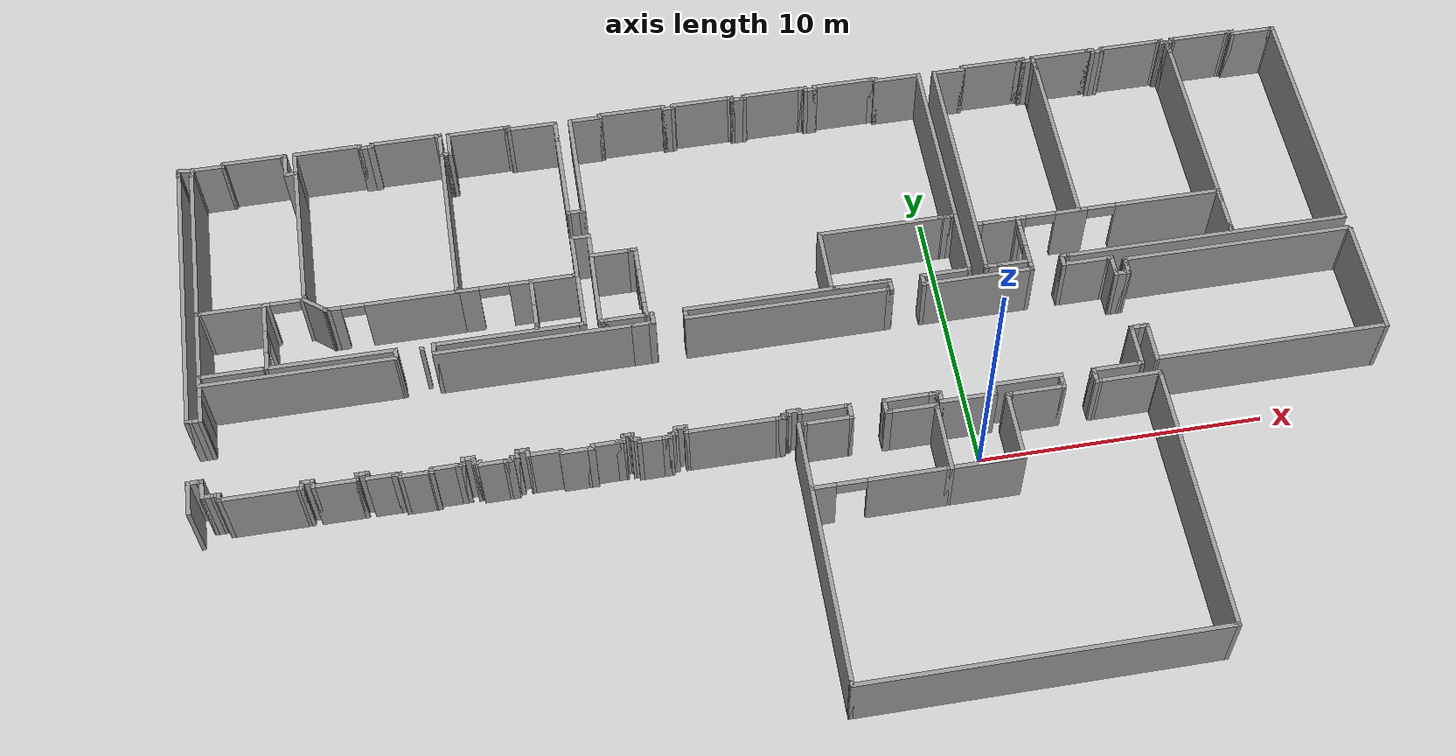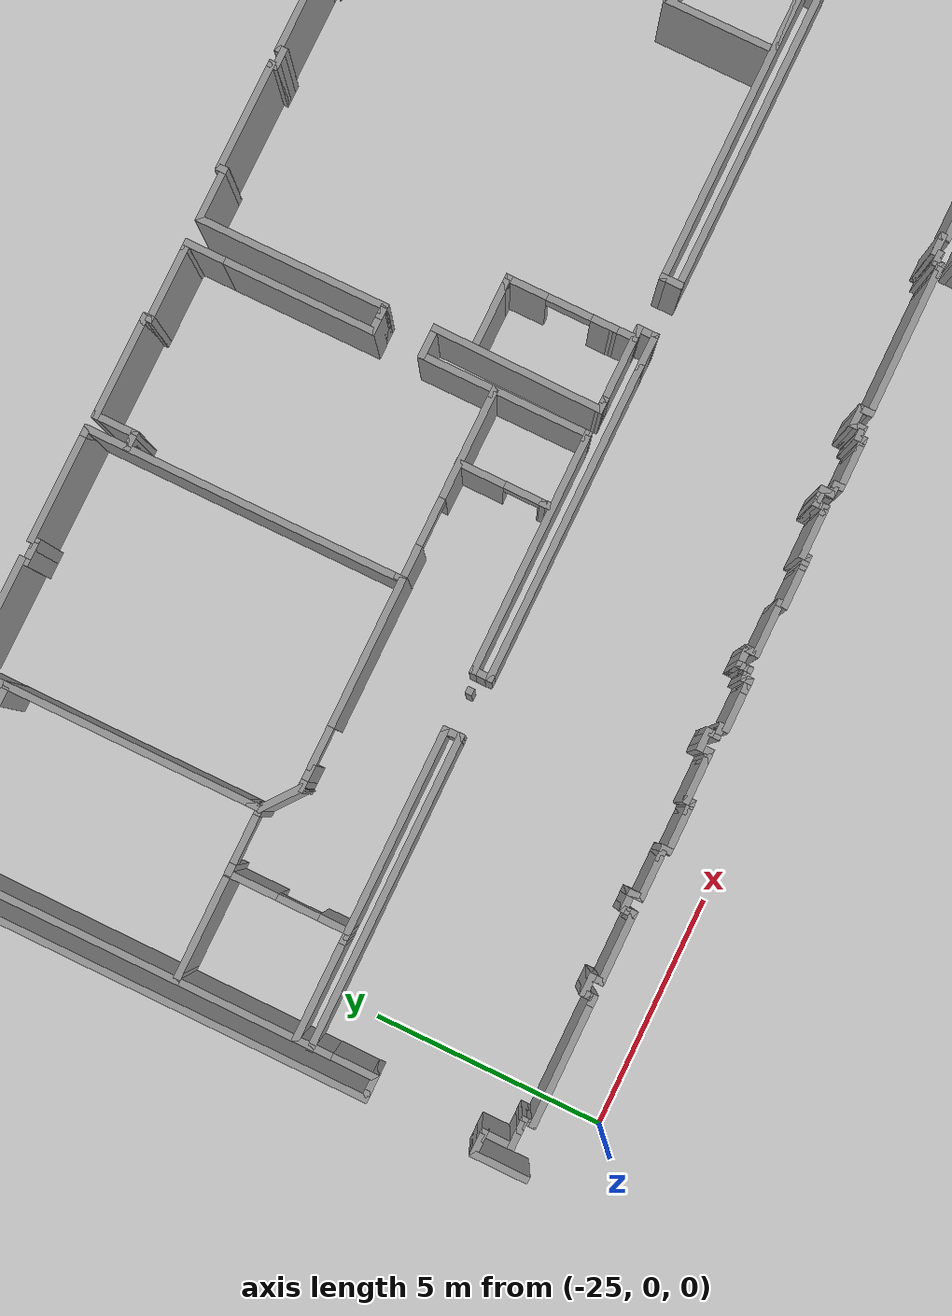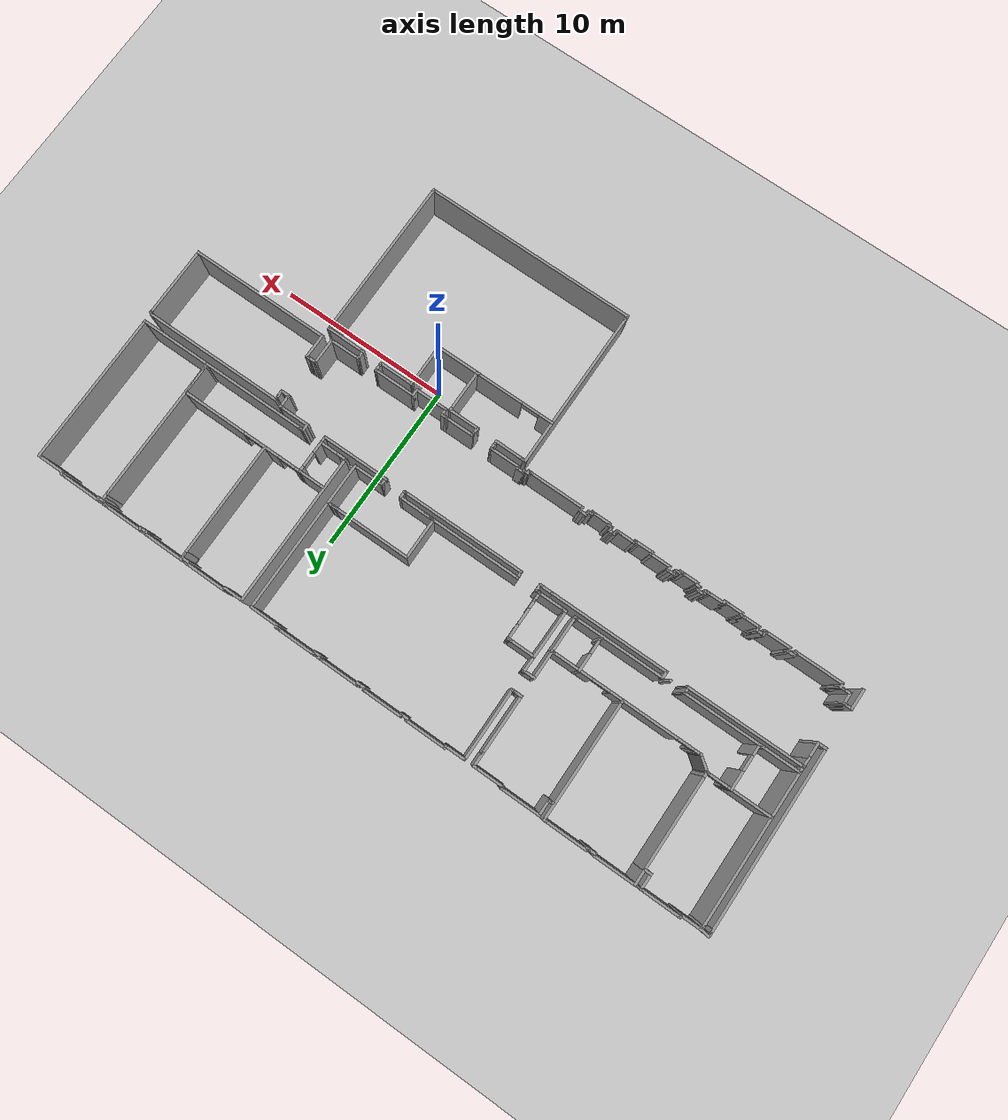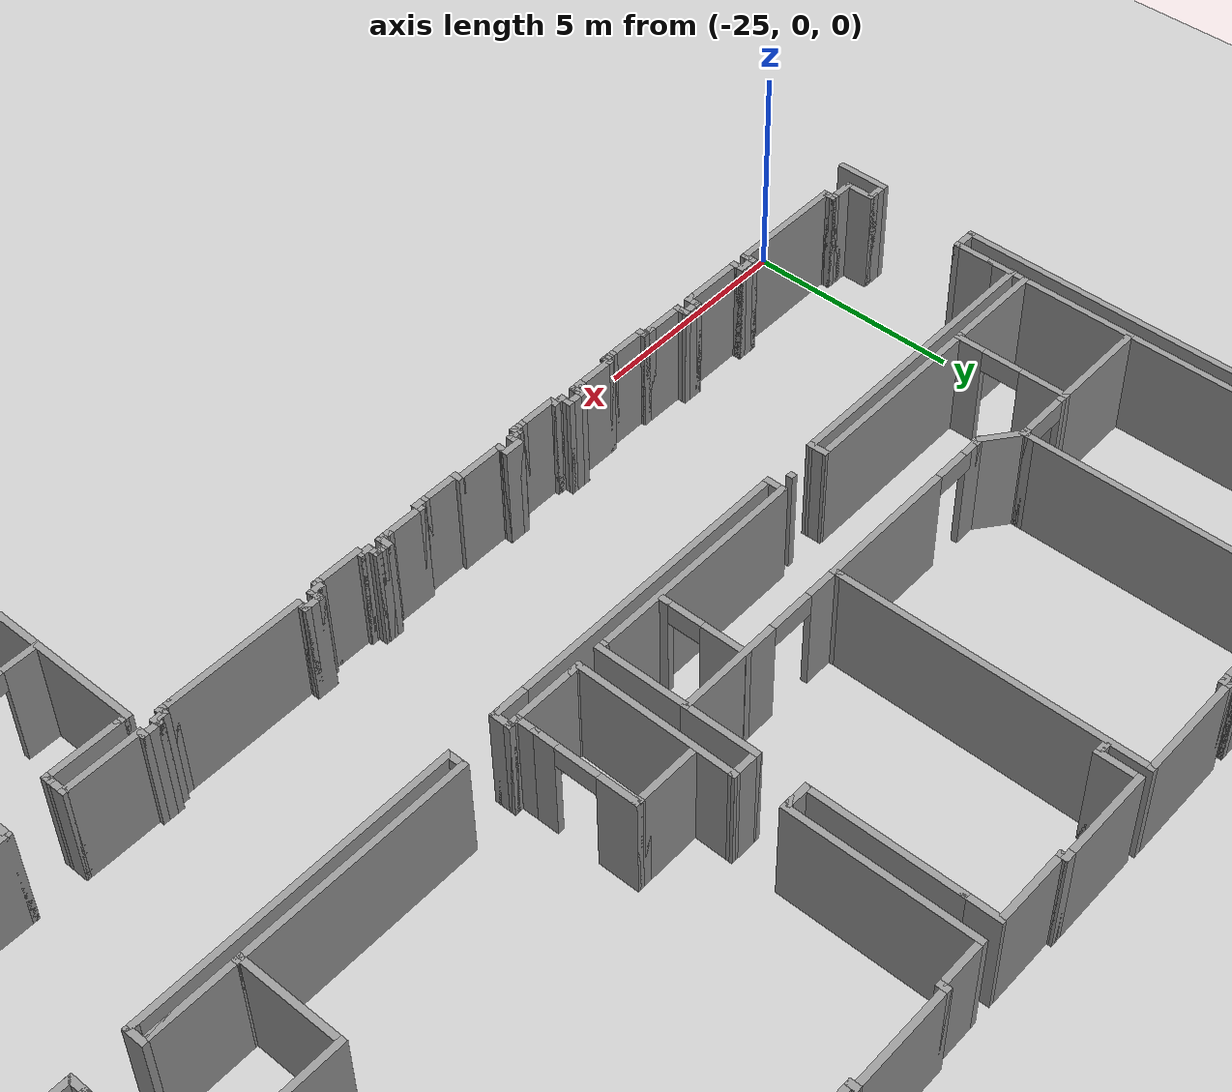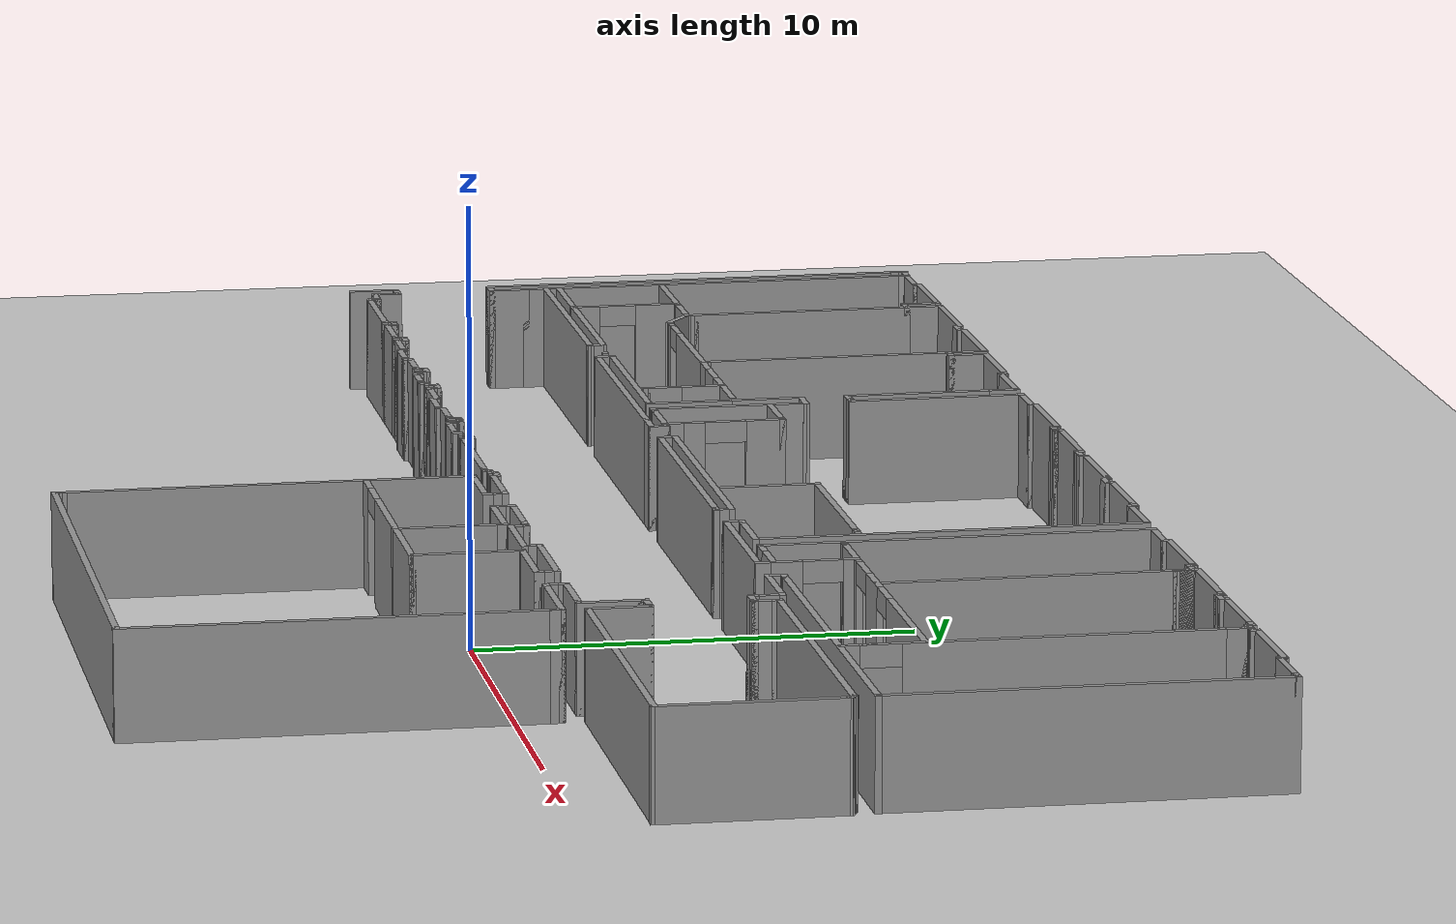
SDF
<sdf version='1.6'>
  <world name='default'>
    <scene>
      <ambient>0.4 0.4 0.4 1</ambient>
      <background>0.7 0.7 0.7 1</background>
      <shadows>true</shadows>
    </scene>

    <!-- A global light source -->
    <include>
      <uri>model://sun</uri>
    </include>

    <!-- A ground plane -->
    <include>
      <uri>model://ground_plane</uri>
    </include>
<physics type="ode">
      <real_time_update_rate>1000.0</real_time_update_rate>
      <max_step_size>0.001</max_step_size>
      <real_time_factor>1</real_time_factor>
      <ode>
        <solver>
          <type>quick</type>
          <iters>150</iters>
          <precon_iters>0</precon_iters>
          <sor>1.400000</sor>
          <use_dynamic_moi_rescaling>1</use_dynamic_moi_rescaling>
        </solver>
        <constraints>
          <cfm>0.00001</cfm>
          <erp>0.2</erp>
          <contact_max_correcting_vel>2000.000000</contact_max_correcting_vel>
          <contact_surface_layer>0.01000</contact_surface_layer>
        </constraints>
      </ode>
    </physics>
    <model name='office_full'>
      <pose frame=''>-5.89703 3.34021 0 0 -0 0</pose>
      <link name='Wall_101'>
        <collision name='Wall_101_Collision'>
          <geometry>
            <box>
              <size>4.5 0.15 2.5</size>
            </box>
          </geometry>
          <pose frame=''>0 0 1.25 0 -0 0</pose>
          <max_contacts>10</max_contacts>
          <surface>
            <contact>
              <ode/>
            </contact>
            <bounce/>
            <friction>
              <torsional>
                <ode/>
              </torsional>
              <ode/>
            </friction>
          </surface>
        </collision>
        <visual name='Wall_101_Visual'>
          <pose frame=''>0 0 1.25 0 -0 0</pose>
          <geometry>
            <box>
              <size>4.5 0.15 2.5</size>
            </box>
          </geometry>
          <material>
            <script>
              <uri>file://media/materials/scripts/gazebo.material</uri>
              <name>Gazebo/Grey</name>
            </script>
            <ambient>1 1 1 1</ambient>
          </material>
        </visual>
        <pose frame=''>-15.4793 2.88121 0 0 -0 0</pose>
        <self_collide>0</self_collide>
        <kinematic>0</kinematic>
        <gravity>1</gravity>
      </link>
      <link name='Wall_108'>
        <collision name='Wall_108_Collision'>
          <geometry>
            <box>
              <size>0.15 0.15 2.5</size>
            </box>
          </geometry>
          <pose frame=''>0 0 1.25 0 -0 0</pose>
          <max_contacts>10</max_contacts>
          <surface>
            <contact>
              <ode/>
            </contact>
            <bounce/>
            <friction>
              <torsional>
                <ode/>
              </torsional>
              <ode/>
            </friction>
          </surface>
        </collision>
        <visual name='Wall_108_Visual'>
          <pose frame=''>0 0 1.25 0 -0 0</pose>
          <geometry>
            <box>
              <size>0.15 0.15 2.5</size>
            </box>
          </geometry>
          <material>
            <script>
              <uri>file://media/materials/scripts/gazebo.material</uri>
              <name>Gazebo/Grey</name>
            </script>
            <ambient>1 1 1 1</ambient>
          </material>
        </visual>
        <pose frame=''>-19.9811 2.5471 0 0 -0 0</pose>
        <self_collide>0</self_collide>
        <kinematic>0</kinematic>
        <gravity>1</gravity>
      </link>
      <link name='Wall_114'>
        <collision name='Wall_114_Collision'>
          <geometry>
            <box>
              <size>1 0.15 2.5</size>
            </box>
          </geometry>
          <pose frame=''>0 0 1.25 0 -0 0</pose>
          <max_contacts>10</max_contacts>
          <surface>
            <contact>
              <ode/>
            </contact>
            <bounce/>
            <friction>
              <torsional>
                <ode/>
              </torsional>
              <ode/>
            </friction>
          </surface>
        </collision>
        <visual name='Wall_114_Visual'>
          <pose frame=''>0 0 1.25 0 -0 0</pose>
          <geometry>
            <box>
              <size>1 0.15 2.5</size>
            </box>
          </geometry>
          <material>
            <script>
              <uri>file://media/materials/scripts/gazebo.material</uri>
              <name>Gazebo/Grey</name>
            </script>
            <ambient>1 1 1 1</ambient>
          </material>
        </visual>
        <pose frame=''>-19.9543 2.45621 0 0 0 -1.5708</pose>
        <self_collide>0</self_collide>
        <kinematic>0</kinematic>
        <gravity>1</gravity>
      </link>
      <link name='Wall_117'>
        <collision name='Wall_117_Collision'>
          <geometry>
            <box>
              <size>6.83579 0.15 2.5</size>
            </box>
          </geometry>
          <pose frame=''>0 0 1.25 0 -0 0</pose>
          <max_contacts>10</max_contacts>
          <surface>
            <contact>
              <ode/>
            </contact>
            <bounce/>
            <friction>
              <torsional>
                <ode/>
              </torsional>
              <ode/>
            </friction>
          </surface>
        </collision>
        <visual name='Wall_117_Visual'>
          <pose frame=''>0 0 1.25 0 -0 0</pose>
          <geometry>
            <box>
              <size>6.83579 0.15 2.5</size>
            </box>
          </geometry>
          <material>
            <script>
              <uri>file://media/materials/scripts/gazebo.material</uri>
              <name>Gazebo/Grey</name>
            </script>
            <ambient>1 1 1 1</ambient>
          </material>
        </visual>
        <pose frame=''>-16.6382 2.55421 0 0 0 -3.14032</pose>
        <self_collide>0</self_collide>
        <kinematic>0</kinematic>
        <gravity>1</gravity>
      </link>
      <link name='Wall_122'>
        <collision name='Wall_122_Collision'>
          <geometry>
            <box>
              <size>0.5 0.15 2.5</size>
            </box>
          </geometry>
          <pose frame=''>0 0 1.25 0 -0 0</pose>
          <max_contacts>10</max_contacts>
          <surface>
            <contact>
              <ode/>
            </contact>
            <bounce/>
            <friction>
              <torsional>
                <ode/>
              </torsional>
              <ode/>
            </friction>
          </surface>
        </collision>
        <visual name='Wall_122_Visual'>
          <pose frame=''>0 0 1.25 0 -0 0</pose>
          <geometry>
            <box>
              <size>0.5 0.15 2.5</size>
            </box>
          </geometry>
          <material>
            <script>
              <uri>file://media/materials/scripts/gazebo.material</uri>
              <name>Gazebo/Grey</name>
            </script>
            <ambient>1 1 1 1</ambient>
          </material>
        </visual>
        <pose frame=''>-12.0043 2.70621 0 0 0 -1.5708</pose>
        <self_collide>0</self_collide>
        <kinematic>0</kinematic>
        <gravity>1</gravity>
      </link>
      <link name='Wall_124'>
        <collision name='Wall_124_Collision'>
          <geometry>
            <box>
              <size>5.25 0.15 2.5</size>
            </box>
          </geometry>
          <pose frame=''>0 0 1.25 0 -0 0</pose>
          <max_contacts>10</max_contacts>
          <surface>
            <contact>
              <ode/>
            </contact>
            <bounce/>
            <friction>
              <torsional>
                <ode/>
              </torsional>
              <ode/>
            </friction>
          </surface>
        </collision>
        <visual name='Wall_124_Visual'>
          <pose frame=''>0 0 1.25 0 -0 0</pose>
          <geometry>
            <box>
              <size>5.25 0.15 2.5</size>
            </box>
          </geometry>
          <material>
            <script>
              <uri>file://media/materials/scripts/gazebo.material</uri>
              <name>Gazebo/Grey</name>
            </script>
            <ambient>1 1 1 1</ambient>
          </material>
        </visual>
        <pose frame=''>-9.45432 2.88121 0 0 -0 0</pose>
        <self_collide>0</self_collide>
        <kinematic>0</kinematic>
        <gravity>1</gravity>
      </link>
      <link name='Wall_125'>
        <collision name='Wall_125_Collision'>
          <geometry>
            <box>
              <size>0.25 0.15 2.5</size>
            </box>
          </geometry>
          <pose frame=''>0 0 1.25 0 -0 0</pose>
          <max_contacts>10</max_contacts>
          <surface>
            <contact>
              <ode/>
            </contact>
            <bounce/>
            <friction>
              <torsional>
                <ode/>
              </torsional>
              <ode/>
            </friction>
          </surface>
        </collision>
        <visual name='Wall_125_Visual'>
          <pose frame=''>0 0 1.25 0 -0 0</pose>
          <geometry>
            <box>
              <size>0.25 0.15 2.5</size>
            </box>
          </geometry>
          <material>
            <script>
              <uri>file://media/materials/scripts/gazebo.material</uri>
              <name>Gazebo/Grey</name>
            </script>
            <ambient>1 1 1 1</ambient>
          </material>
        </visual>
        <pose frame=''>-6.85432 2.88121 0 0 -0 0</pose>
        <self_collide>0</self_collide>
        <kinematic>0</kinematic>
        <gravity>1</gravity>
      </link>
      <link name='Wall_126'>
        <collision name='Wall_126_Collision'>
          <geometry>
            <box>
              <size>2.2 0.15 2.5</size>
            </box>
          </geometry>
          <pose frame=''>0 0 1.25 0 -0 0</pose>
          <max_contacts>10</max_contacts>
          <surface>
            <contact>
              <ode/>
            </contact>
            <bounce/>
            <friction>
              <torsional>
                <ode/>
              </torsional>
              <ode/>
            </friction>
          </surface>
        </collision>
        <visual name='Wall_126_Visual'>
          <pose frame=''>0 0 1.25 0 -0 0</pose>
          <geometry>
            <box>
              <size>2.2 0.15 2.5</size>
            </box>
          </geometry>
          <material>
            <script>
              <uri>file://media/materials/scripts/gazebo.material</uri>
              <name>Gazebo/Grey</name>
            </script>
            <ambient>1 1 1 1</ambient>
          </material>
        </visual>
        <pose frame=''>-6.80432 3.90621 0 0 -0 1.5708</pose>
        <self_collide>0</self_collide>
        <kinematic>0</kinematic>
        <gravity>1</gravity>
      </link>
      <link name='Wall_128'>
        <pose frame=''>-8.4283 4.01499 0 0 0 -1.5708</pose>
        <visual name='Wall_128_Visual_0'>
          <pose frame=''>-0.459037 0 1.25 0 -0 0</pose>
          <geometry>
            <box>
              <size>1.08193 0.15 2.5</size>
            </box>
          </geometry>
          <material>
            <script>
              <uri>file://media/materials/scripts/gazebo.material</uri>
              <name>Gazebo/Grey</name>
            </script>
            <ambient>1 1 1 1</ambient>
          </material>
        </visual>
        <collision name='Wall_128_Collision_0'>
          <geometry>
            <box>
              <size>1.08193 0.15 2.5</size>
            </box>
          </geometry>
          <pose frame=''>-0.459037 0 1.25 0 -0 0</pose>
          <max_contacts>10</max_contacts>
          <surface>
            <contact>
              <ode/>
            </contact>
            <bounce/>
            <friction>
              <torsional>
                <ode/>
              </torsional>
              <ode/>
            </friction>
          </surface>
        </collision>
        <visual name='Wall_128_Visual_1'>
          <pose frame=''>0.93879 0 1.25 0 -0 0</pose>
          <geometry>
            <box>
              <size>0.122421 0.15 2.5</size>
            </box>
          </geometry>
          <material>
            <script>
              <uri>file://media/materials/scripts/gazebo.material</uri>
              <name>Gazebo/Grey</name>
            </script>
            <ambient>1 1 1 1</ambient>
          </material>
        </visual>
        <collision name='Wall_128_Collision_1'>
          <geometry>
            <box>
              <size>0.122421 0.15 2.5</size>
            </box>
          </geometry>
          <pose frame=''>0.93879 0 1.25 0 -0 0</pose>
          <max_contacts>10</max_contacts>
          <surface>
            <contact>
              <ode/>
            </contact>
            <bounce/>
            <friction>
              <torsional>
                <ode/>
              </torsional>
              <ode/>
            </friction>
          </surface>
        </collision>
        <visual name='Wall_128_Visual_2'>
          <pose frame=''>0.479753 0 2.25 0 -0 0</pose>
          <geometry>
            <box>
              <size>0.795652 0.15 0.5</size>
            </box>
          </geometry>
          <material>
            <script>
              <uri>file://media/materials/scripts/gazebo.material</uri>
              <name>Gazebo/Grey</name>
            </script>
            <ambient>1 1 1 1</ambient>
          </material>
        </visual>
        <collision name='Wall_128_Collision_2'>
          <geometry>
            <box>
              <size>0.795652 0.15 0.5</size>
            </box>
          </geometry>
          <pose frame=''>0.479753 0 2.25 0 -0 0</pose>
          <max_contacts>10</max_contacts>
          <surface>
            <contact>
              <ode/>
            </contact>
            <bounce/>
            <friction>
              <torsional>
                <ode/>
              </torsional>
              <ode/>
            </friction>
          </surface>
        </collision>
        <self_collide>0</self_collide>
        <kinematic>0</kinematic>
        <gravity>1</gravity>
      </link>
      <link name='Wall_129'>
        <collision name='Wall_129_Collision'>
          <geometry>
            <box>
              <size>0.25 0.15 2.5</size>
            </box>
          </geometry>
          <pose frame=''>0 0 1.25 0 -0 0</pose>
          <max_contacts>10</max_contacts>
          <surface>
            <contact>
              <ode/>
            </contact>
            <bounce/>
            <friction>
              <torsional>
                <ode/>
              </torsional>
              <ode/>
            </friction>
          </surface>
        </collision>
        <visual name='Wall_129_Visual'>
          <pose frame=''>0 0 1.25 0 -0 0</pose>
          <geometry>
            <box>
              <size>0.25 0.15 2.5</size>
            </box>
          </geometry>
          <material>
            <script>
              <uri>file://media/materials/scripts/gazebo.material</uri>
              <name>Gazebo/Grey</name>
            </script>
            <ambient>1 1 1 1</ambient>
          </material>
        </visual>
        <pose frame=''>-8.4283 3.03999 0 0 0 -1.5708</pose>
        <self_collide>0</self_collide>
        <kinematic>0</kinematic>
        <gravity>1</gravity>
      </link>
      <link name='Wall_131'>
        <collision name='Wall_131_Collision'>
          <geometry>
            <box>
              <size>7 0.15 2.5</size>
            </box>
          </geometry>
          <pose frame=''>0 0 1.25 0 -0 0</pose>
          <max_contacts>10</max_contacts>
          <surface>
            <contact>
              <ode/>
            </contact>
            <bounce/>
            <friction>
              <torsional>
                <ode/>
              </torsional>
              <ode/>
            </friction>
          </surface>
        </collision>
        <visual name='Wall_131_Visual'>
          <pose frame=''>0 0 1.25 0 -0 0</pose>
          <geometry>
            <box>
              <size>7 0.15 2.5</size>
            </box>
          </geometry>
          <material>
            <script>
              <uri>file://media/materials/scripts/gazebo.material</uri>
              <name>Gazebo/Grey</name>
            </script>
            <ambient>1 1 1 1</ambient>
          </material>
        </visual>
        <pose frame=''>-8.57932 2.53121 0 0 -0 0</pose>
        <self_collide>0</self_collide>
        <kinematic>0</kinematic>
        <gravity>1</gravity>
      </link>
      <link name='Wall_136'>
        <collision name='Wall_136_Collision'>
          <geometry>
            <box>
              <size>0.15 0.15 2.5</size>
            </box>
          </geometry>
          <pose frame=''>0 0 1.25 0 -0 0</pose>
          <max_contacts>10</max_contacts>
          <surface>
            <contact>
              <ode/>
            </contact>
            <bounce/>
            <friction>
              <torsional>
                <ode/>
              </torsional>
              <ode/>
            </friction>
          </surface>
        </collision>
        <visual name='Wall_136_Visual'>
          <pose frame=''>0 0 1.25 0 -0 0</pose>
          <geometry>
            <box>
              <size>0.15 0.15 2.5</size>
            </box>
          </geometry>
          <material>
            <script>
              <uri>file://media/materials/scripts/gazebo.material</uri>
              <name>Gazebo/Grey</name>
            </script>
            <ambient>1 1 1 1</ambient>
          </material>
        </visual>
        <pose frame=''>-12.4043 2.78121 0 0 -0 0</pose>
        <self_collide>0</self_collide>
        <kinematic>0</kinematic>
        <gravity>1</gravity>
      </link>
      <link name='Wall_140'>
        <collision name='Wall_140_Collision'>
          <geometry>
            <box>
              <size>0.472867 0.15 2.5</size>
            </box>
          </geometry>
          <pose frame=''>0 0 1.25 0 -0 0</pose>
          <max_contacts>10</max_contacts>
          <surface>
            <contact>
              <ode/>
            </contact>
            <bounce/>
            <friction>
              <torsional>
                <ode/>
              </torsional>
              <ode/>
            </friction>
          </surface>
        </collision>
        <visual name='Wall_140_Visual'>
          <pose frame=''>0 0 1.25 0 -0 0</pose>
          <geometry>
            <box>
              <size>0.472867 0.15 2.5</size>
            </box>
          </geometry>
          <material>
            <script>
              <uri>file://media/materials/scripts/gazebo.material</uri>
              <name>Gazebo/Grey</name>
            </script>
            <ambient>1 1 1 1</ambient>
          </material>
        </visual>
        <pose frame=''>-13.2998 2.71984 0 0 0 -1.54281</pose>
        <self_collide>0</self_collide>
        <kinematic>0</kinematic>
        <gravity>1</gravity>
      </link>
      <link name='Wall_143'>
        <collision name='Wall_143_Collision'>
          <geometry>
            <box>
              <size>1 0.15 2.5</size>
            </box>
          </geometry>
          <pose frame=''>0 0 1.25 0 -0 0</pose>
          <max_contacts>10</max_contacts>
          <surface>
            <contact>
              <ode/>
            </contact>
            <bounce/>
            <friction>
              <torsional>
                <ode/>
              </torsional>
              <ode/>
            </friction>
          </surface>
        </collision>
        <visual name='Wall_143_Visual'>
          <pose frame=''>0 0 1.25 0 -0 0</pose>
          <geometry>
            <box>
              <size>1 0.15 2.5</size>
            </box>
          </geometry>
          <material>
            <script>
              <uri>file://media/materials/scripts/gazebo.material</uri>
              <name>Gazebo/Grey</name>
            </script>
            <ambient>1 1 1 1</ambient>
          </material>
        </visual>
        <pose frame=''>-19.9543 1.60621 0 0 0 -1.5708</pose>
        <self_collide>0</self_collide>
        <kinematic>0</kinematic>
        <gravity>1</gravity>
      </link>
      <link name='Wall_144'>
        <collision name='Wall_144_Collision'>
          <geometry>
            <box>
              <size>0.5 0.15 2.5</size>
            </box>
          </geometry>
          <pose frame=''>0 0 1.25 0 -0 0</pose>
          <max_contacts>10</max_contacts>
          <surface>
            <contact>
              <ode/>
            </contact>
            <bounce/>
            <friction>
              <torsional>
                <ode/>
              </torsional>
              <ode/>
            </friction>
          </surface>
        </collision>
        <visual name='Wall_144_Visual'>
          <pose frame=''>0 0 1.25 0 -0 0</pose>
          <geometry>
            <box>
              <size>0.5 0.15 2.5</size>
            </box>
          </geometry>
          <material>
            <script>
              <uri>file://media/materials/scripts/gazebo.material</uri>
              <name>Gazebo/Grey</name>
            </script>
            <ambient>1 1 1 1</ambient>
          </material>
        </visual>
        <pose frame=''>-20.1293 1.18121 0 0 -0 3.14159</pose>
        <self_collide>0</self_collide>
        <kinematic>0</kinematic>
        <gravity>1</gravity>
      </link>
      <link name='Wall_145'>
        <collision name='Wall_145_Collision'>
          <geometry>
            <box>
              <size>0.25 0.15 2.5</size>
            </box>
          </geometry>
          <pose frame=''>0 0 1.25 0 -0 0</pose>
          <max_contacts>10</max_contacts>
          <surface>
            <contact>
              <ode/>
            </contact>
            <bounce/>
            <friction>
              <torsional>
                <ode/>
              </torsional>
              <ode/>
            </friction>
          </surface>
        </collision>
        <visual name='Wall_145_Visual'>
          <pose frame=''>0 0 1.25 0 -0 0</pose>
          <geometry>
            <box>
              <size>0.25 0.15 2.5</size>
            </box>
          </geometry>
          <material>
            <script>
              <uri>file://media/materials/scripts/gazebo.material</uri>
              <name>Gazebo/Grey</name>
            </script>
            <ambient>1 1 1 1</ambient>
          </material>
        </visual>
        <pose frame=''>-20.3543 1.18121 0 0 -0 3.14159</pose>
        <self_collide>0</self_collide>
        <kinematic>0</kinematic>
        <gravity>1</gravity>
      </link>
      <link name='Wall_146'>
        <collision name='Wall_146_Collision'>
          <geometry>
            <box>
              <size>10.5 0.15 2.5</size>
            </box>
          </geometry>
          <pose frame=''>0 0 1.25 0 -0 0</pose>
          <max_contacts>10</max_contacts>
          <surface>
            <contact>
              <ode/>
            </contact>
            <bounce/>
            <friction>
              <torsional>
                <ode/>
              </torsional>
              <ode/>
            </friction>
          </surface>
        </collision>
        <visual name='Wall_146_Visual'>
          <pose frame=''>0 0 1.25 0 -0 0</pose>
          <geometry>
            <box>
              <size>10.5 0.15 2.5</size>
            </box>
          </geometry>
          <material>
            <script>
              <uri>file://media/materials/scripts/gazebo.material</uri>
              <name>Gazebo/Grey</name>
            </script>
            <ambient>1 1 1 1</ambient>
          </material>
        </visual>
        <pose frame=''>-20.4043 6.35621 0 0 -0 1.5708</pose>
        <self_collide>0</self_collide>
        <kinematic>0</kinematic>
        <gravity>1</gravity>
      </link>
      <link name='Wall_147'>
        <collision name='Wall_147_Collision'>
          <geometry>
            <box>
              <size>0.25 0.15 2.5</size>
            </box>
          </geometry>
          <pose frame=''>0 0 1.25 0 -0 0</pose>
          <max_contacts>10</max_contacts>
          <surface>
            <contact>
              <ode/>
            </contact>
            <bounce/>
            <friction>
              <torsional>
                <ode/>
              </torsional>
              <ode/>
            </friction>
          </surface>
        </collision>
        <visual name='Wall_147_Visual'>
          <pose frame=''>0 0 1.25 0 -0 0</pose>
          <geometry>
            <box>
              <size>0.25 0.15 2.5</size>
            </box>
          </geometry>
          <material>
            <script>
              <uri>file://media/materials/scripts/gazebo.material</uri>
              <name>Gazebo/Grey</name>
            </script>
            <ambient>1 1 1 1</ambient>
          </material>
        </visual>
        <pose frame=''>-20.4043 11.5812 0 0 -0 1.5708</pose>
        <self_collide>0</self_collide>
        <kinematic>0</kinematic>
        <gravity>1</gravity>
      </link>
      <link name='Wall_148'>
        <collision name='Wall_148_Collision'>
          <geometry>
            <box>
              <size>0.25 0.15 2.5</size>
            </box>
          </geometry>
          <pose frame=''>0 0 1.25 0 -0 0</pose>
          <max_contacts>10</max_contacts>
          <surface>
            <contact>
              <ode/>
            </contact>
            <bounce/>
            <friction>
              <torsional>
                <ode/>
              </torsional>
              <ode/>
            </friction>
          </surface>
        </collision>
        <visual name='Wall_148_Visual'>
          <pose frame=''>0 0 1.25 0 -0 0</pose>
          <geometry>
            <box>
              <size>0.25 0.15 2.5</size>
            </box>
          </geometry>
          <material>
            <script>
              <uri>file://media/materials/scripts/gazebo.material</uri>
              <name>Gazebo/Grey</name>
            </script>
            <ambient>1 1 1 1</ambient>
          </material>
        </visual>
        <pose frame=''>-20.4043 11.6812 0 0 -0 1.5708</pose>
        <self_collide>0</self_collide>
        <kinematic>0</kinematic>
        <gravity>1</gravity>
      </link>
      <link name='Wall_149'>
        <collision name='Wall_149_Collision'>
          <geometry>
            <box>
              <size>0.25 0.15 2.5</size>
            </box>
          </geometry>
          <pose frame=''>0 0 1.25 0 -0 0</pose>
          <max_contacts>10</max_contacts>
          <surface>
            <contact>
              <ode/>
            </contact>
            <bounce/>
            <friction>
              <torsional>
                <ode/>
              </torsional>
              <ode/>
            </friction>
          </surface>
        </collision>
        <visual name='Wall_149_Visual'>
          <pose frame=''>0 0 1.25 0 -0 0</pose>
          <geometry>
            <box>
              <size>0.25 0.15 2.5</size>
            </box>
          </geometry>
          <material>
            <script>
              <uri>file://media/materials/scripts/gazebo.material</uri>
              <name>Gazebo/Grey</name>
            </script>
            <ambient>1 1 1 1</ambient>
          </material>
        </visual>
        <pose frame=''>-20.4043 11.6812 0 0 0 -1.5708</pose>
        <self_collide>0</self_collide>
        <kinematic>0</kinematic>
        <gravity>1</gravity>
      </link>
      <link name='Wall_150'>
        <collision name='Wall_150_Collision'>
          <geometry>
            <box>
              <size>0.25 0.15 2.5</size>
            </box>
          </geometry>
          <pose frame=''>0 0 1.25 0 -0 0</pose>
          <max_contacts>10</max_contacts>
          <surface>
            <contact>
              <ode/>
            </contact>
            <bounce/>
            <friction>
              <torsional>
                <ode/>
              </torsional>
              <ode/>
            </friction>
          </surface>
        </collision>
        <visual name='Wall_150_Visual'>
          <pose frame=''>0 0 1.25 0 -0 0</pose>
          <geometry>
            <box>
              <size>0.25 0.15 2.5</size>
            </box>
          </geometry>
          <material>
            <script>
              <uri>file://media/materials/scripts/gazebo.material</uri>
              <name>Gazebo/Grey</name>
            </script>
            <ambient>1 1 1 1</ambient>
          </material>
        </visual>
        <pose frame=''>-20.4043 11.6812 0 0 -0 1.5708</pose>
        <self_collide>0</self_collide>
        <kinematic>0</kinematic>
        <gravity>1</gravity>
      </link>
      <link name='Wall_151'>
        <collision name='Wall_151_Collision'>
          <geometry>
            <box>
              <size>0.25 0.15 2.5</size>
            </box>
          </geometry>
          <pose frame=''>0 0 1.25 0 -0 0</pose>
          <max_contacts>10</max_contacts>
          <surface>
            <contact>
              <ode/>
            </contact>
            <bounce/>
            <friction>
              <torsional>
                <ode/>
              </torsional>
              <ode/>
            </friction>
          </surface>
        </collision>
        <visual name='Wall_151_Visual'>
          <pose frame=''>0 0 1.25 0 -0 0</pose>
          <geometry>
            <box>
              <size>0.25 0.15 2.5</size>
            </box>
          </geometry>
          <material>
            <script>
              <uri>file://media/materials/scripts/gazebo.material</uri>
              <name>Gazebo/Grey</name>
            </script>
            <ambient>1 1 1 1</ambient>
          </material>
        </visual>
        <pose frame=''>-20.4043 11.7812 0 0 -0 1.5708</pose>
        <self_collide>0</self_collide>
        <kinematic>0</kinematic>
        <gravity>1</gravity>
      </link>
      <link name='Wall_152'>
        <collision name='Wall_152_Collision'>
          <geometry>
            <box>
              <size>0.652494 0.15 2.5</size>
            </box>
          </geometry>
          <pose frame=''>0 0 1.25 0 -0 0</pose>
          <max_contacts>10</max_contacts>
          <surface>
            <contact>
              <ode/>
            </contact>
            <bounce/>
            <friction>
              <torsional>
                <ode/>
              </torsional>
              <ode/>
            </friction>
          </surface>
        </collision>
        <visual name='Wall_152_Visual'>
          <pose frame=''>0 0 1.25 0 -0 0</pose>
          <geometry>
            <box>
              <size>0.652494 0.15 2.5</size>
            </box>
          </geometry>
          <material>
            <script>
              <uri>file://media/materials/scripts/gazebo.material</uri>
              <name>Gazebo/Grey</name>
            </script>
            <ambient>1 1 1 1</ambient>
          </material>
        </visual>
        <pose frame=''>-20.1543 11.8062 0 0 0 -0.099669</pose>
        <self_collide>0</self_collide>
        <kinematic>0</kinematic>
        <gravity>1</gravity>
      </link>
      <link name='Wall_154'>
        <collision name='Wall_154_Collision'>
          <geometry>
            <box>
              <size>1.25 0.15 2.5</size>
            </box>
          </geometry>
          <pose frame=''>0 0 1.25 0 -0 0</pose>
          <max_contacts>10</max_contacts>
          <surface>
            <contact>
              <ode/>
            </contact>
            <bounce/>
            <friction>
              <torsional>
                <ode/>
              </torsional>
              <ode/>
            </friction>
          </surface>
        </collision>
        <visual name='Wall_154_Visual'>
          <pose frame=''>0 0 1.25 0 -0 0</pose>
          <geometry>
            <box>
              <size>1.25 0.15 2.5</size>
            </box>
          </geometry>
          <material>
            <script>
              <uri>file://media/materials/scripts/gazebo.material</uri>
              <name>Gazebo/Grey</name>
            </script>
            <ambient>1 1 1 1</ambient>
          </material>
        </visual>
        <pose frame=''>-20.4403 -1.73121 0 0 -0 1.5708</pose>
        <self_collide>0</self_collide>
        <kinematic>0</kinematic>
        <gravity>1</gravity>
      </link>
      <link name='Wall_155'>
        <collision name='Wall_155_Collision'>
          <geometry>
            <box>
              <size>0.5 0.15 2.5</size>
            </box>
          </geometry>
          <pose frame=''>0 0 1.25 0 -0 0</pose>
          <max_contacts>10</max_contacts>
          <surface>
            <contact>
              <ode/>
            </contact>
            <bounce/>
            <friction>
              <torsional>
                <ode/>
              </torsional>
              <ode/>
            </friction>
          </surface>
        </collision>
        <visual name='Wall_155_Visual'>
          <pose frame=''>0 0 1.25 0 -0 0</pose>
          <geometry>
            <box>
              <size>0.5 0.15 2.5</size>
            </box>
          </geometry>
          <material>
            <script>
              <uri>file://media/materials/scripts/gazebo.material</uri>
              <name>Gazebo/Grey</name>
            </script>
            <ambient>1 1 1 1</ambient>
          </material>
        </visual>
        <pose frame=''>-20.2653 -1.18121 0 0 -0 0</pose>
        <self_collide>0</self_collide>
        <kinematic>0</kinematic>
        <gravity>1</gravity>
      </link>
      <link name='Wall_156'>
        <collision name='Wall_156_Collision'>
          <geometry>
            <box>
              <size>0.25 0.15 2.5</size>
            </box>
          </geometry>
          <pose frame=''>0 0 1.25 0 -0 0</pose>
          <max_contacts>10</max_contacts>
          <surface>
            <contact>
              <ode/>
            </contact>
            <bounce/>
            <friction>
              <torsional>
                <ode/>
              </torsional>
              <ode/>
            </friction>
          </surface>
        </collision>
        <visual name='Wall_156_Visual'>
          <pose frame=''>0 0 1.25 0 -0 0</pose>
          <geometry>
            <box>
              <size>0.25 0.15 2.5</size>
            </box>
          </geometry>
          <material>
            <script>
              <uri>file://media/materials/scripts/gazebo.material</uri>
              <name>Gazebo/Grey</name>
            </script>
            <ambient>1 1 1 1</ambient>
          </material>
        </visual>
        <pose frame=''>-20.0403 -1.18121 0 0 -0 0</pose>
        <self_collide>0</self_collide>
        <kinematic>0</kinematic>
        <gravity>1</gravity>
      </link>
      <link name='Wall_157'>
        <collision name='Wall_157_Collision'>
          <geometry>
            <box>
              <size>0.75 0.15 2.5</size>
            </box>
          </geometry>
          <pose frame=''>0 0 1.25 0 -0 0</pose>
          <max_contacts>10</max_contacts>
          <surface>
            <contact>
              <ode/>
            </contact>
            <bounce/>
            <friction>
              <torsional>
                <ode/>
              </torsional>
              <ode/>
            </friction>
          </surface>
        </collision>
        <visual name='Wall_157_Visual'>
          <pose frame=''>0 0 1.25 0 -0 0</pose>
          <geometry>
            <box>
              <size>0.75 0.15 2.5</size>
            </box>
          </geometry>
          <material>
            <script>
              <uri>file://media/materials/scripts/gazebo.material</uri>
              <name>Gazebo/Grey</name>
            </script>
            <ambient>1 1 1 1</ambient>
          </material>
        </visual>
        <pose frame=''>-19.9903 -1.48121 0 0 0 -1.5708</pose>
        <self_collide>0</self_collide>
        <kinematic>0</kinematic>
        <gravity>1</gravity>
      </link>
      <link name='Wall_158'>
        <collision name='Wall_158_Collision'>
          <geometry>
            <box>
              <size>0.5 0.15 2.5</size>
            </box>
          </geometry>
          <pose frame=''>0 0 1.25 0 -0 0</pose>
          <max_contacts>10</max_contacts>
          <surface>
            <contact>
              <ode/>
            </contact>
            <bounce/>
            <friction>
              <torsional>
                <ode/>
              </torsional>
              <ode/>
            </friction>
          </surface>
        </collision>
        <visual name='Wall_158_Visual'>
          <pose frame=''>0 0 1.25 0 -0 0</pose>
          <geometry>
            <box>
              <size>0.5 0.15 2.5</size>
            </box>
          </geometry>
          <material>
            <script>
              <uri>file://media/materials/scripts/gazebo.material</uri>
              <name>Gazebo/Grey</name>
            </script>
            <ambient>1 1 1 1</ambient>
          </material>
        </visual>
        <pose frame=''>-19.8153 -1.78121 0 0 -0 0</pose>
        <self_collide>0</self_collide>
        <kinematic>0</kinematic>
        <gravity>1</gravity>
      </link>
      <link name='Wall_159'>
        <collision name='Wall_159_Collision'>
          <geometry>
            <box>
              <size>0.25 0.15 2.5</size>
            </box>
          </geometry>
          <pose frame=''>0 0 1.25 0 -0 0</pose>
          <max_contacts>10</max_contacts>
          <surface>
            <contact>
              <ode/>
            </contact>
            <bounce/>
            <friction>
              <torsional>
                <ode/>
              </torsional>
              <ode/>
            </friction>
          </surface>
        </collision>
        <visual name='Wall_159_Visual'>
          <pose frame=''>0 0 1.25 0 -0 0</pose>
          <geometry>
            <box>
              <size>0.25 0.15 2.5</size>
            </box>
          </geometry>
          <material>
            <script>
              <uri>file://media/materials/scripts/gazebo.material</uri>
              <name>Gazebo/Grey</name>
            </script>
            <ambient>1 1 1 1</ambient>
          </material>
        </visual>
        <pose frame=''>-19.5903 -1.78121 0 0 -0 0</pose>
        <self_collide>0</self_collide>
        <kinematic>0</kinematic>
        <gravity>1</gravity>
      </link>
      <link name='Wall_160'>
        <collision name='Wall_160_Collision'>
          <geometry>
            <box>
              <size>0.25 0.15 2.5</size>
            </box>
          </geometry>
          <pose frame=''>0 0 1.25 0 -0 0</pose>
          <max_contacts>10</max_contacts>
          <surface>
            <contact>
              <ode/>
            </contact>
            <bounce/>
            <friction>
              <torsional>
                <ode/>
              </torsional>
              <ode/>
            </friction>
          </surface>
        </collision>
        <visual name='Wall_160_Visual'>
          <pose frame=''>0 0 1.25 0 -0 0</pose>
          <geometry>
            <box>
              <size>0.25 0.15 2.5</size>
            </box>
          </geometry>
          <material>
            <script>
              <uri>file://media/materials/scripts/gazebo.material</uri>
              <name>Gazebo/Grey</name>
            </script>
            <ambient>1 1 1 1</ambient>
          </material>
        </visual>
        <pose frame=''>-19.4903 -1.78121 0 0 -0 0</pose>
        <self_collide>0</self_collide>
        <kinematic>0</kinematic>
        <gravity>1</gravity>
      </link>
      <link name='Wall_161'>
        <collision name='Wall_161_Collision'>
          <geometry>
            <box>
              <size>0.25 0.15 2.5</size>
            </box>
          </geometry>
          <pose frame=''>0 0 1.25 0 -0 0</pose>
          <max_contacts>10</max_contacts>
          <surface>
            <contact>
              <ode/>
            </contact>
            <bounce/>
            <friction>
              <torsional>
                <ode/>
              </torsional>
              <ode/>
            </friction>
          </surface>
        </collision>
        <visual name='Wall_161_Visual'>
          <pose frame=''>0 0 1.25 0 -0 0</pose>
          <geometry>
            <box>
              <size>0.25 0.15 2.5</size>
            </box>
          </geometry>
          <material>
            <script>
              <uri>file://media/materials/scripts/gazebo.material</uri>
              <name>Gazebo/Grey</name>
            </script>
            <ambient>1 1 1 1</ambient>
          </material>
        </visual>
        <pose frame=''>-19.4403 -1.83121 0 0 0 -1.5708</pose>
        <self_collide>0</self_collide>
        <kinematic>0</kinematic>
        <gravity>1</gravity>
      </link>
      <link name='Wall_162'>
        <collision name='Wall_162_Collision'>
          <geometry>
            <box>
              <size>0.25 0.15 2.5</size>
            </box>
          </geometry>
          <pose frame=''>0 0 1.25 0 -0 0</pose>
          <max_contacts>10</max_contacts>
          <surface>
            <contact>
              <ode/>
            </contact>
            <bounce/>
            <friction>
              <torsional>
                <ode/>
              </torsional>
              <ode/>
            </friction>
          </surface>
        </collision>
        <visual name='Wall_162_Visual'>
          <pose frame=''>0 0 1.25 0 -0 0</pose>
          <geometry>
            <box>
              <size>0.25 0.15 2.5</size>
            </box>
          </geometry>
          <material>
            <script>
              <uri>file://media/materials/scripts/gazebo.material</uri>
              <name>Gazebo/Grey</name>
            </script>
            <ambient>1 1 1 1</ambient>
          </material>
        </visual>
        <pose frame=''>-19.4403 -1.93121 0 0 0 -1.5708</pose>
        <self_collide>0</self_collide>
        <kinematic>0</kinematic>
        <gravity>1</gravity>
      </link>
      <link name='Wall_163'>
        <collision name='Wall_163_Collision'>
          <geometry>
            <box>
              <size>2.75 0.15 2.5</size>
            </box>
          </geometry>
          <pose frame=''>0 0 1.25 0 -0 0</pose>
          <max_contacts>10</max_contacts>
          <surface>
            <contact>
              <ode/>
            </contact>
            <bounce/>
            <friction>
              <torsional>
                <ode/>
              </torsional>
              <ode/>
            </friction>
          </surface>
        </collision>
        <visual name='Wall_163_Visual'>
          <pose frame=''>0 0 1.25 0 -0 0</pose>
          <geometry>
            <box>
              <size>2.75 0.15 2.5</size>
            </box>
          </geometry>
          <material>
            <script>
              <uri>file://media/materials/scripts/gazebo.material</uri>
              <name>Gazebo/Grey</name>
            </script>
            <ambient>1 1 1 1</ambient>
          </material>
        </visual>
        <pose frame=''>-18.1403 -1.98121 0 0 -0 0</pose>
        <self_collide>0</self_collide>
        <kinematic>0</kinematic>
        <gravity>1</gravity>
      </link>
      <link name='Wall_164'>
        <collision name='Wall_164_Collision'>
          <geometry>
            <box>
              <size>0.25 0.15 2.5</size>
            </box>
          </geometry>
          <pose frame=''>0 0 1.25 0 -0 0</pose>
          <max_contacts>10</max_contacts>
          <surface>
            <contact>
              <ode/>
            </contact>
            <bounce/>
            <friction>
              <torsional>
                <ode/>
              </torsional>
              <ode/>
            </friction>
          </surface>
        </collision>
        <visual name='Wall_164_Visual'>
          <pose frame=''>0 0 1.25 0 -0 0</pose>
          <geometry>
            <box>
              <size>0.25 0.15 2.5</size>
            </box>
          </geometry>
          <material>
            <script>
              <uri>file://media/materials/scripts/gazebo.material</uri>
              <name>Gazebo/Grey</name>
            </script>
            <ambient>1 1 1 1</ambient>
          </material>
        </visual>
        <pose frame=''>-16.7903 -1.98121 0 0 -0 0</pose>
        <self_collide>0</self_collide>
        <kinematic>0</kinematic>
        <gravity>1</gravity>
      </link>
      <link name='Wall_165'>
        <collision name='Wall_165_Collision'>
          <geometry>
            <box>
              <size>0.25 0.15 2.5</size>
            </box>
          </geometry>
          <pose frame=''>0 0 1.25 0 -0 0</pose>
          <max_contacts>10</max_contacts>
          <surface>
            <contact>
              <ode/>
            </contact>
            <bounce/>
            <friction>
              <torsional>
                <ode/>
              </torsional>
              <ode/>
            </friction>
          </surface>
        </collision>
        <visual name='Wall_165_Visual'>
          <pose frame=''>0 0 1.25 0 -0 0</pose>
          <geometry>
            <box>
              <size>0.25 0.15 2.5</size>
            </box>
          </geometry>
          <material>
            <script>
              <uri>file://media/materials/scripts/gazebo.material</uri>
              <name>Gazebo/Grey</name>
            </script>
            <ambient>1 1 1 1</ambient>
          </material>
        </visual>
        <pose frame=''>-16.7403 -1.93121 0 0 -0 1.5708</pose>
        <self_collide>0</self_collide>
        <kinematic>0</kinematic>
        <gravity>1</gravity>
      </link>
      <link name='Wall_166'>
        <collision name='Wall_166_Collision'>
          <geometry>
            <box>
              <size>0.25 0.15 2.5</size>
            </box>
          </geometry>
          <pose frame=''>0 0 1.25 0 -0 0</pose>
          <max_contacts>10</max_contacts>
          <surface>
            <contact>
              <ode/>
            </contact>
            <bounce/>
            <friction>
              <torsional>
                <ode/>
              </torsional>
              <ode/>
            </friction>
          </surface>
        </collision>
        <visual name='Wall_166_Visual'>
          <pose frame=''>0 0 1.25 0 -0 0</pose>
          <geometry>
            <box>
              <size>0.25 0.15 2.5</size>
            </box>
          </geometry>
          <material>
            <script>
              <uri>file://media/materials/scripts/gazebo.material</uri>
              <name>Gazebo/Grey</name>
            </script>
            <ambient>1 1 1 1</ambient>
          </material>
        </visual>
        <pose frame=''>-16.7403 -1.83121 0 0 -0 1.5708</pose>
        <self_collide>0</self_collide>
        <kinematic>0</kinematic>
        <gravity>1</gravity>
      </link>
      <link name='Wall_167'>
        <collision name='Wall_167_Collision'>
          <geometry>
            <box>
              <size>0.5 0.15 2.5</size>
            </box>
          </geometry>
          <pose frame=''>0 0 1.25 0 -0 0</pose>
          <max_contacts>10</max_contacts>
          <surface>
            <contact>
              <ode/>
            </contact>
            <bounce/>
            <friction>
              <torsional>
                <ode/>
              </torsional>
              <ode/>
            </friction>
          </surface>
        </collision>
        <visual name='Wall_167_Visual'>
          <pose frame=''>0 0 1.25 0 -0 0</pose>
          <geometry>
            <box>
              <size>0.5 0.15 2.5</size>
            </box>
          </geometry>
          <material>
            <script>
              <uri>file://media/materials/scripts/gazebo.material</uri>
              <name>Gazebo/Grey</name>
            </script>
            <ambient>1 1 1 1</ambient>
          </material>
        </visual>
        <pose frame=''>-16.5653 -1.78121 0 0 -0 0</pose>
        <self_collide>0</self_collide>
        <kinematic>0</kinematic>
        <gravity>1</gravity>
      </link>
      <link name='Wall_168'>
        <collision name='Wall_168_Collision'>
          <geometry>
            <box>
              <size>0.25 0.15 2.5</size>
            </box>
          </geometry>
          <pose frame=''>0 0 1.25 0 -0 0</pose>
          <max_contacts>10</max_contacts>
          <surface>
            <contact>
              <ode/>
            </contact>
            <bounce/>
            <friction>
              <torsional>
                <ode/>
              </torsional>
              <ode/>
            </friction>
          </surface>
        </collision>
        <visual name='Wall_168_Visual'>
          <pose frame=''>0 0 1.25 0 -0 0</pose>
          <geometry>
            <box>
              <size>0.25 0.15 2.5</size>
            </box>
          </geometry>
          <material>
            <script>
              <uri>file://media/materials/scripts/gazebo.material</uri>
              <name>Gazebo/Grey</name>
            </script>
            <ambient>1 1 1 1</ambient>
          </material>
        </visual>
        <pose frame=''>-16.3903 -1.83121 0 0 0 -1.5708</pose>
        <self_collide>0</self_collide>
        <kinematic>0</kinematic>
        <gravity>1</gravity>
      </link>
      <link name='Wall_169'>
        <collision name='Wall_169_Collision'>
          <geometry>
            <box>
              <size>0.25 0.15 2.5</size>
            </box>
          </geometry>
          <pose frame=''>0 0 1.25 0 -0 0</pose>
          <max_contacts>10</max_contacts>
          <surface>
            <contact>
              <ode/>
            </contact>
            <bounce/>
            <friction>
              <torsional>
                <ode/>
              </torsional>
              <ode/>
            </friction>
          </surface>
        </collision>
        <visual name='Wall_169_Visual'>
          <pose frame=''>0 0 1.25 0 -0 0</pose>
          <geometry>
            <box>
              <size>0.25 0.15 2.5</size>
            </box>
          </geometry>
          <material>
            <script>
              <uri>file://media/materials/scripts/gazebo.material</uri>
              <name>Gazebo/Grey</name>
            </script>
            <ambient>1 1 1 1</ambient>
          </material>
        </visual>
        <pose frame=''>-16.3903 -1.93121 0 0 0 -1.5708</pose>
        <self_collide>0</self_collide>
        <kinematic>0</kinematic>
        <gravity>1</gravity>
      </link>
      <link name='Wall_170'>
        <collision name='Wall_170_Collision'>
          <geometry>
            <box>
              <size>1.5 0.15 2.5</size>
            </box>
          </geometry>
          <pose frame=''>0 0 1.25 0 -0 0</pose>
          <max_contacts>10</max_contacts>
          <surface>
            <contact>
              <ode/>
            </contact>
            <bounce/>
            <friction>
              <torsional>
                <ode/>
              </torsional>
              <ode/>
            </friction>
          </surface>
        </collision>
        <visual name='Wall_170_Visual'>
          <pose frame=''>0 0 1.25 0 -0 0</pose>
          <geometry>
            <box>
              <size>1.5 0.15 2.5</size>
            </box>
          </geometry>
          <material>
            <script>
              <uri>file://media/materials/scripts/gazebo.material</uri>
              <name>Gazebo/Grey</name>
            </script>
            <ambient>1 1 1 1</ambient>
          </material>
        </visual>
        <pose frame=''>-15.7153 -1.98121 0 0 -0 0</pose>
        <self_collide>0</self_collide>
        <kinematic>0</kinematic>
        <gravity>1</gravity>
      </link>
      <link name='Wall_171'>
        <collision name='Wall_171_Collision'>
          <geometry>
            <box>
              <size>0.25 0.15 2.5</size>
            </box>
          </geometry>
          <pose frame=''>0 0 1.25 0 -0 0</pose>
          <max_contacts>10</max_contacts>
          <surface>
            <contact>
              <ode/>
            </contact>
            <bounce/>
            <friction>
              <torsional>
                <ode/>
              </torsional>
              <ode/>
            </friction>
          </surface>
        </collision>
        <visual name='Wall_171_Visual'>
          <pose frame=''>0 0 1.25 0 -0 0</pose>
          <geometry>
            <box>
              <size>0.25 0.15 2.5</size>
            </box>
          </geometry>
          <material>
            <script>
              <uri>file://media/materials/scripts/gazebo.material</uri>
              <name>Gazebo/Grey</name>
            </script>
            <ambient>1 1 1 1</ambient>
          </material>
        </visual>
        <pose frame=''>-14.9903 -1.98121 0 0 -0 0</pose>
        <self_collide>0</self_collide>
        <kinematic>0</kinematic>
        <gravity>1</gravity>
      </link>
      <link name='Wall_172'>
        <collision name='Wall_172_Collision'>
          <geometry>
            <box>
              <size>0.25 0.15 2.5</size>
            </box>
          </geometry>
          <pose frame=''>0 0 1.25 0 -0 0</pose>
          <max_contacts>10</max_contacts>
          <surface>
            <contact>
              <ode/>
            </contact>
            <bounce/>
            <friction>
              <torsional>
                <ode/>
              </torsional>
              <ode/>
            </friction>
          </surface>
        </collision>
        <visual name='Wall_172_Visual'>
          <pose frame=''>0 0 1.25 0 -0 0</pose>
          <geometry>
            <box>
              <size>0.25 0.15 2.5</size>
            </box>
          </geometry>
          <material>
            <script>
              <uri>file://media/materials/scripts/gazebo.material</uri>
              <name>Gazebo/Grey</name>
            </script>
            <ambient>1 1 1 1</ambient>
          </material>
        </visual>
        <pose frame=''>-14.9403 -1.93121 0 0 -0 1.5708</pose>
        <self_collide>0</self_collide>
        <kinematic>0</kinematic>
        <gravity>1</gravity>
      </link>
      <link name='Wall_173'>
        <collision name='Wall_173_Collision'>
          <geometry>
            <box>
              <size>0.25 0.15 2.5</size>
            </box>
          </geometry>
          <pose frame=''>0 0 1.25 0 -0 0</pose>
          <max_contacts>10</max_contacts>
          <surface>
            <contact>
              <ode/>
            </contact>
            <bounce/>
            <friction>
              <torsional>
                <ode/>
              </torsional>
              <ode/>
            </friction>
          </surface>
        </collision>
        <visual name='Wall_173_Visual'>
          <pose frame=''>0 0 1.25 0 -0 0</pose>
          <geometry>
            <box>
              <size>0.25 0.15 2.5</size>
            </box>
          </geometry>
          <material>
            <script>
              <uri>file://media/materials/scripts/gazebo.material</uri>
              <name>Gazebo/Grey</name>
            </script>
            <ambient>1 1 1 1</ambient>
          </material>
        </visual>
        <pose frame=''>-14.9403 -1.83121 0 0 -0 1.5708</pose>
        <self_collide>0</self_collide>
        <kinematic>0</kinematic>
        <gravity>1</gravity>
      </link>
      <link name='Wall_174'>
        <collision name='Wall_174_Collision'>
          <geometry>
            <box>
              <size>0.5 0.15 2.5</size>
            </box>
          </geometry>
          <pose frame=''>0 0 1.25 0 -0 0</pose>
          <max_contacts>10</max_contacts>
          <surface>
            <contact>
              <ode/>
            </contact>
            <bounce/>
            <friction>
              <torsional>
                <ode/>
              </torsional>
              <ode/>
            </friction>
          </surface>
        </collision>
        <visual name='Wall_174_Visual'>
          <pose frame=''>0 0 1.25 0 -0 0</pose>
          <geometry>
            <box>
              <size>0.5 0.15 2.5</size>
            </box>
          </geometry>
          <material>
            <script>
              <uri>file://media/materials/scripts/gazebo.material</uri>
              <name>Gazebo/Grey</name>
            </script>
            <ambient>1 1 1 1</ambient>
          </material>
        </visual>
        <pose frame=''>-14.7653 -1.78121 0 0 -0 0</pose>
        <self_collide>0</self_collide>
        <kinematic>0</kinematic>
        <gravity>1</gravity>
      </link>
      <link name='Wall_175'>
        <collision name='Wall_175_Collision'>
          <geometry>
            <box>
              <size>0.25 0.15 2.5</size>
            </box>
          </geometry>
          <pose frame=''>0 0 1.25 0 -0 0</pose>
          <max_contacts>10</max_contacts>
          <surface>
            <contact>
              <ode/>
            </contact>
            <bounce/>
            <friction>
              <torsional>
                <ode/>
              </torsional>
              <ode/>
            </friction>
          </surface>
        </collision>
        <visual name='Wall_175_Visual'>
          <pose frame=''>0 0 1.25 0 -0 0</pose>
          <geometry>
            <box>
              <size>0.25 0.15 2.5</size>
            </box>
          </geometry>
          <material>
            <script>
              <uri>file://media/materials/scripts/gazebo.material</uri>
              <name>Gazebo/Grey</name>
            </script>
            <ambient>1 1 1 1</ambient>
          </material>
        </visual>
        <pose frame=''>-14.5903 -1.83121 0 0 0 -1.5708</pose>
        <self_collide>0</self_collide>
        <kinematic>0</kinematic>
        <gravity>1</gravity>
      </link>
      <link name='Wall_176'>
        <collision name='Wall_176_Collision'>
          <geometry>
            <box>
              <size>0.25 0.15 2.5</size>
            </box>
          </geometry>
          <pose frame=''>0 0 1.25 0 -0 0</pose>
          <max_contacts>10</max_contacts>
          <surface>
            <contact>
              <ode/>
            </contact>
            <bounce/>
            <friction>
              <torsional>
                <ode/>
              </torsional>
              <ode/>
            </friction>
          </surface>
        </collision>
        <visual name='Wall_176_Visual'>
          <pose frame=''>0 0 1.25 0 -0 0</pose>
          <geometry>
            <box>
              <size>0.25 0.15 2.5</size>
            </box>
          </geometry>
          <material>
            <script>
              <uri>file://media/materials/scripts/gazebo.material</uri>
              <name>Gazebo/Grey</name>
            </script>
            <ambient>1 1 1 1</ambient>
          </material>
        </visual>
        <pose frame=''>-14.5903 -1.93121 0 0 0 -1.5708</pose>
        <self_collide>0</self_collide>
        <kinematic>0</kinematic>
        <gravity>1</gravity>
      </link>
      <link name='Wall_177'>
        <collision name='Wall_177_Collision'>
          <geometry>
            <box>
              <size>1 0.15 2.5</size>
            </box>
          </geometry>
          <pose frame=''>0 0 1.25 0 -0 0</pose>
          <max_contacts>10</max_contacts>
          <surface>
            <contact>
              <ode/>
            </contact>
            <bounce/>
            <friction>
              <torsional>
                <ode/>
              </torsional>
              <ode/>
            </friction>
          </surface>
        </collision>
        <visual name='Wall_177_Visual'>
          <pose frame=''>0 0 1.25 0 -0 0</pose>
          <geometry>
            <box>
              <size>1 0.15 2.5</size>
            </box>
          </geometry>
          <material>
            <script>
              <uri>file://media/materials/scripts/gazebo.material</uri>
              <name>Gazebo/Grey</name>
            </script>
            <ambient>1 1 1 1</ambient>
          </material>
        </visual>
        <pose frame=''>-14.1653 -1.98121 0 0 -0 0</pose>
        <self_collide>0</self_collide>
        <kinematic>0</kinematic>
        <gravity>1</gravity>
      </link>
      <link name='Wall_178'>
        <collision name='Wall_178_Collision'>
          <geometry>
            <box>
              <size>0.25 0.15 2.5</size>
            </box>
          </geometry>
          <pose frame=''>0 0 1.25 0 -0 0</pose>
          <max_contacts>10</max_contacts>
          <surface>
            <contact>
              <ode/>
            </contact>
            <bounce/>
            <friction>
              <torsional>
                <ode/>
              </torsional>
              <ode/>
            </friction>
          </surface>
        </collision>
        <visual name='Wall_178_Visual'>
          <pose frame=''>0 0 1.25 0 -0 0</pose>
          <geometry>
            <box>
              <size>0.25 0.15 2.5</size>
            </box>
          </geometry>
          <material>
            <script>
              <uri>file://media/materials/scripts/gazebo.material</uri>
              <name>Gazebo/Grey</name>
            </script>
            <ambient>1 1 1 1</ambient>
          </material>
        </visual>
        <pose frame=''>-13.6903 -1.98121 0 0 -0 0</pose>
        <self_collide>0</self_collide>
        <kinematic>0</kinematic>
        <gravity>1</gravity>
      </link>
      <link name='Wall_179'>
        <collision name='Wall_179_Collision'>
          <geometry>
            <box>
              <size>0.25 0.15 2.5</size>
            </box>
          </geometry>
          <pose frame=''>0 0 1.25 0 -0 0</pose>
          <max_contacts>10</max_contacts>
          <surface>
            <contact>
              <ode/>
            </contact>
            <bounce/>
            <friction>
              <torsional>
                <ode/>
              </torsional>
              <ode/>
            </friction>
          </surface>
        </collision>
        <visual name='Wall_179_Visual'>
          <pose frame=''>0 0 1.25 0 -0 0</pose>
          <geometry>
            <box>
              <size>0.25 0.15 2.5</size>
            </box>
          </geometry>
          <material>
            <script>
              <uri>file://media/materials/scripts/gazebo.material</uri>
              <name>Gazebo/Grey</name>
            </script>
            <ambient>1 1 1 1</ambient>
          </material>
        </visual>
        <pose frame=''>-13.5903 -1.98121 0 0 -0 0</pose>
        <self_collide>0</self_collide>
        <kinematic>0</kinematic>
        <gravity>1</gravity>
      </link>
      <link name='Wall_180'>
        <collision name='Wall_180_Collision'>
          <geometry>
            <box>
              <size>0.25 0.15 2.5</size>
            </box>
          </geometry>
          <pose frame=''>0 0 1.25 0 -0 0</pose>
          <max_contacts>10</max_contacts>
          <surface>
            <contact>
              <ode/>
            </contact>
            <bounce/>
            <friction>
              <torsional>
                <ode/>
              </torsional>
              <ode/>
            </friction>
          </surface>
        </collision>
        <visual name='Wall_180_Visual'>
          <pose frame=''>0 0 1.25 0 -0 0</pose>
          <geometry>
            <box>
              <size>0.25 0.15 2.5</size>
            </box>
          </geometry>
          <material>
            <script>
              <uri>file://media/materials/scripts/gazebo.material</uri>
              <name>Gazebo/Grey</name>
            </script>
            <ambient>1 1 1 1</ambient>
          </material>
        </visual>
        <pose frame=''>-13.5403 -2.03121 0 0 0 -1.5708</pose>
        <self_collide>0</self_collide>
        <kinematic>0</kinematic>
        <gravity>1</gravity>
      </link>
      <link name='Wall_181'>
        <collision name='Wall_181_Collision'>
          <geometry>
            <box>
              <size>1 0.15 2.5</size>
            </box>
          </geometry>
          <pose frame=''>0 0 1.25 0 -0 0</pose>
          <max_contacts>10</max_contacts>
          <surface>
            <contact>
              <ode/>
            </contact>
            <bounce/>
            <friction>
              <torsional>
                <ode/>
              </torsional>
              <ode/>
            </friction>
          </surface>
        </collision>
        <visual name='Wall_181_Visual'>
          <pose frame=''>0 0 1.25 0 -0 0</pose>
          <geometry>
            <box>
              <size>1 0.15 2.5</size>
            </box>
          </geometry>
          <material>
            <script>
              <uri>file://media/materials/scripts/gazebo.material</uri>
              <name>Gazebo/Grey</name>
            </script>
            <ambient>1 1 1 1</ambient>
          </material>
        </visual>
        <pose frame=''>-13.1153 -2.08121 0 0 -0 0</pose>
        <self_collide>0</self_collide>
        <kinematic>0</kinematic>
        <gravity>1</gravity>
      </link>
      <link name='Wall_182'>
        <collision name='Wall_182_Collision'>
          <geometry>
            <box>
              <size>0.25 0.15 2.5</size>
            </box>
          </geometry>
          <pose frame=''>0 0 1.25 0 -0 0</pose>
          <max_contacts>10</max_contacts>
          <surface>
            <contact>
              <ode/>
            </contact>
            <bounce/>
            <friction>
              <torsional>
                <ode/>
              </torsional>
              <ode/>
            </friction>
          </surface>
        </collision>
        <visual name='Wall_182_Visual'>
          <pose frame=''>0 0 1.25 0 -0 0</pose>
          <geometry>
            <box>
              <size>0.25 0.15 2.5</size>
            </box>
          </geometry>
          <material>
            <script>
              <uri>file://media/materials/scripts/gazebo.material</uri>
              <name>Gazebo/Grey</name>
            </script>
            <ambient>1 1 1 1</ambient>
          </material>
        </visual>
        <pose frame=''>-12.6403 -2.08121 0 0 -0 0</pose>
        <self_collide>0</self_collide>
        <kinematic>0</kinematic>
        <gravity>1</gravity>
      </link>
      <link name='Wall_183'>
        <collision name='Wall_183_Collision'>
          <geometry>
            <box>
              <size>0.25 0.15 2.5</size>
            </box>
          </geometry>
          <pose frame=''>0 0 1.25 0 -0 0</pose>
          <max_contacts>10</max_contacts>
          <surface>
            <contact>
              <ode/>
            </contact>
            <bounce/>
            <friction>
              <torsional>
                <ode/>
              </torsional>
              <ode/>
            </friction>
          </surface>
        </collision>
        <visual name='Wall_183_Visual'>
          <pose frame=''>0 0 1.25 0 -0 0</pose>
          <geometry>
            <box>
              <size>0.25 0.15 2.5</size>
            </box>
          </geometry>
          <material>
            <script>
              <uri>file://media/materials/scripts/gazebo.material</uri>
              <name>Gazebo/Grey</name>
            </script>
            <ambient>1 1 1 1</ambient>
          </material>
        </visual>
        <pose frame=''>-12.5403 -2.08121 0 0 -0 0</pose>
        <self_collide>0</self_collide>
        <kinematic>0</kinematic>
        <gravity>1</gravity>
      </link>
      <link name='Wall_184'>
        <collision name='Wall_184_Collision'>
          <geometry>
            <box>
              <size>0.25 0.15 2.5</size>
            </box>
          </geometry>
          <pose frame=''>0 0 1.25 0 -0 0</pose>
          <max_contacts>10</max_contacts>
          <surface>
            <contact>
              <ode/>
            </contact>
            <bounce/>
            <friction>
              <torsional>
                <ode/>
              </torsional>
              <ode/>
            </friction>
          </surface>
        </collision>
        <visual name='Wall_184_Visual'>
          <pose frame=''>0 0 1.25 0 -0 0</pose>
          <geometry>
            <box>
              <size>0.25 0.15 2.5</size>
            </box>
          </geometry>
          <material>
            <script>
              <uri>file://media/materials/scripts/gazebo.material</uri>
              <name>Gazebo/Grey</name>
            </script>
            <ambient>1 1 1 1</ambient>
          </material>
        </visual>
        <pose frame=''>-12.4903 -2.03121 0 0 -0 1.5708</pose>
        <self_collide>0</self_collide>
        <kinematic>0</kinematic>
        <gravity>1</gravity>
      </link>
      <link name='Wall_185'>
        <collision name='Wall_185_Collision'>
          <geometry>
            <box>
              <size>1 0.15 2.5</size>
            </box>
          </geometry>
          <pose frame=''>0 0 1.25 0 -0 0</pose>
          <max_contacts>10</max_contacts>
          <surface>
            <contact>
              <ode/>
            </contact>
            <bounce/>
            <friction>
              <torsional>
                <ode/>
              </torsional>
              <ode/>
            </friction>
          </surface>
        </collision>
        <visual name='Wall_185_Visual'>
          <pose frame=''>0 0 1.25 0 -0 0</pose>
          <geometry>
            <box>
              <size>1 0.15 2.5</size>
            </box>
          </geometry>
          <material>
            <script>
              <uri>file://media/materials/scripts/gazebo.material</uri>
              <name>Gazebo/Grey</name>
            </script>
            <ambient>1 1 1 1</ambient>
          </material>
        </visual>
        <pose frame=''>-12.0653 -1.98121 0 0 -0 0</pose>
        <self_collide>0</self_collide>
        <kinematic>0</kinematic>
        <gravity>1</gravity>
      </link>
      <link name='Wall_186'>
        <collision name='Wall_186_Collision'>
          <geometry>
            <box>
              <size>0.25 0.15 2.5</size>
            </box>
          </geometry>
          <pose frame=''>0 0 1.25 0 -0 0</pose>
          <max_contacts>10</max_contacts>
          <surface>
            <contact>
              <ode/>
            </contact>
            <bounce/>
            <friction>
              <torsional>
                <ode/>
              </torsional>
              <ode/>
            </friction>
          </surface>
        </collision>
        <visual name='Wall_186_Visual'>
          <pose frame=''>0 0 1.25 0 -0 0</pose>
          <geometry>
            <box>
              <size>0.25 0.15 2.5</size>
            </box>
          </geometry>
          <material>
            <script>
              <uri>file://media/materials/scripts/gazebo.material</uri>
              <name>Gazebo/Grey</name>
            </script>
            <ambient>1 1 1 1</ambient>
          </material>
        </visual>
        <pose frame=''>-11.5903 -1.98121 0 0 -0 0</pose>
        <self_collide>0</self_collide>
        <kinematic>0</kinematic>
        <gravity>1</gravity>
      </link>
      <link name='Wall_187'>
        <collision name='Wall_187_Collision'>
          <geometry>
            <box>
              <size>0.25 0.15 2.5</size>
            </box>
          </geometry>
          <pose frame=''>0 0 1.25 0 -0 0</pose>
          <max_contacts>10</max_contacts>
          <surface>
            <contact>
              <ode/>
            </contact>
            <bounce/>
            <friction>
              <torsional>
                <ode/>
              </torsional>
              <ode/>
            </friction>
          </surface>
        </collision>
        <visual name='Wall_187_Visual'>
          <pose frame=''>0 0 1.25 0 -0 0</pose>
          <geometry>
            <box>
              <size>0.25 0.15 2.5</size>
            </box>
          </geometry>
          <material>
            <script>
              <uri>file://media/materials/scripts/gazebo.material</uri>
              <name>Gazebo/Grey</name>
            </script>
            <ambient>1 1 1 1</ambient>
          </material>
        </visual>
        <pose frame=''>-11.4903 -1.98121 0 0 -0 0</pose>
        <self_collide>0</self_collide>
        <kinematic>0</kinematic>
        <gravity>1</gravity>
      </link>
      <link name='Wall_188'>
        <collision name='Wall_188_Collision'>
          <geometry>
            <box>
              <size>0.25 0.15 2.5</size>
            </box>
          </geometry>
          <pose frame=''>0 0 1.25 0 -0 0</pose>
          <max_contacts>10</max_contacts>
          <surface>
            <contact>
              <ode/>
            </contact>
            <bounce/>
            <friction>
              <torsional>
                <ode/>
              </torsional>
              <ode/>
            </friction>
          </surface>
        </collision>
        <visual name='Wall_188_Visual'>
          <pose frame=''>0 0 1.25 0 -0 0</pose>
          <geometry>
            <box>
              <size>0.25 0.15 2.5</size>
            </box>
          </geometry>
          <material>
            <script>
              <uri>file://media/materials/scripts/gazebo.material</uri>
              <name>Gazebo/Grey</name>
            </script>
            <ambient>1 1 1 1</ambient>
          </material>
        </visual>
        <pose frame=''>-11.4403 -1.93121 0 0 -0 1.5708</pose>
        <self_collide>0</self_collide>
        <kinematic>0</kinematic>
        <gravity>1</gravity>
      </link>
      <link name='Wall_189'>
        <collision name='Wall_189_Collision'>
          <geometry>
            <box>
              <size>0.25 0.15 2.5</size>
            </box>
          </geometry>
          <pose frame=''>0 0 1.25 0 -0 0</pose>
          <max_contacts>10</max_contacts>
          <surface>
            <contact>
              <ode/>
            </contact>
            <bounce/>
            <friction>
              <torsional>
                <ode/>
              </torsional>
              <ode/>
            </friction>
          </surface>
        </collision>
        <visual name='Wall_189_Visual'>
          <pose frame=''>0 0 1.25 0 -0 0</pose>
          <geometry>
            <box>
              <size>0.25 0.15 2.5</size>
            </box>
          </geometry>
          <material>
            <script>
              <uri>file://media/materials/scripts/gazebo.material</uri>
              <name>Gazebo/Grey</name>
            </script>
            <ambient>1 1 1 1</ambient>
          </material>
        </visual>
        <pose frame=''>-11.4403 -1.83121 0 0 -0 1.5708</pose>
        <self_collide>0</self_collide>
        <kinematic>0</kinematic>
        <gravity>1</gravity>
      </link>
      <link name='Wall_190'>
        <collision name='Wall_190_Collision'>
          <geometry>
            <box>
              <size>0.5 0.15 2.5</size>
            </box>
          </geometry>
          <pose frame=''>0 0 1.25 0 -0 0</pose>
          <max_contacts>10</max_contacts>
          <surface>
            <contact>
              <ode/>
            </contact>
            <bounce/>
            <friction>
              <torsional>
                <ode/>
              </torsional>
              <ode/>
            </friction>
          </surface>
        </collision>
        <visual name='Wall_190_Visual'>
          <pose frame=''>0 0 1.25 0 -0 0</pose>
          <geometry>
            <box>
              <size>0.5 0.15 2.5</size>
            </box>
          </geometry>
          <material>
            <script>
              <uri>file://media/materials/scripts/gazebo.material</uri>
              <name>Gazebo/Grey</name>
            </script>
            <ambient>1 1 1 1</ambient>
          </material>
        </visual>
        <pose frame=''>-11.2653 -1.78121 0 0 -0 0</pose>
        <self_collide>0</self_collide>
        <kinematic>0</kinematic>
        <gravity>1</gravity>
      </link>
      <link name='Wall_191'>
        <collision name='Wall_191_Collision'>
          <geometry>
            <box>
              <size>0.25 0.15 2.5</size>
            </box>
          </geometry>
          <pose frame=''>0 0 1.25 0 -0 0</pose>
          <max_contacts>10</max_contacts>
          <surface>
            <contact>
              <ode/>
            </contact>
            <bounce/>
            <friction>
              <torsional>
                <ode/>
              </torsional>
              <ode/>
            </friction>
          </surface>
        </collision>
        <visual name='Wall_191_Visual'>
          <pose frame=''>0 0 1.25 0 -0 0</pose>
          <geometry>
            <box>
              <size>0.25 0.15 2.5</size>
            </box>
          </geometry>
          <material>
            <script>
              <uri>file://media/materials/scripts/gazebo.material</uri>
              <name>Gazebo/Grey</name>
            </script>
            <ambient>1 1 1 1</ambient>
          </material>
        </visual>
        <pose frame=''>-11.0903 -1.83121 0 0 0 -1.5708</pose>
        <self_collide>0</self_collide>
        <kinematic>0</kinematic>
        <gravity>1</gravity>
      </link>
      <link name='Wall_192'>
        <collision name='Wall_192_Collision'>
          <geometry>
            <box>
              <size>0.25 0.15 2.5</size>
            </box>
          </geometry>
          <pose frame=''>0 0 1.25 0 -0 0</pose>
          <max_contacts>10</max_contacts>
          <surface>
            <contact>
              <ode/>
            </contact>
            <bounce/>
            <friction>
              <torsional>
                <ode/>
              </torsional>
              <ode/>
            </friction>
          </surface>
        </collision>
        <visual name='Wall_192_Visual'>
          <pose frame=''>0 0 1.25 0 -0 0</pose>
          <geometry>
            <box>
              <size>0.25 0.15 2.5</size>
            </box>
          </geometry>
          <material>
            <script>
              <uri>file://media/materials/scripts/gazebo.material</uri>
              <name>Gazebo/Grey</name>
            </script>
            <ambient>1 1 1 1</ambient>
          </material>
        </visual>
        <pose frame=''>-11.0903 -1.93121 0 0 0 -1.5708</pose>
        <self_collide>0</self_collide>
        <kinematic>0</kinematic>
        <gravity>1</gravity>
      </link>
      <link name='Wall_193'>
        <collision name='Wall_193_Collision'>
          <geometry>
            <box>
              <size>0.25 0.15 2.5</size>
            </box>
          </geometry>
          <pose frame=''>0 0 1.25 0 -0 0</pose>
          <max_contacts>10</max_contacts>
          <surface>
            <contact>
              <ode/>
            </contact>
            <bounce/>
            <friction>
              <torsional>
                <ode/>
              </torsional>
              <ode/>
            </friction>
          </surface>
        </collision>
        <visual name='Wall_193_Visual'>
          <pose frame=''>0 0 1.25 0 -0 0</pose>
          <geometry>
            <box>
              <size>0.25 0.15 2.5</size>
            </box>
          </geometry>
          <material>
            <script>
              <uri>file://media/materials/scripts/gazebo.material</uri>
              <name>Gazebo/Grey</name>
            </script>
            <ambient>1 1 1 1</ambient>
          </material>
        </visual>
        <pose frame=''>-11.0403 -1.98121 0 0 -0 0</pose>
        <self_collide>0</self_collide>
        <kinematic>0</kinematic>
        <gravity>1</gravity>
      </link>
      <link name='Wall_194'>
        <collision name='Wall_194_Collision'>
          <geometry>
            <box>
              <size>0.25 0.15 2.5</size>
            </box>
          </geometry>
          <pose frame=''>0 0 1.25 0 -0 0</pose>
          <max_contacts>10</max_contacts>
          <surface>
            <contact>
              <ode/>
            </contact>
            <bounce/>
            <friction>
              <torsional>
                <ode/>
              </torsional>
              <ode/>
            </friction>
          </surface>
        </collision>
        <visual name='Wall_194_Visual'>
          <pose frame=''>0 0 1.25 0 -0 0</pose>
          <geometry>
            <box>
              <size>0.25 0.15 2.5</size>
            </box>
          </geometry>
          <material>
            <script>
              <uri>file://media/materials/scripts/gazebo.material</uri>
              <name>Gazebo/Grey</name>
            </script>
            <ambient>1 1 1 1</ambient>
          </material>
        </visual>
        <pose frame=''>-10.9403 -1.98121 0 0 -0 0</pose>
        <self_collide>0</self_collide>
        <kinematic>0</kinematic>
        <gravity>1</gravity>
      </link>
      <link name='Wall_195'>
        <collision name='Wall_195_Collision'>
          <geometry>
            <box>
              <size>0.25 0.15 2.5</size>
            </box>
          </geometry>
          <pose frame=''>0 0 1.25 0 -0 0</pose>
          <max_contacts>10</max_contacts>
          <surface>
            <contact>
              <ode/>
            </contact>
            <bounce/>
            <friction>
              <torsional>
                <ode/>
              </torsional>
              <ode/>
            </friction>
          </surface>
        </collision>
        <visual name='Wall_195_Visual'>
          <pose frame=''>0 0 1.25 0 -0 0</pose>
          <geometry>
            <box>
              <size>0.25 0.15 2.5</size>
            </box>
          </geometry>
          <material>
            <script>
              <uri>file://media/materials/scripts/gazebo.material</uri>
              <name>Gazebo/Grey</name>
            </script>
            <ambient>1 1 1 1</ambient>
          </material>
        </visual>
        <pose frame=''>-10.8903 -2.03121 0 0 0 -1.5708</pose>
        <self_collide>0</self_collide>
        <kinematic>0</kinematic>
        <gravity>1</gravity>
      </link>
      <link name='Wall_196'>
        <collision name='Wall_196_Collision'>
          <geometry>
            <box>
              <size>1 0.15 2.5</size>
            </box>
          </geometry>
          <pose frame=''>0 0 1.25 0 -0 0</pose>
          <max_contacts>10</max_contacts>
          <surface>
            <contact>
              <ode/>
            </contact>
            <bounce/>
            <friction>
              <torsional>
                <ode/>
              </torsional>
              <ode/>
            </friction>
          </surface>
        </collision>
        <visual name='Wall_196_Visual'>
          <pose frame=''>0 0 1.25 0 -0 0</pose>
          <geometry>
            <box>
              <size>1 0.15 2.5</size>
            </box>
          </geometry>
          <material>
            <script>
              <uri>file://media/materials/scripts/gazebo.material</uri>
              <name>Gazebo/Grey</name>
            </script>
            <ambient>1 1 1 1</ambient>
          </material>
        </visual>
        <pose frame=''>-10.4653 -2.08121 0 0 -0 0</pose>
        <self_collide>0</self_collide>
        <kinematic>0</kinematic>
        <gravity>1</gravity>
      </link>
      <link name='Wall_197'>
        <collision name='Wall_197_Collision'>
          <geometry>
            <box>
              <size>0.25 0.15 2.5</size>
            </box>
          </geometry>
          <pose frame=''>0 0 1.25 0 -0 0</pose>
          <max_contacts>10</max_contacts>
          <surface>
            <contact>
              <ode/>
            </contact>
            <bounce/>
            <friction>
              <torsional>
                <ode/>
              </torsional>
              <ode/>
            </friction>
          </surface>
        </collision>
        <visual name='Wall_197_Visual'>
          <pose frame=''>0 0 1.25 0 -0 0</pose>
          <geometry>
            <box>
              <size>0.25 0.15 2.5</size>
            </box>
          </geometry>
          <material>
            <script>
              <uri>file://media/materials/scripts/gazebo.material</uri>
              <name>Gazebo/Grey</name>
            </script>
            <ambient>1 1 1 1</ambient>
          </material>
        </visual>
        <pose frame=''>-9.9903 -2.08121 0 0 -0 0</pose>
        <self_collide>0</self_collide>
        <kinematic>0</kinematic>
        <gravity>1</gravity>
      </link>
      <link name='Wall_198'>
        <collision name='Wall_198_Collision'>
          <geometry>
            <box>
              <size>0.25 0.15 2.5</size>
            </box>
          </geometry>
          <pose frame=''>0 0 1.25 0 -0 0</pose>
          <max_contacts>10</max_contacts>
          <surface>
            <contact>
              <ode/>
            </contact>
            <bounce/>
            <friction>
              <torsional>
                <ode/>
              </torsional>
              <ode/>
            </friction>
          </surface>
        </collision>
        <visual name='Wall_198_Visual'>
          <pose frame=''>0 0 1.25 0 -0 0</pose>
          <geometry>
            <box>
              <size>0.25 0.15 2.5</size>
            </box>
          </geometry>
          <material>
            <script>
              <uri>file://media/materials/scripts/gazebo.material</uri>
              <name>Gazebo/Grey</name>
            </script>
            <ambient>1 1 1 1</ambient>
          </material>
        </visual>
        <pose frame=''>-9.8903 -2.08121 0 0 -0 0</pose>
        <self_collide>0</self_collide>
        <kinematic>0</kinematic>
        <gravity>1</gravity>
      </link>
      <link name='Wall_199'>
        <collision name='Wall_199_Collision'>
          <geometry>
            <box>
              <size>0.25 0.15 2.5</size>
            </box>
          </geometry>
          <pose frame=''>0 0 1.25 0 -0 0</pose>
          <max_contacts>10</max_contacts>
          <surface>
            <contact>
              <ode/>
            </contact>
            <bounce/>
            <friction>
              <torsional>
                <ode/>
              </torsional>
              <ode/>
            </friction>
          </surface>
        </collision>
        <visual name='Wall_199_Visual'>
          <pose frame=''>0 0 1.25 0 -0 0</pose>
          <geometry>
            <box>
              <size>0.25 0.15 2.5</size>
            </box>
          </geometry>
          <material>
            <script>
              <uri>file://media/materials/scripts/gazebo.material</uri>
              <name>Gazebo/Grey</name>
            </script>
            <ambient>1 1 1 1</ambient>
          </material>
        </visual>
        <pose frame=''>-9.8403 -2.03121 0 0 -0 1.5708</pose>
        <self_collide>0</self_collide>
        <kinematic>0</kinematic>
        <gravity>1</gravity>
      </link>
      <link name='Wall_200'>
        <collision name='Wall_200_Collision'>
          <geometry>
            <box>
              <size>0.25 0.15 2.5</size>
            </box>
          </geometry>
          <pose frame=''>0 0 1.25 0 -0 0</pose>
          <max_contacts>10</max_contacts>
          <surface>
            <contact>
              <ode/>
            </contact>
            <bounce/>
            <friction>
              <torsional>
                <ode/>
              </torsional>
              <ode/>
            </friction>
          </surface>
        </collision>
        <visual name='Wall_200_Visual'>
          <pose frame=''>0 0 1.25 0 -0 0</pose>
          <geometry>
            <box>
              <size>0.25 0.15 2.5</size>
            </box>
          </geometry>
          <material>
            <script>
              <uri>file://media/materials/scripts/gazebo.material</uri>
              <name>Gazebo/Grey</name>
            </script>
            <ambient>1 1 1 1</ambient>
          </material>
        </visual>
        <pose frame=''>-9.7903 -1.98121 0 0 -0 0</pose>
        <self_collide>0</self_collide>
        <kinematic>0</kinematic>
        <gravity>1</gravity>
      </link>
      <link name='Wall_201'>
        <collision name='Wall_201_Collision'>
          <geometry>
            <box>
              <size>0.25 0.15 2.5</size>
            </box>
          </geometry>
          <pose frame=''>0 0 1.25 0 -0 0</pose>
          <max_contacts>10</max_contacts>
          <surface>
            <contact>
              <ode/>
            </contact>
            <bounce/>
            <friction>
              <torsional>
                <ode/>
              </torsional>
              <ode/>
            </friction>
          </surface>
        </collision>
        <visual name='Wall_201_Visual'>
          <pose frame=''>0 0 1.25 0 -0 0</pose>
          <geometry>
            <box>
              <size>0.25 0.15 2.5</size>
            </box>
          </geometry>
          <material>
            <script>
              <uri>file://media/materials/scripts/gazebo.material</uri>
              <name>Gazebo/Grey</name>
            </script>
            <ambient>1 1 1 1</ambient>
          </material>
        </visual>
        <pose frame=''>-9.6903 -1.98121 0 0 -0 0</pose>
        <self_collide>0</self_collide>
        <kinematic>0</kinematic>
        <gravity>1</gravity>
      </link>
      <link name='Wall_202'>
        <collision name='Wall_202_Collision'>
          <geometry>
            <box>
              <size>0.25 0.15 2.5</size>
            </box>
          </geometry>
          <pose frame=''>0 0 1.25 0 -0 0</pose>
          <max_contacts>10</max_contacts>
          <surface>
            <contact>
              <ode/>
            </contact>
            <bounce/>
            <friction>
              <torsional>
                <ode/>
              </torsional>
              <ode/>
            </friction>
          </surface>
        </collision>
        <visual name='Wall_202_Visual'>
          <pose frame=''>0 0 1.25 0 -0 0</pose>
          <geometry>
            <box>
              <size>0.25 0.15 2.5</size>
            </box>
          </geometry>
          <material>
            <script>
              <uri>file://media/materials/scripts/gazebo.material</uri>
              <name>Gazebo/Grey</name>
            </script>
            <ambient>1 1 1 1</ambient>
          </material>
        </visual>
        <pose frame=''>-9.6403 -1.93121 0 0 -0 1.5708</pose>
        <self_collide>0</self_collide>
        <kinematic>0</kinematic>
        <gravity>1</gravity>
      </link>
      <link name='Wall_203'>
        <collision name='Wall_203_Collision'>
          <geometry>
            <box>
              <size>0.25 0.15 2.5</size>
            </box>
          </geometry>
          <pose frame=''>0 0 1.25 0 -0 0</pose>
          <max_contacts>10</max_contacts>
          <surface>
            <contact>
              <ode/>
            </contact>
            <bounce/>
            <friction>
              <torsional>
                <ode/>
              </torsional>
              <ode/>
            </friction>
          </surface>
        </collision>
        <visual name='Wall_203_Visual'>
          <pose frame=''>0 0 1.25 0 -0 0</pose>
          <geometry>
            <box>
              <size>0.25 0.15 2.5</size>
            </box>
          </geometry>
          <material>
            <script>
              <uri>file://media/materials/scripts/gazebo.material</uri>
              <name>Gazebo/Grey</name>
            </script>
            <ambient>1 1 1 1</ambient>
          </material>
        </visual>
        <pose frame=''>-9.6403 -1.83121 0 0 -0 1.5708</pose>
        <self_collide>0</self_collide>
        <kinematic>0</kinematic>
        <gravity>1</gravity>
      </link>
      <link name='Wall_204'>
        <collision name='Wall_204_Collision'>
          <geometry>
            <box>
              <size>0.5 0.15 2.5</size>
            </box>
          </geometry>
          <pose frame=''>0 0 1.25 0 -0 0</pose>
          <max_contacts>10</max_contacts>
          <surface>
            <contact>
              <ode/>
            </contact>
            <bounce/>
            <friction>
              <torsional>
                <ode/>
              </torsional>
              <ode/>
            </friction>
          </surface>
        </collision>
        <visual name='Wall_204_Visual'>
          <pose frame=''>0 0 1.25 0 -0 0</pose>
          <geometry>
            <box>
              <size>0.5 0.15 2.5</size>
            </box>
          </geometry>
          <material>
            <script>
              <uri>file://media/materials/scripts/gazebo.material</uri>
              <name>Gazebo/Grey</name>
            </script>
            <ambient>1 1 1 1</ambient>
          </material>
        </visual>
        <pose frame=''>-9.4653 -1.78121 0 0 -0 0</pose>
        <self_collide>0</self_collide>
        <kinematic>0</kinematic>
        <gravity>1</gravity>
      </link>
      <link name='Wall_205'>
        <collision name='Wall_205_Collision'>
          <geometry>
            <box>
              <size>0.25 0.15 2.5</size>
            </box>
          </geometry>
          <pose frame=''>0 0 1.25 0 -0 0</pose>
          <max_contacts>10</max_contacts>
          <surface>
            <contact>
              <ode/>
            </contact>
            <bounce/>
            <friction>
              <torsional>
                <ode/>
              </torsional>
              <ode/>
            </friction>
          </surface>
        </collision>
        <visual name='Wall_205_Visual'>
          <pose frame=''>0 0 1.25 0 -0 0</pose>
          <geometry>
            <box>
              <size>0.25 0.15 2.5</size>
            </box>
          </geometry>
          <material>
            <script>
              <uri>file://media/materials/scripts/gazebo.material</uri>
              <name>Gazebo/Grey</name>
            </script>
            <ambient>1 1 1 1</ambient>
          </material>
        </visual>
        <pose frame=''>-9.2903 -1.83121 0 0 0 -1.5708</pose>
        <self_collide>0</self_collide>
        <kinematic>0</kinematic>
        <gravity>1</gravity>
      </link>
      <link name='Wall_206'>
        <collision name='Wall_206_Collision'>
          <geometry>
            <box>
              <size>0.25 0.15 2.5</size>
            </box>
          </geometry>
          <pose frame=''>0 0 1.25 0 -0 0</pose>
          <max_contacts>10</max_contacts>
          <surface>
            <contact>
              <ode/>
            </contact>
            <bounce/>
            <friction>
              <torsional>
                <ode/>
              </torsional>
              <ode/>
            </friction>
          </surface>
        </collision>
        <visual name='Wall_206_Visual'>
          <pose frame=''>0 0 1.25 0 -0 0</pose>
          <geometry>
            <box>
              <size>0.25 0.15 2.5</size>
            </box>
          </geometry>
          <material>
            <script>
              <uri>file://media/materials/scripts/gazebo.material</uri>
              <name>Gazebo/Grey</name>
            </script>
            <ambient>1 1 1 1</ambient>
          </material>
        </visual>
        <pose frame=''>-9.2903 -1.93121 0 0 0 -1.5708</pose>
        <self_collide>0</self_collide>
        <kinematic>0</kinematic>
        <gravity>1</gravity>
      </link>
      <link name='Wall_207'>
        <collision name='Wall_207_Collision'>
          <geometry>
            <box>
              <size>1.25 0.15 2.5</size>
            </box>
          </geometry>
          <pose frame=''>0 0 1.25 0 -0 0</pose>
          <max_contacts>10</max_contacts>
          <surface>
            <contact>
              <ode/>
            </contact>
            <bounce/>
            <friction>
              <torsional>
                <ode/>
              </torsional>
              <ode/>
            </friction>
          </surface>
        </collision>
        <visual name='Wall_207_Visual'>
          <pose frame=''>0 0 1.25 0 -0 0</pose>
          <geometry>
            <box>
              <size>1.25 0.15 2.5</size>
            </box>
          </geometry>
          <material>
            <script>
              <uri>file://media/materials/scripts/gazebo.material</uri>
              <name>Gazebo/Grey</name>
            </script>
            <ambient>1 1 1 1</ambient>
          </material>
        </visual>
        <pose frame=''>-8.7403 -1.98121 0 0 -0 0</pose>
        <self_collide>0</self_collide>
        <kinematic>0</kinematic>
        <gravity>1</gravity>
      </link>
      <link name='Wall_208'>
        <collision name='Wall_208_Collision'>
          <geometry>
            <box>
              <size>0.25 0.15 2.5</size>
            </box>
          </geometry>
          <pose frame=''>0 0 1.25 0 -0 0</pose>
          <max_contacts>10</max_contacts>
          <surface>
            <contact>
              <ode/>
            </contact>
            <bounce/>
            <friction>
              <torsional>
                <ode/>
              </torsional>
              <ode/>
            </friction>
          </surface>
        </collision>
        <visual name='Wall_208_Visual'>
          <pose frame=''>0 0 1.25 0 -0 0</pose>
          <geometry>
            <box>
              <size>0.25 0.15 2.5</size>
            </box>
          </geometry>
          <material>
            <script>
              <uri>file://media/materials/scripts/gazebo.material</uri>
              <name>Gazebo/Grey</name>
            </script>
            <ambient>1 1 1 1</ambient>
          </material>
        </visual>
        <pose frame=''>-8.1903 -2.03121 0 0 0 -1.5708</pose>
        <self_collide>0</self_collide>
        <kinematic>0</kinematic>
        <gravity>1</gravity>
      </link>
      <link name='Wall_209'>
        <collision name='Wall_209_Collision'>
          <geometry>
            <box>
              <size>1 0.15 2.5</size>
            </box>
          </geometry>
          <pose frame=''>0 0 1.25 0 -0 0</pose>
          <max_contacts>10</max_contacts>
          <surface>
            <contact>
              <ode/>
            </contact>
            <bounce/>
            <friction>
              <torsional>
                <ode/>
              </torsional>
              <ode/>
            </friction>
          </surface>
        </collision>
        <visual name='Wall_209_Visual'>
          <pose frame=''>0 0 1.25 0 -0 0</pose>
          <geometry>
            <box>
              <size>1 0.15 2.5</size>
            </box>
          </geometry>
          <material>
            <script>
              <uri>file://media/materials/scripts/gazebo.material</uri>
              <name>Gazebo/Grey</name>
            </script>
            <ambient>1 1 1 1</ambient>
          </material>
        </visual>
        <pose frame=''>-7.7653 -2.08121 0 0 -0 0</pose>
        <self_collide>0</self_collide>
        <kinematic>0</kinematic>
        <gravity>1</gravity>
      </link>
      <link name='Wall_210'>
        <collision name='Wall_210_Collision'>
          <geometry>
            <box>
              <size>0.25 0.15 2.5</size>
            </box>
          </geometry>
          <pose frame=''>0 0 1.25 0 -0 0</pose>
          <max_contacts>10</max_contacts>
          <surface>
            <contact>
              <ode/>
            </contact>
            <bounce/>
            <friction>
              <torsional>
                <ode/>
              </torsional>
              <ode/>
            </friction>
          </surface>
        </collision>
        <visual name='Wall_210_Visual'>
          <pose frame=''>0 0 1.25 0 -0 0</pose>
          <geometry>
            <box>
              <size>0.25 0.15 2.5</size>
            </box>
          </geometry>
          <material>
            <script>
              <uri>file://media/materials/scripts/gazebo.material</uri>
              <name>Gazebo/Grey</name>
            </script>
            <ambient>1 1 1 1</ambient>
          </material>
        </visual>
        <pose frame=''>-7.2903 -2.08121 0 0 -0 0</pose>
        <self_collide>0</self_collide>
        <kinematic>0</kinematic>
        <gravity>1</gravity>
      </link>
      <link name='Wall_211'>
        <collision name='Wall_211_Collision'>
          <geometry>
            <box>
              <size>0.25 0.15 2.5</size>
            </box>
          </geometry>
          <pose frame=''>0 0 1.25 0 -0 0</pose>
          <max_contacts>10</max_contacts>
          <surface>
            <contact>
              <ode/>
            </contact>
            <bounce/>
            <friction>
              <torsional>
                <ode/>
              </torsional>
              <ode/>
            </friction>
          </surface>
        </collision>
        <visual name='Wall_211_Visual'>
          <pose frame=''>0 0 1.25 0 -0 0</pose>
          <geometry>
            <box>
              <size>0.25 0.15 2.5</size>
            </box>
          </geometry>
          <material>
            <script>
              <uri>file://media/materials/scripts/gazebo.material</uri>
              <name>Gazebo/Grey</name>
            </script>
            <ambient>1 1 1 1</ambient>
          </material>
        </visual>
        <pose frame=''>-7.1903 -2.08121 0 0 -0 0</pose>
        <self_collide>0</self_collide>
        <kinematic>0</kinematic>
        <gravity>1</gravity>
      </link>
      <link name='Wall_212'>
        <collision name='Wall_212_Collision'>
          <geometry>
            <box>
              <size>0.25 0.15 2.5</size>
            </box>
          </geometry>
          <pose frame=''>0 0 1.25 0 -0 0</pose>
          <max_contacts>10</max_contacts>
          <surface>
            <contact>
              <ode/>
            </contact>
            <bounce/>
            <friction>
              <torsional>
                <ode/>
              </torsional>
              <ode/>
            </friction>
          </surface>
        </collision>
        <visual name='Wall_212_Visual'>
          <pose frame=''>0 0 1.25 0 -0 0</pose>
          <geometry>
            <box>
              <size>0.25 0.15 2.5</size>
            </box>
          </geometry>
          <material>
            <script>
              <uri>file://media/materials/scripts/gazebo.material</uri>
              <name>Gazebo/Grey</name>
            </script>
            <ambient>1 1 1 1</ambient>
          </material>
        </visual>
        <pose frame=''>-7.1403 -2.03121 0 0 -0 1.5708</pose>
        <self_collide>0</self_collide>
        <kinematic>0</kinematic>
        <gravity>1</gravity>
      </link>
      <link name='Wall_213'>
        <collision name='Wall_213_Collision'>
          <geometry>
            <box>
              <size>1 0.15 2.5</size>
            </box>
          </geometry>
          <pose frame=''>0 0 1.25 0 -0 0</pose>
          <max_contacts>10</max_contacts>
          <surface>
            <contact>
              <ode/>
            </contact>
            <bounce/>
            <friction>
              <torsional>
                <ode/>
              </torsional>
              <ode/>
            </friction>
          </surface>
        </collision>
        <visual name='Wall_213_Visual'>
          <pose frame=''>0 0 1.25 0 -0 0</pose>
          <geometry>
            <box>
              <size>1 0.15 2.5</size>
            </box>
          </geometry>
          <material>
            <script>
              <uri>file://media/materials/scripts/gazebo.material</uri>
              <name>Gazebo/Grey</name>
            </script>
            <ambient>1 1 1 1</ambient>
          </material>
        </visual>
        <pose frame=''>-6.7153 -1.98121 0 0 -0 0</pose>
        <self_collide>0</self_collide>
        <kinematic>0</kinematic>
        <gravity>1</gravity>
      </link>
      <link name='Wall_214'>
        <collision name='Wall_214_Collision'>
          <geometry>
            <box>
              <size>0.25 0.15 2.5</size>
            </box>
          </geometry>
          <pose frame=''>0 0 1.25 0 -0 0</pose>
          <max_contacts>10</max_contacts>
          <surface>
            <contact>
              <ode/>
            </contact>
            <bounce/>
            <friction>
              <torsional>
                <ode/>
              </torsional>
              <ode/>
            </friction>
          </surface>
        </collision>
        <visual name='Wall_214_Visual'>
          <pose frame=''>0 0 1.25 0 -0 0</pose>
          <geometry>
            <box>
              <size>0.25 0.15 2.5</size>
            </box>
          </geometry>
          <material>
            <script>
              <uri>file://media/materials/scripts/gazebo.material</uri>
              <name>Gazebo/Grey</name>
            </script>
            <ambient>1 1 1 1</ambient>
          </material>
        </visual>
        <pose frame=''>-6.2403 -1.98121 0 0 -0 0</pose>
        <self_collide>0</self_collide>
        <kinematic>0</kinematic>
        <gravity>1</gravity>
      </link>
      <link name='Wall_215'>
        <collision name='Wall_215_Collision'>
          <geometry>
            <box>
              <size>0.25 0.15 2.5</size>
            </box>
          </geometry>
          <pose frame=''>0 0 1.25 0 -0 0</pose>
          <max_contacts>10</max_contacts>
          <surface>
            <contact>
              <ode/>
            </contact>
            <bounce/>
            <friction>
              <torsional>
                <ode/>
              </torsional>
              <ode/>
            </friction>
          </surface>
        </collision>
        <visual name='Wall_215_Visual'>
          <pose frame=''>0 0 1.25 0 -0 0</pose>
          <geometry>
            <box>
              <size>0.25 0.15 2.5</size>
            </box>
          </geometry>
          <material>
            <script>
              <uri>file://media/materials/scripts/gazebo.material</uri>
              <name>Gazebo/Grey</name>
            </script>
            <ambient>1 1 1 1</ambient>
          </material>
        </visual>
        <pose frame=''>-6.1403 -1.98121 0 0 -0 0</pose>
        <self_collide>0</self_collide>
        <kinematic>0</kinematic>
        <gravity>1</gravity>
      </link>
      <link name='Wall_216'>
        <collision name='Wall_216_Collision'>
          <geometry>
            <box>
              <size>0.25 0.15 2.5</size>
            </box>
          </geometry>
          <pose frame=''>0 0 1.25 0 -0 0</pose>
          <max_contacts>10</max_contacts>
          <surface>
            <contact>
              <ode/>
            </contact>
            <bounce/>
            <friction>
              <torsional>
                <ode/>
              </torsional>
              <ode/>
            </friction>
          </surface>
        </collision>
        <visual name='Wall_216_Visual'>
          <pose frame=''>0 0 1.25 0 -0 0</pose>
          <geometry>
            <box>
              <size>0.25 0.15 2.5</size>
            </box>
          </geometry>
          <material>
            <script>
              <uri>file://media/materials/scripts/gazebo.material</uri>
              <name>Gazebo/Grey</name>
            </script>
            <ambient>1 1 1 1</ambient>
          </material>
        </visual>
        <pose frame=''>-6.0903 -1.93121 0 0 -0 1.5708</pose>
        <self_collide>0</self_collide>
        <kinematic>0</kinematic>
        <gravity>1</gravity>
      </link>
      <link name='Wall_217'>
        <collision name='Wall_217_Collision'>
          <geometry>
            <box>
              <size>0.25 0.15 2.5</size>
            </box>
          </geometry>
          <pose frame=''>0 0 1.25 0 -0 0</pose>
          <max_contacts>10</max_contacts>
          <surface>
            <contact>
              <ode/>
            </contact>
            <bounce/>
            <friction>
              <torsional>
                <ode/>
              </torsional>
              <ode/>
            </friction>
          </surface>
        </collision>
        <visual name='Wall_217_Visual'>
          <pose frame=''>0 0 1.25 0 -0 0</pose>
          <geometry>
            <box>
              <size>0.25 0.15 2.5</size>
            </box>
          </geometry>
          <material>
            <script>
              <uri>file://media/materials/scripts/gazebo.material</uri>
              <name>Gazebo/Grey</name>
            </script>
            <ambient>1 1 1 1</ambient>
          </material>
        </visual>
        <pose frame=''>-6.0903 -1.83121 0 0 -0 1.5708</pose>
        <self_collide>0</self_collide>
        <kinematic>0</kinematic>
        <gravity>1</gravity>
      </link>
      <link name='Wall_218'>
        <collision name='Wall_218_Collision'>
          <geometry>
            <box>
              <size>0.25 0.15 2.5</size>
            </box>
          </geometry>
          <pose frame=''>0 0 1.25 0 -0 0</pose>
          <max_contacts>10</max_contacts>
          <surface>
            <contact>
              <ode/>
            </contact>
            <bounce/>
            <friction>
              <torsional>
                <ode/>
              </torsional>
              <ode/>
            </friction>
          </surface>
        </collision>
        <visual name='Wall_218_Visual'>
          <pose frame=''>0 0 1.25 0 -0 0</pose>
          <geometry>
            <box>
              <size>0.25 0.15 2.5</size>
            </box>
          </geometry>
          <material>
            <script>
              <uri>file://media/materials/scripts/gazebo.material</uri>
              <name>Gazebo/Grey</name>
            </script>
            <ambient>1 1 1 1</ambient>
          </material>
        </visual>
        <pose frame=''>-6.0403 -1.78121 0 0 -0 0</pose>
        <self_collide>0</self_collide>
        <kinematic>0</kinematic>
        <gravity>1</gravity>
      </link>
      <link name='Wall_219'>
        <collision name='Wall_219_Collision'>
          <geometry>
            <box>
              <size>0.25 0.15 2.5</size>
            </box>
          </geometry>
          <pose frame=''>0 0 1.25 0 -0 0</pose>
          <max_contacts>10</max_contacts>
          <surface>
            <contact>
              <ode/>
            </contact>
            <bounce/>
            <friction>
              <torsional>
                <ode/>
              </torsional>
              <ode/>
            </friction>
          </surface>
        </collision>
        <visual name='Wall_219_Visual'>
          <pose frame=''>0 0 1.25 0 -0 0</pose>
          <geometry>
            <box>
              <size>0.25 0.15 2.5</size>
            </box>
          </geometry>
          <material>
            <script>
              <uri>file://media/materials/scripts/gazebo.material</uri>
              <name>Gazebo/Grey</name>
            </script>
            <ambient>1 1 1 1</ambient>
          </material>
        </visual>
        <pose frame=''>-5.9403 -1.78121 0 0 -0 0</pose>
        <self_collide>0</self_collide>
        <kinematic>0</kinematic>
        <gravity>1</gravity>
      </link>
      <link name='Wall_220'>
        <collision name='Wall_220_Collision'>
          <geometry>
            <box>
              <size>0.25 0.15 2.5</size>
            </box>
          </geometry>
          <pose frame=''>0 0 1.25 0 -0 0</pose>
          <max_contacts>10</max_contacts>
          <surface>
            <contact>
              <ode/>
            </contact>
            <bounce/>
            <friction>
              <torsional>
                <ode/>
              </torsional>
              <ode/>
            </friction>
          </surface>
        </collision>
        <visual name='Wall_220_Visual'>
          <pose frame=''>0 0 1.25 0 -0 0</pose>
          <geometry>
            <box>
              <size>0.25 0.15 2.5</size>
            </box>
          </geometry>
          <material>
            <script>
              <uri>file://media/materials/scripts/gazebo.material</uri>
              <name>Gazebo/Grey</name>
            </script>
            <ambient>1 1 1 1</ambient>
          </material>
        </visual>
        <pose frame=''>-5.8403 -1.78121 0 0 -0 0</pose>
        <self_collide>0</self_collide>
        <kinematic>0</kinematic>
        <gravity>1</gravity>
      </link>
      <link name='Wall_224'>
        <collision name='Wall_224_Collision'>
          <geometry>
            <box>
              <size>0.25 0.15 2.5</size>
            </box>
          </geometry>
          <pose frame=''>0 0 1.25 0 -0 0</pose>
          <max_contacts>10</max_contacts>
          <surface>
            <contact>
              <ode/>
            </contact>
            <bounce/>
            <friction>
              <torsional>
                <ode/>
              </torsional>
              <ode/>
            </friction>
          </surface>
        </collision>
        <visual name='Wall_224_Visual'>
          <pose frame=''>0 0 1.25 0 -0 0</pose>
          <geometry>
            <box>
              <size>0.25 0.15 2.5</size>
            </box>
          </geometry>
          <material>
            <script>
              <uri>file://media/materials/scripts/gazebo.material</uri>
              <name>Gazebo/Grey</name>
            </script>
            <ambient>1 1 1 1</ambient>
          </material>
        </visual>
        <pose frame=''>-5.8403 -1.78121 0 0 -0 0</pose>
        <self_collide>0</self_collide>
        <kinematic>0</kinematic>
        <gravity>1</gravity>
      </link>
      <link name='Wall_225'>
        <collision name='Wall_225_Collision'>
          <geometry>
            <box>
              <size>0.25 0.15 2.5</size>
            </box>
          </geometry>
          <pose frame=''>0 0 1.25 0 -0 0</pose>
          <max_contacts>10</max_contacts>
          <surface>
            <contact>
              <ode/>
            </contact>
            <bounce/>
            <friction>
              <torsional>
                <ode/>
              </torsional>
              <ode/>
            </friction>
          </surface>
        </collision>
        <visual name='Wall_225_Visual'>
          <pose frame=''>0 0 1.25 0 -0 0</pose>
          <geometry>
            <box>
              <size>0.25 0.15 2.5</size>
            </box>
          </geometry>
          <material>
            <script>
              <uri>file://media/materials/scripts/gazebo.material</uri>
              <name>Gazebo/Grey</name>
            </script>
            <ambient>1 1 1 1</ambient>
          </material>
        </visual>
        <pose frame=''>-5.7903 -1.83121 0 0 0 -1.5708</pose>
        <self_collide>0</self_collide>
        <kinematic>0</kinematic>
        <gravity>1</gravity>
      </link>
      <link name='Wall_226'>
        <collision name='Wall_226_Collision'>
          <geometry>
            <box>
              <size>0.25 0.15 2.5</size>
            </box>
          </geometry>
          <pose frame=''>0 0 1.25 0 -0 0</pose>
          <max_contacts>10</max_contacts>
          <surface>
            <contact>
              <ode/>
            </contact>
            <bounce/>
            <friction>
              <torsional>
                <ode/>
              </torsional>
              <ode/>
            </friction>
          </surface>
        </collision>
        <visual name='Wall_226_Visual'>
          <pose frame=''>0 0 1.25 0 -0 0</pose>
          <geometry>
            <box>
              <size>0.25 0.15 2.5</size>
            </box>
          </geometry>
          <material>
            <script>
              <uri>file://media/materials/scripts/gazebo.material</uri>
              <name>Gazebo/Grey</name>
            </script>
            <ambient>1 1 1 1</ambient>
          </material>
        </visual>
        <pose frame=''>-5.7903 -1.93121 0 0 0 -1.5708</pose>
        <self_collide>0</self_collide>
        <kinematic>0</kinematic>
        <gravity>1</gravity>
      </link>
      <link name='Wall_227'>
        <collision name='Wall_227_Collision'>
          <geometry>
            <box>
              <size>0.25 0.15 2.5</size>
            </box>
          </geometry>
          <pose frame=''>0 0 1.25 0 -0 0</pose>
          <max_contacts>10</max_contacts>
          <surface>
            <contact>
              <ode/>
            </contact>
            <bounce/>
            <friction>
              <torsional>
                <ode/>
              </torsional>
              <ode/>
            </friction>
          </surface>
        </collision>
        <visual name='Wall_227_Visual'>
          <pose frame=''>0 0 1.25 0 -0 0</pose>
          <geometry>
            <box>
              <size>0.25 0.15 2.5</size>
            </box>
          </geometry>
          <material>
            <script>
              <uri>file://media/materials/scripts/gazebo.material</uri>
              <name>Gazebo/Grey</name>
            </script>
            <ambient>1 1 1 1</ambient>
          </material>
        </visual>
        <pose frame=''>-5.7403 -1.98121 0 0 -0 0</pose>
        <self_collide>0</self_collide>
        <kinematic>0</kinematic>
        <gravity>1</gravity>
      </link>
      <link name='Wall_228'>
        <collision name='Wall_228_Collision'>
          <geometry>
            <box>
              <size>0.25 0.15 2.5</size>
            </box>
          </geometry>
          <pose frame=''>0 0 1.25 0 -0 0</pose>
          <max_contacts>10</max_contacts>
          <surface>
            <contact>
              <ode/>
            </contact>
            <bounce/>
            <friction>
              <torsional>
                <ode/>
              </torsional>
              <ode/>
            </friction>
          </surface>
        </collision>
        <visual name='Wall_228_Visual'>
          <pose frame=''>0 0 1.25 0 -0 0</pose>
          <geometry>
            <box>
              <size>0.25 0.15 2.5</size>
            </box>
          </geometry>
          <material>
            <script>
              <uri>file://media/materials/scripts/gazebo.material</uri>
              <name>Gazebo/Grey</name>
            </script>
            <ambient>1 1 1 1</ambient>
          </material>
        </visual>
        <pose frame=''>-5.6403 -1.98121 0 0 -0 0</pose>
        <self_collide>0</self_collide>
        <kinematic>0</kinematic>
        <gravity>1</gravity>
      </link>
      <link name='Wall_229'>
        <collision name='Wall_229_Collision'>
          <geometry>
            <box>
              <size>0.25 0.15 2.5</size>
            </box>
          </geometry>
          <pose frame=''>0 0 1.25 0 -0 0</pose>
          <max_contacts>10</max_contacts>
          <surface>
            <contact>
              <ode/>
            </contact>
            <bounce/>
            <friction>
              <torsional>
                <ode/>
              </torsional>
              <ode/>
            </friction>
          </surface>
        </collision>
        <visual name='Wall_229_Visual'>
          <pose frame=''>0 0 1.25 0 -0 0</pose>
          <geometry>
            <box>
              <size>0.25 0.15 2.5</size>
            </box>
          </geometry>
          <material>
            <script>
              <uri>file://media/materials/scripts/gazebo.material</uri>
              <name>Gazebo/Grey</name>
            </script>
            <ambient>1 1 1 1</ambient>
          </material>
        </visual>
        <pose frame=''>-5.5903 -2.03121 0 0 0 -1.5708</pose>
        <self_collide>0</self_collide>
        <kinematic>0</kinematic>
        <gravity>1</gravity>
      </link>
      <link name='Wall_230'>
        <collision name='Wall_230_Collision'>
          <geometry>
            <box>
              <size>1 0.15 2.5</size>
            </box>
          </geometry>
          <pose frame=''>0 0 1.25 0 -0 0</pose>
          <max_contacts>10</max_contacts>
          <surface>
            <contact>
              <ode/>
            </contact>
            <bounce/>
            <friction>
              <torsional>
                <ode/>
              </torsional>
              <ode/>
            </friction>
          </surface>
        </collision>
        <visual name='Wall_230_Visual'>
          <pose frame=''>0 0 1.25 0 -0 0</pose>
          <geometry>
            <box>
              <size>1 0.15 2.5</size>
            </box>
          </geometry>
          <material>
            <script>
              <uri>file://media/materials/scripts/gazebo.material</uri>
              <name>Gazebo/Grey</name>
            </script>
            <ambient>1 1 1 1</ambient>
          </material>
        </visual>
        <pose frame=''>-5.1653 -2.08121 0 0 -0 0</pose>
        <self_collide>0</self_collide>
        <kinematic>0</kinematic>
        <gravity>1</gravity>
      </link>
      <link name='Wall_231'>
        <collision name='Wall_231_Collision'>
          <geometry>
            <box>
              <size>0.25 0.15 2.5</size>
            </box>
          </geometry>
          <pose frame=''>0 0 1.25 0 -0 0</pose>
          <max_contacts>10</max_contacts>
          <surface>
            <contact>
              <ode/>
            </contact>
            <bounce/>
            <friction>
              <torsional>
                <ode/>
              </torsional>
              <ode/>
            </friction>
          </surface>
        </collision>
        <visual name='Wall_231_Visual'>
          <pose frame=''>0 0 1.25 0 -0 0</pose>
          <geometry>
            <box>
              <size>0.25 0.15 2.5</size>
            </box>
          </geometry>
          <material>
            <script>
              <uri>file://media/materials/scripts/gazebo.material</uri>
              <name>Gazebo/Grey</name>
            </script>
            <ambient>1 1 1 1</ambient>
          </material>
        </visual>
        <pose frame=''>-4.6903 -2.08121 0 0 -0 0</pose>
        <self_collide>0</self_collide>
        <kinematic>0</kinematic>
        <gravity>1</gravity>
      </link>
      <link name='Wall_232'>
        <collision name='Wall_232_Collision'>
          <geometry>
            <box>
              <size>0.25 0.15 2.5</size>
            </box>
          </geometry>
          <pose frame=''>0 0 1.25 0 -0 0</pose>
          <max_contacts>10</max_contacts>
          <surface>
            <contact>
              <ode/>
            </contact>
            <bounce/>
            <friction>
              <torsional>
                <ode/>
              </torsional>
              <ode/>
            </friction>
          </surface>
        </collision>
        <visual name='Wall_232_Visual'>
          <pose frame=''>0 0 1.25 0 -0 0</pose>
          <geometry>
            <box>
              <size>0.25 0.15 2.5</size>
            </box>
          </geometry>
          <material>
            <script>
              <uri>file://media/materials/scripts/gazebo.material</uri>
              <name>Gazebo/Grey</name>
            </script>
            <ambient>1 1 1 1</ambient>
          </material>
        </visual>
        <pose frame=''>-4.5903 -2.08121 0 0 -0 0</pose>
        <self_collide>0</self_collide>
        <kinematic>0</kinematic>
        <gravity>1</gravity>
      </link>
      <link name='Wall_233'>
        <collision name='Wall_233_Collision'>
          <geometry>
            <box>
              <size>0.25 0.15 2.5</size>
            </box>
          </geometry>
          <pose frame=''>0 0 1.25 0 -0 0</pose>
          <max_contacts>10</max_contacts>
          <surface>
            <contact>
              <ode/>
            </contact>
            <bounce/>
            <friction>
              <torsional>
                <ode/>
              </torsional>
              <ode/>
            </friction>
          </surface>
        </collision>
        <visual name='Wall_233_Visual'>
          <pose frame=''>0 0 1.25 0 -0 0</pose>
          <geometry>
            <box>
              <size>0.25 0.15 2.5</size>
            </box>
          </geometry>
          <material>
            <script>
              <uri>file://media/materials/scripts/gazebo.material</uri>
              <name>Gazebo/Grey</name>
            </script>
            <ambient>1 1 1 1</ambient>
          </material>
        </visual>
        <pose frame=''>-4.5403 -2.03121 0 0 -0 1.5708</pose>
        <self_collide>0</self_collide>
        <kinematic>0</kinematic>
        <gravity>1</gravity>
      </link>
      <link name='Wall_234'>
        <collision name='Wall_234_Collision'>
          <geometry>
            <box>
              <size>0.25 0.15 2.5</size>
            </box>
          </geometry>
          <pose frame=''>0 0 1.25 0 -0 0</pose>
          <max_contacts>10</max_contacts>
          <surface>
            <contact>
              <ode/>
            </contact>
            <bounce/>
            <friction>
              <torsional>
                <ode/>
              </torsional>
              <ode/>
            </friction>
          </surface>
        </collision>
        <visual name='Wall_234_Visual'>
          <pose frame=''>0 0 1.25 0 -0 0</pose>
          <geometry>
            <box>
              <size>0.25 0.15 2.5</size>
            </box>
          </geometry>
          <material>
            <script>
              <uri>file://media/materials/scripts/gazebo.material</uri>
              <name>Gazebo/Grey</name>
            </script>
            <ambient>1 1 1 1</ambient>
          </material>
        </visual>
        <pose frame=''>-4.4903 -1.98121 0 0 -0 0</pose>
        <self_collide>0</self_collide>
        <kinematic>0</kinematic>
        <gravity>1</gravity>
      </link>
      <link name='Wall_235'>
        <collision name='Wall_235_Collision'>
          <geometry>
            <box>
              <size>0.25 0.15 2.5</size>
            </box>
          </geometry>
          <pose frame=''>0 0 1.25 0 -0 0</pose>
          <max_contacts>10</max_contacts>
          <surface>
            <contact>
              <ode/>
            </contact>
            <bounce/>
            <friction>
              <torsional>
                <ode/>
              </torsional>
              <ode/>
            </friction>
          </surface>
        </collision>
        <visual name='Wall_235_Visual'>
          <pose frame=''>0 0 1.25 0 -0 0</pose>
          <geometry>
            <box>
              <size>0.25 0.15 2.5</size>
            </box>
          </geometry>
          <material>
            <script>
              <uri>file://media/materials/scripts/gazebo.material</uri>
              <name>Gazebo/Grey</name>
            </script>
            <ambient>1 1 1 1</ambient>
          </material>
        </visual>
        <pose frame=''>-4.3903 -1.98121 0 0 -0 0</pose>
        <self_collide>0</self_collide>
        <kinematic>0</kinematic>
        <gravity>1</gravity>
      </link>
      <link name='Wall_236'>
        <collision name='Wall_236_Collision'>
          <geometry>
            <box>
              <size>0.25 0.15 2.5</size>
            </box>
          </geometry>
          <pose frame=''>0 0 1.25 0 -0 0</pose>
          <max_contacts>10</max_contacts>
          <surface>
            <contact>
              <ode/>
            </contact>
            <bounce/>
            <friction>
              <torsional>
                <ode/>
              </torsional>
              <ode/>
            </friction>
          </surface>
        </collision>
        <visual name='Wall_236_Visual'>
          <pose frame=''>0 0 1.25 0 -0 0</pose>
          <geometry>
            <box>
              <size>0.25 0.15 2.5</size>
            </box>
          </geometry>
          <material>
            <script>
              <uri>file://media/materials/scripts/gazebo.material</uri>
              <name>Gazebo/Grey</name>
            </script>
            <ambient>1 1 1 1</ambient>
          </material>
        </visual>
        <pose frame=''>-4.3403 -1.93121 0 0 -0 1.5708</pose>
        <self_collide>0</self_collide>
        <kinematic>0</kinematic>
        <gravity>1</gravity>
      </link>
      <link name='Wall_237'>
        <collision name='Wall_237_Collision'>
          <geometry>
            <box>
              <size>0.25 0.15 2.5</size>
            </box>
          </geometry>
          <pose frame=''>0 0 1.25 0 -0 0</pose>
          <max_contacts>10</max_contacts>
          <surface>
            <contact>
              <ode/>
            </contact>
            <bounce/>
            <friction>
              <torsional>
                <ode/>
              </torsional>
              <ode/>
            </friction>
          </surface>
        </collision>
        <visual name='Wall_237_Visual'>
          <pose frame=''>0 0 1.25 0 -0 0</pose>
          <geometry>
            <box>
              <size>0.25 0.15 2.5</size>
            </box>
          </geometry>
          <material>
            <script>
              <uri>file://media/materials/scripts/gazebo.material</uri>
              <name>Gazebo/Grey</name>
            </script>
            <ambient>1 1 1 1</ambient>
          </material>
        </visual>
        <pose frame=''>-4.3403 -1.83121 0 0 -0 1.5708</pose>
        <self_collide>0</self_collide>
        <kinematic>0</kinematic>
        <gravity>1</gravity>
      </link>
      <link name='Wall_238'>
        <collision name='Wall_238_Collision'>
          <geometry>
            <box>
              <size>0.5 0.15 2.5</size>
            </box>
          </geometry>
          <pose frame=''>0 0 1.25 0 -0 0</pose>
          <max_contacts>10</max_contacts>
          <surface>
            <contact>
              <ode/>
            </contact>
            <bounce/>
            <friction>
              <torsional>
                <ode/>
              </torsional>
              <ode/>
            </friction>
          </surface>
        </collision>
        <visual name='Wall_238_Visual'>
          <pose frame=''>0 0 1.25 0 -0 0</pose>
          <geometry>
            <box>
              <size>0.5 0.15 2.5</size>
            </box>
          </geometry>
          <material>
            <script>
              <uri>file://media/materials/scripts/gazebo.material</uri>
              <name>Gazebo/Grey</name>
            </script>
            <ambient>1 1 1 1</ambient>
          </material>
        </visual>
        <pose frame=''>-4.1653 -1.78121 0 0 -0 0</pose>
        <self_collide>0</self_collide>
        <kinematic>0</kinematic>
        <gravity>1</gravity>
      </link>
      <link name='Wall_239'>
        <collision name='Wall_239_Collision'>
          <geometry>
            <box>
              <size>0.25 0.15 2.5</size>
            </box>
          </geometry>
          <pose frame=''>0 0 1.25 0 -0 0</pose>
          <max_contacts>10</max_contacts>
          <surface>
            <contact>
              <ode/>
            </contact>
            <bounce/>
            <friction>
              <torsional>
                <ode/>
              </torsional>
              <ode/>
            </friction>
          </surface>
        </collision>
        <visual name='Wall_239_Visual'>
          <pose frame=''>0 0 1.25 0 -0 0</pose>
          <geometry>
            <box>
              <size>0.25 0.15 2.5</size>
            </box>
          </geometry>
          <material>
            <script>
              <uri>file://media/materials/scripts/gazebo.material</uri>
              <name>Gazebo/Grey</name>
            </script>
            <ambient>1 1 1 1</ambient>
          </material>
        </visual>
        <pose frame=''>-3.9903 -1.83121 0 0 0 -1.5708</pose>
        <self_collide>0</self_collide>
        <kinematic>0</kinematic>
        <gravity>1</gravity>
      </link>
      <link name='Wall_240'>
        <collision name='Wall_240_Collision'>
          <geometry>
            <box>
              <size>0.25 0.15 2.5</size>
            </box>
          </geometry>
          <pose frame=''>0 0 1.25 0 -0 0</pose>
          <max_contacts>10</max_contacts>
          <surface>
            <contact>
              <ode/>
            </contact>
            <bounce/>
            <friction>
              <torsional>
                <ode/>
              </torsional>
              <ode/>
            </friction>
          </surface>
        </collision>
        <visual name='Wall_240_Visual'>
          <pose frame=''>0 0 1.25 0 -0 0</pose>
          <geometry>
            <box>
              <size>0.25 0.15 2.5</size>
            </box>
          </geometry>
          <material>
            <script>
              <uri>file://media/materials/scripts/gazebo.material</uri>
              <name>Gazebo/Grey</name>
            </script>
            <ambient>1 1 1 1</ambient>
          </material>
        </visual>
        <pose frame=''>-3.9903 -1.93121 0 0 0 -1.5708</pose>
        <self_collide>0</self_collide>
        <kinematic>0</kinematic>
        <gravity>1</gravity>
      </link>
      <link name='Wall_241'>
        <collision name='Wall_241_Collision'>
          <geometry>
            <box>
              <size>3.25 0.15 2.5</size>
            </box>
          </geometry>
          <pose frame=''>0 0 1.25 0 -0 0</pose>
          <max_contacts>10</max_contacts>
          <surface>
            <contact>
              <ode/>
            </contact>
            <bounce/>
            <friction>
              <torsional>
                <ode/>
              </torsional>
              <ode/>
            </friction>
          </surface>
        </collision>
        <visual name='Wall_241_Visual'>
          <pose frame=''>0 0 1.25 0 -0 0</pose>
          <geometry>
            <box>
              <size>3.25 0.15 2.5</size>
            </box>
          </geometry>
          <material>
            <script>
              <uri>file://media/materials/scripts/gazebo.material</uri>
              <name>Gazebo/Grey</name>
            </script>
            <ambient>1 1 1 1</ambient>
          </material>
        </visual>
        <pose frame=''>-2.4403 -1.98121 0 0 -0 0</pose>
        <self_collide>0</self_collide>
        <kinematic>0</kinematic>
        <gravity>1</gravity>
      </link>
      <link name='Wall_242'>
        <collision name='Wall_242_Collision'>
          <geometry>
            <box>
              <size>0.25 0.15 2.5</size>
            </box>
          </geometry>
          <pose frame=''>0 0 1.25 0 -0 0</pose>
          <max_contacts>10</max_contacts>
          <surface>
            <contact>
              <ode/>
            </contact>
            <bounce/>
            <friction>
              <torsional>
                <ode/>
              </torsional>
              <ode/>
            </friction>
          </surface>
        </collision>
        <visual name='Wall_242_Visual'>
          <pose frame=''>0 0 1.25 0 -0 0</pose>
          <geometry>
            <box>
              <size>0.25 0.15 2.5</size>
            </box>
          </geometry>
          <material>
            <script>
              <uri>file://media/materials/scripts/gazebo.material</uri>
              <name>Gazebo/Grey</name>
            </script>
            <ambient>1 1 1 1</ambient>
          </material>
        </visual>
        <pose frame=''>-0.8403 -1.98121 0 0 -0 0</pose>
        <self_collide>0</self_collide>
        <kinematic>0</kinematic>
        <gravity>1</gravity>
      </link>
      <link name='Wall_243'>
        <collision name='Wall_243_Collision'>
          <geometry>
            <box>
              <size>0.25 0.15 2.5</size>
            </box>
          </geometry>
          <pose frame=''>0 0 1.25 0 -0 0</pose>
          <max_contacts>10</max_contacts>
          <surface>
            <contact>
              <ode/>
            </contact>
            <bounce/>
            <friction>
              <torsional>
                <ode/>
              </torsional>
              <ode/>
            </friction>
          </surface>
        </collision>
        <visual name='Wall_243_Visual'>
          <pose frame=''>0 0 1.25 0 -0 0</pose>
          <geometry>
            <box>
              <size>0.25 0.15 2.5</size>
            </box>
          </geometry>
          <material>
            <script>
              <uri>file://media/materials/scripts/gazebo.material</uri>
              <name>Gazebo/Grey</name>
            </script>
            <ambient>1 1 1 1</ambient>
          </material>
        </visual>
        <pose frame=''>-0.740299 -1.98121 0 0 -0 0</pose>
        <self_collide>0</self_collide>
        <kinematic>0</kinematic>
        <gravity>1</gravity>
      </link>
      <link name='Wall_244'>
        <collision name='Wall_244_Collision'>
          <geometry>
            <box>
              <size>0.25 0.15 2.5</size>
            </box>
          </geometry>
          <pose frame=''>0 0 1.25 0 -0 0</pose>
          <max_contacts>10</max_contacts>
          <surface>
            <contact>
              <ode/>
            </contact>
            <bounce/>
            <friction>
              <torsional>
                <ode/>
              </torsional>
              <ode/>
            </friction>
          </surface>
        </collision>
        <visual name='Wall_244_Visual'>
          <pose frame=''>0 0 1.25 0 -0 0</pose>
          <geometry>
            <box>
              <size>0.25 0.15 2.5</size>
            </box>
          </geometry>
          <material>
            <script>
              <uri>file://media/materials/scripts/gazebo.material</uri>
              <name>Gazebo/Grey</name>
            </script>
            <ambient>1 1 1 1</ambient>
          </material>
        </visual>
        <pose frame=''>-0.6903 -1.93121 0 0 -0 1.5708</pose>
        <self_collide>0</self_collide>
        <kinematic>0</kinematic>
        <gravity>1</gravity>
      </link>
      <link name='Wall_245'>
        <collision name='Wall_245_Collision'>
          <geometry>
            <box>
              <size>0.25 0.15 2.5</size>
            </box>
          </geometry>
          <pose frame=''>0 0 1.25 0 -0 0</pose>
          <max_contacts>10</max_contacts>
          <surface>
            <contact>
              <ode/>
            </contact>
            <bounce/>
            <friction>
              <torsional>
                <ode/>
              </torsional>
              <ode/>
            </friction>
          </surface>
        </collision>
        <visual name='Wall_245_Visual'>
          <pose frame=''>0 0 1.25 0 -0 0</pose>
          <geometry>
            <box>
              <size>0.25 0.15 2.5</size>
            </box>
          </geometry>
          <material>
            <script>
              <uri>file://media/materials/scripts/gazebo.material</uri>
              <name>Gazebo/Grey</name>
            </script>
            <ambient>1 1 1 1</ambient>
          </material>
        </visual>
        <pose frame=''>-0.640299 -1.88121 0 0 -0 0</pose>
        <self_collide>0</self_collide>
        <kinematic>0</kinematic>
        <gravity>1</gravity>
      </link>
      <link name='Wall_246'>
        <collision name='Wall_246_Collision'>
          <geometry>
            <box>
              <size>0.25 0.15 2.5</size>
            </box>
          </geometry>
          <pose frame=''>0 0 1.25 0 -0 0</pose>
          <max_contacts>10</max_contacts>
          <surface>
            <contact>
              <ode/>
            </contact>
            <bounce/>
            <friction>
              <torsional>
                <ode/>
              </torsional>
              <ode/>
            </friction>
          </surface>
        </collision>
        <visual name='Wall_246_Visual'>
          <pose frame=''>0 0 1.25 0 -0 0</pose>
          <geometry>
            <box>
              <size>0.25 0.15 2.5</size>
            </box>
          </geometry>
          <material>
            <script>
              <uri>file://media/materials/scripts/gazebo.material</uri>
              <name>Gazebo/Grey</name>
            </script>
            <ambient>1 1 1 1</ambient>
          </material>
        </visual>
        <pose frame=''>-0.540299 -1.88121 0 0 -0 0</pose>
        <self_collide>0</self_collide>
        <kinematic>0</kinematic>
        <gravity>1</gravity>
      </link>
      <link name='Wall_247'>
        <collision name='Wall_247_Collision'>
          <geometry>
            <box>
              <size>0.25 0.15 2.5</size>
            </box>
          </geometry>
          <pose frame=''>0 0 1.25 0 -0 0</pose>
          <max_contacts>10</max_contacts>
          <surface>
            <contact>
              <ode/>
            </contact>
            <bounce/>
            <friction>
              <torsional>
                <ode/>
              </torsional>
              <ode/>
            </friction>
          </surface>
        </collision>
        <visual name='Wall_247_Visual'>
          <pose frame=''>0 0 1.25 0 -0 0</pose>
          <geometry>
            <box>
              <size>0.25 0.15 2.5</size>
            </box>
          </geometry>
          <material>
            <script>
              <uri>file://media/materials/scripts/gazebo.material</uri>
              <name>Gazebo/Grey</name>
            </script>
            <ambient>1 1 1 1</ambient>
          </material>
        </visual>
        <pose frame=''>-0.490299 -1.83121 0 0 -0 1.5708</pose>
        <self_collide>0</self_collide>
        <kinematic>0</kinematic>
        <gravity>1</gravity>
      </link>
      <link name='Wall_248'>
        <collision name='Wall_248_Collision'>
          <geometry>
            <box>
              <size>0.5 0.15 2.5</size>
            </box>
          </geometry>
          <pose frame=''>0 0 1.25 0 -0 0</pose>
          <max_contacts>10</max_contacts>
          <surface>
            <contact>
              <ode/>
            </contact>
            <bounce/>
            <friction>
              <torsional>
                <ode/>
              </torsional>
              <ode/>
            </friction>
          </surface>
        </collision>
        <visual name='Wall_248_Visual'>
          <pose frame=''>0 0 1.25 0 -0 0</pose>
          <geometry>
            <box>
              <size>0.5 0.15 2.5</size>
            </box>
          </geometry>
          <material>
            <script>
              <uri>file://media/materials/scripts/gazebo.material</uri>
              <name>Gazebo/Grey</name>
            </script>
            <ambient>1 1 1 1</ambient>
          </material>
        </visual>
        <pose frame=''>-0.3153 -1.78121 0 0 -0 0</pose>
        <self_collide>0</self_collide>
        <kinematic>0</kinematic>
        <gravity>1</gravity>
      </link>
      <link name='Wall_249'>
        <collision name='Wall_249_Collision'>
          <geometry>
            <box>
              <size>0.25 0.15 2.5</size>
            </box>
          </geometry>
          <pose frame=''>0 0 1.25 0 -0 0</pose>
          <max_contacts>10</max_contacts>
          <surface>
            <contact>
              <ode/>
            </contact>
            <bounce/>
            <friction>
              <torsional>
                <ode/>
              </torsional>
              <ode/>
            </friction>
          </surface>
        </collision>
        <visual name='Wall_249_Visual'>
          <pose frame=''>0 0 1.25 0 -0 0</pose>
          <geometry>
            <box>
              <size>0.25 0.15 2.5</size>
            </box>
          </geometry>
          <material>
            <script>
              <uri>file://media/materials/scripts/gazebo.material</uri>
              <name>Gazebo/Grey</name>
            </script>
            <ambient>1 1 1 1</ambient>
          </material>
        </visual>
        <pose frame=''>-0.140299 -1.83121 0 0 0 -1.5708</pose>
        <self_collide>0</self_collide>
        <kinematic>0</kinematic>
        <gravity>1</gravity>
      </link>
      <link name='Wall_250'>
        <collision name='Wall_250_Collision'>
          <geometry>
            <box>
              <size>1.75 0.15 2.5</size>
            </box>
          </geometry>
          <pose frame=''>0 0 1.25 0 -0 0</pose>
          <max_contacts>10</max_contacts>
          <surface>
            <contact>
              <ode/>
            </contact>
            <bounce/>
            <friction>
              <torsional>
                <ode/>
              </torsional>
              <ode/>
            </friction>
          </surface>
        </collision>
        <visual name='Wall_250_Visual'>
          <pose frame=''>0 0 1.25 0 -0 0</pose>
          <geometry>
            <box>
              <size>1.75 0.15 2.5</size>
            </box>
          </geometry>
          <material>
            <script>
              <uri>file://media/materials/scripts/gazebo.material</uri>
              <name>Gazebo/Grey</name>
            </script>
            <ambient>1 1 1 1</ambient>
          </material>
        </visual>
        <pose frame=''>0.659701 -1.88121 0 0 -0 0</pose>
        <self_collide>0</self_collide>
        <kinematic>0</kinematic>
        <gravity>1</gravity>
      </link>
      <link name='Wall_251'>
        <collision name='Wall_251_Collision'>
          <geometry>
            <box>
              <size>0.25 0.15 2.5</size>
            </box>
          </geometry>
          <pose frame=''>0 0 1.25 0 -0 0</pose>
          <max_contacts>10</max_contacts>
          <surface>
            <contact>
              <ode/>
            </contact>
            <bounce/>
            <friction>
              <torsional>
                <ode/>
              </torsional>
              <ode/>
            </friction>
          </surface>
        </collision>
        <visual name='Wall_251_Visual'>
          <pose frame=''>0 0 1.25 0 -0 0</pose>
          <geometry>
            <box>
              <size>0.25 0.15 2.5</size>
            </box>
          </geometry>
          <material>
            <script>
              <uri>file://media/materials/scripts/gazebo.material</uri>
              <name>Gazebo/Grey</name>
            </script>
            <ambient>1 1 1 1</ambient>
          </material>
        </visual>
        <pose frame=''>1.5097 -1.88121 0 0 -0 0</pose>
        <self_collide>0</self_collide>
        <kinematic>0</kinematic>
        <gravity>1</gravity>
      </link>
      <link name='Wall_252'>
        <collision name='Wall_252_Collision'>
          <geometry>
            <box>
              <size>0.5 0.15 2.5</size>
            </box>
          </geometry>
          <pose frame=''>0 0 1.25 0 -0 0</pose>
          <max_contacts>10</max_contacts>
          <surface>
            <contact>
              <ode/>
            </contact>
            <bounce/>
            <friction>
              <torsional>
                <ode/>
              </torsional>
              <ode/>
            </friction>
          </surface>
        </collision>
        <visual name='Wall_252_Visual'>
          <pose frame=''>0 0 1.25 0 -0 0</pose>
          <geometry>
            <box>
              <size>0.5 0.15 2.5</size>
            </box>
          </geometry>
          <material>
            <script>
              <uri>file://media/materials/scripts/gazebo.material</uri>
              <name>Gazebo/Grey</name>
            </script>
            <ambient>1 1 1 1</ambient>
          </material>
        </visual>
        <pose frame=''>1.5597 -2.05621 0 0 0 -1.5708</pose>
        <self_collide>0</self_collide>
        <kinematic>0</kinematic>
        <gravity>1</gravity>
      </link>
      <link name='Wall_253'>
        <collision name='Wall_253_Collision'>
          <geometry>
            <box>
              <size>0.25 0.15 2.5</size>
            </box>
          </geometry>
          <pose frame=''>0 0 1.25 0 -0 0</pose>
          <max_contacts>10</max_contacts>
          <surface>
            <contact>
              <ode/>
            </contact>
            <bounce/>
            <friction>
              <torsional>
                <ode/>
              </torsional>
              <ode/>
            </friction>
          </surface>
        </collision>
        <visual name='Wall_253_Visual'>
          <pose frame=''>0 0 1.25 0 -0 0</pose>
          <geometry>
            <box>
              <size>0.25 0.15 2.5</size>
            </box>
          </geometry>
          <material>
            <script>
              <uri>file://media/materials/scripts/gazebo.material</uri>
              <name>Gazebo/Grey</name>
            </script>
            <ambient>1 1 1 1</ambient>
          </material>
        </visual>
        <pose frame=''>1.5597 -2.28121 0 0 0 -1.5708</pose>
        <self_collide>0</self_collide>
        <kinematic>0</kinematic>
        <gravity>1</gravity>
      </link>
      <link name='Wall_254'>
        <collision name='Wall_254_Collision'>
          <geometry>
            <box>
              <size>1.75 0.15 2.5</size>
            </box>
          </geometry>
          <pose frame=''>0 0 1.25 0 -0 0</pose>
          <max_contacts>10</max_contacts>
          <surface>
            <contact>
              <ode/>
            </contact>
            <bounce/>
            <friction>
              <torsional>
                <ode/>
              </torsional>
              <ode/>
            </friction>
          </surface>
        </collision>
        <visual name='Wall_254_Visual'>
          <pose frame=''>0 0 1.25 0 -0 0</pose>
          <geometry>
            <box>
              <size>1.75 0.15 2.5</size>
            </box>
          </geometry>
          <material>
            <script>
              <uri>file://media/materials/scripts/gazebo.material</uri>
              <name>Gazebo/Grey</name>
            </script>
            <ambient>1 1 1 1</ambient>
          </material>
        </visual>
        <pose frame=''>0.7597 -2.33121 0 0 -0 3.14159</pose>
        <self_collide>0</self_collide>
        <kinematic>0</kinematic>
        <gravity>1</gravity>
      </link>
      <link name='Wall_255'>
        <collision name='Wall_255_Collision'>
          <geometry>
            <box>
              <size>0.25 0.15 2.5</size>
            </box>
          </geometry>
          <pose frame=''>0 0 1.25 0 -0 0</pose>
          <max_contacts>10</max_contacts>
          <surface>
            <contact>
              <ode/>
            </contact>
            <bounce/>
            <friction>
              <torsional>
                <ode/>
              </torsional>
              <ode/>
            </friction>
          </surface>
        </collision>
        <visual name='Wall_255_Visual'>
          <pose frame=''>0 0 1.25 0 -0 0</pose>
          <geometry>
            <box>
              <size>0.25 0.15 2.5</size>
            </box>
          </geometry>
          <material>
            <script>
              <uri>file://media/materials/scripts/gazebo.material</uri>
              <name>Gazebo/Grey</name>
            </script>
            <ambient>1 1 1 1</ambient>
          </material>
        </visual>
        <pose frame=''>-0.0903 -2.33121 0 0 -0 3.14159</pose>
        <self_collide>0</self_collide>
        <kinematic>0</kinematic>
        <gravity>1</gravity>
      </link>
      <link name='Wall_256'>
        <collision name='Wall_256_Collision'>
          <geometry>
            <box>
              <size>0.25 0.15 2.5</size>
            </box>
          </geometry>
          <pose frame=''>0 0 1.25 0 -0 0</pose>
          <max_contacts>10</max_contacts>
          <surface>
            <contact>
              <ode/>
            </contact>
            <bounce/>
            <friction>
              <torsional>
                <ode/>
              </torsional>
              <ode/>
            </friction>
          </surface>
        </collision>
        <visual name='Wall_256_Visual'>
          <pose frame=''>0 0 1.25 0 -0 0</pose>
          <geometry>
            <box>
              <size>0.25 0.15 2.5</size>
            </box>
          </geometry>
          <material>
            <script>
              <uri>file://media/materials/scripts/gazebo.material</uri>
              <name>Gazebo/Grey</name>
            </script>
            <ambient>1 1 1 1</ambient>
          </material>
        </visual>
        <pose frame=''>-0.1903 -2.33121 0 0 -0 3.14159</pose>
        <self_collide>0</self_collide>
        <kinematic>0</kinematic>
        <gravity>1</gravity>
      </link>
      <link name='Wall_257'>
        <collision name='Wall_257_Collision'>
          <geometry>
            <box>
              <size>9.5 0.15 2.5</size>
            </box>
          </geometry>
          <pose frame=''>0 0 1.25 0 -0 0</pose>
          <max_contacts>10</max_contacts>
          <surface>
            <contact>
              <ode/>
            </contact>
            <bounce/>
            <friction>
              <torsional>
                <ode/>
              </torsional>
              <ode/>
            </friction>
          </surface>
        </collision>
        <visual name='Wall_257_Visual'>
          <pose frame=''>0 0 1.25 0 -0 0</pose>
          <geometry>
            <box>
              <size>9.5 0.15 2.5</size>
            </box>
          </geometry>
          <material>
            <script>
              <uri>file://media/materials/scripts/gazebo.material</uri>
              <name>Gazebo/Grey</name>
            </script>
            <ambient>1 1 1 1</ambient>
          </material>
        </visual>
        <pose frame=''>-0.240299 -7.00621 0 0 0 -1.5708</pose>
        <self_collide>0</self_collide>
        <kinematic>0</kinematic>
        <gravity>1</gravity>
      </link>
      <link name='Wall_258'>
        <collision name='Wall_258_Collision'>
          <geometry>
            <box>
              <size>0.25 0.15 2.5</size>
            </box>
          </geometry>
          <pose frame=''>0 0 1.25 0 -0 0</pose>
          <max_contacts>10</max_contacts>
          <surface>
            <contact>
              <ode/>
            </contact>
            <bounce/>
            <friction>
              <torsional>
                <ode/>
              </torsional>
              <ode/>
            </friction>
          </surface>
        </collision>
        <visual name='Wall_258_Visual'>
          <pose frame=''>0 0 1.25 0 -0 0</pose>
          <geometry>
            <box>
              <size>0.25 0.15 2.5</size>
            </box>
          </geometry>
          <material>
            <script>
              <uri>file://media/materials/scripts/gazebo.material</uri>
              <name>Gazebo/Grey</name>
            </script>
            <ambient>1 1 1 1</ambient>
          </material>
        </visual>
        <pose frame=''>-0.240299 -11.7312 0 0 0 -1.5708</pose>
        <self_collide>0</self_collide>
        <kinematic>0</kinematic>
        <gravity>1</gravity>
      </link>
      <link name='Wall_259'>
        <collision name='Wall_259_Collision'>
          <geometry>
            <box>
              <size>0.25 0.15 2.5</size>
            </box>
          </geometry>
          <pose frame=''>0 0 1.25 0 -0 0</pose>
          <max_contacts>10</max_contacts>
          <surface>
            <contact>
              <ode/>
            </contact>
            <bounce/>
            <friction>
              <torsional>
                <ode/>
              </torsional>
              <ode/>
            </friction>
          </surface>
        </collision>
        <visual name='Wall_259_Visual'>
          <pose frame=''>0 0 1.25 0 -0 0</pose>
          <geometry>
            <box>
              <size>0.25 0.15 2.5</size>
            </box>
          </geometry>
          <material>
            <script>
              <uri>file://media/materials/scripts/gazebo.material</uri>
              <name>Gazebo/Grey</name>
            </script>
            <ambient>1 1 1 1</ambient>
          </material>
        </visual>
        <pose frame=''>-0.240299 -11.8312 0 0 0 -1.5708</pose>
        <self_collide>0</self_collide>
        <kinematic>0</kinematic>
        <gravity>1</gravity>
      </link>
      <link name='Wall_260'>
        <collision name='Wall_260_Collision'>
          <geometry>
            <box>
              <size>12.5 0.15 2.5</size>
            </box>
          </geometry>
          <pose frame=''>0 0 1.25 0 -0 0</pose>
          <max_contacts>10</max_contacts>
          <surface>
            <contact>
              <ode/>
            </contact>
            <bounce/>
            <friction>
              <torsional>
                <ode/>
              </torsional>
              <ode/>
            </friction>
          </surface>
        </collision>
        <visual name='Wall_260_Visual'>
          <pose frame=''>0 0 1.25 0 -0 0</pose>
          <geometry>
            <box>
              <size>12.5 0.15 2.5</size>
            </box>
          </geometry>
          <material>
            <script>
              <uri>file://media/materials/scripts/gazebo.material</uri>
              <name>Gazebo/Grey</name>
            </script>
            <ambient>1 1 1 1</ambient>
          </material>
        </visual>
        <pose frame=''>5.9347 -11.8812 0 0 -0 0</pose>
        <self_collide>0</self_collide>
        <kinematic>0</kinematic>
        <gravity>1</gravity>
      </link>
      <link name='Wall_261'>
        <collision name='Wall_261_Collision'>
          <geometry>
            <box>
              <size>0.25 0.15 2.5</size>
            </box>
          </geometry>
          <pose frame=''>0 0 1.25 0 -0 0</pose>
          <max_contacts>10</max_contacts>
          <surface>
            <contact>
              <ode/>
            </contact>
            <bounce/>
            <friction>
              <torsional>
                <ode/>
              </torsional>
              <ode/>
            </friction>
          </surface>
        </collision>
        <visual name='Wall_261_Visual'>
          <pose frame=''>0 0 1.25 0 -0 0</pose>
          <geometry>
            <box>
              <size>0.25 0.15 2.5</size>
            </box>
          </geometry>
          <material>
            <script>
              <uri>file://media/materials/scripts/gazebo.material</uri>
              <name>Gazebo/Grey</name>
            </script>
            <ambient>1 1 1 1</ambient>
          </material>
        </visual>
        <pose frame=''>12.1597 -11.8812 0 0 -0 0</pose>
        <self_collide>0</self_collide>
        <kinematic>0</kinematic>
        <gravity>1</gravity>
      </link>
      <link name='Wall_262'>
        <collision name='Wall_262_Collision'>
          <geometry>
            <box>
              <size>9.5 0.15 2.5</size>
            </box>
          </geometry>
          <pose frame=''>0 0 1.25 0 -0 0</pose>
          <max_contacts>10</max_contacts>
          <surface>
            <contact>
              <ode/>
            </contact>
            <bounce/>
            <friction>
              <torsional>
                <ode/>
              </torsional>
              <ode/>
            </friction>
          </surface>
        </collision>
        <visual name='Wall_262_Visual'>
          <pose frame=''>0 0 1.25 0 -0 0</pose>
          <geometry>
            <box>
              <size>9.5 0.15 2.5</size>
            </box>
          </geometry>
          <material>
            <script>
              <uri>file://media/materials/scripts/gazebo.material</uri>
              <name>Gazebo/Grey</name>
            </script>
            <ambient>1 1 1 1</ambient>
          </material>
        </visual>
        <pose frame=''>12.2097 -7.20621 0 0 -0 1.5708</pose>
        <self_collide>0</self_collide>
        <kinematic>0</kinematic>
        <gravity>1</gravity>
      </link>
      <link name='Wall_263'>
        <collision name='Wall_263_Collision'>
          <geometry>
            <box>
              <size>0.25 0.15 2.5</size>
            </box>
          </geometry>
          <pose frame=''>0 0 1.25 0 -0 0</pose>
          <max_contacts>10</max_contacts>
          <surface>
            <contact>
              <ode/>
            </contact>
            <bounce/>
            <friction>
              <torsional>
                <ode/>
              </torsional>
              <ode/>
            </friction>
          </surface>
        </collision>
        <visual name='Wall_263_Visual'>
          <pose frame=''>0 0 1.25 0 -0 0</pose>
          <geometry>
            <box>
              <size>0.25 0.15 2.5</size>
            </box>
          </geometry>
          <material>
            <script>
              <uri>file://media/materials/scripts/gazebo.material</uri>
              <name>Gazebo/Grey</name>
            </script>
            <ambient>1 1 1 1</ambient>
          </material>
        </visual>
        <pose frame=''>12.2097 -2.48121 0 0 -0 1.5708</pose>
        <self_collide>0</self_collide>
        <kinematic>0</kinematic>
        <gravity>1</gravity>
      </link>
      <link name='Wall_264'>
        <collision name='Wall_264_Collision'>
          <geometry>
            <box>
              <size>0.25 0.15 2.5</size>
            </box>
          </geometry>
          <pose frame=''>0 0 1.25 0 -0 0</pose>
          <max_contacts>10</max_contacts>
          <surface>
            <contact>
              <ode/>
            </contact>
            <bounce/>
            <friction>
              <torsional>
                <ode/>
              </torsional>
              <ode/>
            </friction>
          </surface>
        </collision>
        <visual name='Wall_264_Visual'>
          <pose frame=''>0 0 1.25 0 -0 0</pose>
          <geometry>
            <box>
              <size>0.25 0.15 2.5</size>
            </box>
          </geometry>
          <material>
            <script>
              <uri>file://media/materials/scripts/gazebo.material</uri>
              <name>Gazebo/Grey</name>
            </script>
            <ambient>1 1 1 1</ambient>
          </material>
        </visual>
        <pose frame=''>12.2097 -2.38121 0 0 -0 1.5708</pose>
        <self_collide>0</self_collide>
        <kinematic>0</kinematic>
        <gravity>1</gravity>
      </link>
      <link name='Wall_265'>
        <collision name='Wall_265_Collision'>
          <geometry>
            <box>
              <size>2.25 0.15 2.5</size>
            </box>
          </geometry>
          <pose frame=''>0 0 1.25 0 -0 0</pose>
          <max_contacts>10</max_contacts>
          <surface>
            <contact>
              <ode/>
            </contact>
            <bounce/>
            <friction>
              <torsional>
                <ode/>
              </torsional>
              <ode/>
            </friction>
          </surface>
        </collision>
        <visual name='Wall_265_Visual'>
          <pose frame=''>0 0 1.25 0 -0 0</pose>
          <geometry>
            <box>
              <size>2.25 0.15 2.5</size>
            </box>
          </geometry>
          <material>
            <script>
              <uri>file://media/materials/scripts/gazebo.material</uri>
              <name>Gazebo/Grey</name>
            </script>
            <ambient>1 1 1 1</ambient>
          </material>
        </visual>
        <pose frame=''>11.1597 -2.33121 0 0 -0 3.14159</pose>
        <self_collide>0</self_collide>
        <kinematic>0</kinematic>
        <gravity>1</gravity>
      </link>
      <link name='Wall_266'>
        <collision name='Wall_266_Collision'>
          <geometry>
            <box>
              <size>0.25 0.15 2.5</size>
            </box>
          </geometry>
          <pose frame=''>0 0 1.25 0 -0 0</pose>
          <max_contacts>10</max_contacts>
          <surface>
            <contact>
              <ode/>
            </contact>
            <bounce/>
            <friction>
              <torsional>
                <ode/>
              </torsional>
              <ode/>
            </friction>
          </surface>
        </collision>
        <visual name='Wall_266_Visual'>
          <pose frame=''>0 0 1.25 0 -0 0</pose>
          <geometry>
            <box>
              <size>0.25 0.15 2.5</size>
            </box>
          </geometry>
          <material>
            <script>
              <uri>file://media/materials/scripts/gazebo.material</uri>
              <name>Gazebo/Grey</name>
            </script>
            <ambient>1 1 1 1</ambient>
          </material>
        </visual>
        <pose frame=''>10.0597 -2.33121 0 0 -0 3.14159</pose>
        <self_collide>0</self_collide>
        <kinematic>0</kinematic>
        <gravity>1</gravity>
      </link>
      <link name='Wall_267'>
        <collision name='Wall_267_Collision'>
          <geometry>
            <box>
              <size>0.5 0.15 2.5</size>
            </box>
          </geometry>
          <pose frame=''>0 0 1.25 0 -0 0</pose>
          <max_contacts>10</max_contacts>
          <surface>
            <contact>
              <ode/>
            </contact>
            <bounce/>
            <friction>
              <torsional>
                <ode/>
              </torsional>
              <ode/>
            </friction>
          </surface>
        </collision>
        <visual name='Wall_267_Visual'>
          <pose frame=''>0 0 1.25 0 -0 0</pose>
          <geometry>
            <box>
              <size>0.5 0.15 2.5</size>
            </box>
          </geometry>
          <material>
            <script>
              <uri>file://media/materials/scripts/gazebo.material</uri>
              <name>Gazebo/Grey</name>
            </script>
            <ambient>1 1 1 1</ambient>
          </material>
        </visual>
        <pose frame=''>10.0097 -2.15621 0 0 -0 1.5708</pose>
        <self_collide>0</self_collide>
        <kinematic>0</kinematic>
        <gravity>1</gravity>
      </link>
      <link name='Wall_268'>
        <collision name='Wall_268_Collision'>
          <geometry>
            <box>
              <size>0.25 0.15 2.5</size>
            </box>
          </geometry>
          <pose frame=''>0 0 1.25 0 -0 0</pose>
          <max_contacts>10</max_contacts>
          <surface>
            <contact>
              <ode/>
            </contact>
            <bounce/>
            <friction>
              <torsional>
                <ode/>
              </torsional>
              <ode/>
            </friction>
          </surface>
        </collision>
        <visual name='Wall_268_Visual'>
          <pose frame=''>0 0 1.25 0 -0 0</pose>
          <geometry>
            <box>
              <size>0.25 0.15 2.5</size>
            </box>
          </geometry>
          <material>
            <script>
              <uri>file://media/materials/scripts/gazebo.material</uri>
              <name>Gazebo/Grey</name>
            </script>
            <ambient>1 1 1 1</ambient>
          </material>
        </visual>
        <pose frame=''>10.0097 -1.93121 0 0 -0 1.5708</pose>
        <self_collide>0</self_collide>
        <kinematic>0</kinematic>
        <gravity>1</gravity>
      </link>
      <link name='Wall_269'>
        <collision name='Wall_269_Collision'>
          <geometry>
            <box>
              <size>1.75 0.15 2.5</size>
            </box>
          </geometry>
          <pose frame=''>0 0 1.25 0 -0 0</pose>
          <max_contacts>10</max_contacts>
          <surface>
            <contact>
              <ode/>
            </contact>
            <bounce/>
            <friction>
              <torsional>
                <ode/>
              </torsional>
              <ode/>
            </friction>
          </surface>
        </collision>
        <visual name='Wall_269_Visual'>
          <pose frame=''>0 0 1.25 0 -0 0</pose>
          <geometry>
            <box>
              <size>1.75 0.15 2.5</size>
            </box>
          </geometry>
          <material>
            <script>
              <uri>file://media/materials/scripts/gazebo.material</uri>
              <name>Gazebo/Grey</name>
            </script>
            <ambient>1 1 1 1</ambient>
          </material>
        </visual>
        <pose frame=''>10.8097 -1.88121 0 0 -0 0</pose>
        <self_collide>0</self_collide>
        <kinematic>0</kinematic>
        <gravity>1</gravity>
      </link>
      <link name='Wall_270'>
        <collision name='Wall_270_Collision'>
          <geometry>
            <box>
              <size>0.25 0.15 2.5</size>
            </box>
          </geometry>
          <pose frame=''>0 0 1.25 0 -0 0</pose>
          <max_contacts>10</max_contacts>
          <surface>
            <contact>
              <ode/>
            </contact>
            <bounce/>
            <friction>
              <torsional>
                <ode/>
              </torsional>
              <ode/>
            </friction>
          </surface>
        </collision>
        <visual name='Wall_270_Visual'>
          <pose frame=''>0 0 1.25 0 -0 0</pose>
          <geometry>
            <box>
              <size>0.25 0.15 2.5</size>
            </box>
          </geometry>
          <material>
            <script>
              <uri>file://media/materials/scripts/gazebo.material</uri>
              <name>Gazebo/Grey</name>
            </script>
            <ambient>1 1 1 1</ambient>
          </material>
        </visual>
        <pose frame=''>11.6597 -1.88121 0 0 -0 0</pose>
        <self_collide>0</self_collide>
        <kinematic>0</kinematic>
        <gravity>1</gravity>
      </link>
      <link name='Wall_271'>
        <collision name='Wall_271_Collision'>
          <geometry>
            <box>
              <size>1.5 0.15 2.5</size>
            </box>
          </geometry>
          <pose frame=''>0 0 1.25 0 -0 0</pose>
          <max_contacts>10</max_contacts>
          <surface>
            <contact>
              <ode/>
            </contact>
            <bounce/>
            <friction>
              <torsional>
                <ode/>
              </torsional>
              <ode/>
            </friction>
          </surface>
        </collision>
        <visual name='Wall_271_Visual'>
          <pose frame=''>0 0 1.25 0 -0 0</pose>
          <geometry>
            <box>
              <size>1.5 0.15 2.5</size>
            </box>
          </geometry>
          <material>
            <script>
              <uri>file://media/materials/scripts/gazebo.material</uri>
              <name>Gazebo/Grey</name>
            </script>
            <ambient>1 1 1 1</ambient>
          </material>
        </visual>
        <pose frame=''>11.7097 -1.20621 0 0 -0 1.5708</pose>
        <self_collide>0</self_collide>
        <kinematic>0</kinematic>
        <gravity>1</gravity>
      </link>
      <link name='Wall_272'>
        <collision name='Wall_272_Collision'>
          <geometry>
            <box>
              <size>0.25 0.15 2.5</size>
            </box>
          </geometry>
          <pose frame=''>0 0 1.25 0 -0 0</pose>
          <max_contacts>10</max_contacts>
          <surface>
            <contact>
              <ode/>
            </contact>
            <bounce/>
            <friction>
              <torsional>
                <ode/>
              </torsional>
              <ode/>
            </friction>
          </surface>
        </collision>
        <visual name='Wall_272_Visual'>
          <pose frame=''>0 0 1.25 0 -0 0</pose>
          <geometry>
            <box>
              <size>0.25 0.15 2.5</size>
            </box>
          </geometry>
          <material>
            <script>
              <uri>file://media/materials/scripts/gazebo.material</uri>
              <name>Gazebo/Grey</name>
            </script>
            <ambient>1 1 1 1</ambient>
          </material>
        </visual>
        <pose frame=''>11.7097 -0.48121 0 0 -0 1.5708</pose>
        <self_collide>0</self_collide>
        <kinematic>0</kinematic>
        <gravity>1</gravity>
      </link>
      <link name='Wall_273'>
        <collision name='Wall_273_Collision'>
          <geometry>
            <box>
              <size>0.5 0.15 2.5</size>
            </box>
          </geometry>
          <pose frame=''>0 0 1.25 0 -0 0</pose>
          <max_contacts>10</max_contacts>
          <surface>
            <contact>
              <ode/>
            </contact>
            <bounce/>
            <friction>
              <torsional>
                <ode/>
              </torsional>
              <ode/>
            </friction>
          </surface>
        </collision>
        <visual name='Wall_273_Visual'>
          <pose frame=''>0 0 1.25 0 -0 0</pose>
          <geometry>
            <box>
              <size>0.5 0.15 2.5</size>
            </box>
          </geometry>
          <material>
            <script>
              <uri>file://media/materials/scripts/gazebo.material</uri>
              <name>Gazebo/Grey</name>
            </script>
            <ambient>1 1 1 1</ambient>
          </material>
        </visual>
        <pose frame=''>11.8847 -0.43121 0 0 -0 0</pose>
        <self_collide>0</self_collide>
        <kinematic>0</kinematic>
        <gravity>1</gravity>
      </link>
      <link name='Wall_274'>
        <collision name='Wall_274_Collision'>
          <geometry>
            <box>
              <size>0.25 0.15 2.5</size>
            </box>
          </geometry>
          <pose frame=''>0 0 1.25 0 -0 0</pose>
          <max_contacts>10</max_contacts>
          <surface>
            <contact>
              <ode/>
            </contact>
            <bounce/>
            <friction>
              <torsional>
                <ode/>
              </torsional>
              <ode/>
            </friction>
          </surface>
        </collision>
        <visual name='Wall_274_Visual'>
          <pose frame=''>0 0 1.25 0 -0 0</pose>
          <geometry>
            <box>
              <size>0.25 0.15 2.5</size>
            </box>
          </geometry>
          <material>
            <script>
              <uri>file://media/materials/scripts/gazebo.material</uri>
              <name>Gazebo/Grey</name>
            </script>
            <ambient>1 1 1 1</ambient>
          </material>
        </visual>
        <pose frame=''>12.1097 -0.43121 0 0 -0 0</pose>
        <self_collide>0</self_collide>
        <kinematic>0</kinematic>
        <gravity>1</gravity>
      </link>
      <link name='Wall_275'>
        <collision name='Wall_275_Collision'>
          <geometry>
            <box>
              <size>0.25 0.15 2.5</size>
            </box>
          </geometry>
          <pose frame=''>0 0 1.25 0 -0 0</pose>
          <max_contacts>10</max_contacts>
          <surface>
            <contact>
              <ode/>
            </contact>
            <bounce/>
            <friction>
              <torsional>
                <ode/>
              </torsional>
              <ode/>
            </friction>
          </surface>
        </collision>
        <visual name='Wall_275_Visual'>
          <pose frame=''>0 0 1.25 0 -0 0</pose>
          <geometry>
            <box>
              <size>0.25 0.15 2.5</size>
            </box>
          </geometry>
          <material>
            <script>
              <uri>file://media/materials/scripts/gazebo.material</uri>
              <name>Gazebo/Grey</name>
            </script>
            <ambient>1 1 1 1</ambient>
          </material>
        </visual>
        <pose frame=''>12.2097 -0.43121 0 0 -0 0</pose>
        <self_collide>0</self_collide>
        <kinematic>0</kinematic>
        <gravity>1</gravity>
      </link>
      <link name='Wall_276'>
        <collision name='Wall_276_Collision'>
          <geometry>
            <box>
              <size>1.5 0.15 2.5</size>
            </box>
          </geometry>
          <pose frame=''>0 0 1.25 0 -0 0</pose>
          <max_contacts>10</max_contacts>
          <surface>
            <contact>
              <ode/>
            </contact>
            <bounce/>
            <friction>
              <torsional>
                <ode/>
              </torsional>
              <ode/>
            </friction>
          </surface>
        </collision>
        <visual name='Wall_276_Visual'>
          <pose frame=''>0 0 1.25 0 -0 0</pose>
          <geometry>
            <box>
              <size>1.5 0.15 2.5</size>
            </box>
          </geometry>
          <material>
            <script>
              <uri>file://media/materials/scripts/gazebo.material</uri>
              <name>Gazebo/Grey</name>
            </script>
            <ambient>1 1 1 1</ambient>
          </material>
        </visual>
        <pose frame=''>12.2597 -1.10621 0 0 0 -1.5708</pose>
        <self_collide>0</self_collide>
        <kinematic>0</kinematic>
        <gravity>1</gravity>
      </link>
      <link name='Wall_278'>
        <pose frame=''>2.0603 -4.79261 0 0 -0 0</pose>
        <visual name='Wall_278_Visual_0'>
          <pose frame=''>-1.93341 0 1.25 0 -0 0</pose>
          <geometry>
            <box>
              <size>0.883173 0.15 2.5</size>
            </box>
          </geometry>
          <material>
            <script>
              <uri>file://media/materials/scripts/gazebo.material</uri>
              <name>Gazebo/Grey</name>
            </script>
            <ambient>1 1 1 1</ambient>
          </material>
        </visual>
        <collision name='Wall_278_Collision_0'>
          <geometry>
            <box>
              <size>0.883173 0.15 2.5</size>
            </box>
          </geometry>
          <pose frame=''>-1.93341 0 1.25 0 -0 0</pose>
          <max_contacts>10</max_contacts>
          <surface>
            <contact>
              <ode/>
            </contact>
            <bounce/>
            <friction>
              <torsional>
                <ode/>
              </torsional>
              <ode/>
            </friction>
          </surface>
        </collision>
        <visual name='Wall_278_Visual_1'>
          <pose frame=''>0.966586 0 1.25 0 -0 0</pose>
          <geometry>
            <box>
              <size>2.81683 0.15 2.5</size>
            </box>
          </geometry>
          <material>
            <script>
              <uri>file://media/materials/scripts/gazebo.material</uri>
              <name>Gazebo/Grey</name>
            </script>
            <ambient>1 1 1 1</ambient>
          </material>
        </visual>
        <collision name='Wall_278_Collision_1'>
          <geometry>
            <box>
              <size>2.81683 0.15 2.5</size>
            </box>
          </geometry>
          <pose frame=''>0.966586 0 1.25 0 -0 0</pose>
          <max_contacts>10</max_contacts>
          <surface>
            <contact>
              <ode/>
            </contact>
            <bounce/>
            <friction>
              <torsional>
                <ode/>
              </torsional>
              <ode/>
            </friction>
          </surface>
        </collision>
        <visual name='Wall_278_Visual_2'>
          <pose frame=''>-0.966827 0 2.25 0 -0 0</pose>
          <geometry>
            <box>
              <size>1.05 0.15 0.5</size>
            </box>
          </geometry>
          <material>
            <script>
              <uri>file://media/materials/scripts/gazebo.material</uri>
              <name>Gazebo/Grey</name>
            </script>
            <ambient>1 1 1 1</ambient>
          </material>
        </visual>
        <collision name='Wall_278_Collision_2'>
          <geometry>
            <box>
              <size>1.05 0.15 0.5</size>
            </box>
          </geometry>
          <pose frame=''>-0.966827 0 2.25 0 -0 0</pose>
          <max_contacts>10</max_contacts>
          <surface>
            <contact>
              <ode/>
            </contact>
            <bounce/>
            <friction>
              <torsional>
                <ode/>
              </torsional>
              <ode/>
            </friction>
          </surface>
        </collision>
        <self_collide>0</self_collide>
        <kinematic>0</kinematic>
        <gravity>1</gravity>
      </link>
      <link name='Wall_279'>
        <collision name='Wall_279_Collision'>
          <geometry>
            <box>
              <size>0.25 0.15 2.5</size>
            </box>
          </geometry>
          <pose frame=''>0 0 1.25 0 -0 0</pose>
          <max_contacts>10</max_contacts>
          <surface>
            <contact>
              <ode/>
            </contact>
            <bounce/>
            <friction>
              <torsional>
                <ode/>
              </torsional>
              <ode/>
            </friction>
          </surface>
        </collision>
        <visual name='Wall_279_Visual'>
          <pose frame=''>0 0 1.25 0 -0 0</pose>
          <geometry>
            <box>
              <size>0.25 0.15 2.5</size>
            </box>
          </geometry>
          <material>
            <script>
              <uri>file://media/materials/scripts/gazebo.material</uri>
              <name>Gazebo/Grey</name>
            </script>
            <ambient>1 1 1 1</ambient>
          </material>
        </visual>
        <pose frame=''>4.4103 -4.79261 0 0 -0 0</pose>
        <self_collide>0</self_collide>
        <kinematic>0</kinematic>
        <gravity>1</gravity>
      </link>
      <link name='Wall_280'>
        <collision name='Wall_280_Collision'>
          <geometry>
            <box>
              <size>2.5 0.15 2.5</size>
            </box>
          </geometry>
          <pose frame=''>0 0 1.25 0 -0 0</pose>
          <max_contacts>10</max_contacts>
          <surface>
            <contact>
              <ode/>
            </contact>
            <bounce/>
            <friction>
              <torsional>
                <ode/>
              </torsional>
              <ode/>
            </friction>
          </surface>
        </collision>
        <visual name='Wall_280_Visual'>
          <pose frame=''>0 0 1.25 0 -0 0</pose>
          <geometry>
            <box>
              <size>2.5 0.15 2.5</size>
            </box>
          </geometry>
          <material>
            <script>
              <uri>file://media/materials/scripts/gazebo.material</uri>
              <name>Gazebo/Grey</name>
            </script>
            <ambient>1 1 1 1</ambient>
          </material>
        </visual>
        <pose frame=''>4.4603 -3.61761 0 0 -0 1.5708</pose>
        <self_collide>0</self_collide>
        <kinematic>0</kinematic>
        <gravity>1</gravity>
      </link>
      <link name='Wall_281'>
        <collision name='Wall_281_Collision'>
          <geometry>
            <box>
              <size>0.25 0.15 2.5</size>
            </box>
          </geometry>
          <pose frame=''>0 0 1.25 0 -0 0</pose>
          <max_contacts>10</max_contacts>
          <surface>
            <contact>
              <ode/>
            </contact>
            <bounce/>
            <friction>
              <torsional>
                <ode/>
              </torsional>
              <ode/>
            </friction>
          </surface>
        </collision>
        <visual name='Wall_281_Visual'>
          <pose frame=''>0 0 1.25 0 -0 0</pose>
          <geometry>
            <box>
              <size>0.25 0.15 2.5</size>
            </box>
          </geometry>
          <material>
            <script>
              <uri>file://media/materials/scripts/gazebo.material</uri>
              <name>Gazebo/Grey</name>
            </script>
            <ambient>1 1 1 1</ambient>
          </material>
        </visual>
        <pose frame=''>4.4603 -2.39261 0 0 -0 1.5708</pose>
        <self_collide>0</self_collide>
        <kinematic>0</kinematic>
        <gravity>1</gravity>
      </link>
      <link name='Wall_282'>
        <collision name='Wall_282_Collision'>
          <geometry>
            <box>
              <size>1.75 0.15 2.5</size>
            </box>
          </geometry>
          <pose frame=''>0 0 1.25 0 -0 0</pose>
          <max_contacts>10</max_contacts>
          <surface>
            <contact>
              <ode/>
            </contact>
            <bounce/>
            <friction>
              <torsional>
                <ode/>
              </torsional>
              <ode/>
            </friction>
          </surface>
        </collision>
        <visual name='Wall_282_Visual'>
          <pose frame=''>0 0 1.25 0 -0 0</pose>
          <geometry>
            <box>
              <size>1.75 0.15 2.5</size>
            </box>
          </geometry>
          <material>
            <script>
              <uri>file://media/materials/scripts/gazebo.material</uri>
              <name>Gazebo/Grey</name>
            </script>
            <ambient>1 1 1 1</ambient>
          </material>
        </visual>
        <pose frame=''>3.6603 -2.34261 0 0 -0 3.14159</pose>
        <self_collide>0</self_collide>
        <kinematic>0</kinematic>
        <gravity>1</gravity>
      </link>
      <link name='Wall_283'>
        <collision name='Wall_283_Collision'>
          <geometry>
            <box>
              <size>0.25 0.15 2.5</size>
            </box>
          </geometry>
          <pose frame=''>0 0 1.25 0 -0 0</pose>
          <max_contacts>10</max_contacts>
          <surface>
            <contact>
              <ode/>
            </contact>
            <bounce/>
            <friction>
              <torsional>
                <ode/>
              </torsional>
              <ode/>
            </friction>
          </surface>
        </collision>
        <visual name='Wall_283_Visual'>
          <pose frame=''>0 0 1.25 0 -0 0</pose>
          <geometry>
            <box>
              <size>0.25 0.15 2.5</size>
            </box>
          </geometry>
          <material>
            <script>
              <uri>file://media/materials/scripts/gazebo.material</uri>
              <name>Gazebo/Grey</name>
            </script>
            <ambient>1 1 1 1</ambient>
          </material>
        </visual>
        <pose frame=''>2.8103 -2.34261 0 0 -0 3.14159</pose>
        <self_collide>0</self_collide>
        <kinematic>0</kinematic>
        <gravity>1</gravity>
      </link>
      <link name='Wall_284'>
        <collision name='Wall_284_Collision'>
          <geometry>
            <box>
              <size>0.5 0.15 2.5</size>
            </box>
          </geometry>
          <pose frame=''>0 0 1.25 0 -0 0</pose>
          <max_contacts>10</max_contacts>
          <surface>
            <contact>
              <ode/>
            </contact>
            <bounce/>
            <friction>
              <torsional>
                <ode/>
              </torsional>
              <ode/>
            </friction>
          </surface>
        </collision>
        <visual name='Wall_284_Visual'>
          <pose frame=''>0 0 1.25 0 -0 0</pose>
          <geometry>
            <box>
              <size>0.5 0.15 2.5</size>
            </box>
          </geometry>
          <material>
            <script>
              <uri>file://media/materials/scripts/gazebo.material</uri>
              <name>Gazebo/Grey</name>
            </script>
            <ambient>1 1 1 1</ambient>
          </material>
        </visual>
        <pose frame=''>2.7603 -2.16761 0 0 -0 1.5708</pose>
        <self_collide>0</self_collide>
        <kinematic>0</kinematic>
        <gravity>1</gravity>
      </link>
      <link name='Wall_285'>
        <collision name='Wall_285_Collision'>
          <geometry>
            <box>
              <size>0.25 0.15 2.5</size>
            </box>
          </geometry>
          <pose frame=''>0 0 1.25 0 -0 0</pose>
          <max_contacts>10</max_contacts>
          <surface>
            <contact>
              <ode/>
            </contact>
            <bounce/>
            <friction>
              <torsional>
                <ode/>
              </torsional>
              <ode/>
            </friction>
          </surface>
        </collision>
        <visual name='Wall_285_Visual'>
          <pose frame=''>0 0 1.25 0 -0 0</pose>
          <geometry>
            <box>
              <size>0.25 0.15 2.5</size>
            </box>
          </geometry>
          <material>
            <script>
              <uri>file://media/materials/scripts/gazebo.material</uri>
              <name>Gazebo/Grey</name>
            </script>
            <ambient>1 1 1 1</ambient>
          </material>
        </visual>
        <pose frame=''>2.7603 -1.94261 0 0 -0 1.5708</pose>
        <self_collide>0</self_collide>
        <kinematic>0</kinematic>
        <gravity>1</gravity>
      </link>
      <link name='Wall_286'>
        <collision name='Wall_286_Collision'>
          <geometry>
            <box>
              <size>1.75 0.15 2.5</size>
            </box>
          </geometry>
          <pose frame=''>0 0 1.25 0 -0 0</pose>
          <max_contacts>10</max_contacts>
          <surface>
            <contact>
              <ode/>
            </contact>
            <bounce/>
            <friction>
              <torsional>
                <ode/>
              </torsional>
              <ode/>
            </friction>
          </surface>
        </collision>
        <visual name='Wall_286_Visual'>
          <pose frame=''>0 0 1.25 0 -0 0</pose>
          <geometry>
            <box>
              <size>1.75 0.15 2.5</size>
            </box>
          </geometry>
          <material>
            <script>
              <uri>file://media/materials/scripts/gazebo.material</uri>
              <name>Gazebo/Grey</name>
            </script>
            <ambient>1 1 1 1</ambient>
          </material>
        </visual>
        <pose frame=''>3.5603 -1.89261 0 0 -0 0</pose>
        <self_collide>0</self_collide>
        <kinematic>0</kinematic>
        <gravity>1</gravity>
      </link>
      <link name='Wall_287'>
        <collision name='Wall_287_Collision'>
          <geometry>
            <box>
              <size>0.25 0.15 2.5</size>
            </box>
          </geometry>
          <pose frame=''>0 0 1.25 0 -0 0</pose>
          <max_contacts>10</max_contacts>
          <surface>
            <contact>
              <ode/>
            </contact>
            <bounce/>
            <friction>
              <torsional>
                <ode/>
              </torsional>
              <ode/>
            </friction>
          </surface>
        </collision>
        <visual name='Wall_287_Visual'>
          <pose frame=''>0 0 1.25 0 -0 0</pose>
          <geometry>
            <box>
              <size>0.25 0.15 2.5</size>
            </box>
          </geometry>
          <material>
            <script>
              <uri>file://media/materials/scripts/gazebo.material</uri>
              <name>Gazebo/Grey</name>
            </script>
            <ambient>1 1 1 1</ambient>
          </material>
        </visual>
        <pose frame=''>4.4103 -1.89261 0 0 -0 0</pose>
        <self_collide>0</self_collide>
        <kinematic>0</kinematic>
        <gravity>1</gravity>
      </link>
      <link name='Wall_288'>
        <collision name='Wall_288_Collision'>
          <geometry>
            <box>
              <size>0.25 0.15 2.5</size>
            </box>
          </geometry>
          <pose frame=''>0 0 1.25 0 -0 0</pose>
          <max_contacts>10</max_contacts>
          <surface>
            <contact>
              <ode/>
            </contact>
            <bounce/>
            <friction>
              <torsional>
                <ode/>
              </torsional>
              <ode/>
            </friction>
          </surface>
        </collision>
        <visual name='Wall_288_Visual'>
          <pose frame=''>0 0 1.25 0 -0 0</pose>
          <geometry>
            <box>
              <size>0.25 0.15 2.5</size>
            </box>
          </geometry>
          <material>
            <script>
              <uri>file://media/materials/scripts/gazebo.material</uri>
              <name>Gazebo/Grey</name>
            </script>
            <ambient>1 1 1 1</ambient>
          </material>
        </visual>
        <pose frame=''>4.5103 -1.89261 0 0 -0 0</pose>
        <self_collide>0</self_collide>
        <kinematic>0</kinematic>
        <gravity>1</gravity>
      </link>
      <link name='Wall_289'>
        <collision name='Wall_289_Collision'>
          <geometry>
            <box>
              <size>0.25 0.15 2.5</size>
            </box>
          </geometry>
          <pose frame=''>0 0 1.25 0 -0 0</pose>
          <max_contacts>10</max_contacts>
          <surface>
            <contact>
              <ode/>
            </contact>
            <bounce/>
            <friction>
              <torsional>
                <ode/>
              </torsional>
              <ode/>
            </friction>
          </surface>
        </collision>
        <visual name='Wall_289_Visual'>
          <pose frame=''>0 0 1.25 0 -0 0</pose>
          <geometry>
            <box>
              <size>0.25 0.15 2.5</size>
            </box>
          </geometry>
          <material>
            <script>
              <uri>file://media/materials/scripts/gazebo.material</uri>
              <name>Gazebo/Grey</name>
            </script>
            <ambient>1 1 1 1</ambient>
          </material>
        </visual>
        <pose frame=''>4.6103 -1.89261 0 0 -0 0</pose>
        <self_collide>0</self_collide>
        <kinematic>0</kinematic>
        <gravity>1</gravity>
      </link>
      <link name='Wall_290'>
        <collision name='Wall_290_Collision'>
          <geometry>
            <box>
              <size>0.5 0.15 2.5</size>
            </box>
          </geometry>
          <pose frame=''>0 0 1.25 0 -0 0</pose>
          <max_contacts>10</max_contacts>
          <surface>
            <contact>
              <ode/>
            </contact>
            <bounce/>
            <friction>
              <torsional>
                <ode/>
              </torsional>
              <ode/>
            </friction>
          </surface>
        </collision>
        <visual name='Wall_290_Visual'>
          <pose frame=''>0 0 1.25 0 -0 0</pose>
          <geometry>
            <box>
              <size>0.5 0.15 2.5</size>
            </box>
          </geometry>
          <material>
            <script>
              <uri>file://media/materials/scripts/gazebo.material</uri>
              <name>Gazebo/Grey</name>
            </script>
            <ambient>1 1 1 1</ambient>
          </material>
        </visual>
        <pose frame=''>4.6603 -2.06761 0 0 0 -1.5708</pose>
        <self_collide>0</self_collide>
        <kinematic>0</kinematic>
        <gravity>1</gravity>
      </link>
      <link name='Wall_291'>
        <collision name='Wall_291_Collision'>
          <geometry>
            <box>
              <size>2 0.15 2.5</size>
            </box>
          </geometry>
          <pose frame=''>0 0 1.25 0 -0 0</pose>
          <max_contacts>10</max_contacts>
          <surface>
            <contact>
              <ode/>
            </contact>
            <bounce/>
            <friction>
              <torsional>
                <ode/>
              </torsional>
              <ode/>
            </friction>
          </surface>
        </collision>
        <visual name='Wall_291_Visual'>
          <pose frame=''>0 0 1.25 0 -0 0</pose>
          <geometry>
            <box>
              <size>2 0.15 2.5</size>
            </box>
          </geometry>
          <material>
            <script>
              <uri>file://media/materials/scripts/gazebo.material</uri>
              <name>Gazebo/Grey</name>
            </script>
            <ambient>1 1 1 1</ambient>
          </material>
        </visual>
        <pose frame=''>5.5853 -2.24261 0 0 -0 0</pose>
        <self_collide>0</self_collide>
        <kinematic>0</kinematic>
        <gravity>1</gravity>
      </link>
      <link name='Wall_292'>
        <collision name='Wall_292_Collision'>
          <geometry>
            <box>
              <size>0.5 0.15 2.5</size>
            </box>
          </geometry>
          <pose frame=''>0 0 1.25 0 -0 0</pose>
          <max_contacts>10</max_contacts>
          <surface>
            <contact>
              <ode/>
            </contact>
            <bounce/>
            <friction>
              <torsional>
                <ode/>
              </torsional>
              <ode/>
            </friction>
          </surface>
        </collision>
        <visual name='Wall_292_Visual'>
          <pose frame=''>0 0 1.25 0 -0 0</pose>
          <geometry>
            <box>
              <size>0.5 0.15 2.5</size>
            </box>
          </geometry>
          <material>
            <script>
              <uri>file://media/materials/scripts/gazebo.material</uri>
              <name>Gazebo/Grey</name>
            </script>
            <ambient>1 1 1 1</ambient>
          </material>
        </visual>
        <pose frame=''>6.5103 -2.06761 0 0 -0 1.5708</pose>
        <self_collide>0</self_collide>
        <kinematic>0</kinematic>
        <gravity>1</gravity>
      </link>
      <link name='Wall_293'>
        <collision name='Wall_293_Collision'>
          <geometry>
            <box>
              <size>2.5 0.15 2.5</size>
            </box>
          </geometry>
          <pose frame=''>0 0 1.25 0 -0 0</pose>
          <max_contacts>10</max_contacts>
          <surface>
            <contact>
              <ode/>
            </contact>
            <bounce/>
            <friction>
              <torsional>
                <ode/>
              </torsional>
              <ode/>
            </friction>
          </surface>
        </collision>
        <visual name='Wall_293_Visual'>
          <pose frame=''>0 0 1.25 0 -0 0</pose>
          <geometry>
            <box>
              <size>2.5 0.15 2.5</size>
            </box>
          </geometry>
          <material>
            <script>
              <uri>file://media/materials/scripts/gazebo.material</uri>
              <name>Gazebo/Grey</name>
            </script>
            <ambient>1 1 1 1</ambient>
          </material>
        </visual>
        <pose frame=''>7.6853 -1.89261 0 0 -0 0</pose>
        <self_collide>0</self_collide>
        <kinematic>0</kinematic>
        <gravity>1</gravity>
      </link>
      <link name='Wall_294'>
        <collision name='Wall_294_Collision'>
          <geometry>
            <box>
              <size>0.5 0.15 2.5</size>
            </box>
          </geometry>
          <pose frame=''>0 0 1.25 0 -0 0</pose>
          <max_contacts>10</max_contacts>
          <surface>
            <contact>
              <ode/>
            </contact>
            <bounce/>
            <friction>
              <torsional>
                <ode/>
              </torsional>
              <ode/>
            </friction>
          </surface>
        </collision>
        <visual name='Wall_294_Visual'>
          <pose frame=''>0 0 1.25 0 -0 0</pose>
          <geometry>
            <box>
              <size>0.5 0.15 2.5</size>
            </box>
          </geometry>
          <material>
            <script>
              <uri>file://media/materials/scripts/gazebo.material</uri>
              <name>Gazebo/Grey</name>
            </script>
            <ambient>1 1 1 1</ambient>
          </material>
        </visual>
        <pose frame=''>8.8603 -2.06761 0 0 0 -1.5708</pose>
        <self_collide>0</self_collide>
        <kinematic>0</kinematic>
        <gravity>1</gravity>
      </link>
      <link name='Wall_295'>
        <collision name='Wall_295_Collision'>
          <geometry>
            <box>
              <size>0.25 0.15 2.5</size>
            </box>
          </geometry>
          <pose frame=''>0 0 1.25 0 -0 0</pose>
          <max_contacts>10</max_contacts>
          <surface>
            <contact>
              <ode/>
            </contact>
            <bounce/>
            <friction>
              <torsional>
                <ode/>
              </torsional>
              <ode/>
            </friction>
          </surface>
        </collision>
        <visual name='Wall_295_Visual'>
          <pose frame=''>0 0 1.25 0 -0 0</pose>
          <geometry>
            <box>
              <size>0.25 0.15 2.5</size>
            </box>
          </geometry>
          <material>
            <script>
              <uri>file://media/materials/scripts/gazebo.material</uri>
              <name>Gazebo/Grey</name>
            </script>
            <ambient>1 1 1 1</ambient>
          </material>
        </visual>
        <pose frame=''>8.8603 -2.29261 0 0 0 -1.5708</pose>
        <self_collide>0</self_collide>
        <kinematic>0</kinematic>
        <gravity>1</gravity>
      </link>
      <link name='Wall_296'>
        <collision name='Wall_296_Collision'>
          <geometry>
            <box>
              <size>2 0.15 2.5</size>
            </box>
          </geometry>
          <pose frame=''>0 0 1.25 0 -0 0</pose>
          <max_contacts>10</max_contacts>
          <surface>
            <contact>
              <ode/>
            </contact>
            <bounce/>
            <friction>
              <torsional>
                <ode/>
              </torsional>
              <ode/>
            </friction>
          </surface>
        </collision>
        <visual name='Wall_296_Visual'>
          <pose frame=''>0 0 1.25 0 -0 0</pose>
          <geometry>
            <box>
              <size>2 0.15 2.5</size>
            </box>
          </geometry>
          <material>
            <script>
              <uri>file://media/materials/scripts/gazebo.material</uri>
              <name>Gazebo/Grey</name>
            </script>
            <ambient>1 1 1 1</ambient>
          </material>
        </visual>
        <pose frame=''>7.9353 -2.34261 0 0 -0 3.14159</pose>
        <self_collide>0</self_collide>
        <kinematic>0</kinematic>
        <gravity>1</gravity>
      </link>
      <link name='Wall_297'>
        <collision name='Wall_297_Collision'>
          <geometry>
            <box>
              <size>0.25 0.15 2.5</size>
            </box>
          </geometry>
          <pose frame=''>0 0 1.25 0 -0 0</pose>
          <max_contacts>10</max_contacts>
          <surface>
            <contact>
              <ode/>
            </contact>
            <bounce/>
            <friction>
              <torsional>
                <ode/>
              </torsional>
              <ode/>
            </friction>
          </surface>
        </collision>
        <visual name='Wall_297_Visual'>
          <pose frame=''>0 0 1.25 0 -0 0</pose>
          <geometry>
            <box>
              <size>0.25 0.15 2.5</size>
            </box>
          </geometry>
          <material>
            <script>
              <uri>file://media/materials/scripts/gazebo.material</uri>
              <name>Gazebo/Grey</name>
            </script>
            <ambient>1 1 1 1</ambient>
          </material>
        </visual>
        <pose frame=''>6.9603 -2.34261 0 0 -0 3.14159</pose>
        <self_collide>0</self_collide>
        <kinematic>0</kinematic>
        <gravity>1</gravity>
      </link>
      <link name='Wall_298'>
        <collision name='Wall_298_Collision'>
          <geometry>
            <box>
              <size>0.25 0.15 2.5</size>
            </box>
          </geometry>
          <pose frame=''>0 0 1.25 0 -0 0</pose>
          <max_contacts>10</max_contacts>
          <surface>
            <contact>
              <ode/>
            </contact>
            <bounce/>
            <friction>
              <torsional>
                <ode/>
              </torsional>
              <ode/>
            </friction>
          </surface>
        </collision>
        <visual name='Wall_298_Visual'>
          <pose frame=''>0 0 1.25 0 -0 0</pose>
          <geometry>
            <box>
              <size>0.25 0.15 2.5</size>
            </box>
          </geometry>
          <material>
            <script>
              <uri>file://media/materials/scripts/gazebo.material</uri>
              <name>Gazebo/Grey</name>
            </script>
            <ambient>1 1 1 1</ambient>
          </material>
        </visual>
        <pose frame=''>6.9603 -2.34261 0 0 -0 0</pose>
        <self_collide>0</self_collide>
        <kinematic>0</kinematic>
        <gravity>1</gravity>
      </link>
      <link name='Wall_299'>
        <collision name='Wall_299_Collision'>
          <geometry>
            <box>
              <size>0.25 0.15 2.5</size>
            </box>
          </geometry>
          <pose frame=''>0 0 1.25 0 -0 0</pose>
          <max_contacts>10</max_contacts>
          <surface>
            <contact>
              <ode/>
            </contact>
            <bounce/>
            <friction>
              <torsional>
                <ode/>
              </torsional>
              <ode/>
            </friction>
          </surface>
        </collision>
        <visual name='Wall_299_Visual'>
          <pose frame=''>0 0 1.25 0 -0 0</pose>
          <geometry>
            <box>
              <size>0.25 0.15 2.5</size>
            </box>
          </geometry>
          <material>
            <script>
              <uri>file://media/materials/scripts/gazebo.material</uri>
              <name>Gazebo/Grey</name>
            </script>
            <ambient>1 1 1 1</ambient>
          </material>
        </visual>
        <pose frame=''>6.9603 -2.34261 0 0 -0 3.14159</pose>
        <self_collide>0</self_collide>
        <kinematic>0</kinematic>
        <gravity>1</gravity>
      </link>
      <link name='Wall_300'>
        <collision name='Wall_300_Collision'>
          <geometry>
            <box>
              <size>0.25 0.15 2.5</size>
            </box>
          </geometry>
          <pose frame=''>0 0 1.25 0 -0 0</pose>
          <max_contacts>10</max_contacts>
          <surface>
            <contact>
              <ode/>
            </contact>
            <bounce/>
            <friction>
              <torsional>
                <ode/>
              </torsional>
              <ode/>
            </friction>
          </surface>
        </collision>
        <visual name='Wall_300_Visual'>
          <pose frame=''>0 0 1.25 0 -0 0</pose>
          <geometry>
            <box>
              <size>0.25 0.15 2.5</size>
            </box>
          </geometry>
          <material>
            <script>
              <uri>file://media/materials/scripts/gazebo.material</uri>
              <name>Gazebo/Grey</name>
            </script>
            <ambient>1 1 1 1</ambient>
          </material>
        </visual>
        <pose frame=''>6.9603 -2.34261 0 0 -0 0</pose>
        <self_collide>0</self_collide>
        <kinematic>0</kinematic>
        <gravity>1</gravity>
      </link>
      <link name='Wall_301'>
        <collision name='Wall_301_Collision'>
          <geometry>
            <box>
              <size>0.25 0.15 2.5</size>
            </box>
          </geometry>
          <pose frame=''>0 0 1.25 0 -0 0</pose>
          <max_contacts>10</max_contacts>
          <surface>
            <contact>
              <ode/>
            </contact>
            <bounce/>
            <friction>
              <torsional>
                <ode/>
              </torsional>
              <ode/>
            </friction>
          </surface>
        </collision>
        <visual name='Wall_301_Visual'>
          <pose frame=''>0 0 1.25 0 -0 0</pose>
          <geometry>
            <box>
              <size>0.25 0.15 2.5</size>
            </box>
          </geometry>
          <material>
            <script>
              <uri>file://media/materials/scripts/gazebo.material</uri>
              <name>Gazebo/Grey</name>
            </script>
            <ambient>1 1 1 1</ambient>
          </material>
        </visual>
        <pose frame=''>6.9603 -2.34261 0 0 -0 3.14159</pose>
        <self_collide>0</self_collide>
        <kinematic>0</kinematic>
        <gravity>1</gravity>
      </link>
      <link name='Wall_302'>
        <collision name='Wall_302_Collision'>
          <geometry>
            <box>
              <size>0.25 0.15 2.5</size>
            </box>
          </geometry>
          <pose frame=''>0 0 1.25 0 -0 0</pose>
          <max_contacts>10</max_contacts>
          <surface>
            <contact>
              <ode/>
            </contact>
            <bounce/>
            <friction>
              <torsional>
                <ode/>
              </torsional>
              <ode/>
            </friction>
          </surface>
        </collision>
        <visual name='Wall_302_Visual'>
          <pose frame=''>0 0 1.25 0 -0 0</pose>
          <geometry>
            <box>
              <size>0.25 0.15 2.5</size>
            </box>
          </geometry>
          <material>
            <script>
              <uri>file://media/materials/scripts/gazebo.material</uri>
              <name>Gazebo/Grey</name>
            </script>
            <ambient>1 1 1 1</ambient>
          </material>
        </visual>
        <pose frame=''>6.9603 -2.34261 0 0 -0 0</pose>
        <self_collide>0</self_collide>
        <kinematic>0</kinematic>
        <gravity>1</gravity>
      </link>
      <link name='Wall_303'>
        <collision name='Wall_303_Collision'>
          <geometry>
            <box>
              <size>0.25 0.15 2.5</size>
            </box>
          </geometry>
          <pose frame=''>0 0 1.25 0 -0 0</pose>
          <max_contacts>10</max_contacts>
          <surface>
            <contact>
              <ode/>
            </contact>
            <bounce/>
            <friction>
              <torsional>
                <ode/>
              </torsional>
              <ode/>
            </friction>
          </surface>
        </collision>
        <visual name='Wall_303_Visual'>
          <pose frame=''>0 0 1.25 0 -0 0</pose>
          <geometry>
            <box>
              <size>0.25 0.15 2.5</size>
            </box>
          </geometry>
          <material>
            <script>
              <uri>file://media/materials/scripts/gazebo.material</uri>
              <name>Gazebo/Grey</name>
            </script>
            <ambient>1 1 1 1</ambient>
          </material>
        </visual>
        <pose frame=''>6.9603 -2.34261 0 0 -0 3.14159</pose>
        <self_collide>0</self_collide>
        <kinematic>0</kinematic>
        <gravity>1</gravity>
      </link>
      <link name='Wall_304'>
        <collision name='Wall_304_Collision'>
          <geometry>
            <box>
              <size>2.5 0.15 2.5</size>
            </box>
          </geometry>
          <pose frame=''>0 0 1.25 0 -0 0</pose>
          <max_contacts>10</max_contacts>
          <surface>
            <contact>
              <ode/>
            </contact>
            <bounce/>
            <friction>
              <torsional>
                <ode/>
              </torsional>
              <ode/>
            </friction>
          </surface>
        </collision>
        <visual name='Wall_304_Visual'>
          <pose frame=''>0 0 1.25 0 -0 0</pose>
          <geometry>
            <box>
              <size>2.5 0.15 2.5</size>
            </box>
          </geometry>
          <material>
            <script>
              <uri>file://media/materials/scripts/gazebo.material</uri>
              <name>Gazebo/Grey</name>
            </script>
            <ambient>1 1 1 1</ambient>
          </material>
        </visual>
        <pose frame=''>6.9103 -3.51761 0 0 0 -1.5708</pose>
        <self_collide>0</self_collide>
        <kinematic>0</kinematic>
        <gravity>1</gravity>
      </link>
      <link name='Wall_305'>
        <collision name='Wall_305_Collision'>
          <geometry>
            <box>
              <size>0.25 0.15 2.5</size>
            </box>
          </geometry>
          <pose frame=''>0 0 1.25 0 -0 0</pose>
          <max_contacts>10</max_contacts>
          <surface>
            <contact>
              <ode/>
            </contact>
            <bounce/>
            <friction>
              <torsional>
                <ode/>
              </torsional>
              <ode/>
            </friction>
          </surface>
        </collision>
        <visual name='Wall_305_Visual'>
          <pose frame=''>0 0 1.25 0 -0 0</pose>
          <geometry>
            <box>
              <size>0.25 0.15 2.5</size>
            </box>
          </geometry>
          <material>
            <script>
              <uri>file://media/materials/scripts/gazebo.material</uri>
              <name>Gazebo/Grey</name>
            </script>
            <ambient>1 1 1 1</ambient>
          </material>
        </visual>
        <pose frame=''>6.9103 -4.74261 0 0 0 -1.5708</pose>
        <self_collide>0</self_collide>
        <kinematic>0</kinematic>
        <gravity>1</gravity>
      </link>
      <link name='Wall_308'>
        <collision name='Wall_308_Collision'>
          <geometry>
            <box>
              <size>0.25 0.15 2.5</size>
            </box>
          </geometry>
          <pose frame=''>0 0 1.25 0 -0 0</pose>
          <max_contacts>10</max_contacts>
          <surface>
            <contact>
              <ode/>
            </contact>
            <bounce/>
            <friction>
              <torsional>
                <ode/>
              </torsional>
              <ode/>
            </friction>
          </surface>
        </collision>
        <visual name='Wall_308_Visual'>
          <pose frame=''>0 0 1.25 0 -0 0</pose>
          <geometry>
            <box>
              <size>0.25 0.15 2.5</size>
            </box>
          </geometry>
          <material>
            <script>
              <uri>file://media/materials/scripts/gazebo.material</uri>
              <name>Gazebo/Grey</name>
            </script>
            <ambient>1 1 1 1</ambient>
          </material>
        </visual>
        <pose frame=''>6.9103 -4.74261 0 0 0 -1.5708</pose>
        <self_collide>0</self_collide>
        <kinematic>0</kinematic>
        <gravity>1</gravity>
      </link>
      <link name='Wall_309'>
        <collision name='Wall_309_Collision'>
          <geometry>
            <box>
              <size>2.6 0.15 2.5</size>
            </box>
          </geometry>
          <pose frame=''>0 0 1.25 0 -0 0</pose>
          <max_contacts>10</max_contacts>
          <surface>
            <contact>
              <ode/>
            </contact>
            <bounce/>
            <friction>
              <torsional>
                <ode/>
              </torsional>
              <ode/>
            </friction>
          </surface>
        </collision>
        <visual name='Wall_309_Visual'>
          <pose frame=''>0 0 1.25 0 -0 0</pose>
          <geometry>
            <box>
              <size>2.6 0.15 2.5</size>
            </box>
          </geometry>
          <material>
            <script>
              <uri>file://media/materials/scripts/gazebo.material</uri>
              <name>Gazebo/Grey</name>
            </script>
            <ambient>1 1 1 1</ambient>
          </material>
        </visual>
        <pose frame=''>5.6853 -4.79261 0 0 -0 3.14159</pose>
        <self_collide>0</self_collide>
        <kinematic>0</kinematic>
        <gravity>1</gravity>
      </link>
      <link name='Wall_311'>
        <collision name='Wall_311_Collision'>
          <geometry>
            <box>
              <size>3.5 0.15 2.5</size>
            </box>
          </geometry>
          <pose frame=''>0 0 1.25 0 -0 0</pose>
          <max_contacts>10</max_contacts>
          <surface>
            <contact>
              <ode/>
            </contact>
            <bounce/>
            <friction>
              <torsional>
                <ode/>
              </torsional>
              <ode/>
            </friction>
          </surface>
        </collision>
        <visual name='Wall_311_Visual'>
          <pose frame=''>0 0 1.25 0 -0 0</pose>
          <geometry>
            <box>
              <size>3.5 0.15 2.5</size>
            </box>
          </geometry>
          <material>
            <script>
              <uri>file://media/materials/scripts/gazebo.material</uri>
              <name>Gazebo/Grey</name>
            </script>
            <ambient>1 1 1 1</ambient>
          </material>
        </visual>
        <pose frame=''>-6.79202 9.31471 0 0 0 -1.5708</pose>
        <self_collide>0</self_collide>
        <kinematic>0</kinematic>
        <gravity>1</gravity>
      </link>
      <link name='Wall_312'>
        <collision name='Wall_312_Collision'>
          <geometry>
            <box>
              <size>0.5 0.15 2.5</size>
            </box>
          </geometry>
          <pose frame=''>0 0 1.25 0 -0 0</pose>
          <max_contacts>10</max_contacts>
          <surface>
            <contact>
              <ode/>
            </contact>
            <bounce/>
            <friction>
              <torsional>
                <ode/>
              </torsional>
              <ode/>
            </friction>
          </surface>
        </collision>
        <visual name='Wall_312_Visual'>
          <pose frame=''>0 0 1.25 0 -0 0</pose>
          <geometry>
            <box>
              <size>0.5 0.15 2.5</size>
            </box>
          </geometry>
          <material>
            <script>
              <uri>file://media/materials/scripts/gazebo.material</uri>
              <name>Gazebo/Grey</name>
            </script>
            <ambient>1 1 1 1</ambient>
          </material>
        </visual>
        <pose frame=''>-6.61702 7.63971 0 0 -0 0</pose>
        <self_collide>0</self_collide>
        <kinematic>0</kinematic>
        <gravity>1</gravity>
      </link>
      <link name='Wall_313'>
        <collision name='Wall_313_Collision'>
          <geometry>
            <box>
              <size>0.25 0.15 2.5</size>
            </box>
          </geometry>
          <pose frame=''>0 0 1.25 0 -0 0</pose>
          <max_contacts>10</max_contacts>
          <surface>
            <contact>
              <ode/>
            </contact>
            <bounce/>
            <friction>
              <torsional>
                <ode/>
              </torsional>
              <ode/>
            </friction>
          </surface>
        </collision>
        <visual name='Wall_313_Visual'>
          <pose frame=''>0 0 1.25 0 -0 0</pose>
          <geometry>
            <box>
              <size>0.25 0.15 2.5</size>
            </box>
          </geometry>
          <material>
            <script>
              <uri>file://media/materials/scripts/gazebo.material</uri>
              <name>Gazebo/Grey</name>
            </script>
            <ambient>1 1 1 1</ambient>
          </material>
        </visual>
        <pose frame=''>-6.39202 7.63971 0 0 -0 0</pose>
        <self_collide>0</self_collide>
        <kinematic>0</kinematic>
        <gravity>1</gravity>
      </link>
      <link name='Wall_314'>
        <collision name='Wall_314_Collision'>
          <geometry>
            <box>
              <size>0.25 0.15 2.5</size>
            </box>
          </geometry>
          <pose frame=''>0 0 1.25 0 -0 0</pose>
          <max_contacts>10</max_contacts>
          <surface>
            <contact>
              <ode/>
            </contact>
            <bounce/>
            <friction>
              <torsional>
                <ode/>
              </torsional>
              <ode/>
            </friction>
          </surface>
        </collision>
        <visual name='Wall_314_Visual'>
          <pose frame=''>0 0 1.25 0 -0 0</pose>
          <geometry>
            <box>
              <size>0.25 0.15 2.5</size>
            </box>
          </geometry>
          <material>
            <script>
              <uri>file://media/materials/scripts/gazebo.material</uri>
              <name>Gazebo/Grey</name>
            </script>
            <ambient>1 1 1 1</ambient>
          </material>
        </visual>
        <pose frame=''>-6.29202 7.63971 0 0 -0 0</pose>
        <self_collide>0</self_collide>
        <kinematic>0</kinematic>
        <gravity>1</gravity>
      </link>
      <link name='Wall_315'>
        <collision name='Wall_315_Collision'>
          <geometry>
            <box>
              <size>4.25 0.15 2.5</size>
            </box>
          </geometry>
          <pose frame=''>0 0 1.25 0 -0 0</pose>
          <max_contacts>10</max_contacts>
          <surface>
            <contact>
              <ode/>
            </contact>
            <bounce/>
            <friction>
              <torsional>
                <ode/>
              </torsional>
              <ode/>
            </friction>
          </surface>
        </collision>
        <visual name='Wall_315_Visual'>
          <pose frame=''>0 0 1.25 0 -0 0</pose>
          <geometry>
            <box>
              <size>4.25 0.15 2.5</size>
            </box>
          </geometry>
          <material>
            <script>
              <uri>file://media/materials/scripts/gazebo.material</uri>
              <name>Gazebo/Grey</name>
            </script>
            <ambient>1 1 1 1</ambient>
          </material>
        </visual>
        <pose frame=''>-6.24202 9.68971 0 0 -0 1.5708</pose>
        <self_collide>0</self_collide>
        <kinematic>0</kinematic>
        <gravity>1</gravity>
      </link>
      <link name='Wall_316'>
        <collision name='Wall_316_Collision'>
          <geometry>
            <box>
              <size>1.25 0.15 2.5</size>
            </box>
          </geometry>
          <pose frame=''>0 0 1.25 0 -0 0</pose>
          <max_contacts>10</max_contacts>
          <surface>
            <contact>
              <ode/>
            </contact>
            <bounce/>
            <friction>
              <torsional>
                <ode/>
              </torsional>
              <ode/>
            </friction>
          </surface>
        </collision>
        <visual name='Wall_316_Visual'>
          <pose frame=''>0 0 1.25 0 -0 0</pose>
          <geometry>
            <box>
              <size>1.25 0.15 2.5</size>
            </box>
          </geometry>
          <material>
            <script>
              <uri>file://media/materials/scripts/gazebo.material</uri>
              <name>Gazebo/Grey</name>
            </script>
            <ambient>1 1 1 1</ambient>
          </material>
        </visual>
        <pose frame=''>-5.69202 11.7397 0 0 -0 0</pose>
        <self_collide>0</self_collide>
        <kinematic>0</kinematic>
        <gravity>1</gravity>
      </link>
      <link name='Wall_317'>
        <collision name='Wall_317_Collision'>
          <geometry>
            <box>
              <size>0.25 0.15 2.5</size>
            </box>
          </geometry>
          <pose frame=''>0 0 1.25 0 -0 0</pose>
          <max_contacts>10</max_contacts>
          <surface>
            <contact>
              <ode/>
            </contact>
            <bounce/>
            <friction>
              <torsional>
                <ode/>
              </torsional>
              <ode/>
            </friction>
          </surface>
        </collision>
        <visual name='Wall_317_Visual'>
          <pose frame=''>0 0 1.25 0 -0 0</pose>
          <geometry>
            <box>
              <size>0.25 0.15 2.5</size>
            </box>
          </geometry>
          <material>
            <script>
              <uri>file://media/materials/scripts/gazebo.material</uri>
              <name>Gazebo/Grey</name>
            </script>
            <ambient>1 1 1 1</ambient>
          </material>
        </visual>
        <pose frame=''>-5.14202 11.7897 0 0 -0 1.5708</pose>
        <self_collide>0</self_collide>
        <kinematic>0</kinematic>
        <gravity>1</gravity>
      </link>
      <link name='Wall_318'>
        <collision name='Wall_318_Collision'>
          <geometry>
            <box>
              <size>2.5 0.15 2.5</size>
            </box>
          </geometry>
          <pose frame=''>0 0 1.25 0 -0 0</pose>
          <max_contacts>10</max_contacts>
          <surface>
            <contact>
              <ode/>
            </contact>
            <bounce/>
            <friction>
              <torsional>
                <ode/>
              </torsional>
              <ode/>
            </friction>
          </surface>
        </collision>
        <visual name='Wall_318_Visual'>
          <pose frame=''>0 0 1.25 0 -0 0</pose>
          <geometry>
            <box>
              <size>2.5 0.15 2.5</size>
            </box>
          </geometry>
          <material>
            <script>
              <uri>file://media/materials/scripts/gazebo.material</uri>
              <name>Gazebo/Grey</name>
            </script>
            <ambient>1 1 1 1</ambient>
          </material>
        </visual>
        <pose frame=''>-3.96702 11.8397 0 0 -0 0</pose>
        <self_collide>0</self_collide>
        <kinematic>0</kinematic>
        <gravity>1</gravity>
      </link>
      <link name='Wall_319'>
        <collision name='Wall_319_Collision'>
          <geometry>
            <box>
              <size>0.25 0.15 2.5</size>
            </box>
          </geometry>
          <pose frame=''>0 0 1.25 0 -0 0</pose>
          <max_contacts>10</max_contacts>
          <surface>
            <contact>
              <ode/>
            </contact>
            <bounce/>
            <friction>
              <torsional>
                <ode/>
              </torsional>
              <ode/>
            </friction>
          </surface>
        </collision>
        <visual name='Wall_319_Visual'>
          <pose frame=''>0 0 1.25 0 -0 0</pose>
          <geometry>
            <box>
              <size>0.25 0.15 2.5</size>
            </box>
          </geometry>
          <material>
            <script>
              <uri>file://media/materials/scripts/gazebo.material</uri>
              <name>Gazebo/Grey</name>
            </script>
            <ambient>1 1 1 1</ambient>
          </material>
        </visual>
        <pose frame=''>-2.79202 11.7897 0 0 0 -1.5708</pose>
        <self_collide>0</self_collide>
        <kinematic>0</kinematic>
        <gravity>1</gravity>
      </link>
      <link name='Wall_320'>
        <collision name='Wall_320_Collision'>
          <geometry>
            <box>
              <size>0.5 0.15 2.5</size>
            </box>
          </geometry>
          <pose frame=''>0 0 1.25 0 -0 0</pose>
          <max_contacts>10</max_contacts>
          <surface>
            <contact>
              <ode/>
            </contact>
            <bounce/>
            <friction>
              <torsional>
                <ode/>
              </torsional>
              <ode/>
            </friction>
          </surface>
        </collision>
        <visual name='Wall_320_Visual'>
          <pose frame=''>0 0 1.25 0 -0 0</pose>
          <geometry>
            <box>
              <size>0.5 0.15 2.5</size>
            </box>
          </geometry>
          <material>
            <script>
              <uri>file://media/materials/scripts/gazebo.material</uri>
              <name>Gazebo/Grey</name>
            </script>
            <ambient>1 1 1 1</ambient>
          </material>
        </visual>
        <pose frame=''>-2.61702 11.7397 0 0 -0 0</pose>
        <self_collide>0</self_collide>
        <kinematic>0</kinematic>
        <gravity>1</gravity>
      </link>
      <link name='Wall_321'>
        <collision name='Wall_321_Collision'>
          <geometry>
            <box>
              <size>0.25 0.15 2.5</size>
            </box>
          </geometry>
          <pose frame=''>0 0 1.25 0 -0 0</pose>
          <max_contacts>10</max_contacts>
          <surface>
            <contact>
              <ode/>
            </contact>
            <bounce/>
            <friction>
              <torsional>
                <ode/>
              </torsional>
              <ode/>
            </friction>
          </surface>
        </collision>
        <visual name='Wall_321_Visual'>
          <pose frame=''>0 0 1.25 0 -0 0</pose>
          <geometry>
            <box>
              <size>0.25 0.15 2.5</size>
            </box>
          </geometry>
          <material>
            <script>
              <uri>file://media/materials/scripts/gazebo.material</uri>
              <name>Gazebo/Grey</name>
            </script>
            <ambient>1 1 1 1</ambient>
          </material>
        </visual>
        <pose frame=''>-2.44202 11.7897 0 0 -0 1.5708</pose>
        <self_collide>0</self_collide>
        <kinematic>0</kinematic>
        <gravity>1</gravity>
      </link>
      <link name='Wall_322'>
        <collision name='Wall_322_Collision'>
          <geometry>
            <box>
              <size>2.25 0.15 2.5</size>
            </box>
          </geometry>
          <pose frame=''>0 0 1.25 0 -0 0</pose>
          <max_contacts>10</max_contacts>
          <surface>
            <contact>
              <ode/>
            </contact>
            <bounce/>
            <friction>
              <torsional>
                <ode/>
              </torsional>
              <ode/>
            </friction>
          </surface>
        </collision>
        <visual name='Wall_322_Visual'>
          <pose frame=''>0 0 1.25 0 -0 0</pose>
          <geometry>
            <box>
              <size>2.25 0.15 2.5</size>
            </box>
          </geometry>
          <material>
            <script>
              <uri>file://media/materials/scripts/gazebo.material</uri>
              <name>Gazebo/Grey</name>
            </script>
            <ambient>1 1 1 1</ambient>
          </material>
        </visual>
        <pose frame=''>-1.39202 11.8397 0 0 -0 0</pose>
        <self_collide>0</self_collide>
        <kinematic>0</kinematic>
        <gravity>1</gravity>
      </link>
      <link name='Wall_323'>
        <collision name='Wall_323_Collision'>
          <geometry>
            <box>
              <size>0.25 0.15 2.5</size>
            </box>
          </geometry>
          <pose frame=''>0 0 1.25 0 -0 0</pose>
          <max_contacts>10</max_contacts>
          <surface>
            <contact>
              <ode/>
            </contact>
            <bounce/>
            <friction>
              <torsional>
                <ode/>
              </torsional>
              <ode/>
            </friction>
          </surface>
        </collision>
        <visual name='Wall_323_Visual'>
          <pose frame=''>0 0 1.25 0 -0 0</pose>
          <geometry>
            <box>
              <size>0.25 0.15 2.5</size>
            </box>
          </geometry>
          <material>
            <script>
              <uri>file://media/materials/scripts/gazebo.material</uri>
              <name>Gazebo/Grey</name>
            </script>
            <ambient>1 1 1 1</ambient>
          </material>
        </visual>
        <pose frame=''>-0.29202 11.8397 0 0 -0 0</pose>
        <self_collide>0</self_collide>
        <kinematic>0</kinematic>
        <gravity>1</gravity>
      </link>
      <link name='Wall_324'>
        <collision name='Wall_324_Collision'>
          <geometry>
            <box>
              <size>0.25 0.15 2.5</size>
            </box>
          </geometry>
          <pose frame=''>0 0 1.25 0 -0 0</pose>
          <max_contacts>10</max_contacts>
          <surface>
            <contact>
              <ode/>
            </contact>
            <bounce/>
            <friction>
              <torsional>
                <ode/>
              </torsional>
              <ode/>
            </friction>
          </surface>
        </collision>
        <visual name='Wall_324_Visual'>
          <pose frame=''>0 0 1.25 0 -0 0</pose>
          <geometry>
            <box>
              <size>0.25 0.15 2.5</size>
            </box>
          </geometry>
          <material>
            <script>
              <uri>file://media/materials/scripts/gazebo.material</uri>
              <name>Gazebo/Grey</name>
            </script>
            <ambient>1 1 1 1</ambient>
          </material>
        </visual>
        <pose frame=''>-0.24202 11.7897 0 0 0 -1.5708</pose>
        <self_collide>0</self_collide>
        <kinematic>0</kinematic>
        <gravity>1</gravity>
      </link>
      <link name='Wall_325'>
        <collision name='Wall_325_Collision'>
          <geometry>
            <box>
              <size>0.5 0.15 2.5</size>
            </box>
          </geometry>
          <pose frame=''>0 0 1.25 0 -0 0</pose>
          <max_contacts>10</max_contacts>
          <surface>
            <contact>
              <ode/>
            </contact>
            <bounce/>
            <friction>
              <torsional>
                <ode/>
              </torsional>
              <ode/>
            </friction>
          </surface>
        </collision>
        <visual name='Wall_325_Visual'>
          <pose frame=''>0 0 1.25 0 -0 0</pose>
          <geometry>
            <box>
              <size>0.5 0.15 2.5</size>
            </box>
          </geometry>
          <material>
            <script>
              <uri>file://media/materials/scripts/gazebo.material</uri>
              <name>Gazebo/Grey</name>
            </script>
            <ambient>1 1 1 1</ambient>
          </material>
        </visual>
        <pose frame=''>-0.06702 11.7397 0 0 -0 0</pose>
        <self_collide>0</self_collide>
        <kinematic>0</kinematic>
        <gravity>1</gravity>
      </link>
      <link name='Wall_326'>
        <collision name='Wall_326_Collision'>
          <geometry>
            <box>
              <size>0.25 0.15 2.5</size>
            </box>
          </geometry>
          <pose frame=''>0 0 1.25 0 -0 0</pose>
          <max_contacts>10</max_contacts>
          <surface>
            <contact>
              <ode/>
            </contact>
            <bounce/>
            <friction>
              <torsional>
                <ode/>
              </torsional>
              <ode/>
            </friction>
          </surface>
        </collision>
        <visual name='Wall_326_Visual'>
          <pose frame=''>0 0 1.25 0 -0 0</pose>
          <geometry>
            <box>
              <size>0.25 0.15 2.5</size>
            </box>
          </geometry>
          <material>
            <script>
              <uri>file://media/materials/scripts/gazebo.material</uri>
              <name>Gazebo/Grey</name>
            </script>
            <ambient>1 1 1 1</ambient>
          </material>
        </visual>
        <pose frame=''>0.157979 11.7397 0 0 -0 0</pose>
        <self_collide>0</self_collide>
        <kinematic>0</kinematic>
        <gravity>1</gravity>
      </link>
      <link name='Wall_327'>
        <collision name='Wall_327_Collision'>
          <geometry>
            <box>
              <size>0.25 0.15 2.5</size>
            </box>
          </geometry>
          <pose frame=''>0 0 1.25 0 -0 0</pose>
          <max_contacts>10</max_contacts>
          <surface>
            <contact>
              <ode/>
            </contact>
            <bounce/>
            <friction>
              <torsional>
                <ode/>
              </torsional>
              <ode/>
            </friction>
          </surface>
        </collision>
        <visual name='Wall_327_Visual'>
          <pose frame=''>0 0 1.25 0 -0 0</pose>
          <geometry>
            <box>
              <size>0.25 0.15 2.5</size>
            </box>
          </geometry>
          <material>
            <script>
              <uri>file://media/materials/scripts/gazebo.material</uri>
              <name>Gazebo/Grey</name>
            </script>
            <ambient>1 1 1 1</ambient>
          </material>
        </visual>
        <pose frame=''>0.20798 11.7897 0 0 -0 1.5708</pose>
        <self_collide>0</self_collide>
        <kinematic>0</kinematic>
        <gravity>1</gravity>
      </link>
      <link name='Wall_328'>
        <collision name='Wall_328_Collision'>
          <geometry>
            <box>
              <size>2.25 0.15 2.5</size>
            </box>
          </geometry>
          <pose frame=''>0 0 1.25 0 -0 0</pose>
          <max_contacts>10</max_contacts>
          <surface>
            <contact>
              <ode/>
            </contact>
            <bounce/>
            <friction>
              <torsional>
                <ode/>
              </torsional>
              <ode/>
            </friction>
          </surface>
        </collision>
        <visual name='Wall_328_Visual'>
          <pose frame=''>0 0 1.25 0 -0 0</pose>
          <geometry>
            <box>
              <size>2.25 0.15 2.5</size>
            </box>
          </geometry>
          <material>
            <script>
              <uri>file://media/materials/scripts/gazebo.material</uri>
              <name>Gazebo/Grey</name>
            </script>
            <ambient>1 1 1 1</ambient>
          </material>
        </visual>
        <pose frame=''>1.25798 11.8397 0 0 -0 0</pose>
        <self_collide>0</self_collide>
        <kinematic>0</kinematic>
        <gravity>1</gravity>
      </link>
      <link name='Wall_329'>
        <collision name='Wall_329_Collision'>
          <geometry>
            <box>
              <size>0.25 0.15 2.5</size>
            </box>
          </geometry>
          <pose frame=''>0 0 1.25 0 -0 0</pose>
          <max_contacts>10</max_contacts>
          <surface>
            <contact>
              <ode/>
            </contact>
            <bounce/>
            <friction>
              <torsional>
                <ode/>
              </torsional>
              <ode/>
            </friction>
          </surface>
        </collision>
        <visual name='Wall_329_Visual'>
          <pose frame=''>0 0 1.25 0 -0 0</pose>
          <geometry>
            <box>
              <size>0.25 0.15 2.5</size>
            </box>
          </geometry>
          <material>
            <script>
              <uri>file://media/materials/scripts/gazebo.material</uri>
              <name>Gazebo/Grey</name>
            </script>
            <ambient>1 1 1 1</ambient>
          </material>
        </visual>
        <pose frame=''>2.35798 11.8397 0 0 -0 0</pose>
        <self_collide>0</self_collide>
        <kinematic>0</kinematic>
        <gravity>1</gravity>
      </link>
      <link name='Wall_330'>
        <collision name='Wall_330_Collision'>
          <geometry>
            <box>
              <size>0.25 0.15 2.5</size>
            </box>
          </geometry>
          <pose frame=''>0 0 1.25 0 -0 0</pose>
          <max_contacts>10</max_contacts>
          <surface>
            <contact>
              <ode/>
            </contact>
            <bounce/>
            <friction>
              <torsional>
                <ode/>
              </torsional>
              <ode/>
            </friction>
          </surface>
        </collision>
        <visual name='Wall_330_Visual'>
          <pose frame=''>0 0 1.25 0 -0 0</pose>
          <geometry>
            <box>
              <size>0.25 0.15 2.5</size>
            </box>
          </geometry>
          <material>
            <script>
              <uri>file://media/materials/scripts/gazebo.material</uri>
              <name>Gazebo/Grey</name>
            </script>
            <ambient>1 1 1 1</ambient>
          </material>
        </visual>
        <pose frame=''>2.45798 11.8397 0 0 -0 0</pose>
        <self_collide>0</self_collide>
        <kinematic>0</kinematic>
        <gravity>1</gravity>
      </link>
      <link name='Wall_331'>
        <collision name='Wall_331_Collision'>
          <geometry>
            <box>
              <size>0.25 0.15 2.5</size>
            </box>
          </geometry>
          <pose frame=''>0 0 1.25 0 -0 0</pose>
          <max_contacts>10</max_contacts>
          <surface>
            <contact>
              <ode/>
            </contact>
            <bounce/>
            <friction>
              <torsional>
                <ode/>
              </torsional>
              <ode/>
            </friction>
          </surface>
        </collision>
        <visual name='Wall_331_Visual'>
          <pose frame=''>0 0 1.25 0 -0 0</pose>
          <geometry>
            <box>
              <size>0.25 0.15 2.5</size>
            </box>
          </geometry>
          <material>
            <script>
              <uri>file://media/materials/scripts/gazebo.material</uri>
              <name>Gazebo/Grey</name>
            </script>
            <ambient>1 1 1 1</ambient>
          </material>
        </visual>
        <pose frame=''>2.50798 11.7897 0 0 0 -1.5708</pose>
        <self_collide>0</self_collide>
        <kinematic>0</kinematic>
        <gravity>1</gravity>
      </link>
      <link name='Wall_332'>
        <collision name='Wall_332_Collision'>
          <geometry>
            <box>
              <size>0.5 0.15 2.5</size>
            </box>
          </geometry>
          <pose frame=''>0 0 1.25 0 -0 0</pose>
          <max_contacts>10</max_contacts>
          <surface>
            <contact>
              <ode/>
            </contact>
            <bounce/>
            <friction>
              <torsional>
                <ode/>
              </torsional>
              <ode/>
            </friction>
          </surface>
        </collision>
        <visual name='Wall_332_Visual'>
          <pose frame=''>0 0 1.25 0 -0 0</pose>
          <geometry>
            <box>
              <size>0.5 0.15 2.5</size>
            </box>
          </geometry>
          <material>
            <script>
              <uri>file://media/materials/scripts/gazebo.material</uri>
              <name>Gazebo/Grey</name>
            </script>
            <ambient>1 1 1 1</ambient>
          </material>
        </visual>
        <pose frame=''>2.68298 11.7397 0 0 -0 0</pose>
        <self_collide>0</self_collide>
        <kinematic>0</kinematic>
        <gravity>1</gravity>
      </link>
      <link name='Wall_333'>
        <collision name='Wall_333_Collision'>
          <geometry>
            <box>
              <size>0.25 0.15 2.5</size>
            </box>
          </geometry>
          <pose frame=''>0 0 1.25 0 -0 0</pose>
          <max_contacts>10</max_contacts>
          <surface>
            <contact>
              <ode/>
            </contact>
            <bounce/>
            <friction>
              <torsional>
                <ode/>
              </torsional>
              <ode/>
            </friction>
          </surface>
        </collision>
        <visual name='Wall_333_Visual'>
          <pose frame=''>0 0 1.25 0 -0 0</pose>
          <geometry>
            <box>
              <size>0.25 0.15 2.5</size>
            </box>
          </geometry>
          <material>
            <script>
              <uri>file://media/materials/scripts/gazebo.material</uri>
              <name>Gazebo/Grey</name>
            </script>
            <ambient>1 1 1 1</ambient>
          </material>
        </visual>
        <pose frame=''>2.85798 11.7897 0 0 -0 1.5708</pose>
        <self_collide>0</self_collide>
        <kinematic>0</kinematic>
        <gravity>1</gravity>
      </link>
      <link name='Wall_334'>
        <collision name='Wall_334_Collision'>
          <geometry>
            <box>
              <size>2.25 0.15 2.5</size>
            </box>
          </geometry>
          <pose frame=''>0 0 1.25 0 -0 0</pose>
          <max_contacts>10</max_contacts>
          <surface>
            <contact>
              <ode/>
            </contact>
            <bounce/>
            <friction>
              <torsional>
                <ode/>
              </torsional>
              <ode/>
            </friction>
          </surface>
        </collision>
        <visual name='Wall_334_Visual'>
          <pose frame=''>0 0 1.25 0 -0 0</pose>
          <geometry>
            <box>
              <size>2.25 0.15 2.5</size>
            </box>
          </geometry>
          <material>
            <script>
              <uri>file://media/materials/scripts/gazebo.material</uri>
              <name>Gazebo/Grey</name>
            </script>
            <ambient>1 1 1 1</ambient>
          </material>
        </visual>
        <pose frame=''>3.90798 11.8397 0 0 -0 0</pose>
        <self_collide>0</self_collide>
        <kinematic>0</kinematic>
        <gravity>1</gravity>
      </link>
      <link name='Wall_335'>
        <collision name='Wall_335_Collision'>
          <geometry>
            <box>
              <size>0.25 0.15 2.5</size>
            </box>
          </geometry>
          <pose frame=''>0 0 1.25 0 -0 0</pose>
          <max_contacts>10</max_contacts>
          <surface>
            <contact>
              <ode/>
            </contact>
            <bounce/>
            <friction>
              <torsional>
                <ode/>
              </torsional>
              <ode/>
            </friction>
          </surface>
        </collision>
        <visual name='Wall_335_Visual'>
          <pose frame=''>0 0 1.25 0 -0 0</pose>
          <geometry>
            <box>
              <size>0.25 0.15 2.5</size>
            </box>
          </geometry>
          <material>
            <script>
              <uri>file://media/materials/scripts/gazebo.material</uri>
              <name>Gazebo/Grey</name>
            </script>
            <ambient>1 1 1 1</ambient>
          </material>
        </visual>
        <pose frame=''>5.00798 11.8397 0 0 -0 0</pose>
        <self_collide>0</self_collide>
        <kinematic>0</kinematic>
        <gravity>1</gravity>
      </link>
      <link name='Wall_338'>
        <collision name='Wall_338_Collision'>
          <geometry>
            <box>
              <size>0.25 0.15 2.5</size>
            </box>
          </geometry>
          <pose frame=''>0 0 1.25 0 -0 0</pose>
          <max_contacts>10</max_contacts>
          <surface>
            <contact>
              <ode/>
            </contact>
            <bounce/>
            <friction>
              <torsional>
                <ode/>
              </torsional>
              <ode/>
            </friction>
          </surface>
        </collision>
        <visual name='Wall_338_Visual'>
          <pose frame=''>0 0 1.25 0 -0 0</pose>
          <geometry>
            <box>
              <size>0.25 0.15 2.5</size>
            </box>
          </geometry>
          <material>
            <script>
              <uri>file://media/materials/scripts/gazebo.material</uri>
              <name>Gazebo/Grey</name>
            </script>
            <ambient>1 1 1 1</ambient>
          </material>
        </visual>
        <pose frame=''>5.00798 11.8397 0 0 -0 0</pose>
        <self_collide>0</self_collide>
        <kinematic>0</kinematic>
        <gravity>1</gravity>
      </link>
      <link name='Wall_339'>
        <collision name='Wall_339_Collision'>
          <geometry>
            <box>
              <size>0.25 0.15 2.5</size>
            </box>
          </geometry>
          <pose frame=''>0 0 1.25 0 -0 0</pose>
          <max_contacts>10</max_contacts>
          <surface>
            <contact>
              <ode/>
            </contact>
            <bounce/>
            <friction>
              <torsional>
                <ode/>
              </torsional>
              <ode/>
            </friction>
          </surface>
        </collision>
        <visual name='Wall_339_Visual'>
          <pose frame=''>0 0 1.25 0 -0 0</pose>
          <geometry>
            <box>
              <size>0.25 0.15 2.5</size>
            </box>
          </geometry>
          <material>
            <script>
              <uri>file://media/materials/scripts/gazebo.material</uri>
              <name>Gazebo/Grey</name>
            </script>
            <ambient>1 1 1 1</ambient>
          </material>
        </visual>
        <pose frame=''>5.10798 11.8397 0 0 -0 0</pose>
        <self_collide>0</self_collide>
        <kinematic>0</kinematic>
        <gravity>1</gravity>
      </link>
      <link name='Wall_340'>
        <collision name='Wall_340_Collision'>
          <geometry>
            <box>
              <size>0.25 0.15 2.5</size>
            </box>
          </geometry>
          <pose frame=''>0 0 1.25 0 -0 0</pose>
          <max_contacts>10</max_contacts>
          <surface>
            <contact>
              <ode/>
            </contact>
            <bounce/>
            <friction>
              <torsional>
                <ode/>
              </torsional>
              <ode/>
            </friction>
          </surface>
        </collision>
        <visual name='Wall_340_Visual'>
          <pose frame=''>0 0 1.25 0 -0 0</pose>
          <geometry>
            <box>
              <size>0.25 0.15 2.5</size>
            </box>
          </geometry>
          <material>
            <script>
              <uri>file://media/materials/scripts/gazebo.material</uri>
              <name>Gazebo/Grey</name>
            </script>
            <ambient>1 1 1 1</ambient>
          </material>
        </visual>
        <pose frame=''>5.15798 11.7897 0 0 0 -1.5708</pose>
        <self_collide>0</self_collide>
        <kinematic>0</kinematic>
        <gravity>1</gravity>
      </link>
      <link name='Wall_341'>
        <collision name='Wall_341_Collision'>
          <geometry>
            <box>
              <size>1.75 0.15 2.5</size>
            </box>
          </geometry>
          <pose frame=''>0 0 1.25 0 -0 0</pose>
          <max_contacts>10</max_contacts>
          <surface>
            <contact>
              <ode/>
            </contact>
            <bounce/>
            <friction>
              <torsional>
                <ode/>
              </torsional>
              <ode/>
            </friction>
          </surface>
        </collision>
        <visual name='Wall_341_Visual'>
          <pose frame=''>0 0 1.25 0 -0 0</pose>
          <geometry>
            <box>
              <size>1.75 0.15 2.5</size>
            </box>
          </geometry>
          <material>
            <script>
              <uri>file://media/materials/scripts/gazebo.material</uri>
              <name>Gazebo/Grey</name>
            </script>
            <ambient>1 1 1 1</ambient>
          </material>
        </visual>
        <pose frame=''>5.95798 11.7397 0 0 -0 0</pose>
        <self_collide>0</self_collide>
        <kinematic>0</kinematic>
        <gravity>1</gravity>
      </link>
      <link name='Wall_342'>
        <collision name='Wall_342_Collision'>
          <geometry>
            <box>
              <size>9 0.15 2.5</size>
            </box>
          </geometry>
          <pose frame=''>0 0 1.25 0 -0 0</pose>
          <max_contacts>10</max_contacts>
          <surface>
            <contact>
              <ode/>
            </contact>
            <bounce/>
            <friction>
              <torsional>
                <ode/>
              </torsional>
              <ode/>
            </friction>
          </surface>
        </collision>
        <visual name='Wall_342_Visual'>
          <pose frame=''>0 0 1.25 0 -0 0</pose>
          <geometry>
            <box>
              <size>9 0.15 2.5</size>
            </box>
          </geometry>
          <material>
            <script>
              <uri>file://media/materials/scripts/gazebo.material</uri>
              <name>Gazebo/Grey</name>
            </script>
            <ambient>1 1 1 1</ambient>
          </material>
        </visual>
        <pose frame=''>6.75798 7.31471 0 0 0 -1.5708</pose>
        <self_collide>0</self_collide>
        <kinematic>0</kinematic>
        <gravity>1</gravity>
      </link>
      <link name='Wall_343'>
        <collision name='Wall_343_Collision'>
          <geometry>
            <box>
              <size>1.75 0.15 2.5</size>
            </box>
          </geometry>
          <pose frame=''>0 0 1.25 0 -0 0</pose>
          <max_contacts>10</max_contacts>
          <surface>
            <contact>
              <ode/>
            </contact>
            <bounce/>
            <friction>
              <torsional>
                <ode/>
              </torsional>
              <ode/>
            </friction>
          </surface>
        </collision>
        <visual name='Wall_343_Visual'>
          <pose frame=''>0 0 1.25 0 -0 0</pose>
          <geometry>
            <box>
              <size>1.75 0.15 2.5</size>
            </box>
          </geometry>
          <material>
            <script>
              <uri>file://media/materials/scripts/gazebo.material</uri>
              <name>Gazebo/Grey</name>
            </script>
            <ambient>1 1 1 1</ambient>
          </material>
        </visual>
        <pose frame=''>5.95798 2.88971 0 0 -0 3.14159</pose>
        <self_collide>0</self_collide>
        <kinematic>0</kinematic>
        <gravity>1</gravity>
      </link>
      <link name='Wall_344'>
        <collision name='Wall_344_Collision'>
          <geometry>
            <box>
              <size>0.25 0.15 2.5</size>
            </box>
          </geometry>
          <pose frame=''>0 0 1.25 0 -0 0</pose>
          <max_contacts>10</max_contacts>
          <surface>
            <contact>
              <ode/>
            </contact>
            <bounce/>
            <friction>
              <torsional>
                <ode/>
              </torsional>
              <ode/>
            </friction>
          </surface>
        </collision>
        <visual name='Wall_344_Visual'>
          <pose frame=''>0 0 1.25 0 -0 0</pose>
          <geometry>
            <box>
              <size>0.25 0.15 2.5</size>
            </box>
          </geometry>
          <material>
            <script>
              <uri>file://media/materials/scripts/gazebo.material</uri>
              <name>Gazebo/Grey</name>
            </script>
            <ambient>1 1 1 1</ambient>
          </material>
        </visual>
        <pose frame=''>5.10798 2.88971 0 0 -0 3.14159</pose>
        <self_collide>0</self_collide>
        <kinematic>0</kinematic>
        <gravity>1</gravity>
      </link>
      <link name='Wall_345'>
        <collision name='Wall_345_Collision'>
          <geometry>
            <box>
              <size>0.5 0.15 2.5</size>
            </box>
          </geometry>
          <pose frame=''>0 0 1.25 0 -0 0</pose>
          <max_contacts>10</max_contacts>
          <surface>
            <contact>
              <ode/>
            </contact>
            <bounce/>
            <friction>
              <torsional>
                <ode/>
              </torsional>
              <ode/>
            </friction>
          </surface>
        </collision>
        <visual name='Wall_345_Visual'>
          <pose frame=''>0 0 1.25 0 -0 0</pose>
          <geometry>
            <box>
              <size>0.5 0.15 2.5</size>
            </box>
          </geometry>
          <material>
            <script>
              <uri>file://media/materials/scripts/gazebo.material</uri>
              <name>Gazebo/Grey</name>
            </script>
            <ambient>1 1 1 1</ambient>
          </material>
        </visual>
        <pose frame=''>5.05798 2.71471 0 0 0 -1.5708</pose>
        <self_collide>0</self_collide>
        <kinematic>0</kinematic>
        <gravity>1</gravity>
      </link>
      <link name='Wall_347'>
        <collision name='Wall_347_Collision'>
          <geometry>
            <box>
              <size>1.75 0.15 2.5</size>
            </box>
          </geometry>
          <pose frame=''>0 0 1.25 0 -0 0</pose>
          <max_contacts>10</max_contacts>
          <surface>
            <contact>
              <ode/>
            </contact>
            <bounce/>
            <friction>
              <torsional>
                <ode/>
              </torsional>
              <ode/>
            </friction>
          </surface>
        </collision>
        <visual name='Wall_347_Visual'>
          <pose frame=''>0 0 1.25 0 -0 0</pose>
          <geometry>
            <box>
              <size>1.75 0.15 2.5</size>
            </box>
          </geometry>
          <material>
            <script>
              <uri>file://media/materials/scripts/gazebo.material</uri>
              <name>Gazebo/Grey</name>
            </script>
            <ambient>1 1 1 1</ambient>
          </material>
        </visual>
        <pose frame=''>-6.80432 5.73121 0 0 -0 1.5708</pose>
        <self_collide>0</self_collide>
        <kinematic>0</kinematic>
        <gravity>1</gravity>
      </link>
      <link name='Wall_348'>
        <collision name='Wall_348_Collision'>
          <geometry>
            <box>
              <size>0.75 0.15 2.5</size>
            </box>
          </geometry>
          <pose frame=''>0 0 1.25 0 -0 0</pose>
          <max_contacts>10</max_contacts>
          <surface>
            <contact>
              <ode/>
            </contact>
            <bounce/>
            <friction>
              <torsional>
                <ode/>
              </torsional>
              <ode/>
            </friction>
          </surface>
        </collision>
        <visual name='Wall_348_Visual'>
          <pose frame=''>0 0 1.25 0 -0 0</pose>
          <geometry>
            <box>
              <size>0.75 0.15 2.5</size>
            </box>
          </geometry>
          <material>
            <script>
              <uri>file://media/materials/scripts/gazebo.material</uri>
              <name>Gazebo/Grey</name>
            </script>
            <ambient>1 1 1 1</ambient>
          </material>
        </visual>
        <pose frame=''>-6.50432 6.53121 0 0 -0 0</pose>
        <self_collide>0</self_collide>
        <kinematic>0</kinematic>
        <gravity>1</gravity>
      </link>
      <link name='Wall_359'>
        <collision name='Wall_359_Collision'>
          <geometry>
            <box>
              <size>0.75 0.15 2.5</size>
            </box>
          </geometry>
          <pose frame=''>0 0 1.25 0 -0 0</pose>
          <max_contacts>10</max_contacts>
          <surface>
            <contact>
              <ode/>
            </contact>
            <bounce/>
            <friction>
              <torsional>
                <ode/>
              </torsional>
              <ode/>
            </friction>
          </surface>
        </collision>
        <visual name='Wall_359_Visual'>
          <pose frame=''>0 0 1.25 0 -0 0</pose>
          <geometry>
            <box>
              <size>0.75 0.15 2.5</size>
            </box>
          </geometry>
          <material>
            <script>
              <uri>file://media/materials/scripts/gazebo.material</uri>
              <name>Gazebo/Grey</name>
            </script>
            <ambient>1 1 1 1</ambient>
          </material>
        </visual>
        <pose frame=''>-4.85432 2.53121 0 0 -0 0</pose>
        <self_collide>0</self_collide>
        <kinematic>0</kinematic>
        <gravity>1</gravity>
      </link>
      <link name='Wall_360'>
        <collision name='Wall_360_Collision'>
          <geometry>
            <box>
              <size>0.25 0.15 2.5</size>
            </box>
          </geometry>
          <pose frame=''>0 0 1.25 0 -0 0</pose>
          <max_contacts>10</max_contacts>
          <surface>
            <contact>
              <ode/>
            </contact>
            <bounce/>
            <friction>
              <torsional>
                <ode/>
              </torsional>
              <ode/>
            </friction>
          </surface>
        </collision>
        <visual name='Wall_360_Visual'>
          <pose frame=''>0 0 1.25 0 -0 0</pose>
          <geometry>
            <box>
              <size>0.25 0.15 2.5</size>
            </box>
          </geometry>
          <material>
            <script>
              <uri>file://media/materials/scripts/gazebo.material</uri>
              <name>Gazebo/Grey</name>
            </script>
            <ambient>1 1 1 1</ambient>
          </material>
        </visual>
        <pose frame=''>-4.50432 2.53121 0 0 -0 0</pose>
        <self_collide>0</self_collide>
        <kinematic>0</kinematic>
        <gravity>1</gravity>
      </link>
      <link name='Wall_362'>
        <collision name='Wall_362_Collision'>
          <geometry>
            <box>
              <size>0.25 0.15 2.5</size>
            </box>
          </geometry>
          <pose frame=''>0 0 1.25 0 -0 0</pose>
          <max_contacts>10</max_contacts>
          <surface>
            <contact>
              <ode/>
            </contact>
            <bounce/>
            <friction>
              <torsional>
                <ode/>
              </torsional>
              <ode/>
            </friction>
          </surface>
        </collision>
        <visual name='Wall_362_Visual'>
          <pose frame=''>0 0 1.25 0 -0 0</pose>
          <geometry>
            <box>
              <size>0.25 0.15 2.5</size>
            </box>
          </geometry>
          <material>
            <script>
              <uri>file://media/materials/scripts/gazebo.material</uri>
              <name>Gazebo/Grey</name>
            </script>
            <ambient>1 1 1 1</ambient>
          </material>
        </visual>
        <pose frame=''>-4.50432 2.53121 0 0 -0 0</pose>
        <self_collide>0</self_collide>
        <kinematic>0</kinematic>
        <gravity>1</gravity>
      </link>
      <link name='Wall_363'>
        <collision name='Wall_363_Collision'>
          <geometry>
            <box>
              <size>0.5 0.15 2.5</size>
            </box>
          </geometry>
          <pose frame=''>0 0 1.25 0 -0 0</pose>
          <max_contacts>10</max_contacts>
          <surface>
            <contact>
              <ode/>
            </contact>
            <bounce/>
            <friction>
              <torsional>
                <ode/>
              </torsional>
              <ode/>
            </friction>
          </surface>
        </collision>
        <visual name='Wall_363_Visual'>
          <pose frame=''>0 0 1.25 0 -0 0</pose>
          <geometry>
            <box>
              <size>0.5 0.15 2.5</size>
            </box>
          </geometry>
          <material>
            <script>
              <uri>file://media/materials/scripts/gazebo.material</uri>
              <name>Gazebo/Grey</name>
            </script>
            <ambient>1 1 1 1</ambient>
          </material>
        </visual>
        <pose frame=''>-4.45432 2.70621 0 0 -0 1.5708</pose>
        <self_collide>0</self_collide>
        <kinematic>0</kinematic>
        <gravity>1</gravity>
      </link>
      <link name='Wall_364'>
        <collision name='Wall_364_Collision'>
          <geometry>
            <box>
              <size>1.75 0.15 2.5</size>
            </box>
          </geometry>
          <pose frame=''>0 0 1.25 0 -0 0</pose>
          <max_contacts>10</max_contacts>
          <surface>
            <contact>
              <ode/>
            </contact>
            <bounce/>
            <friction>
              <torsional>
                <ode/>
              </torsional>
              <ode/>
            </friction>
          </surface>
        </collision>
        <visual name='Wall_364_Visual'>
          <pose frame=''>0 0 1.25 0 -0 0</pose>
          <geometry>
            <box>
              <size>1.75 0.15 2.5</size>
            </box>
          </geometry>
          <material>
            <script>
              <uri>file://media/materials/scripts/gazebo.material</uri>
              <name>Gazebo/Grey</name>
            </script>
            <ambient>1 1 1 1</ambient>
          </material>
        </visual>
        <pose frame=''>-5.25432 2.88121 0 0 -0 3.14159</pose>
        <self_collide>0</self_collide>
        <kinematic>0</kinematic>
        <gravity>1</gravity>
      </link>
      <link name='Wall_365'>
        <collision name='Wall_365_Collision'>
          <geometry>
            <box>
              <size>0.25 0.15 2.5</size>
            </box>
          </geometry>
          <pose frame=''>0 0 1.25 0 -0 0</pose>
          <max_contacts>10</max_contacts>
          <surface>
            <contact>
              <ode/>
            </contact>
            <bounce/>
            <friction>
              <torsional>
                <ode/>
              </torsional>
              <ode/>
            </friction>
          </surface>
        </collision>
        <visual name='Wall_365_Visual'>
          <pose frame=''>0 0 1.25 0 -0 0</pose>
          <geometry>
            <box>
              <size>0.25 0.15 2.5</size>
            </box>
          </geometry>
          <material>
            <script>
              <uri>file://media/materials/scripts/gazebo.material</uri>
              <name>Gazebo/Grey</name>
            </script>
            <ambient>1 1 1 1</ambient>
          </material>
        </visual>
        <pose frame=''>-6.10432 2.88121 0 0 -0 3.14159</pose>
        <self_collide>0</self_collide>
        <kinematic>0</kinematic>
        <gravity>1</gravity>
      </link>
      <link name='Wall_366'>
        <collision name='Wall_366_Collision'>
          <geometry>
            <box>
              <size>0.25 0.15 2.5</size>
            </box>
          </geometry>
          <pose frame=''>0 0 1.25 0 -0 0</pose>
          <max_contacts>10</max_contacts>
          <surface>
            <contact>
              <ode/>
            </contact>
            <bounce/>
            <friction>
              <torsional>
                <ode/>
              </torsional>
              <ode/>
            </friction>
          </surface>
        </collision>
        <visual name='Wall_366_Visual'>
          <pose frame=''>0 0 1.25 0 -0 0</pose>
          <geometry>
            <box>
              <size>0.25 0.15 2.5</size>
            </box>
          </geometry>
          <material>
            <script>
              <uri>file://media/materials/scripts/gazebo.material</uri>
              <name>Gazebo/Grey</name>
            </script>
            <ambient>1 1 1 1</ambient>
          </material>
        </visual>
        <pose frame=''>-6.20432 2.88121 0 0 -0 3.14159</pose>
        <self_collide>0</self_collide>
        <kinematic>0</kinematic>
        <gravity>1</gravity>
      </link>
      <link name='Wall_367'>
        <collision name='Wall_367_Collision'>
          <geometry>
            <box>
              <size>3.80034 0.15 2.5</size>
            </box>
          </geometry>
          <pose frame=''>0 0 1.25 0 -0 0</pose>
          <max_contacts>10</max_contacts>
          <surface>
            <contact>
              <ode/>
            </contact>
            <bounce/>
            <friction>
              <torsional>
                <ode/>
              </torsional>
              <ode/>
            </friction>
          </surface>
        </collision>
        <visual name='Wall_367_Visual'>
          <pose frame=''>0 0 1.25 0 -0 0</pose>
          <geometry>
            <box>
              <size>3.80034 0.15 2.5</size>
            </box>
          </geometry>
          <material>
            <script>
              <uri>file://media/materials/scripts/gazebo.material</uri>
              <name>Gazebo/Grey</name>
            </script>
            <ambient>1 1 1 1</ambient>
          </material>
        </visual>
        <pose frame=''>-6.22932 4.70621 0 0 -0 1.5571</pose>
        <self_collide>0</self_collide>
        <kinematic>0</kinematic>
        <gravity>1</gravity>
      </link>
      <link name='Wall_369'>
        <collision name='Wall_369_Collision'>
          <geometry>
            <box>
              <size>1.5 0.15 2.5</size>
            </box>
          </geometry>
          <pose frame=''>0 0 1.25 0 -0 0</pose>
          <max_contacts>10</max_contacts>
          <surface>
            <contact>
              <ode/>
            </contact>
            <bounce/>
            <friction>
              <torsional>
                <ode/>
              </torsional>
              <ode/>
            </friction>
          </surface>
        </collision>
        <visual name='Wall_369_Visual'>
          <pose frame=''>0 0 1.25 0 -0 0</pose>
          <geometry>
            <box>
              <size>1.5 0.15 2.5</size>
            </box>
          </geometry>
          <material>
            <script>
              <uri>file://media/materials/scripts/gazebo.material</uri>
              <name>Gazebo/Grey</name>
            </script>
            <ambient>1 1 1 1</ambient>
          </material>
        </visual>
        <pose frame=''>-5.53646 5.66764 0 0 -0 0</pose>
        <self_collide>0</self_collide>
        <kinematic>0</kinematic>
        <gravity>1</gravity>
      </link>
      <link name='Wall_37'>
        <collision name='Wall_37_Collision'>
          <geometry>
            <box>
              <size>1.25 0.15 2.5</size>
            </box>
          </geometry>
          <pose frame=''>0 0 1.25 0 -0 0</pose>
          <max_contacts>10</max_contacts>
          <surface>
            <contact>
              <ode/>
            </contact>
            <bounce/>
            <friction>
              <torsional>
                <ode/>
              </torsional>
              <ode/>
            </friction>
          </surface>
        </collision>
        <visual name='Wall_37_Visual'>
          <pose frame=''>0 0 1.25 0 -0 0</pose>
          <geometry>
            <box>
              <size>1.25 0.15 2.5</size>
            </box>
          </geometry>
          <material>
            <script>
              <uri>file://media/materials/scripts/gazebo.material</uri>
              <name>Gazebo/Grey</name>
            </script>
            <ambient>1 1 1 1</ambient>
          </material>
        </visual>
        <pose frame=''>-19.3543 11.7812 0 0 -0 0</pose>
        <self_collide>0</self_collide>
        <kinematic>0</kinematic>
        <gravity>1</gravity>
      </link>
      <link name='Wall_370'>
        <collision name='Wall_370_Collision'>
          <geometry>
            <box>
              <size>0.25 0.15 2.5</size>
            </box>
          </geometry>
          <pose frame=''>0 0 1.25 0 -0 0</pose>
          <max_contacts>10</max_contacts>
          <surface>
            <contact>
              <ode/>
            </contact>
            <bounce/>
            <friction>
              <torsional>
                <ode/>
              </torsional>
              <ode/>
            </friction>
          </surface>
        </collision>
        <visual name='Wall_370_Visual'>
          <pose frame=''>0 0 1.25 0 -0 0</pose>
          <geometry>
            <box>
              <size>0.25 0.15 2.5</size>
            </box>
          </geometry>
          <material>
            <script>
              <uri>file://media/materials/scripts/gazebo.material</uri>
              <name>Gazebo/Grey</name>
            </script>
            <ambient>1 1 1 1</ambient>
          </material>
        </visual>
        <pose frame=''>-4.81146 5.66764 0 0 -0 0</pose>
        <self_collide>0</self_collide>
        <kinematic>0</kinematic>
        <gravity>1</gravity>
      </link>
      <link name='Wall_371'>
        <collision name='Wall_371_Collision'>
          <geometry>
            <box>
              <size>0.25 0.15 2.5</size>
            </box>
          </geometry>
          <pose frame=''>0 0 1.25 0 -0 0</pose>
          <max_contacts>10</max_contacts>
          <surface>
            <contact>
              <ode/>
            </contact>
            <bounce/>
            <friction>
              <torsional>
                <ode/>
              </torsional>
              <ode/>
            </friction>
          </surface>
        </collision>
        <visual name='Wall_371_Visual'>
          <pose frame=''>0 0 1.25 0 -0 0</pose>
          <geometry>
            <box>
              <size>0.25 0.15 2.5</size>
            </box>
          </geometry>
          <material>
            <script>
              <uri>file://media/materials/scripts/gazebo.material</uri>
              <name>Gazebo/Grey</name>
            </script>
            <ambient>1 1 1 1</ambient>
          </material>
        </visual>
        <pose frame=''>-4.71146 5.66764 0 0 -0 0</pose>
        <self_collide>0</self_collide>
        <kinematic>0</kinematic>
        <gravity>1</gravity>
      </link>
      <link name='Wall_372'>
        <pose frame=''>-4.66146 4.49264 0 0 0 -1.5708</pose>
        <visual name='Wall_372_Visual_0'>
          <pose frame=''>-0.778286 0 1.25 0 -0 0</pose>
          <geometry>
            <box>
              <size>0.943429 0.15 2.5</size>
            </box>
          </geometry>
          <material>
            <script>
              <uri>file://media/materials/scripts/gazebo.material</uri>
              <name>Gazebo/Grey</name>
            </script>
            <ambient>1 1 1 1</ambient>
          </material>
        </visual>
        <collision name='Wall_372_Collision_0'>
          <geometry>
            <box>
              <size>0.943429 0.15 2.5</size>
            </box>
          </geometry>
          <pose frame=''>-0.778286 0 1.25 0 -0 0</pose>
          <max_contacts>10</max_contacts>
          <surface>
            <contact>
              <ode/>
            </contact>
            <bounce/>
            <friction>
              <torsional>
                <ode/>
              </torsional>
              <ode/>
            </friction>
          </surface>
        </collision>
        <visual name='Wall_372_Visual_1'>
          <pose frame=''>0.961714 0 1.25 0 -0 0</pose>
          <geometry>
            <box>
              <size>0.576571 0.15 2.5</size>
            </box>
          </geometry>
          <material>
            <script>
              <uri>file://media/materials/scripts/gazebo.material</uri>
              <name>Gazebo/Grey</name>
            </script>
            <ambient>1 1 1 1</ambient>
          </material>
        </visual>
        <collision name='Wall_372_Collision_1'>
          <geometry>
            <box>
              <size>0.576571 0.15 2.5</size>
            </box>
          </geometry>
          <pose frame=''>0.961714 0 1.25 0 -0 0</pose>
          <max_contacts>10</max_contacts>
          <surface>
            <contact>
              <ode/>
            </contact>
            <bounce/>
            <friction>
              <torsional>
                <ode/>
              </torsional>
              <ode/>
            </friction>
          </surface>
        </collision>
        <visual name='Wall_372_Visual_2'>
          <pose frame=''>0.183429 0 2.25 0 -0 0</pose>
          <geometry>
            <box>
              <size>0.98 0.15 0.5</size>
            </box>
          </geometry>
          <material>
            <script>
              <uri>file://media/materials/scripts/gazebo.material</uri>
              <name>Gazebo/Grey</name>
            </script>
            <ambient>1 1 1 1</ambient>
          </material>
        </visual>
        <collision name='Wall_372_Collision_2'>
          <geometry>
            <box>
              <size>0.98 0.15 0.5</size>
            </box>
          </geometry>
          <pose frame=''>0.183429 0 2.25 0 -0 0</pose>
          <max_contacts>10</max_contacts>
          <surface>
            <contact>
              <ode/>
            </contact>
            <bounce/>
            <friction>
              <torsional>
                <ode/>
              </torsional>
              <ode/>
            </friction>
          </surface>
        </collision>
        <self_collide>0</self_collide>
        <kinematic>0</kinematic>
        <gravity>1</gravity>
      </link>
      <link name='Wall_374'>
        <collision name='Wall_374_Collision'>
          <geometry>
            <box>
              <size>0.25 0.15 2.5</size>
            </box>
          </geometry>
          <pose frame=''>0 0 1.25 0 -0 0</pose>
          <max_contacts>10</max_contacts>
          <surface>
            <contact>
              <ode/>
            </contact>
            <bounce/>
            <friction>
              <torsional>
                <ode/>
              </torsional>
              <ode/>
            </friction>
          </surface>
        </collision>
        <visual name='Wall_374_Visual'>
          <pose frame=''>0 0 1.25 0 -0 0</pose>
          <geometry>
            <box>
              <size>0.25 0.15 2.5</size>
            </box>
          </geometry>
          <material>
            <script>
              <uri>file://media/materials/scripts/gazebo.material</uri>
              <name>Gazebo/Grey</name>
            </script>
            <ambient>1 1 1 1</ambient>
          </material>
        </visual>
        <pose frame=''>-4.50432 2.88121 0 0 -0 3.14159</pose>
        <self_collide>0</self_collide>
        <kinematic>0</kinematic>
        <gravity>1</gravity>
      </link>
      <link name='Wall_375'>
        <collision name='Wall_375_Collision'>
          <geometry>
            <box>
              <size>0.25 0.15 2.5</size>
            </box>
          </geometry>
          <pose frame=''>0 0 1.25 0 -0 0</pose>
          <max_contacts>10</max_contacts>
          <surface>
            <contact>
              <ode/>
            </contact>
            <bounce/>
            <friction>
              <torsional>
                <ode/>
              </torsional>
              <ode/>
            </friction>
          </surface>
        </collision>
        <visual name='Wall_375_Visual'>
          <pose frame=''>0 0 1.25 0 -0 0</pose>
          <geometry>
            <box>
              <size>0.25 0.15 2.5</size>
            </box>
          </geometry>
          <material>
            <script>
              <uri>file://media/materials/scripts/gazebo.material</uri>
              <name>Gazebo/Grey</name>
            </script>
            <ambient>1 1 1 1</ambient>
          </material>
        </visual>
        <pose frame=''>-4.60432 2.88121 0 0 -0 3.14159</pose>
        <self_collide>0</self_collide>
        <kinematic>0</kinematic>
        <gravity>1</gravity>
      </link>
      <link name='Wall_376'>
        <collision name='Wall_376_Collision'>
          <geometry>
            <box>
              <size>0.586489 0.15 2.5</size>
            </box>
          </geometry>
          <pose frame=''>0 0 1.25 0 -0 0</pose>
          <max_contacts>10</max_contacts>
          <surface>
            <contact>
              <ode/>
            </contact>
            <bounce/>
            <friction>
              <torsional>
                <ode/>
              </torsional>
              <ode/>
            </friction>
          </surface>
        </collision>
        <visual name='Wall_376_Visual'>
          <pose frame=''>0 0 1.25 0 -0 0</pose>
          <geometry>
            <box>
              <size>0.586489 0.15 2.5</size>
            </box>
          </geometry>
          <material>
            <script>
              <uri>file://media/materials/scripts/gazebo.material</uri>
              <name>Gazebo/Grey</name>
            </script>
            <ambient>1 1 1 1</ambient>
          </material>
        </visual>
        <pose frame=''>-4.65789 3.09943 0 0 -0 1.58715</pose>
        <self_collide>0</self_collide>
        <kinematic>0</kinematic>
        <gravity>1</gravity>
      </link>
      <link name='Wall_379'>
        <collision name='Wall_379_Collision'>
          <geometry>
            <box>
              <size>0.5 0.15 2.5</size>
            </box>
          </geometry>
          <pose frame=''>0 0 1.25 0 -0 0</pose>
          <max_contacts>10</max_contacts>
          <surface>
            <contact>
              <ode/>
            </contact>
            <bounce/>
            <friction>
              <torsional>
                <ode/>
              </torsional>
              <ode/>
            </friction>
          </surface>
        </collision>
        <visual name='Wall_379_Visual'>
          <pose frame=''>0 0 1.25 0 -0 0</pose>
          <geometry>
            <box>
              <size>0.5 0.15 2.5</size>
            </box>
          </geometry>
          <material>
            <script>
              <uri>file://media/materials/scripts/gazebo.material</uri>
              <name>Gazebo/Grey</name>
            </script>
            <ambient>1 1 1 1</ambient>
          </material>
        </visual>
        <pose frame=''>-3.30432 2.70621 0 0 0 -1.5708</pose>
        <self_collide>0</self_collide>
        <kinematic>0</kinematic>
        <gravity>1</gravity>
      </link>
      <link name='Wall_38'>
        <collision name='Wall_38_Collision'>
          <geometry>
            <box>
              <size>0.25 0.15 2.5</size>
            </box>
          </geometry>
          <pose frame=''>0 0 1.25 0 -0 0</pose>
          <max_contacts>10</max_contacts>
          <surface>
            <contact>
              <ode/>
            </contact>
            <bounce/>
            <friction>
              <torsional>
                <ode/>
              </torsional>
              <ode/>
            </friction>
          </surface>
        </collision>
        <visual name='Wall_38_Visual'>
          <pose frame=''>0 0 1.25 0 -0 0</pose>
          <geometry>
            <box>
              <size>0.25 0.15 2.5</size>
            </box>
          </geometry>
          <material>
            <script>
              <uri>file://media/materials/scripts/gazebo.material</uri>
              <name>Gazebo/Grey</name>
            </script>
            <ambient>1 1 1 1</ambient>
          </material>
        </visual>
        <pose frame=''>-18.8043 11.8312 0 0 -0 1.5708</pose>
        <self_collide>0</self_collide>
        <kinematic>0</kinematic>
        <gravity>1</gravity>
      </link>
      <link name='Wall_380'>
        <collision name='Wall_380_Collision'>
          <geometry>
            <box>
              <size>7.25 0.15 2.5</size>
            </box>
          </geometry>
          <pose frame=''>0 0 1.25 0 -0 0</pose>
          <max_contacts>10</max_contacts>
          <surface>
            <contact>
              <ode/>
            </contact>
            <bounce/>
            <friction>
              <torsional>
                <ode/>
              </torsional>
              <ode/>
            </friction>
          </surface>
        </collision>
        <visual name='Wall_380_Visual'>
          <pose frame=''>0 0 1.25 0 -0 0</pose>
          <geometry>
            <box>
              <size>7.25 0.15 2.5</size>
            </box>
          </geometry>
          <material>
            <script>
              <uri>file://media/materials/scripts/gazebo.material</uri>
              <name>Gazebo/Grey</name>
            </script>
            <ambient>1 1 1 1</ambient>
          </material>
        </visual>
        <pose frame=''>0.24568 2.53121 0 0 -0 0</pose>
        <self_collide>0</self_collide>
        <kinematic>0</kinematic>
        <gravity>1</gravity>
      </link>
      <link name='Wall_381'>
        <collision name='Wall_381_Collision'>
          <geometry>
            <box>
              <size>0.25 0.15 2.5</size>
            </box>
          </geometry>
          <pose frame=''>0 0 1.25 0 -0 0</pose>
          <max_contacts>10</max_contacts>
          <surface>
            <contact>
              <ode/>
            </contact>
            <bounce/>
            <friction>
              <torsional>
                <ode/>
              </torsional>
              <ode/>
            </friction>
          </surface>
        </collision>
        <visual name='Wall_381_Visual'>
          <pose frame=''>0 0 1.25 0 -0 0</pose>
          <geometry>
            <box>
              <size>0.25 0.15 2.5</size>
            </box>
          </geometry>
          <material>
            <script>
              <uri>file://media/materials/scripts/gazebo.material</uri>
              <name>Gazebo/Grey</name>
            </script>
            <ambient>1 1 1 1</ambient>
          </material>
        </visual>
        <pose frame=''>3.84568 2.53121 0 0 -0 0</pose>
        <self_collide>0</self_collide>
        <kinematic>0</kinematic>
        <gravity>1</gravity>
      </link>
      <link name='Wall_382'>
        <collision name='Wall_382_Collision'>
          <geometry>
            <box>
              <size>0.5 0.15 2.5</size>
            </box>
          </geometry>
          <pose frame=''>0 0 1.25 0 -0 0</pose>
          <max_contacts>10</max_contacts>
          <surface>
            <contact>
              <ode/>
            </contact>
            <bounce/>
            <friction>
              <torsional>
                <ode/>
              </torsional>
              <ode/>
            </friction>
          </surface>
        </collision>
        <visual name='Wall_382_Visual'>
          <pose frame=''>0 0 1.25 0 -0 0</pose>
          <geometry>
            <box>
              <size>0.5 0.15 2.5</size>
            </box>
          </geometry>
          <material>
            <script>
              <uri>file://media/materials/scripts/gazebo.material</uri>
              <name>Gazebo/Grey</name>
            </script>
            <ambient>1 1 1 1</ambient>
          </material>
        </visual>
        <pose frame=''>3.89568 2.70621 0 0 -0 1.5708</pose>
        <self_collide>0</self_collide>
        <kinematic>0</kinematic>
        <gravity>1</gravity>
      </link>
      <link name='Wall_383'>
        <collision name='Wall_383_Collision'>
          <geometry>
            <box>
              <size>7.35 0.15 2.5</size>
            </box>
          </geometry>
          <pose frame=''>0 0 1.25 0 -0 0</pose>
          <max_contacts>10</max_contacts>
          <surface>
            <contact>
              <ode/>
            </contact>
            <bounce/>
            <friction>
              <torsional>
                <ode/>
              </torsional>
              <ode/>
            </friction>
          </surface>
        </collision>
        <visual name='Wall_383_Visual'>
          <pose frame=''>0 0 1.25 0 -0 0</pose>
          <geometry>
            <box>
              <size>7.35 0.15 2.5</size>
            </box>
          </geometry>
          <material>
            <script>
              <uri>file://media/materials/scripts/gazebo.material</uri>
              <name>Gazebo/Grey</name>
            </script>
            <ambient>1 1 1 1</ambient>
          </material>
        </visual>
        <pose frame=''>0.29568 2.88121 0 0 -0 3.14159</pose>
        <self_collide>0</self_collide>
        <kinematic>0</kinematic>
        <gravity>1</gravity>
      </link>
      <link name='Wall_385'>
        <collision name='Wall_385_Collision'>
          <geometry>
            <box>
              <size>2 0.15 2.5</size>
            </box>
          </geometry>
          <pose frame=''>0 0 1.25 0 -0 0</pose>
          <max_contacts>10</max_contacts>
          <surface>
            <contact>
              <ode/>
            </contact>
            <bounce/>
            <friction>
              <torsional>
                <ode/>
              </torsional>
              <ode/>
            </friction>
          </surface>
        </collision>
        <visual name='Wall_385_Visual'>
          <pose frame=''>0 0 1.25 0 -0 0</pose>
          <geometry>
            <box>
              <size>2 0.15 2.5</size>
            </box>
          </geometry>
          <material>
            <script>
              <uri>file://media/materials/scripts/gazebo.material</uri>
              <name>Gazebo/Grey</name>
            </script>
            <ambient>1 1 1 1</ambient>
          </material>
        </visual>
        <pose frame=''>2.97068 2.88121 0 0 -0 3.14159</pose>
        <self_collide>0</self_collide>
        <kinematic>0</kinematic>
        <gravity>1</gravity>
      </link>
      <link name='Wall_386'>
        <collision name='Wall_386_Collision'>
          <geometry>
            <box>
              <size>0.25 0.15 2.5</size>
            </box>
          </geometry>
          <pose frame=''>0 0 1.25 0 -0 0</pose>
          <max_contacts>10</max_contacts>
          <surface>
            <contact>
              <ode/>
            </contact>
            <bounce/>
            <friction>
              <torsional>
                <ode/>
              </torsional>
              <ode/>
            </friction>
          </surface>
        </collision>
        <visual name='Wall_386_Visual'>
          <pose frame=''>0 0 1.25 0 -0 0</pose>
          <geometry>
            <box>
              <size>0.25 0.15 2.5</size>
            </box>
          </geometry>
          <material>
            <script>
              <uri>file://media/materials/scripts/gazebo.material</uri>
              <name>Gazebo/Grey</name>
            </script>
            <ambient>1 1 1 1</ambient>
          </material>
        </visual>
        <pose frame=''>1.99568 2.88121 0 0 -0 3.14159</pose>
        <self_collide>0</self_collide>
        <kinematic>0</kinematic>
        <gravity>1</gravity>
      </link>
      <link name='Wall_387'>
        <collision name='Wall_387_Collision'>
          <geometry>
            <box>
              <size>0.25 0.15 2.5</size>
            </box>
          </geometry>
          <pose frame=''>0 0 1.25 0 -0 0</pose>
          <max_contacts>10</max_contacts>
          <surface>
            <contact>
              <ode/>
            </contact>
            <bounce/>
            <friction>
              <torsional>
                <ode/>
              </torsional>
              <ode/>
            </friction>
          </surface>
        </collision>
        <visual name='Wall_387_Visual'>
          <pose frame=''>0 0 1.25 0 -0 0</pose>
          <geometry>
            <box>
              <size>0.25 0.15 2.5</size>
            </box>
          </geometry>
          <material>
            <script>
              <uri>file://media/materials/scripts/gazebo.material</uri>
              <name>Gazebo/Grey</name>
            </script>
            <ambient>1 1 1 1</ambient>
          </material>
        </visual>
        <pose frame=''>1.89568 2.88121 0 0 -0 3.14159</pose>
        <self_collide>0</self_collide>
        <kinematic>0</kinematic>
        <gravity>1</gravity>
      </link>
      <link name='Wall_388'>
        <collision name='Wall_388_Collision'>
          <geometry>
            <box>
              <size>2.5 0.15 2.5</size>
            </box>
          </geometry>
          <pose frame=''>0 0 1.25 0 -0 0</pose>
          <max_contacts>10</max_contacts>
          <surface>
            <contact>
              <ode/>
            </contact>
            <bounce/>
            <friction>
              <torsional>
                <ode/>
              </torsional>
              <ode/>
            </friction>
          </surface>
        </collision>
        <visual name='Wall_388_Visual'>
          <pose frame=''>0 0 1.25 0 -0 0</pose>
          <geometry>
            <box>
              <size>2.5 0.15 2.5</size>
            </box>
          </geometry>
          <material>
            <script>
              <uri>file://media/materials/scripts/gazebo.material</uri>
              <name>Gazebo/Grey</name>
            </script>
            <ambient>1 1 1 1</ambient>
          </material>
        </visual>
        <pose frame=''>1.84568 4.05621 0 0 -0 1.5708</pose>
        <self_collide>0</self_collide>
        <kinematic>0</kinematic>
        <gravity>1</gravity>
      </link>
      <link name='Wall_389'>
        <collision name='Wall_389_Collision'>
          <geometry>
            <box>
              <size>4.5 0.15 2.5</size>
            </box>
          </geometry>
          <pose frame=''>0 0 1.25 0 -0 0</pose>
          <max_contacts>10</max_contacts>
          <surface>
            <contact>
              <ode/>
            </contact>
            <bounce/>
            <friction>
              <torsional>
                <ode/>
              </torsional>
              <ode/>
            </friction>
          </surface>
        </collision>
        <visual name='Wall_389_Visual'>
          <pose frame=''>0 0 1.25 0 -0 0</pose>
          <geometry>
            <box>
              <size>4.5 0.15 2.5</size>
            </box>
          </geometry>
          <material>
            <script>
              <uri>file://media/materials/scripts/gazebo.material</uri>
              <name>Gazebo/Grey</name>
            </script>
            <ambient>1 1 1 1</ambient>
          </material>
        </visual>
        <pose frame=''>4.02068 5.23121 0 0 -0 0</pose>
        <self_collide>0</self_collide>
        <kinematic>0</kinematic>
        <gravity>1</gravity>
      </link>
      <link name='Wall_39'>
        <collision name='Wall_39_Collision'>
          <geometry>
            <box>
              <size>2.25 0.15 2.5</size>
            </box>
          </geometry>
          <pose frame=''>0 0 1.25 0 -0 0</pose>
          <max_contacts>10</max_contacts>
          <surface>
            <contact>
              <ode/>
            </contact>
            <bounce/>
            <friction>
              <torsional>
                <ode/>
              </torsional>
              <ode/>
            </friction>
          </surface>
        </collision>
        <visual name='Wall_39_Visual'>
          <pose frame=''>0 0 1.25 0 -0 0</pose>
          <geometry>
            <box>
              <size>2.25 0.15 2.5</size>
            </box>
          </geometry>
          <material>
            <script>
              <uri>file://media/materials/scripts/gazebo.material</uri>
              <name>Gazebo/Grey</name>
            </script>
            <ambient>1 1 1 1</ambient>
          </material>
        </visual>
        <pose frame=''>-17.7543 11.8812 0 0 -0 0</pose>
        <self_collide>0</self_collide>
        <kinematic>0</kinematic>
        <gravity>1</gravity>
      </link>
      <link name='Wall_390'>
        <collision name='Wall_390_Collision'>
          <geometry>
            <box>
              <size>0.25 0.15 2.5</size>
            </box>
          </geometry>
          <pose frame=''>0 0 1.25 0 -0 0</pose>
          <max_contacts>10</max_contacts>
          <surface>
            <contact>
              <ode/>
            </contact>
            <bounce/>
            <friction>
              <torsional>
                <ode/>
              </torsional>
              <ode/>
            </friction>
          </surface>
        </collision>
        <visual name='Wall_390_Visual'>
          <pose frame=''>0 0 1.25 0 -0 0</pose>
          <geometry>
            <box>
              <size>0.25 0.15 2.5</size>
            </box>
          </geometry>
          <material>
            <script>
              <uri>file://media/materials/scripts/gazebo.material</uri>
              <name>Gazebo/Grey</name>
            </script>
            <ambient>1 1 1 1</ambient>
          </material>
        </visual>
        <pose frame=''>6.24568 5.23121 0 0 -0 0</pose>
        <self_collide>0</self_collide>
        <kinematic>0</kinematic>
        <gravity>1</gravity>
      </link>
      <link name='Wall_391'>
        <collision name='Wall_391_Collision'>
          <geometry>
            <box>
              <size>0.25 0.15 2.5</size>
            </box>
          </geometry>
          <pose frame=''>0 0 1.25 0 -0 0</pose>
          <max_contacts>10</max_contacts>
          <surface>
            <contact>
              <ode/>
            </contact>
            <bounce/>
            <friction>
              <torsional>
                <ode/>
              </torsional>
              <ode/>
            </friction>
          </surface>
        </collision>
        <visual name='Wall_391_Visual'>
          <pose frame=''>0 0 1.25 0 -0 0</pose>
          <geometry>
            <box>
              <size>0.25 0.15 2.5</size>
            </box>
          </geometry>
          <material>
            <script>
              <uri>file://media/materials/scripts/gazebo.material</uri>
              <name>Gazebo/Grey</name>
            </script>
            <ambient>1 1 1 1</ambient>
          </material>
        </visual>
        <pose frame=''>6.34568 5.23121 0 0 -0 0</pose>
        <self_collide>0</self_collide>
        <kinematic>0</kinematic>
        <gravity>1</gravity>
      </link>
      <link name='Wall_392'>
        <collision name='Wall_392_Collision'>
          <geometry>
            <box>
              <size>0.25 0.15 2.5</size>
            </box>
          </geometry>
          <pose frame=''>0 0 1.25 0 -0 0</pose>
          <max_contacts>10</max_contacts>
          <surface>
            <contact>
              <ode/>
            </contact>
            <bounce/>
            <friction>
              <torsional>
                <ode/>
              </torsional>
              <ode/>
            </friction>
          </surface>
        </collision>
        <visual name='Wall_392_Visual'>
          <pose frame=''>0 0 1.25 0 -0 0</pose>
          <geometry>
            <box>
              <size>0.25 0.15 2.5</size>
            </box>
          </geometry>
          <material>
            <script>
              <uri>file://media/materials/scripts/gazebo.material</uri>
              <name>Gazebo/Grey</name>
            </script>
            <ambient>1 1 1 1</ambient>
          </material>
        </visual>
        <pose frame=''>6.44568 5.23121 0 0 -0 0</pose>
        <self_collide>0</self_collide>
        <kinematic>0</kinematic>
        <gravity>1</gravity>
      </link>
      <link name='Wall_393'>
        <collision name='Wall_393_Collision'>
          <geometry>
            <box>
              <size>0.25 0.15 2.5</size>
            </box>
          </geometry>
          <pose frame=''>0 0 1.25 0 -0 0</pose>
          <max_contacts>10</max_contacts>
          <surface>
            <contact>
              <ode/>
            </contact>
            <bounce/>
            <friction>
              <torsional>
                <ode/>
              </torsional>
              <ode/>
            </friction>
          </surface>
        </collision>
        <visual name='Wall_393_Visual'>
          <pose frame=''>0 0 1.25 0 -0 0</pose>
          <geometry>
            <box>
              <size>0.25 0.15 2.5</size>
            </box>
          </geometry>
          <material>
            <script>
              <uri>file://media/materials/scripts/gazebo.material</uri>
              <name>Gazebo/Grey</name>
            </script>
            <ambient>1 1 1 1</ambient>
          </material>
        </visual>
        <pose frame=''>6.54568 5.23121 0 0 -0 0</pose>
        <self_collide>0</self_collide>
        <kinematic>0</kinematic>
        <gravity>1</gravity>
      </link>
      <link name='Wall_394'>
        <collision name='Wall_394_Collision'>
          <geometry>
            <box>
              <size>0.25 0.15 2.5</size>
            </box>
          </geometry>
          <pose frame=''>0 0 1.25 0 -0 0</pose>
          <max_contacts>10</max_contacts>
          <surface>
            <contact>
              <ode/>
            </contact>
            <bounce/>
            <friction>
              <torsional>
                <ode/>
              </torsional>
              <ode/>
            </friction>
          </surface>
        </collision>
        <visual name='Wall_394_Visual'>
          <pose frame=''>0 0 1.25 0 -0 0</pose>
          <geometry>
            <box>
              <size>0.25 0.15 2.5</size>
            </box>
          </geometry>
          <material>
            <script>
              <uri>file://media/materials/scripts/gazebo.material</uri>
              <name>Gazebo/Grey</name>
            </script>
            <ambient>1 1 1 1</ambient>
          </material>
        </visual>
        <pose frame=''>6.64568 5.23121 0 0 -0 0</pose>
        <self_collide>0</self_collide>
        <kinematic>0</kinematic>
        <gravity>1</gravity>
      </link>
      <link name='Wall_396'>
        <collision name='Wall_396_Collision'>
          <geometry>
            <box>
              <size>4 0.15 2.5</size>
            </box>
          </geometry>
          <pose frame=''>0 0 1.25 0 -0 0</pose>
          <max_contacts>10</max_contacts>
          <surface>
            <contact>
              <ode/>
            </contact>
            <bounce/>
            <friction>
              <torsional>
                <ode/>
              </torsional>
              <ode/>
            </friction>
          </surface>
        </collision>
        <visual name='Wall_396_Visual'>
          <pose frame=''>0 0 1.25 0 -0 0</pose>
          <geometry>
            <box>
              <size>4 0.15 2.5</size>
            </box>
          </geometry>
          <material>
            <script>
              <uri>file://media/materials/scripts/gazebo.material</uri>
              <name>Gazebo/Grey</name>
            </script>
            <ambient>1 1 1 1</ambient>
          </material>
        </visual>
        <pose frame=''>6.98298 2.53971 0 0 -0 0</pose>
        <self_collide>0</self_collide>
        <kinematic>0</kinematic>
        <gravity>1</gravity>
      </link>
      <link name='Wall_397'>
        <collision name='Wall_397_Collision'>
          <geometry>
            <box>
              <size>0.5 0.15 2.5</size>
            </box>
          </geometry>
          <pose frame=''>0 0 1.25 0 -0 0</pose>
          <max_contacts>10</max_contacts>
          <surface>
            <contact>
              <ode/>
            </contact>
            <bounce/>
            <friction>
              <torsional>
                <ode/>
              </torsional>
              <ode/>
            </friction>
          </surface>
        </collision>
        <visual name='Wall_397_Visual'>
          <pose frame=''>0 0 1.25 0 -0 0</pose>
          <geometry>
            <box>
              <size>0.5 0.15 2.5</size>
            </box>
          </geometry>
          <material>
            <script>
              <uri>file://media/materials/scripts/gazebo.material</uri>
              <name>Gazebo/Grey</name>
            </script>
            <ambient>1 1 1 1</ambient>
          </material>
        </visual>
        <pose frame=''>8.90798 2.71471 0 0 -0 1.5708</pose>
        <self_collide>0</self_collide>
        <kinematic>0</kinematic>
        <gravity>1</gravity>
      </link>
      <link name='Wall_398'>
        <collision name='Wall_398_Collision'>
          <geometry>
            <box>
              <size>1.25 0.15 2.5</size>
            </box>
          </geometry>
          <pose frame=''>0 0 1.25 0 -0 0</pose>
          <max_contacts>10</max_contacts>
          <surface>
            <contact>
              <ode/>
            </contact>
            <bounce/>
            <friction>
              <torsional>
                <ode/>
              </torsional>
              <ode/>
            </friction>
          </surface>
        </collision>
        <visual name='Wall_398_Visual'>
          <pose frame=''>0 0 1.25 0 -0 0</pose>
          <geometry>
            <box>
              <size>1.25 0.15 2.5</size>
            </box>
          </geometry>
          <material>
            <script>
              <uri>file://media/materials/scripts/gazebo.material</uri>
              <name>Gazebo/Grey</name>
            </script>
            <ambient>1 1 1 1</ambient>
          </material>
        </visual>
        <pose frame=''>8.35798 2.88971 0 0 -0 3.14159</pose>
        <self_collide>0</self_collide>
        <kinematic>0</kinematic>
        <gravity>1</gravity>
      </link>
      <link name='Wall_399'>
        <collision name='Wall_399_Collision'>
          <geometry>
            <box>
              <size>0.5 0.15 2.5</size>
            </box>
          </geometry>
          <pose frame=''>0 0 1.25 0 -0 0</pose>
          <max_contacts>10</max_contacts>
          <surface>
            <contact>
              <ode/>
            </contact>
            <bounce/>
            <friction>
              <torsional>
                <ode/>
              </torsional>
              <ode/>
            </friction>
          </surface>
        </collision>
        <visual name='Wall_399_Visual'>
          <pose frame=''>0 0 1.25 0 -0 0</pose>
          <geometry>
            <box>
              <size>0.5 0.15 2.5</size>
            </box>
          </geometry>
          <material>
            <script>
              <uri>file://media/materials/scripts/gazebo.material</uri>
              <name>Gazebo/Grey</name>
            </script>
            <ambient>1 1 1 1</ambient>
          </material>
        </visual>
        <pose frame=''>7.63298 2.88971 0 0 -0 3.14159</pose>
        <self_collide>0</self_collide>
        <kinematic>0</kinematic>
        <gravity>1</gravity>
      </link>
      <link name='Wall_40'>
        <collision name='Wall_40_Collision'>
          <geometry>
            <box>
              <size>0.25 0.15 2.5</size>
            </box>
          </geometry>
          <pose frame=''>0 0 1.25 0 -0 0</pose>
          <max_contacts>10</max_contacts>
          <surface>
            <contact>
              <ode/>
            </contact>
            <bounce/>
            <friction>
              <torsional>
                <ode/>
              </torsional>
              <ode/>
            </friction>
          </surface>
        </collision>
        <visual name='Wall_40_Visual'>
          <pose frame=''>0 0 1.25 0 -0 0</pose>
          <geometry>
            <box>
              <size>0.25 0.15 2.5</size>
            </box>
          </geometry>
          <material>
            <script>
              <uri>file://media/materials/scripts/gazebo.material</uri>
              <name>Gazebo/Grey</name>
            </script>
            <ambient>1 1 1 1</ambient>
          </material>
        </visual>
        <pose frame=''>-16.6543 11.8812 0 0 -0 0</pose>
        <self_collide>0</self_collide>
        <kinematic>0</kinematic>
        <gravity>1</gravity>
      </link>
      <link name='Wall_400'>
        <collision name='Wall_400_Collision'>
          <geometry>
            <box>
              <size>0.25 0.15 2.5</size>
            </box>
          </geometry>
          <pose frame=''>0 0 1.25 0 -0 0</pose>
          <max_contacts>10</max_contacts>
          <surface>
            <contact>
              <ode/>
            </contact>
            <bounce/>
            <friction>
              <torsional>
                <ode/>
              </torsional>
              <ode/>
            </friction>
          </surface>
        </collision>
        <visual name='Wall_400_Visual'>
          <pose frame=''>0 0 1.25 0 -0 0</pose>
          <geometry>
            <box>
              <size>0.25 0.15 2.5</size>
            </box>
          </geometry>
          <material>
            <script>
              <uri>file://media/materials/scripts/gazebo.material</uri>
              <name>Gazebo/Grey</name>
            </script>
            <ambient>1 1 1 1</ambient>
          </material>
        </visual>
        <pose frame=''>7.40798 2.88971 0 0 -0 3.14159</pose>
        <self_collide>0</self_collide>
        <kinematic>0</kinematic>
        <gravity>1</gravity>
      </link>
      <link name='Wall_401'>
        <collision name='Wall_401_Collision'>
          <geometry>
            <box>
              <size>9 0.15 2.5</size>
            </box>
          </geometry>
          <pose frame=''>0 0 1.25 0 -0 0</pose>
          <max_contacts>10</max_contacts>
          <surface>
            <contact>
              <ode/>
            </contact>
            <bounce/>
            <friction>
              <torsional>
                <ode/>
              </torsional>
              <ode/>
            </friction>
          </surface>
        </collision>
        <visual name='Wall_401_Visual'>
          <pose frame=''>0 0 1.25 0 -0 0</pose>
          <geometry>
            <box>
              <size>9 0.15 2.5</size>
            </box>
          </geometry>
          <material>
            <script>
              <uri>file://media/materials/scripts/gazebo.material</uri>
              <name>Gazebo/Grey</name>
            </script>
            <ambient>1 1 1 1</ambient>
          </material>
        </visual>
        <pose frame=''>7.35798 7.31471 0 0 -0 1.5708</pose>
        <self_collide>0</self_collide>
        <kinematic>0</kinematic>
        <gravity>1</gravity>
      </link>
      <link name='Wall_402'>
        <collision name='Wall_402_Collision'>
          <geometry>
            <box>
              <size>1.25 0.15 2.5</size>
            </box>
          </geometry>
          <pose frame=''>0 0 1.25 0 -0 0</pose>
          <max_contacts>10</max_contacts>
          <surface>
            <contact>
              <ode/>
            </contact>
            <bounce/>
            <friction>
              <torsional>
                <ode/>
              </torsional>
              <ode/>
            </friction>
          </surface>
        </collision>
        <visual name='Wall_402_Visual'>
          <pose frame=''>0 0 1.25 0 -0 0</pose>
          <geometry>
            <box>
              <size>1.25 0.15 2.5</size>
            </box>
          </geometry>
          <material>
            <script>
              <uri>file://media/materials/scripts/gazebo.material</uri>
              <name>Gazebo/Grey</name>
            </script>
            <ambient>1 1 1 1</ambient>
          </material>
        </visual>
        <pose frame=''>7.90798 11.7397 0 0 -0 0</pose>
        <self_collide>0</self_collide>
        <kinematic>0</kinematic>
        <gravity>1</gravity>
      </link>
      <link name='Wall_403'>
        <collision name='Wall_403_Collision'>
          <geometry>
            <box>
              <size>0.25 0.15 2.5</size>
            </box>
          </geometry>
          <pose frame=''>0 0 1.25 0 -0 0</pose>
          <max_contacts>10</max_contacts>
          <surface>
            <contact>
              <ode/>
            </contact>
            <bounce/>
            <friction>
              <torsional>
                <ode/>
              </torsional>
              <ode/>
            </friction>
          </surface>
        </collision>
        <visual name='Wall_403_Visual'>
          <pose frame=''>0 0 1.25 0 -0 0</pose>
          <geometry>
            <box>
              <size>0.25 0.15 2.5</size>
            </box>
          </geometry>
          <material>
            <script>
              <uri>file://media/materials/scripts/gazebo.material</uri>
              <name>Gazebo/Grey</name>
            </script>
            <ambient>1 1 1 1</ambient>
          </material>
        </visual>
        <pose frame=''>8.45798 11.7897 0 0 -0 1.5708</pose>
        <self_collide>0</self_collide>
        <kinematic>0</kinematic>
        <gravity>1</gravity>
      </link>
      <link name='Wall_404'>
        <collision name='Wall_404_Collision'>
          <geometry>
            <box>
              <size>2.25 0.15 2.5</size>
            </box>
          </geometry>
          <pose frame=''>0 0 1.25 0 -0 0</pose>
          <max_contacts>10</max_contacts>
          <surface>
            <contact>
              <ode/>
            </contact>
            <bounce/>
            <friction>
              <torsional>
                <ode/>
              </torsional>
              <ode/>
            </friction>
          </surface>
        </collision>
        <visual name='Wall_404_Visual'>
          <pose frame=''>0 0 1.25 0 -0 0</pose>
          <geometry>
            <box>
              <size>2.25 0.15 2.5</size>
            </box>
          </geometry>
          <material>
            <script>
              <uri>file://media/materials/scripts/gazebo.material</uri>
              <name>Gazebo/Grey</name>
            </script>
            <ambient>1 1 1 1</ambient>
          </material>
        </visual>
        <pose frame=''>9.50798 11.8397 0 0 -0 0</pose>
        <self_collide>0</self_collide>
        <kinematic>0</kinematic>
        <gravity>1</gravity>
      </link>
      <link name='Wall_405'>
        <collision name='Wall_405_Collision'>
          <geometry>
            <box>
              <size>0.25 0.15 2.5</size>
            </box>
          </geometry>
          <pose frame=''>0 0 1.25 0 -0 0</pose>
          <max_contacts>10</max_contacts>
          <surface>
            <contact>
              <ode/>
            </contact>
            <bounce/>
            <friction>
              <torsional>
                <ode/>
              </torsional>
              <ode/>
            </friction>
          </surface>
        </collision>
        <visual name='Wall_405_Visual'>
          <pose frame=''>0 0 1.25 0 -0 0</pose>
          <geometry>
            <box>
              <size>0.25 0.15 2.5</size>
            </box>
          </geometry>
          <material>
            <script>
              <uri>file://media/materials/scripts/gazebo.material</uri>
              <name>Gazebo/Grey</name>
            </script>
            <ambient>1 1 1 1</ambient>
          </material>
        </visual>
        <pose frame=''>10.608 11.8397 0 0 -0 0</pose>
        <self_collide>0</self_collide>
        <kinematic>0</kinematic>
        <gravity>1</gravity>
      </link>
      <link name='Wall_406'>
        <collision name='Wall_406_Collision'>
          <geometry>
            <box>
              <size>0.25 0.15 2.5</size>
            </box>
          </geometry>
          <pose frame=''>0 0 1.25 0 -0 0</pose>
          <max_contacts>10</max_contacts>
          <surface>
            <contact>
              <ode/>
            </contact>
            <bounce/>
            <friction>
              <torsional>
                <ode/>
              </torsional>
              <ode/>
            </friction>
          </surface>
        </collision>
        <visual name='Wall_406_Visual'>
          <pose frame=''>0 0 1.25 0 -0 0</pose>
          <geometry>
            <box>
              <size>0.25 0.15 2.5</size>
            </box>
          </geometry>
          <material>
            <script>
              <uri>file://media/materials/scripts/gazebo.material</uri>
              <name>Gazebo/Grey</name>
            </script>
            <ambient>1 1 1 1</ambient>
          </material>
        </visual>
        <pose frame=''>10.708 11.8397 0 0 -0 0</pose>
        <self_collide>0</self_collide>
        <kinematic>0</kinematic>
        <gravity>1</gravity>
      </link>
      <link name='Wall_407'>
        <collision name='Wall_407_Collision'>
          <geometry>
            <box>
              <size>0.25 0.15 2.5</size>
            </box>
          </geometry>
          <pose frame=''>0 0 1.25 0 -0 0</pose>
          <max_contacts>10</max_contacts>
          <surface>
            <contact>
              <ode/>
            </contact>
            <bounce/>
            <friction>
              <torsional>
                <ode/>
              </torsional>
              <ode/>
            </friction>
          </surface>
        </collision>
        <visual name='Wall_407_Visual'>
          <pose frame=''>0 0 1.25 0 -0 0</pose>
          <geometry>
            <box>
              <size>0.25 0.15 2.5</size>
            </box>
          </geometry>
          <material>
            <script>
              <uri>file://media/materials/scripts/gazebo.material</uri>
              <name>Gazebo/Grey</name>
            </script>
            <ambient>1 1 1 1</ambient>
          </material>
        </visual>
        <pose frame=''>10.758 11.7897 0 0 0 -1.5708</pose>
        <self_collide>0</self_collide>
        <kinematic>0</kinematic>
        <gravity>1</gravity>
      </link>
      <link name='Wall_41'>
        <collision name='Wall_41_Collision'>
          <geometry>
            <box>
              <size>1 0.15 2.5</size>
            </box>
          </geometry>
          <pose frame=''>0 0 1.25 0 -0 0</pose>
          <max_contacts>10</max_contacts>
          <surface>
            <contact>
              <ode/>
            </contact>
            <bounce/>
            <friction>
              <torsional>
                <ode/>
              </torsional>
              <ode/>
            </friction>
          </surface>
        </collision>
        <visual name='Wall_41_Visual'>
          <pose frame=''>0 0 1.25 0 -0 0</pose>
          <geometry>
            <box>
              <size>1 0.15 2.5</size>
            </box>
          </geometry>
          <material>
            <script>
              <uri>file://media/materials/scripts/gazebo.material</uri>
              <name>Gazebo/Grey</name>
            </script>
            <ambient>1 1 1 1</ambient>
          </material>
        </visual>
        <pose frame=''>-16.6043 11.4562 0 0 0 -1.5708</pose>
        <self_collide>0</self_collide>
        <kinematic>0</kinematic>
        <gravity>1</gravity>
      </link>
      <link name='Wall_411'>
        <collision name='Wall_411_Collision'>
          <geometry>
            <box>
              <size>0.25 0.15 2.5</size>
            </box>
          </geometry>
          <pose frame=''>0 0 1.25 0 -0 0</pose>
          <max_contacts>10</max_contacts>
          <surface>
            <contact>
              <ode/>
            </contact>
            <bounce/>
            <friction>
              <torsional>
                <ode/>
              </torsional>
              <ode/>
            </friction>
          </surface>
        </collision>
        <visual name='Wall_411_Visual'>
          <pose frame=''>0 0 1.25 0 -0 0</pose>
          <geometry>
            <box>
              <size>0.25 0.15 2.5</size>
            </box>
          </geometry>
          <material>
            <script>
              <uri>file://media/materials/scripts/gazebo.material</uri>
              <name>Gazebo/Grey</name>
            </script>
            <ambient>1 1 1 1</ambient>
          </material>
        </visual>
        <pose frame=''>13.258 11.8397 0 0 -0 0</pose>
        <self_collide>0</self_collide>
        <kinematic>0</kinematic>
        <gravity>1</gravity>
      </link>
      <link name='Wall_412'>
        <collision name='Wall_412_Collision'>
          <geometry>
            <box>
              <size>0.25 0.15 2.5</size>
            </box>
          </geometry>
          <pose frame=''>0 0 1.25 0 -0 0</pose>
          <max_contacts>10</max_contacts>
          <surface>
            <contact>
              <ode/>
            </contact>
            <bounce/>
            <friction>
              <torsional>
                <ode/>
              </torsional>
              <ode/>
            </friction>
          </surface>
        </collision>
        <visual name='Wall_412_Visual'>
          <pose frame=''>0 0 1.25 0 -0 0</pose>
          <geometry>
            <box>
              <size>0.25 0.15 2.5</size>
            </box>
          </geometry>
          <material>
            <script>
              <uri>file://media/materials/scripts/gazebo.material</uri>
              <name>Gazebo/Grey</name>
            </script>
            <ambient>1 1 1 1</ambient>
          </material>
        </visual>
        <pose frame=''>13.358 11.8397 0 0 -0 0</pose>
        <self_collide>0</self_collide>
        <kinematic>0</kinematic>
        <gravity>1</gravity>
      </link>
      <link name='Wall_413'>
        <collision name='Wall_413_Collision'>
          <geometry>
            <box>
              <size>0.25 0.15 2.5</size>
            </box>
          </geometry>
          <pose frame=''>0 0 1.25 0 -0 0</pose>
          <max_contacts>10</max_contacts>
          <surface>
            <contact>
              <ode/>
            </contact>
            <bounce/>
            <friction>
              <torsional>
                <ode/>
              </torsional>
              <ode/>
            </friction>
          </surface>
        </collision>
        <visual name='Wall_413_Visual'>
          <pose frame=''>0 0 1.25 0 -0 0</pose>
          <geometry>
            <box>
              <size>0.25 0.15 2.5</size>
            </box>
          </geometry>
          <material>
            <script>
              <uri>file://media/materials/scripts/gazebo.material</uri>
              <name>Gazebo/Grey</name>
            </script>
            <ambient>1 1 1 1</ambient>
          </material>
        </visual>
        <pose frame=''>13.408 11.7897 0 0 0 -1.5708</pose>
        <self_collide>0</self_collide>
        <kinematic>0</kinematic>
        <gravity>1</gravity>
      </link>
      <link name='Wall_414'>
        <collision name='Wall_414_Collision'>
          <geometry>
            <box>
              <size>0.5 0.15 2.5</size>
            </box>
          </geometry>
          <pose frame=''>0 0 1.25 0 -0 0</pose>
          <max_contacts>10</max_contacts>
          <surface>
            <contact>
              <ode/>
            </contact>
            <bounce/>
            <friction>
              <torsional>
                <ode/>
              </torsional>
              <ode/>
            </friction>
          </surface>
        </collision>
        <visual name='Wall_414_Visual'>
          <pose frame=''>0 0 1.25 0 -0 0</pose>
          <geometry>
            <box>
              <size>0.5 0.15 2.5</size>
            </box>
          </geometry>
          <material>
            <script>
              <uri>file://media/materials/scripts/gazebo.material</uri>
              <name>Gazebo/Grey</name>
            </script>
            <ambient>1 1 1 1</ambient>
          </material>
        </visual>
        <pose frame=''>13.583 11.7397 0 0 -0 0</pose>
        <self_collide>0</self_collide>
        <kinematic>0</kinematic>
        <gravity>1</gravity>
      </link>
      <link name='Wall_415'>
        <collision name='Wall_415_Collision'>
          <geometry>
            <box>
              <size>0.25 0.15 2.5</size>
            </box>
          </geometry>
          <pose frame=''>0 0 1.25 0 -0 0</pose>
          <max_contacts>10</max_contacts>
          <surface>
            <contact>
              <ode/>
            </contact>
            <bounce/>
            <friction>
              <torsional>
                <ode/>
              </torsional>
              <ode/>
            </friction>
          </surface>
        </collision>
        <visual name='Wall_415_Visual'>
          <pose frame=''>0 0 1.25 0 -0 0</pose>
          <geometry>
            <box>
              <size>0.25 0.15 2.5</size>
            </box>
          </geometry>
          <material>
            <script>
              <uri>file://media/materials/scripts/gazebo.material</uri>
              <name>Gazebo/Grey</name>
            </script>
            <ambient>1 1 1 1</ambient>
          </material>
        </visual>
        <pose frame=''>13.758 11.7897 0 0 -0 1.5708</pose>
        <self_collide>0</self_collide>
        <kinematic>0</kinematic>
        <gravity>1</gravity>
      </link>
      <link name='Wall_416'>
        <collision name='Wall_416_Collision'>
          <geometry>
            <box>
              <size>2.25 0.15 2.5</size>
            </box>
          </geometry>
          <pose frame=''>0 0 1.25 0 -0 0</pose>
          <max_contacts>10</max_contacts>
          <surface>
            <contact>
              <ode/>
            </contact>
            <bounce/>
            <friction>
              <torsional>
                <ode/>
              </torsional>
              <ode/>
            </friction>
          </surface>
        </collision>
        <visual name='Wall_416_Visual'>
          <pose frame=''>0 0 1.25 0 -0 0</pose>
          <geometry>
            <box>
              <size>2.25 0.15 2.5</size>
            </box>
          </geometry>
          <material>
            <script>
              <uri>file://media/materials/scripts/gazebo.material</uri>
              <name>Gazebo/Grey</name>
            </script>
            <ambient>1 1 1 1</ambient>
          </material>
        </visual>
        <pose frame=''>14.808 11.8397 0 0 -0 0</pose>
        <self_collide>0</self_collide>
        <kinematic>0</kinematic>
        <gravity>1</gravity>
      </link>
      <link name='Wall_417'>
        <collision name='Wall_417_Collision'>
          <geometry>
            <box>
              <size>0.25 0.15 2.5</size>
            </box>
          </geometry>
          <pose frame=''>0 0 1.25 0 -0 0</pose>
          <max_contacts>10</max_contacts>
          <surface>
            <contact>
              <ode/>
            </contact>
            <bounce/>
            <friction>
              <torsional>
                <ode/>
              </torsional>
              <ode/>
            </friction>
          </surface>
        </collision>
        <visual name='Wall_417_Visual'>
          <pose frame=''>0 0 1.25 0 -0 0</pose>
          <geometry>
            <box>
              <size>0.25 0.15 2.5</size>
            </box>
          </geometry>
          <material>
            <script>
              <uri>file://media/materials/scripts/gazebo.material</uri>
              <name>Gazebo/Grey</name>
            </script>
            <ambient>1 1 1 1</ambient>
          </material>
        </visual>
        <pose frame=''>15.908 11.8397 0 0 -0 0</pose>
        <self_collide>0</self_collide>
        <kinematic>0</kinematic>
        <gravity>1</gravity>
      </link>
      <link name='Wall_418'>
        <collision name='Wall_418_Collision'>
          <geometry>
            <box>
              <size>0.25 0.15 2.5</size>
            </box>
          </geometry>
          <pose frame=''>0 0 1.25 0 -0 0</pose>
          <max_contacts>10</max_contacts>
          <surface>
            <contact>
              <ode/>
            </contact>
            <bounce/>
            <friction>
              <torsional>
                <ode/>
              </torsional>
              <ode/>
            </friction>
          </surface>
        </collision>
        <visual name='Wall_418_Visual'>
          <pose frame=''>0 0 1.25 0 -0 0</pose>
          <geometry>
            <box>
              <size>0.25 0.15 2.5</size>
            </box>
          </geometry>
          <material>
            <script>
              <uri>file://media/materials/scripts/gazebo.material</uri>
              <name>Gazebo/Grey</name>
            </script>
            <ambient>1 1 1 1</ambient>
          </material>
        </visual>
        <pose frame=''>16.008 11.8397 0 0 -0 0</pose>
        <self_collide>0</self_collide>
        <kinematic>0</kinematic>
        <gravity>1</gravity>
      </link>
      <link name='Wall_419'>
        <collision name='Wall_419_Collision'>
          <geometry>
            <box>
              <size>0.25 0.15 2.5</size>
            </box>
          </geometry>
          <pose frame=''>0 0 1.25 0 -0 0</pose>
          <max_contacts>10</max_contacts>
          <surface>
            <contact>
              <ode/>
            </contact>
            <bounce/>
            <friction>
              <torsional>
                <ode/>
              </torsional>
              <ode/>
            </friction>
          </surface>
        </collision>
        <visual name='Wall_419_Visual'>
          <pose frame=''>0 0 1.25 0 -0 0</pose>
          <geometry>
            <box>
              <size>0.25 0.15 2.5</size>
            </box>
          </geometry>
          <material>
            <script>
              <uri>file://media/materials/scripts/gazebo.material</uri>
              <name>Gazebo/Grey</name>
            </script>
            <ambient>1 1 1 1</ambient>
          </material>
        </visual>
        <pose frame=''>16.0568 11.7897 0 0 0 -1.59537</pose>
        <self_collide>0</self_collide>
        <kinematic>0</kinematic>
        <gravity>1</gravity>
      </link>
      <link name='Wall_42'>
        <collision name='Wall_42_Collision'>
          <geometry>
            <box>
              <size>0.5 0.15 2.5</size>
            </box>
          </geometry>
          <pose frame=''>0 0 1.25 0 -0 0</pose>
          <max_contacts>10</max_contacts>
          <surface>
            <contact>
              <ode/>
            </contact>
            <bounce/>
            <friction>
              <torsional>
                <ode/>
              </torsional>
              <ode/>
            </friction>
          </surface>
        </collision>
        <visual name='Wall_42_Visual'>
          <pose frame=''>0 0 1.25 0 -0 0</pose>
          <geometry>
            <box>
              <size>0.5 0.15 2.5</size>
            </box>
          </geometry>
          <material>
            <script>
              <uri>file://media/materials/scripts/gazebo.material</uri>
              <name>Gazebo/Grey</name>
            </script>
            <ambient>1 1 1 1</ambient>
          </material>
        </visual>
        <pose frame=''>-16.4293 11.0312 0 0 -0 0</pose>
        <self_collide>0</self_collide>
        <kinematic>0</kinematic>
        <gravity>1</gravity>
      </link>
      <link name='Wall_424'>
        <collision name='Wall_424_Collision'>
          <geometry>
            <box>
              <size>0.25 0.15 2.5</size>
            </box>
          </geometry>
          <pose frame=''>0 0 1.25 0 -0 0</pose>
          <max_contacts>10</max_contacts>
          <surface>
            <contact>
              <ode/>
            </contact>
            <bounce/>
            <friction>
              <torsional>
                <ode/>
              </torsional>
              <ode/>
            </friction>
          </surface>
        </collision>
        <visual name='Wall_424_Visual'>
          <pose frame=''>0 0 1.25 0 -0 0</pose>
          <geometry>
            <box>
              <size>0.25 0.15 2.5</size>
            </box>
          </geometry>
          <material>
            <script>
              <uri>file://media/materials/scripts/gazebo.material</uri>
              <name>Gazebo/Grey</name>
            </script>
            <ambient>1 1 1 1</ambient>
          </material>
        </visual>
        <pose frame=''>18.658 11.8397 0 0 -0 0</pose>
        <self_collide>0</self_collide>
        <kinematic>0</kinematic>
        <gravity>1</gravity>
      </link>
      <link name='Wall_427'>
        <collision name='Wall_427_Collision'>
          <geometry>
            <box>
              <size>0.25 0.15 2.5</size>
            </box>
          </geometry>
          <pose frame=''>0 0 1.25 0 -0 0</pose>
          <max_contacts>10</max_contacts>
          <surface>
            <contact>
              <ode/>
            </contact>
            <bounce/>
            <friction>
              <torsional>
                <ode/>
              </torsional>
              <ode/>
            </friction>
          </surface>
        </collision>
        <visual name='Wall_427_Visual'>
          <pose frame=''>0 0 1.25 0 -0 0</pose>
          <geometry>
            <box>
              <size>0.25 0.15 2.5</size>
            </box>
          </geometry>
          <material>
            <script>
              <uri>file://media/materials/scripts/gazebo.material</uri>
              <name>Gazebo/Grey</name>
            </script>
            <ambient>1 1 1 1</ambient>
          </material>
        </visual>
        <pose frame=''>18.658 11.8397 0 0 -0 0</pose>
        <self_collide>0</self_collide>
        <kinematic>0</kinematic>
        <gravity>1</gravity>
      </link>
      <link name='Wall_428'>
        <collision name='Wall_428_Collision'>
          <geometry>
            <box>
              <size>0.25 0.15 2.5</size>
            </box>
          </geometry>
          <pose frame=''>0 0 1.25 0 -0 0</pose>
          <max_contacts>10</max_contacts>
          <surface>
            <contact>
              <ode/>
            </contact>
            <bounce/>
            <friction>
              <torsional>
                <ode/>
              </torsional>
              <ode/>
            </friction>
          </surface>
        </collision>
        <visual name='Wall_428_Visual'>
          <pose frame=''>0 0 1.25 0 -0 0</pose>
          <geometry>
            <box>
              <size>0.25 0.15 2.5</size>
            </box>
          </geometry>
          <material>
            <script>
              <uri>file://media/materials/scripts/gazebo.material</uri>
              <name>Gazebo/Grey</name>
            </script>
            <ambient>1 1 1 1</ambient>
          </material>
        </visual>
        <pose frame=''>18.758 11.8397 0 0 -0 0</pose>
        <self_collide>0</self_collide>
        <kinematic>0</kinematic>
        <gravity>1</gravity>
      </link>
      <link name='Wall_429'>
        <collision name='Wall_429_Collision'>
          <geometry>
            <box>
              <size>0.25 0.15 2.5</size>
            </box>
          </geometry>
          <pose frame=''>0 0 1.25 0 -0 0</pose>
          <max_contacts>10</max_contacts>
          <surface>
            <contact>
              <ode/>
            </contact>
            <bounce/>
            <friction>
              <torsional>
                <ode/>
              </torsional>
              <ode/>
            </friction>
          </surface>
        </collision>
        <visual name='Wall_429_Visual'>
          <pose frame=''>0 0 1.25 0 -0 0</pose>
          <geometry>
            <box>
              <size>0.25 0.15 2.5</size>
            </box>
          </geometry>
          <material>
            <script>
              <uri>file://media/materials/scripts/gazebo.material</uri>
              <name>Gazebo/Grey</name>
            </script>
            <ambient>1 1 1 1</ambient>
          </material>
        </visual>
        <pose frame=''>18.808 11.7897 0 0 0 -1.5708</pose>
        <self_collide>0</self_collide>
        <kinematic>0</kinematic>
        <gravity>1</gravity>
      </link>
      <link name='Wall_43'>
        <collision name='Wall_43_Collision'>
          <geometry>
            <box>
              <size>5.5 0.15 2.5</size>
            </box>
          </geometry>
          <pose frame=''>0 0 1.25 0 -0 0</pose>
          <max_contacts>10</max_contacts>
          <surface>
            <contact>
              <ode/>
            </contact>
            <bounce/>
            <friction>
              <torsional>
                <ode/>
              </torsional>
              <ode/>
            </friction>
          </surface>
        </collision>
        <visual name='Wall_43_Visual'>
          <pose frame=''>0 0 1.25 0 -0 0</pose>
          <geometry>
            <box>
              <size>5.5 0.15 2.5</size>
            </box>
          </geometry>
          <material>
            <script>
              <uri>file://media/materials/scripts/gazebo.material</uri>
              <name>Gazebo/Grey</name>
            </script>
            <ambient>1 1 1 1</ambient>
          </material>
        </visual>
        <pose frame=''>-16.2543 8.35621 0 0 0 -1.5708</pose>
        <self_collide>0</self_collide>
        <kinematic>0</kinematic>
        <gravity>1</gravity>
      </link>
      <link name='Wall_430'>
        <collision name='Wall_430_Collision'>
          <geometry>
            <box>
              <size>1.5 0.15 2.5</size>
            </box>
          </geometry>
          <pose frame=''>0 0 1.25 0 -0 0</pose>
          <max_contacts>10</max_contacts>
          <surface>
            <contact>
              <ode/>
            </contact>
            <bounce/>
            <friction>
              <torsional>
                <ode/>
              </torsional>
              <ode/>
            </friction>
          </surface>
        </collision>
        <visual name='Wall_430_Visual'>
          <pose frame=''>0 0 1.25 0 -0 0</pose>
          <geometry>
            <box>
              <size>1.5 0.15 2.5</size>
            </box>
          </geometry>
          <material>
            <script>
              <uri>file://media/materials/scripts/gazebo.material</uri>
              <name>Gazebo/Grey</name>
            </script>
            <ambient>1 1 1 1</ambient>
          </material>
        </visual>
        <pose frame=''>19.483 11.7397 0 0 -0 0</pose>
        <self_collide>0</self_collide>
        <kinematic>0</kinematic>
        <gravity>1</gravity>
      </link>
      <link name='Wall_431'>
        <collision name='Wall_431_Collision'>
          <geometry>
            <box>
              <size>0.25 0.15 2.5</size>
            </box>
          </geometry>
          <pose frame=''>0 0 1.25 0 -0 0</pose>
          <max_contacts>10</max_contacts>
          <surface>
            <contact>
              <ode/>
            </contact>
            <bounce/>
            <friction>
              <torsional>
                <ode/>
              </torsional>
              <ode/>
            </friction>
          </surface>
        </collision>
        <visual name='Wall_431_Visual'>
          <pose frame=''>0 0 1.25 0 -0 0</pose>
          <geometry>
            <box>
              <size>0.25 0.15 2.5</size>
            </box>
          </geometry>
          <material>
            <script>
              <uri>file://media/materials/scripts/gazebo.material</uri>
              <name>Gazebo/Grey</name>
            </script>
            <ambient>1 1 1 1</ambient>
          </material>
        </visual>
        <pose frame=''>20.208 11.7397 0 0 -0 0</pose>
        <self_collide>0</self_collide>
        <kinematic>0</kinematic>
        <gravity>1</gravity>
      </link>
      <link name='Wall_432'>
        <collision name='Wall_432_Collision'>
          <geometry>
            <box>
              <size>0.25 0.15 2.5</size>
            </box>
          </geometry>
          <pose frame=''>0 0 1.25 0 -0 0</pose>
          <max_contacts>10</max_contacts>
          <surface>
            <contact>
              <ode/>
            </contact>
            <bounce/>
            <friction>
              <torsional>
                <ode/>
              </torsional>
              <ode/>
            </friction>
          </surface>
        </collision>
        <visual name='Wall_432_Visual'>
          <pose frame=''>0 0 1.25 0 -0 0</pose>
          <geometry>
            <box>
              <size>0.25 0.15 2.5</size>
            </box>
          </geometry>
          <material>
            <script>
              <uri>file://media/materials/scripts/gazebo.material</uri>
              <name>Gazebo/Grey</name>
            </script>
            <ambient>1 1 1 1</ambient>
          </material>
        </visual>
        <pose frame=''>20.308 11.7397 0 0 -0 0</pose>
        <self_collide>0</self_collide>
        <kinematic>0</kinematic>
        <gravity>1</gravity>
      </link>
      <link name='Wall_433'>
        <collision name='Wall_433_Collision'>
          <geometry>
            <box>
              <size>9 0.15 2.5</size>
            </box>
          </geometry>
          <pose frame=''>0 0 1.25 0 -0 0</pose>
          <max_contacts>10</max_contacts>
          <surface>
            <contact>
              <ode/>
            </contact>
            <bounce/>
            <friction>
              <torsional>
                <ode/>
              </torsional>
              <ode/>
            </friction>
          </surface>
        </collision>
        <visual name='Wall_433_Visual'>
          <pose frame=''>0 0 1.25 0 -0 0</pose>
          <geometry>
            <box>
              <size>9 0.15 2.5</size>
            </box>
          </geometry>
          <material>
            <script>
              <uri>file://media/materials/scripts/gazebo.material</uri>
              <name>Gazebo/Grey</name>
            </script>
            <ambient>1 1 1 1</ambient>
          </material>
        </visual>
        <pose frame=''>20.358 7.31471 0 0 0 -1.5708</pose>
        <self_collide>0</self_collide>
        <kinematic>0</kinematic>
        <gravity>1</gravity>
      </link>
      <link name='Wall_434'>
        <collision name='Wall_434_Collision'>
          <geometry>
            <box>
              <size>10.25 0.15 2.5</size>
            </box>
          </geometry>
          <pose frame=''>0 0 1.25 0 -0 0</pose>
          <max_contacts>10</max_contacts>
          <surface>
            <contact>
              <ode/>
            </contact>
            <bounce/>
            <friction>
              <torsional>
                <ode/>
              </torsional>
              <ode/>
            </friction>
          </surface>
        </collision>
        <visual name='Wall_434_Visual'>
          <pose frame=''>0 0 1.25 0 -0 0</pose>
          <geometry>
            <box>
              <size>10.25 0.15 2.5</size>
            </box>
          </geometry>
          <material>
            <script>
              <uri>file://media/materials/scripts/gazebo.material</uri>
              <name>Gazebo/Grey</name>
            </script>
            <ambient>1 1 1 1</ambient>
          </material>
        </visual>
        <pose frame=''>15.308 2.88971 0 0 -0 3.14159</pose>
        <self_collide>0</self_collide>
        <kinematic>0</kinematic>
        <gravity>1</gravity>
      </link>
      <link name='Wall_435'>
        <collision name='Wall_435_Collision'>
          <geometry>
            <box>
              <size>0.25 0.15 2.5</size>
            </box>
          </geometry>
          <pose frame=''>0 0 1.25 0 -0 0</pose>
          <max_contacts>10</max_contacts>
          <surface>
            <contact>
              <ode/>
            </contact>
            <bounce/>
            <friction>
              <torsional>
                <ode/>
              </torsional>
              <ode/>
            </friction>
          </surface>
        </collision>
        <visual name='Wall_435_Visual'>
          <pose frame=''>0 0 1.25 0 -0 0</pose>
          <geometry>
            <box>
              <size>0.25 0.15 2.5</size>
            </box>
          </geometry>
          <material>
            <script>
              <uri>file://media/materials/scripts/gazebo.material</uri>
              <name>Gazebo/Grey</name>
            </script>
            <ambient>1 1 1 1</ambient>
          </material>
        </visual>
        <pose frame=''>10.208 2.88971 0 0 -0 3.14159</pose>
        <self_collide>0</self_collide>
        <kinematic>0</kinematic>
        <gravity>1</gravity>
      </link>
      <link name='Wall_436'>
        <collision name='Wall_436_Collision'>
          <geometry>
            <box>
              <size>0.25 0.15 2.5</size>
            </box>
          </geometry>
          <pose frame=''>0 0 1.25 0 -0 0</pose>
          <max_contacts>10</max_contacts>
          <surface>
            <contact>
              <ode/>
            </contact>
            <bounce/>
            <friction>
              <torsional>
                <ode/>
              </torsional>
              <ode/>
            </friction>
          </surface>
        </collision>
        <visual name='Wall_436_Visual'>
          <pose frame=''>0 0 1.25 0 -0 0</pose>
          <geometry>
            <box>
              <size>0.25 0.15 2.5</size>
            </box>
          </geometry>
          <material>
            <script>
              <uri>file://media/materials/scripts/gazebo.material</uri>
              <name>Gazebo/Grey</name>
            </script>
            <ambient>1 1 1 1</ambient>
          </material>
        </visual>
        <pose frame=''>10.108 2.88971 0 0 -0 3.14159</pose>
        <self_collide>0</self_collide>
        <kinematic>0</kinematic>
        <gravity>1</gravity>
      </link>
      <link name='Wall_437'>
        <collision name='Wall_437_Collision'>
          <geometry>
            <box>
              <size>0.5 0.15 2.5</size>
            </box>
          </geometry>
          <pose frame=''>0 0 1.25 0 -0 0</pose>
          <max_contacts>10</max_contacts>
          <surface>
            <contact>
              <ode/>
            </contact>
            <bounce/>
            <friction>
              <torsional>
                <ode/>
              </torsional>
              <ode/>
            </friction>
          </surface>
        </collision>
        <visual name='Wall_437_Visual'>
          <pose frame=''>0 0 1.25 0 -0 0</pose>
          <geometry>
            <box>
              <size>0.5 0.15 2.5</size>
            </box>
          </geometry>
          <material>
            <script>
              <uri>file://media/materials/scripts/gazebo.material</uri>
              <name>Gazebo/Grey</name>
            </script>
            <ambient>1 1 1 1</ambient>
          </material>
        </visual>
        <pose frame=''>10.058 2.71471 0 0 0 -1.5708</pose>
        <self_collide>0</self_collide>
        <kinematic>0</kinematic>
        <gravity>1</gravity>
      </link>
      <link name='Wall_438'>
        <collision name='Wall_438_Collision'>
          <geometry>
            <box>
              <size>1.75 0.15 2.5</size>
            </box>
          </geometry>
          <pose frame=''>0 0 1.25 0 -0 0</pose>
          <max_contacts>10</max_contacts>
          <surface>
            <contact>
              <ode/>
            </contact>
            <bounce/>
            <friction>
              <torsional>
                <ode/>
              </torsional>
              <ode/>
            </friction>
          </surface>
        </collision>
        <visual name='Wall_438_Visual'>
          <pose frame=''>0 0 1.25 0 -0 0</pose>
          <geometry>
            <box>
              <size>1.75 0.15 2.5</size>
            </box>
          </geometry>
          <material>
            <script>
              <uri>file://media/materials/scripts/gazebo.material</uri>
              <name>Gazebo/Grey</name>
            </script>
            <ambient>1 1 1 1</ambient>
          </material>
        </visual>
        <pose frame=''>10.858 2.53971 0 0 -0 0</pose>
        <self_collide>0</self_collide>
        <kinematic>0</kinematic>
        <gravity>1</gravity>
      </link>
      <link name='Wall_439'>
        <collision name='Wall_439_Collision'>
          <geometry>
            <box>
              <size>0.25 0.15 2.5</size>
            </box>
          </geometry>
          <pose frame=''>0 0 1.25 0 -0 0</pose>
          <max_contacts>10</max_contacts>
          <surface>
            <contact>
              <ode/>
            </contact>
            <bounce/>
            <friction>
              <torsional>
                <ode/>
              </torsional>
              <ode/>
            </friction>
          </surface>
        </collision>
        <visual name='Wall_439_Visual'>
          <pose frame=''>0 0 1.25 0 -0 0</pose>
          <geometry>
            <box>
              <size>0.25 0.15 2.5</size>
            </box>
          </geometry>
          <material>
            <script>
              <uri>file://media/materials/scripts/gazebo.material</uri>
              <name>Gazebo/Grey</name>
            </script>
            <ambient>1 1 1 1</ambient>
          </material>
        </visual>
        <pose frame=''>11.708 2.53971 0 0 -0 0</pose>
        <self_collide>0</self_collide>
        <kinematic>0</kinematic>
        <gravity>1</gravity>
      </link>
      <link name='Wall_44'>
        <collision name='Wall_44_Collision'>
          <geometry>
            <box>
              <size>0.25 0.15 2.5</size>
            </box>
          </geometry>
          <pose frame=''>0 0 1.25 0 -0 0</pose>
          <max_contacts>10</max_contacts>
          <surface>
            <contact>
              <ode/>
            </contact>
            <bounce/>
            <friction>
              <torsional>
                <ode/>
              </torsional>
              <ode/>
            </friction>
          </surface>
        </collision>
        <visual name='Wall_44_Visual'>
          <pose frame=''>0 0 1.25 0 -0 0</pose>
          <geometry>
            <box>
              <size>0.25 0.15 2.5</size>
            </box>
          </geometry>
          <material>
            <script>
              <uri>file://media/materials/scripts/gazebo.material</uri>
              <name>Gazebo/Grey</name>
            </script>
            <ambient>1 1 1 1</ambient>
          </material>
        </visual>
        <pose frame=''>-16.2543 5.63121 0 0 0 -1.5708</pose>
        <self_collide>0</self_collide>
        <kinematic>0</kinematic>
        <gravity>1</gravity>
      </link>
      <link name='Wall_440'>
        <collision name='Wall_440_Collision'>
          <geometry>
            <box>
              <size>0.75 0.15 2.5</size>
            </box>
          </geometry>
          <pose frame=''>0 0 1.25 0 -0 0</pose>
          <max_contacts>10</max_contacts>
          <surface>
            <contact>
              <ode/>
            </contact>
            <bounce/>
            <friction>
              <torsional>
                <ode/>
              </torsional>
              <ode/>
            </friction>
          </surface>
        </collision>
        <visual name='Wall_440_Visual'>
          <pose frame=''>0 0 1.25 0 -0 0</pose>
          <geometry>
            <box>
              <size>0.75 0.15 2.5</size>
            </box>
          </geometry>
          <material>
            <script>
              <uri>file://media/materials/scripts/gazebo.material</uri>
              <name>Gazebo/Grey</name>
            </script>
            <ambient>1 1 1 1</ambient>
          </material>
        </visual>
        <pose frame=''>11.758 2.23971 0 0 0 -1.5708</pose>
        <self_collide>0</self_collide>
        <kinematic>0</kinematic>
        <gravity>1</gravity>
      </link>
      <link name='Wall_441'>
        <collision name='Wall_441_Collision'>
          <geometry>
            <box>
              <size>0.25 0.15 2.5</size>
            </box>
          </geometry>
          <pose frame=''>0 0 1.25 0 -0 0</pose>
          <max_contacts>10</max_contacts>
          <surface>
            <contact>
              <ode/>
            </contact>
            <bounce/>
            <friction>
              <torsional>
                <ode/>
              </torsional>
              <ode/>
            </friction>
          </surface>
        </collision>
        <visual name='Wall_441_Visual'>
          <pose frame=''>0 0 1.25 0 -0 0</pose>
          <geometry>
            <box>
              <size>0.25 0.15 2.5</size>
            </box>
          </geometry>
          <material>
            <script>
              <uri>file://media/materials/scripts/gazebo.material</uri>
              <name>Gazebo/Grey</name>
            </script>
            <ambient>1 1 1 1</ambient>
          </material>
        </visual>
        <pose frame=''>11.758 1.88971 0 0 0 -1.5708</pose>
        <self_collide>0</self_collide>
        <kinematic>0</kinematic>
        <gravity>1</gravity>
      </link>
      <link name='Wall_442'>
        <collision name='Wall_442_Collision'>
          <geometry>
            <box>
              <size>0.5 0.15 2.5</size>
            </box>
          </geometry>
          <pose frame=''>0 0 1.25 0 -0 0</pose>
          <max_contacts>10</max_contacts>
          <surface>
            <contact>
              <ode/>
            </contact>
            <bounce/>
            <friction>
              <torsional>
                <ode/>
              </torsional>
              <ode/>
            </friction>
          </surface>
        </collision>
        <visual name='Wall_442_Visual'>
          <pose frame=''>0 0 1.25 0 -0 0</pose>
          <geometry>
            <box>
              <size>0.5 0.15 2.5</size>
            </box>
          </geometry>
          <material>
            <script>
              <uri>file://media/materials/scripts/gazebo.material</uri>
              <name>Gazebo/Grey</name>
            </script>
            <ambient>1 1 1 1</ambient>
          </material>
        </visual>
        <pose frame=''>11.933 1.83971 0 0 -0 0</pose>
        <self_collide>0</self_collide>
        <kinematic>0</kinematic>
        <gravity>1</gravity>
      </link>
      <link name='Wall_443'>
        <collision name='Wall_443_Collision'>
          <geometry>
            <box>
              <size>0.25 0.15 2.5</size>
            </box>
          </geometry>
          <pose frame=''>0 0 1.25 0 -0 0</pose>
          <max_contacts>10</max_contacts>
          <surface>
            <contact>
              <ode/>
            </contact>
            <bounce/>
            <friction>
              <torsional>
                <ode/>
              </torsional>
              <ode/>
            </friction>
          </surface>
        </collision>
        <visual name='Wall_443_Visual'>
          <pose frame=''>0 0 1.25 0 -0 0</pose>
          <geometry>
            <box>
              <size>0.25 0.15 2.5</size>
            </box>
          </geometry>
          <material>
            <script>
              <uri>file://media/materials/scripts/gazebo.material</uri>
              <name>Gazebo/Grey</name>
            </script>
            <ambient>1 1 1 1</ambient>
          </material>
        </visual>
        <pose frame=''>12.158 1.83971 0 0 -0 0</pose>
        <self_collide>0</self_collide>
        <kinematic>0</kinematic>
        <gravity>1</gravity>
      </link>
      <link name='Wall_444'>
        <collision name='Wall_444_Collision'>
          <geometry>
            <box>
              <size>0.5 0.15 2.5</size>
            </box>
          </geometry>
          <pose frame=''>0 0 1.25 0 -0 0</pose>
          <max_contacts>10</max_contacts>
          <surface>
            <contact>
              <ode/>
            </contact>
            <bounce/>
            <friction>
              <torsional>
                <ode/>
              </torsional>
              <ode/>
            </friction>
          </surface>
        </collision>
        <visual name='Wall_444_Visual'>
          <pose frame=''>0 0 1.25 0 -0 0</pose>
          <geometry>
            <box>
              <size>0.5 0.15 2.5</size>
            </box>
          </geometry>
          <material>
            <script>
              <uri>file://media/materials/scripts/gazebo.material</uri>
              <name>Gazebo/Grey</name>
            </script>
            <ambient>1 1 1 1</ambient>
          </material>
        </visual>
        <pose frame=''>12.208 2.01471 0 0 -0 1.5708</pose>
        <self_collide>0</self_collide>
        <kinematic>0</kinematic>
        <gravity>1</gravity>
      </link>
      <link name='Wall_445'>
        <collision name='Wall_445_Collision'>
          <geometry>
            <box>
              <size>0.25 0.15 2.5</size>
            </box>
          </geometry>
          <pose frame=''>0 0 1.25 0 -0 0</pose>
          <max_contacts>10</max_contacts>
          <surface>
            <contact>
              <ode/>
            </contact>
            <bounce/>
            <friction>
              <torsional>
                <ode/>
              </torsional>
              <ode/>
            </friction>
          </surface>
        </collision>
        <visual name='Wall_445_Visual'>
          <pose frame=''>0 0 1.25 0 -0 0</pose>
          <geometry>
            <box>
              <size>0.25 0.15 2.5</size>
            </box>
          </geometry>
          <material>
            <script>
              <uri>file://media/materials/scripts/gazebo.material</uri>
              <name>Gazebo/Grey</name>
            </script>
            <ambient>1 1 1 1</ambient>
          </material>
        </visual>
        <pose frame=''>12.208 2.23971 0 0 -0 1.5708</pose>
        <self_collide>0</self_collide>
        <kinematic>0</kinematic>
        <gravity>1</gravity>
      </link>
      <link name='Wall_446'>
        <collision name='Wall_446_Collision'>
          <geometry>
            <box>
              <size>0.25 0.15 2.5</size>
            </box>
          </geometry>
          <pose frame=''>0 0 1.25 0 -0 0</pose>
          <max_contacts>10</max_contacts>
          <surface>
            <contact>
              <ode/>
            </contact>
            <bounce/>
            <friction>
              <torsional>
                <ode/>
              </torsional>
              <ode/>
            </friction>
          </surface>
        </collision>
        <visual name='Wall_446_Visual'>
          <pose frame=''>0 0 1.25 0 -0 0</pose>
          <geometry>
            <box>
              <size>0.25 0.15 2.5</size>
            </box>
          </geometry>
          <material>
            <script>
              <uri>file://media/materials/scripts/gazebo.material</uri>
              <name>Gazebo/Grey</name>
            </script>
            <ambient>1 1 1 1</ambient>
          </material>
        </visual>
        <pose frame=''>12.208 2.33971 0 0 -0 1.5708</pose>
        <self_collide>0</self_collide>
        <kinematic>0</kinematic>
        <gravity>1</gravity>
      </link>
      <link name='Wall_447'>
        <collision name='Wall_447_Collision'>
          <geometry>
            <box>
              <size>8.25 0.15 2.5</size>
            </box>
          </geometry>
          <pose frame=''>0 0 1.25 0 -0 0</pose>
          <max_contacts>10</max_contacts>
          <surface>
            <contact>
              <ode/>
            </contact>
            <bounce/>
            <friction>
              <torsional>
                <ode/>
              </torsional>
              <ode/>
            </friction>
          </surface>
        </collision>
        <visual name='Wall_447_Visual'>
          <pose frame=''>0 0 1.25 0 -0 0</pose>
          <geometry>
            <box>
              <size>8.25 0.15 2.5</size>
            </box>
          </geometry>
          <material>
            <script>
              <uri>file://media/materials/scripts/gazebo.material</uri>
              <name>Gazebo/Grey</name>
            </script>
            <ambient>1 1 1 1</ambient>
          </material>
        </visual>
        <pose frame=''>16.258 2.38971 0 0 -0 0</pose>
        <self_collide>0</self_collide>
        <kinematic>0</kinematic>
        <gravity>1</gravity>
      </link>
      <link name='Wall_448'>
        <collision name='Wall_448_Collision'>
          <geometry>
            <box>
              <size>0.274237 0.15 2.5</size>
            </box>
          </geometry>
          <pose frame=''>0 0 1.25 0 -0 0</pose>
          <max_contacts>10</max_contacts>
          <surface>
            <contact>
              <ode/>
            </contact>
            <bounce/>
            <friction>
              <torsional>
                <ode/>
              </torsional>
              <ode/>
            </friction>
          </surface>
        </collision>
        <visual name='Wall_448_Visual'>
          <pose frame=''>0 0 1.25 0 -0 0</pose>
          <geometry>
            <box>
              <size>0.274237 0.15 2.5</size>
            </box>
          </geometry>
          <material>
            <script>
              <uri>file://media/materials/scripts/gazebo.material</uri>
              <name>Gazebo/Grey</name>
            </script>
            <ambient>1 1 1 1</ambient>
          </material>
        </visual>
        <pose frame=''>20.3596 2.35519 0 0 0 -0.589214</pose>
        <self_collide>0</self_collide>
        <kinematic>0</kinematic>
        <gravity>1</gravity>
      </link>
      <link name='Wall_449'>
        <collision name='Wall_449_Collision'>
          <geometry>
            <box>
              <size>4.25988 0.15 2.5</size>
            </box>
          </geometry>
          <pose frame=''>0 0 1.25 0 -0 0</pose>
          <max_contacts>10</max_contacts>
          <surface>
            <contact>
              <ode/>
            </contact>
            <bounce/>
            <friction>
              <torsional>
                <ode/>
              </torsional>
              <ode/>
            </friction>
          </surface>
        </collision>
        <visual name='Wall_449_Visual'>
          <pose frame=''>0 0 1.25 0 -0 0</pose>
          <geometry>
            <box>
              <size>4.25988 0.15 2.5</size>
            </box>
          </geometry>
          <material>
            <script>
              <uri>file://media/materials/scripts/gazebo.material</uri>
              <name>Gazebo/Grey</name>
            </script>
            <ambient>1 1 1 1</ambient>
          </material>
        </visual>
        <pose frame=''>20.403 0.265735 0 0 0 -1.5732</pose>
        <self_collide>0</self_collide>
        <kinematic>0</kinematic>
        <gravity>1</gravity>
      </link>
      <link name='Wall_45'>
        <collision name='Wall_45_Collision'>
          <geometry>
            <box>
              <size>0.25 0.15 2.5</size>
            </box>
          </geometry>
          <pose frame=''>0 0 1.25 0 -0 0</pose>
          <max_contacts>10</max_contacts>
          <surface>
            <contact>
              <ode/>
            </contact>
            <bounce/>
            <friction>
              <torsional>
                <ode/>
              </torsional>
              <ode/>
            </friction>
          </surface>
        </collision>
        <visual name='Wall_45_Visual'>
          <pose frame=''>0 0 1.25 0 -0 0</pose>
          <geometry>
            <box>
              <size>0.25 0.15 2.5</size>
            </box>
          </geometry>
          <material>
            <script>
              <uri>file://media/materials/scripts/gazebo.material</uri>
              <name>Gazebo/Grey</name>
            </script>
            <ambient>1 1 1 1</ambient>
          </material>
        </visual>
        <pose frame=''>-16.2543 5.53121 0 0 0 -1.5708</pose>
        <self_collide>0</self_collide>
        <kinematic>0</kinematic>
        <gravity>1</gravity>
      </link>
      <link name='Wall_452'>
        <collision name='Wall_452_Collision'>
          <geometry>
            <box>
              <size>8.28834 0.15 2.5</size>
            </box>
          </geometry>
          <pose frame=''>0 0 1.25 0 -0 0</pose>
          <max_contacts>10</max_contacts>
          <surface>
            <contact>
              <ode/>
            </contact>
            <bounce/>
            <friction>
              <torsional>
                <ode/>
              </torsional>
              <ode/>
            </friction>
          </surface>
        </collision>
        <visual name='Wall_452_Visual'>
          <pose frame=''>0 0 1.25 0 -0 0</pose>
          <geometry>
            <box>
              <size>8.28834 0.15 2.5</size>
            </box>
          </geometry>
          <material>
            <script>
              <uri>file://media/materials/scripts/gazebo.material</uri>
              <name>Gazebo/Grey</name>
            </script>
            <ambient>1 1 1 1</ambient>
          </material>
        </visual>
        <pose frame=''>16.3289 -1.78047 0 0 -0 0.000182</pose>
        <self_collide>0</self_collide>
        <kinematic>0</kinematic>
        <gravity>1</gravity>
      </link>
      <link name='Wall_458'>
        <pose frame=''>8.90798 3.81471 0 0 -0 1.5708</pose>
        <visual name='Wall_458_Visual_0'>
          <pose frame=''>-0.644234 0 1.25 0 -0 0</pose>
          <geometry>
            <box>
              <size>0.711531 0.15 2.5</size>
            </box>
          </geometry>
          <material>
            <script>
              <uri>file://media/materials/scripts/gazebo.material</uri>
              <name>Gazebo/Grey</name>
            </script>
            <ambient>1 1 1 1</ambient>
          </material>
        </visual>
        <collision name='Wall_458_Collision_0'>
          <geometry>
            <box>
              <size>0.711531 0.15 2.5</size>
            </box>
          </geometry>
          <pose frame=''>-0.644234 0 1.25 0 -0 0</pose>
          <max_contacts>10</max_contacts>
          <surface>
            <contact>
              <ode/>
            </contact>
            <bounce/>
            <friction>
              <torsional>
                <ode/>
              </torsional>
              <ode/>
            </friction>
          </surface>
        </collision>
        <visual name='Wall_458_Visual_1'>
          <pose frame=''>0.805766 0 1.25 0 -0 0</pose>
          <geometry>
            <box>
              <size>0.388469 0.15 2.5</size>
            </box>
          </geometry>
          <material>
            <script>
              <uri>file://media/materials/scripts/gazebo.material</uri>
              <name>Gazebo/Grey</name>
            </script>
            <ambient>1 1 1 1</ambient>
          </material>
        </visual>
        <collision name='Wall_458_Collision_1'>
          <geometry>
            <box>
              <size>0.388469 0.15 2.5</size>
            </box>
          </geometry>
          <pose frame=''>0.805766 0 1.25 0 -0 0</pose>
          <max_contacts>10</max_contacts>
          <surface>
            <contact>
              <ode/>
            </contact>
            <bounce/>
            <friction>
              <torsional>
                <ode/>
              </torsional>
              <ode/>
            </friction>
          </surface>
        </collision>
        <visual name='Wall_458_Visual_2'>
          <pose frame=''>0.161531 0 2.25 0 -0 0</pose>
          <geometry>
            <box>
              <size>0.9 0.15 0.5</size>
            </box>
          </geometry>
          <material>
            <script>
              <uri>file://media/materials/scripts/gazebo.material</uri>
              <name>Gazebo/Grey</name>
            </script>
            <ambient>1 1 1 1</ambient>
          </material>
        </visual>
        <collision name='Wall_458_Collision_2'>
          <geometry>
            <box>
              <size>0.9 0.15 0.5</size>
            </box>
          </geometry>
          <pose frame=''>0.161531 0 2.25 0 -0 0</pose>
          <max_contacts>10</max_contacts>
          <surface>
            <contact>
              <ode/>
            </contact>
            <bounce/>
            <friction>
              <torsional>
                <ode/>
              </torsional>
              <ode/>
            </friction>
          </surface>
        </collision>
        <self_collide>0</self_collide>
        <kinematic>0</kinematic>
        <gravity>1</gravity>
      </link>
      <link name='Wall_459'>
        <collision name='Wall_459_Collision'>
          <geometry>
            <box>
              <size>1.5 0.15 2.5</size>
            </box>
          </geometry>
          <pose frame=''>0 0 1.25 0 -0 0</pose>
          <max_contacts>10</max_contacts>
          <surface>
            <contact>
              <ode/>
            </contact>
            <bounce/>
            <friction>
              <torsional>
                <ode/>
              </torsional>
              <ode/>
            </friction>
          </surface>
        </collision>
        <visual name='Wall_459_Visual'>
          <pose frame=''>0 0 1.25 0 -0 0</pose>
          <geometry>
            <box>
              <size>1.5 0.15 2.5</size>
            </box>
          </geometry>
          <material>
            <script>
              <uri>file://media/materials/scripts/gazebo.material</uri>
              <name>Gazebo/Grey</name>
            </script>
            <ambient>1 1 1 1</ambient>
          </material>
        </visual>
        <pose frame=''>8.23298 4.73971 0 0 -0 3.14159</pose>
        <self_collide>0</self_collide>
        <kinematic>0</kinematic>
        <gravity>1</gravity>
      </link>
      <link name='Wall_46'>
        <pose frame=''>-18.0543 5.48121 0 0 -0 3.14159</pose>
        <visual name='Wall_46_Visual_0'>
          <pose frame=''>-1.76403 0 1.25 0 -0 0</pose>
          <geometry>
            <box>
              <size>0.221946 0.15 2.5</size>
            </box>
          </geometry>
          <material>
            <script>
              <uri>file://media/materials/scripts/gazebo.material</uri>
              <name>Gazebo/Grey</name>
            </script>
            <ambient>1 1 1 1</ambient>
          </material>
        </visual>
        <collision name='Wall_46_Collision_0'>
          <geometry>
            <box>
              <size>0.221946 0.15 2.5</size>
            </box>
          </geometry>
          <pose frame=''>-1.76403 0 1.25 0 -0 0</pose>
          <max_contacts>10</max_contacts>
          <surface>
            <contact>
              <ode/>
            </contact>
            <bounce/>
            <friction>
              <torsional>
                <ode/>
              </torsional>
              <ode/>
            </friction>
          </surface>
        </collision>
        <visual name='Wall_46_Visual_1'>
          <pose frame=''>0.633064 0 1.25 0 -0 0</pose>
          <geometry>
            <box>
              <size>2.48387 0.15 2.5</size>
            </box>
          </geometry>
          <material>
            <script>
              <uri>file://media/materials/scripts/gazebo.material</uri>
              <name>Gazebo/Grey</name>
            </script>
            <ambient>1 1 1 1</ambient>
          </material>
        </visual>
        <collision name='Wall_46_Collision_1'>
          <geometry>
            <box>
              <size>2.48387 0.15 2.5</size>
            </box>
          </geometry>
          <pose frame=''>0.633064 0 1.25 0 -0 0</pose>
          <max_contacts>10</max_contacts>
          <surface>
            <contact>
              <ode/>
            </contact>
            <bounce/>
            <friction>
              <torsional>
                <ode/>
              </torsional>
              <ode/>
            </friction>
          </surface>
        </collision>
        <visual name='Wall_46_Visual_2'>
          <pose frame=''>-1.13096 0 2.25 0 -0 0</pose>
          <geometry>
            <box>
              <size>1.04418 0.15 0.5</size>
            </box>
          </geometry>
          <material>
            <script>
              <uri>file://media/materials/scripts/gazebo.material</uri>
              <name>Gazebo/Grey</name>
            </script>
            <ambient>1 1 1 1</ambient>
          </material>
        </visual>
        <collision name='Wall_46_Collision_2'>
          <geometry>
            <box>
              <size>1.04418 0.15 0.5</size>
            </box>
          </geometry>
          <pose frame=''>-1.13096 0 2.25 0 -0 0</pose>
          <max_contacts>10</max_contacts>
          <surface>
            <contact>
              <ode/>
            </contact>
            <bounce/>
            <friction>
              <torsional>
                <ode/>
              </torsional>
              <ode/>
            </friction>
          </surface>
        </collision>
        <self_collide>0</self_collide>
        <kinematic>0</kinematic>
        <gravity>1</gravity>
      </link>
      <link name='Wall_460'>
        <collision name='Wall_460_Collision'>
          <geometry>
            <box>
              <size>0.25 0.15 2.5</size>
            </box>
          </geometry>
          <pose frame=''>0 0 1.25 0 -0 0</pose>
          <max_contacts>10</max_contacts>
          <surface>
            <contact>
              <ode/>
            </contact>
            <bounce/>
            <friction>
              <torsional>
                <ode/>
              </torsional>
              <ode/>
            </friction>
          </surface>
        </collision>
        <visual name='Wall_460_Visual'>
          <pose frame=''>0 0 1.25 0 -0 0</pose>
          <geometry>
            <box>
              <size>0.25 0.15 2.5</size>
            </box>
          </geometry>
          <material>
            <script>
              <uri>file://media/materials/scripts/gazebo.material</uri>
              <name>Gazebo/Grey</name>
            </script>
            <ambient>1 1 1 1</ambient>
          </material>
        </visual>
        <pose frame=''>7.50798 4.73971 0 0 -0 3.14159</pose>
        <self_collide>0</self_collide>
        <kinematic>0</kinematic>
        <gravity>1</gravity>
      </link>
      <link name='Wall_465'>
        <pose frame=''>12.583 4.73971 0 0 -0 0</pose>
        <visual name='Wall_465_Visual_0'>
          <pose frame=''>-3.56496 0 1.25 0 -0 0</pose>
          <geometry>
            <box>
              <size>0.370079 0.15 2.5</size>
            </box>
          </geometry>
          <material>
            <script>
              <uri>file://media/materials/scripts/gazebo.material</uri>
              <name>Gazebo/Grey</name>
            </script>
            <ambient>1 1 1 1</ambient>
          </material>
        </visual>
        <collision name='Wall_465_Collision_0'>
          <geometry>
            <box>
              <size>0.370079 0.15 2.5</size>
            </box>
          </geometry>
          <pose frame=''>-3.56496 0 1.25 0 -0 0</pose>
          <max_contacts>10</max_contacts>
          <surface>
            <contact>
              <ode/>
            </contact>
            <bounce/>
            <friction>
              <torsional>
                <ode/>
              </torsional>
              <ode/>
            </friction>
          </surface>
        </collision>
        <visual name='Wall_465_Visual_1'>
          <pose frame=''>-1.72009 0 1.25 0 -0 0</pose>
          <geometry>
            <box>
              <size>1.17775 0.15 2.5</size>
            </box>
          </geometry>
          <material>
            <script>
              <uri>file://media/materials/scripts/gazebo.material</uri>
              <name>Gazebo/Grey</name>
            </script>
            <ambient>1 1 1 1</ambient>
          </material>
        </visual>
        <collision name='Wall_465_Collision_1'>
          <geometry>
            <box>
              <size>1.17775 0.15 2.5</size>
            </box>
          </geometry>
          <pose frame=''>-1.72009 0 1.25 0 -0 0</pose>
          <max_contacts>10</max_contacts>
          <surface>
            <contact>
              <ode/>
            </contact>
            <bounce/>
            <friction>
              <torsional>
                <ode/>
              </torsional>
              <ode/>
            </friction>
          </surface>
        </collision>
        <visual name='Wall_465_Visual_2'>
          <pose frame=''>1.81857 0 1.25 0 -0 0</pose>
          <geometry>
            <box>
              <size>3.86286 0.15 2.5</size>
            </box>
          </geometry>
          <material>
            <script>
              <uri>file://media/materials/scripts/gazebo.material</uri>
              <name>Gazebo/Grey</name>
            </script>
            <ambient>1 1 1 1</ambient>
          </material>
        </visual>
        <collision name='Wall_465_Collision_2'>
          <geometry>
            <box>
              <size>3.86286 0.15 2.5</size>
            </box>
          </geometry>
          <pose frame=''>1.81857 0 1.25 0 -0 0</pose>
          <max_contacts>10</max_contacts>
          <surface>
            <contact>
              <ode/>
            </contact>
            <bounce/>
            <friction>
              <torsional>
                <ode/>
              </torsional>
              <ode/>
            </friction>
          </surface>
        </collision>
        <visual name='Wall_465_Visual_3'>
          <pose frame=''>-2.84444 0 2.25 0 -0 0</pose>
          <geometry>
            <box>
              <size>1.07095 0.15 0.5</size>
            </box>
          </geometry>
          <material>
            <script>
              <uri>file://media/materials/scripts/gazebo.material</uri>
              <name>Gazebo/Grey</name>
            </script>
            <ambient>1 1 1 1</ambient>
          </material>
        </visual>
        <collision name='Wall_465_Collision_3'>
          <geometry>
            <box>
              <size>1.07095 0.15 0.5</size>
            </box>
          </geometry>
          <pose frame=''>-2.84444 0 2.25 0 -0 0</pose>
          <max_contacts>10</max_contacts>
          <surface>
            <contact>
              <ode/>
            </contact>
            <bounce/>
            <friction>
              <torsional>
                <ode/>
              </torsional>
              <ode/>
            </friction>
          </surface>
        </collision>
        <visual name='Wall_465_Visual_4'>
          <pose frame=''>-0.62204 0 2.25 0 -0 0</pose>
          <geometry>
            <box>
              <size>1.01835 0.15 0.5</size>
            </box>
          </geometry>
          <material>
            <script>
              <uri>file://media/materials/scripts/gazebo.material</uri>
              <name>Gazebo/Grey</name>
            </script>
            <ambient>1 1 1 1</ambient>
          </material>
        </visual>
        <collision name='Wall_465_Collision_4'>
          <geometry>
            <box>
              <size>1.01835 0.15 0.5</size>
            </box>
          </geometry>
          <pose frame=''>-0.62204 0 2.25 0 -0 0</pose>
          <max_contacts>10</max_contacts>
          <surface>
            <contact>
              <ode/>
            </contact>
            <bounce/>
            <friction>
              <torsional>
                <ode/>
              </torsional>
              <ode/>
            </friction>
          </surface>
        </collision>
        <self_collide>0</self_collide>
        <kinematic>0</kinematic>
        <gravity>1</gravity>
      </link>
      <link name='Wall_466'>
        <collision name='Wall_466_Collision'>
          <geometry>
            <box>
              <size>1.75 0.15 2.5</size>
            </box>
          </geometry>
          <pose frame=''>0 0 1.25 0 -0 0</pose>
          <max_contacts>10</max_contacts>
          <surface>
            <contact>
              <ode/>
            </contact>
            <bounce/>
            <friction>
              <torsional>
                <ode/>
              </torsional>
              <ode/>
            </friction>
          </surface>
        </collision>
        <visual name='Wall_466_Visual'>
          <pose frame=''>0 0 1.25 0 -0 0</pose>
          <geometry>
            <box>
              <size>1.75 0.15 2.5</size>
            </box>
          </geometry>
          <material>
            <script>
              <uri>file://media/materials/scripts/gazebo.material</uri>
              <name>Gazebo/Grey</name>
            </script>
            <ambient>1 1 1 1</ambient>
          </material>
        </visual>
        <pose frame=''>16.258 3.93971 0 0 0 -1.5708</pose>
        <self_collide>0</self_collide>
        <kinematic>0</kinematic>
        <gravity>1</gravity>
      </link>
      <link name='Wall_467'>
        <collision name='Wall_467_Collision'>
          <geometry>
            <box>
              <size>0.25 0.15 2.5</size>
            </box>
          </geometry>
          <pose frame=''>0 0 1.25 0 -0 0</pose>
          <max_contacts>10</max_contacts>
          <surface>
            <contact>
              <ode/>
            </contact>
            <bounce/>
            <friction>
              <torsional>
                <ode/>
              </torsional>
              <ode/>
            </friction>
          </surface>
        </collision>
        <visual name='Wall_467_Visual'>
          <pose frame=''>0 0 1.25 0 -0 0</pose>
          <geometry>
            <box>
              <size>0.25 0.15 2.5</size>
            </box>
          </geometry>
          <material>
            <script>
              <uri>file://media/materials/scripts/gazebo.material</uri>
              <name>Gazebo/Grey</name>
            </script>
            <ambient>1 1 1 1</ambient>
          </material>
        </visual>
        <pose frame=''>16.258 3.08971 0 0 0 -1.5708</pose>
        <self_collide>0</self_collide>
        <kinematic>0</kinematic>
        <gravity>1</gravity>
      </link>
      <link name='Wall_468'>
        <collision name='Wall_468_Collision'>
          <geometry>
            <box>
              <size>0.25 0.15 2.5</size>
            </box>
          </geometry>
          <pose frame=''>0 0 1.25 0 -0 0</pose>
          <max_contacts>10</max_contacts>
          <surface>
            <contact>
              <ode/>
            </contact>
            <bounce/>
            <friction>
              <torsional>
                <ode/>
              </torsional>
              <ode/>
            </friction>
          </surface>
        </collision>
        <visual name='Wall_468_Visual'>
          <pose frame=''>0 0 1.25 0 -0 0</pose>
          <geometry>
            <box>
              <size>0.25 0.15 2.5</size>
            </box>
          </geometry>
          <material>
            <script>
              <uri>file://media/materials/scripts/gazebo.material</uri>
              <name>Gazebo/Grey</name>
            </script>
            <ambient>1 1 1 1</ambient>
          </material>
        </visual>
        <pose frame=''>16.258 2.98971 0 0 0 -1.5708</pose>
        <self_collide>0</self_collide>
        <kinematic>0</kinematic>
        <gravity>1</gravity>
      </link>
      <link name='Wall_469'>
        <pose frame=''>16.258 7.11471 0 0 -0 1.5708</pose>
        <visual name='Wall_469_Visual_0'>
          <pose frame=''>-4.0295 0 1.25 0 -0 0</pose>
          <geometry>
            <box>
              <size>0.441005 0.15 2.5</size>
            </box>
          </geometry>
          <material>
            <script>
              <uri>file://media/materials/scripts/gazebo.material</uri>
              <name>Gazebo/Grey</name>
            </script>
            <ambient>1 1 1 1</ambient>
          </material>
        </visual>
        <collision name='Wall_469_Collision_0'>
          <geometry>
            <box>
              <size>0.441005 0.15 2.5</size>
            </box>
          </geometry>
          <pose frame=''>-4.0295 0 1.25 0 -0 0</pose>
          <max_contacts>10</max_contacts>
          <surface>
            <contact>
              <ode/>
            </contact>
            <bounce/>
            <friction>
              <torsional>
                <ode/>
              </torsional>
              <ode/>
            </friction>
          </surface>
        </collision>
        <visual name='Wall_469_Visual_1'>
          <pose frame=''>0.678107 0 1.25 0 -0 0</pose>
          <geometry>
            <box>
              <size>7.14379 0.15 2.5</size>
            </box>
          </geometry>
          <material>
            <script>
              <uri>file://media/materials/scripts/gazebo.material</uri>
              <name>Gazebo/Grey</name>
            </script>
            <ambient>1 1 1 1</ambient>
          </material>
        </visual>
        <collision name='Wall_469_Collision_1'>
          <geometry>
            <box>
              <size>7.14379 0.15 2.5</size>
            </box>
          </geometry>
          <pose frame=''>0.678107 0 1.25 0 -0 0</pose>
          <max_contacts>10</max_contacts>
          <surface>
            <contact>
              <ode/>
            </contact>
            <bounce/>
            <friction>
              <torsional>
                <ode/>
              </torsional>
              <ode/>
            </friction>
          </surface>
        </collision>
        <visual name='Wall_469_Visual_2'>
          <pose frame=''>-3.35139 0 2.25 0 -0 0</pose>
          <geometry>
            <box>
              <size>0.915209 0.15 0.5</size>
            </box>
          </geometry>
          <material>
            <script>
              <uri>file://media/materials/scripts/gazebo.material</uri>
              <name>Gazebo/Grey</name>
            </script>
            <ambient>1 1 1 1</ambient>
          </material>
        </visual>
        <collision name='Wall_469_Collision_2'>
          <geometry>
            <box>
              <size>0.915209 0.15 0.5</size>
            </box>
          </geometry>
          <pose frame=''>-3.35139 0 2.25 0 -0 0</pose>
          <max_contacts>10</max_contacts>
          <surface>
            <contact>
              <ode/>
            </contact>
            <bounce/>
            <friction>
              <torsional>
                <ode/>
              </torsional>
              <ode/>
            </friction>
          </surface>
        </collision>
        <self_collide>0</self_collide>
        <kinematic>0</kinematic>
        <gravity>1</gravity>
      </link>
      <link name='Wall_47'>
        <collision name='Wall_47_Collision'>
          <geometry>
            <box>
              <size>0.25 0.15 2.5</size>
            </box>
          </geometry>
          <pose frame=''>0 0 1.25 0 -0 0</pose>
          <max_contacts>10</max_contacts>
          <surface>
            <contact>
              <ode/>
            </contact>
            <bounce/>
            <friction>
              <torsional>
                <ode/>
              </torsional>
              <ode/>
            </friction>
          </surface>
        </collision>
        <visual name='Wall_47_Visual'>
          <pose frame=''>0 0 1.25 0 -0 0</pose>
          <geometry>
            <box>
              <size>0.25 0.15 2.5</size>
            </box>
          </geometry>
          <material>
            <script>
              <uri>file://media/materials/scripts/gazebo.material</uri>
              <name>Gazebo/Grey</name>
            </script>
            <ambient>1 1 1 1</ambient>
          </material>
        </visual>
        <pose frame=''>-19.9043 5.48121 0 0 -0 3.14159</pose>
        <self_collide>0</self_collide>
        <kinematic>0</kinematic>
        <gravity>1</gravity>
      </link>
      <link name='Wall_472'>
        <collision name='Wall_472_Collision'>
          <geometry>
            <box>
              <size>0.25 0.15 2.5</size>
            </box>
          </geometry>
          <pose frame=''>0 0 1.25 0 -0 0</pose>
          <max_contacts>10</max_contacts>
          <surface>
            <contact>
              <ode/>
            </contact>
            <bounce/>
            <friction>
              <torsional>
                <ode/>
              </torsional>
              <ode/>
            </friction>
          </surface>
        </collision>
        <visual name='Wall_472_Visual'>
          <pose frame=''>0 0 1.25 0 -0 0</pose>
          <geometry>
            <box>
              <size>0.25 0.15 2.5</size>
            </box>
          </geometry>
          <material>
            <script>
              <uri>file://media/materials/scripts/gazebo.material</uri>
              <name>Gazebo/Grey</name>
            </script>
            <ambient>1 1 1 1</ambient>
          </material>
        </visual>
        <pose frame=''>16.058 11.7897 0 0 0 -1.5708</pose>
        <self_collide>0</self_collide>
        <kinematic>0</kinematic>
        <gravity>1</gravity>
      </link>
      <link name='Wall_474'>
        <collision name='Wall_474_Collision'>
          <geometry>
            <box>
              <size>0.25 0.15 2.5</size>
            </box>
          </geometry>
          <pose frame=''>0 0 1.25 0 -0 0</pose>
          <max_contacts>10</max_contacts>
          <surface>
            <contact>
              <ode/>
            </contact>
            <bounce/>
            <friction>
              <torsional>
                <ode/>
              </torsional>
              <ode/>
            </friction>
          </surface>
        </collision>
        <visual name='Wall_474_Visual'>
          <pose frame=''>0 0 1.25 0 -0 0</pose>
          <geometry>
            <box>
              <size>0.25 0.15 2.5</size>
            </box>
          </geometry>
          <material>
            <script>
              <uri>file://media/materials/scripts/gazebo.material</uri>
              <name>Gazebo/Grey</name>
            </script>
            <ambient>1 1 1 1</ambient>
          </material>
        </visual>
        <pose frame=''>16.058 11.7897 0 0 0 -1.5708</pose>
        <self_collide>0</self_collide>
        <kinematic>0</kinematic>
        <gravity>1</gravity>
      </link>
      <link name='Wall_475'>
        <collision name='Wall_475_Collision'>
          <geometry>
            <box>
              <size>0.25 0.15 2.5</size>
            </box>
          </geometry>
          <pose frame=''>0 0 1.25 0 -0 0</pose>
          <max_contacts>10</max_contacts>
          <surface>
            <contact>
              <ode/>
            </contact>
            <bounce/>
            <friction>
              <torsional>
                <ode/>
              </torsional>
              <ode/>
            </friction>
          </surface>
        </collision>
        <visual name='Wall_475_Visual'>
          <pose frame=''>0 0 1.25 0 -0 0</pose>
          <geometry>
            <box>
              <size>0.25 0.15 2.5</size>
            </box>
          </geometry>
          <material>
            <script>
              <uri>file://media/materials/scripts/gazebo.material</uri>
              <name>Gazebo/Grey</name>
            </script>
            <ambient>1 1 1 1</ambient>
          </material>
        </visual>
        <pose frame=''>16.108 11.7397 0 0 -0 0</pose>
        <self_collide>0</self_collide>
        <kinematic>0</kinematic>
        <gravity>1</gravity>
      </link>
      <link name='Wall_476'>
        <collision name='Wall_476_Collision'>
          <geometry>
            <box>
              <size>0.25 0.15 2.5</size>
            </box>
          </geometry>
          <pose frame=''>0 0 1.25 0 -0 0</pose>
          <max_contacts>10</max_contacts>
          <surface>
            <contact>
              <ode/>
            </contact>
            <bounce/>
            <friction>
              <torsional>
                <ode/>
              </torsional>
              <ode/>
            </friction>
          </surface>
        </collision>
        <visual name='Wall_476_Visual'>
          <pose frame=''>0 0 1.25 0 -0 0</pose>
          <geometry>
            <box>
              <size>0.25 0.15 2.5</size>
            </box>
          </geometry>
          <material>
            <script>
              <uri>file://media/materials/scripts/gazebo.material</uri>
              <name>Gazebo/Grey</name>
            </script>
            <ambient>1 1 1 1</ambient>
          </material>
        </visual>
        <pose frame=''>16.208 11.7397 0 0 -0 0</pose>
        <self_collide>0</self_collide>
        <kinematic>0</kinematic>
        <gravity>1</gravity>
      </link>
      <link name='Wall_477'>
        <collision name='Wall_477_Collision'>
          <geometry>
            <box>
              <size>0.6 0.15 2.5</size>
            </box>
          </geometry>
          <pose frame=''>0 0 1.25 0 -0 0</pose>
          <max_contacts>10</max_contacts>
          <surface>
            <contact>
              <ode/>
            </contact>
            <bounce/>
            <friction>
              <torsional>
                <ode/>
              </torsional>
              <ode/>
            </friction>
          </surface>
        </collision>
        <visual name='Wall_477_Visual'>
          <pose frame=''>0 0 1.25 0 -0 0</pose>
          <geometry>
            <box>
              <size>0.6 0.15 2.5</size>
            </box>
          </geometry>
          <material>
            <script>
              <uri>file://media/materials/scripts/gazebo.material</uri>
              <name>Gazebo/Grey</name>
            </script>
            <ambient>1 1 1 1</ambient>
          </material>
        </visual>
        <pose frame=''>16.258 11.5147 0 0 0 -1.5708</pose>
        <self_collide>0</self_collide>
        <kinematic>0</kinematic>
        <gravity>1</gravity>
      </link>
      <link name='Wall_478'>
        <collision name='Wall_478_Collision'>
          <geometry>
            <box>
              <size>0.6 0.15 2.5</size>
            </box>
          </geometry>
          <pose frame=''>0 0 1.25 0 -0 0</pose>
          <max_contacts>10</max_contacts>
          <surface>
            <contact>
              <ode/>
            </contact>
            <bounce/>
            <friction>
              <torsional>
                <ode/>
              </torsional>
              <ode/>
            </friction>
          </surface>
        </collision>
        <visual name='Wall_478_Visual'>
          <pose frame=''>0 0 1.25 0 -0 0</pose>
          <geometry>
            <box>
              <size>0.6 0.15 2.5</size>
            </box>
          </geometry>
          <material>
            <script>
              <uri>file://media/materials/scripts/gazebo.material</uri>
              <name>Gazebo/Grey</name>
            </script>
            <ambient>1 1 1 1</ambient>
          </material>
        </visual>
        <pose frame=''>16.258 11.5147 0 0 -0 1.5708</pose>
        <self_collide>0</self_collide>
        <kinematic>0</kinematic>
        <gravity>1</gravity>
      </link>
      <link name='Wall_479'>
        <collision name='Wall_479_Collision'>
          <geometry>
            <box>
              <size>0.25 0.15 2.5</size>
            </box>
          </geometry>
          <pose frame=''>0 0 1.25 0 -0 0</pose>
          <max_contacts>10</max_contacts>
          <surface>
            <contact>
              <ode/>
            </contact>
            <bounce/>
            <friction>
              <torsional>
                <ode/>
              </torsional>
              <ode/>
            </friction>
          </surface>
        </collision>
        <visual name='Wall_479_Visual'>
          <pose frame=''>0 0 1.25 0 -0 0</pose>
          <geometry>
            <box>
              <size>0.25 0.15 2.5</size>
            </box>
          </geometry>
          <material>
            <script>
              <uri>file://media/materials/scripts/gazebo.material</uri>
              <name>Gazebo/Grey</name>
            </script>
            <ambient>1 1 1 1</ambient>
          </material>
        </visual>
        <pose frame=''>16.308 11.7397 0 0 -0 0</pose>
        <self_collide>0</self_collide>
        <kinematic>0</kinematic>
        <gravity>1</gravity>
      </link>
      <link name='Wall_48'>
        <collision name='Wall_48_Collision'>
          <geometry>
            <box>
              <size>6.25 0.15 2.5</size>
            </box>
          </geometry>
          <pose frame=''>0 0 1.25 0 -0 0</pose>
          <max_contacts>10</max_contacts>
          <surface>
            <contact>
              <ode/>
            </contact>
            <bounce/>
            <friction>
              <torsional>
                <ode/>
              </torsional>
              <ode/>
            </friction>
          </surface>
        </collision>
        <visual name='Wall_48_Visual'>
          <pose frame=''>0 0 1.25 0 -0 0</pose>
          <geometry>
            <box>
              <size>6.25 0.15 2.5</size>
            </box>
          </geometry>
          <material>
            <script>
              <uri>file://media/materials/scripts/gazebo.material</uri>
              <name>Gazebo/Grey</name>
            </script>
            <ambient>1 1 1 1</ambient>
          </material>
        </visual>
        <pose frame=''>-19.9543 8.53121 0 0 -0 1.5708</pose>
        <self_collide>0</self_collide>
        <kinematic>0</kinematic>
        <gravity>1</gravity>
      </link>
      <link name='Wall_480'>
        <collision name='Wall_480_Collision'>
          <geometry>
            <box>
              <size>0.27114 0.15 2.5</size>
            </box>
          </geometry>
          <pose frame=''>0 0 1.25 0 -0 0</pose>
          <max_contacts>10</max_contacts>
          <surface>
            <contact>
              <ode/>
            </contact>
            <bounce/>
            <friction>
              <torsional>
                <ode/>
              </torsional>
              <ode/>
            </friction>
          </surface>
        </collision>
        <visual name='Wall_480_Visual'>
          <pose frame=''>0 0 1.25 0 -0 0</pose>
          <geometry>
            <box>
              <size>0.27114 0.15 2.5</size>
            </box>
          </geometry>
          <material>
            <script>
              <uri>file://media/materials/scripts/gazebo.material</uri>
              <name>Gazebo/Grey</name>
            </script>
            <ambient>1 1 1 1</ambient>
          </material>
        </visual>
        <pose frame=''>16.4185 11.7405 0 0 -0 0.013417</pose>
        <self_collide>0</self_collide>
        <kinematic>0</kinematic>
        <gravity>1</gravity>
      </link>
      <link name='Wall_481'>
        <collision name='Wall_481_Collision'>
          <geometry>
            <box>
              <size>0.25 0.15 2.5</size>
            </box>
          </geometry>
          <pose frame=''>0 0 1.25 0 -0 0</pose>
          <max_contacts>10</max_contacts>
          <surface>
            <contact>
              <ode/>
            </contact>
            <bounce/>
            <friction>
              <torsional>
                <ode/>
              </torsional>
              <ode/>
            </friction>
          </surface>
        </collision>
        <visual name='Wall_481_Visual'>
          <pose frame=''>0 0 1.25 0 -0 0</pose>
          <geometry>
            <box>
              <size>0.25 0.15 2.5</size>
            </box>
          </geometry>
          <material>
            <script>
              <uri>file://media/materials/scripts/gazebo.material</uri>
              <name>Gazebo/Grey</name>
            </script>
            <ambient>1 1 1 1</ambient>
          </material>
        </visual>
        <pose frame=''>16.4807 11.7913 0 0 -0 1.5708</pose>
        <self_collide>0</self_collide>
        <kinematic>0</kinematic>
        <gravity>1</gravity>
      </link>
      <link name='Wall_483'>
        <collision name='Wall_483_Collision'>
          <geometry>
            <box>
              <size>0.25 0.15 2.5</size>
            </box>
          </geometry>
          <pose frame=''>0 0 1.25 0 -0 0</pose>
          <max_contacts>10</max_contacts>
          <surface>
            <contact>
              <ode/>
            </contact>
            <bounce/>
            <friction>
              <torsional>
                <ode/>
              </torsional>
              <ode/>
            </friction>
          </surface>
        </collision>
        <visual name='Wall_483_Visual'>
          <pose frame=''>0 0 1.25 0 -0 0</pose>
          <geometry>
            <box>
              <size>0.25 0.15 2.5</size>
            </box>
          </geometry>
          <material>
            <script>
              <uri>file://media/materials/scripts/gazebo.material</uri>
              <name>Gazebo/Grey</name>
            </script>
            <ambient>1 1 1 1</ambient>
          </material>
        </visual>
        <pose frame=''>16.4807 11.7913 0 0 -0 1.5708</pose>
        <self_collide>0</self_collide>
        <kinematic>0</kinematic>
        <gravity>1</gravity>
      </link>
      <link name='Wall_484'>
        <collision name='Wall_484_Collision'>
          <geometry>
            <box>
              <size>2.37725 0.15 2.5</size>
            </box>
          </geometry>
          <pose frame=''>0 0 1.25 0 -0 0</pose>
          <max_contacts>10</max_contacts>
          <surface>
            <contact>
              <ode/>
            </contact>
            <bounce/>
            <friction>
              <torsional>
                <ode/>
              </torsional>
              <ode/>
            </friction>
          </surface>
        </collision>
        <visual name='Wall_484_Visual'>
          <pose frame=''>0 0 1.25 0 -0 0</pose>
          <geometry>
            <box>
              <size>2.37725 0.15 2.5</size>
            </box>
          </geometry>
          <material>
            <script>
              <uri>file://media/materials/scripts/gazebo.material</uri>
              <name>Gazebo/Grey</name>
            </script>
            <ambient>1 1 1 1</ambient>
          </material>
        </visual>
        <pose frame=''>17.5944 11.8405 0 0 0 -0.00073</pose>
        <self_collide>0</self_collide>
        <kinematic>0</kinematic>
        <gravity>1</gravity>
      </link>
      <link name='Wall_486'>
        <collision name='Wall_486_Collision'>
          <geometry>
            <box>
              <size>6.75242 0.15 2.5</size>
            </box>
          </geometry>
          <pose frame=''>0 0 1.25 0 -0 0</pose>
          <max_contacts>10</max_contacts>
          <surface>
            <contact>
              <ode/>
            </contact>
            <bounce/>
            <friction>
              <torsional>
                <ode/>
              </torsional>
              <ode/>
            </friction>
          </surface>
        </collision>
        <visual name='Wall_486_Visual'>
          <pose frame=''>0 0 1.25 0 -0 0</pose>
          <geometry>
            <box>
              <size>6.75242 0.15 2.5</size>
            </box>
          </geometry>
          <material>
            <script>
              <uri>file://media/materials/scripts/gazebo.material</uri>
              <name>Gazebo/Grey</name>
            </script>
            <ambient>1 1 1 1</ambient>
          </material>
        </visual>
        <pose frame=''>11.136 8.04511 0 0 -0 1.57129</pose>
        <self_collide>0</self_collide>
        <kinematic>0</kinematic>
        <gravity>1</gravity>
      </link>
      <link name='Wall_488'>
        <collision name='Wall_488_Collision'>
          <geometry>
            <box>
              <size>0.25 0.15 2.5</size>
            </box>
          </geometry>
          <pose frame=''>0 0 1.25 0 -0 0</pose>
          <max_contacts>10</max_contacts>
          <surface>
            <contact>
              <ode/>
            </contact>
            <bounce/>
            <friction>
              <torsional>
                <ode/>
              </torsional>
              <ode/>
            </friction>
          </surface>
        </collision>
        <visual name='Wall_488_Visual'>
          <pose frame=''>0 0 1.25 0 -0 0</pose>
          <geometry>
            <box>
              <size>0.25 0.15 2.5</size>
            </box>
          </geometry>
          <material>
            <script>
              <uri>file://media/materials/scripts/gazebo.material</uri>
              <name>Gazebo/Grey</name>
            </script>
            <ambient>1 1 1 1</ambient>
          </material>
        </visual>
        <pose frame=''>10.758 11.7897 0 0 0 -1.5708</pose>
        <self_collide>0</self_collide>
        <kinematic>0</kinematic>
        <gravity>1</gravity>
      </link>
      <link name='Wall_496'>
        <collision name='Wall_496_Collision'>
          <geometry>
            <box>
              <size>0.25 0.15 2.5</size>
            </box>
          </geometry>
          <pose frame=''>0 0 1.25 0 -0 0</pose>
          <max_contacts>10</max_contacts>
          <surface>
            <contact>
              <ode/>
            </contact>
            <bounce/>
            <friction>
              <torsional>
                <ode/>
              </torsional>
              <ode/>
            </friction>
          </surface>
        </collision>
        <visual name='Wall_496_Visual'>
          <pose frame=''>0 0 1.25 0 -0 0</pose>
          <geometry>
            <box>
              <size>0.25 0.15 2.5</size>
            </box>
          </geometry>
          <material>
            <script>
              <uri>file://media/materials/scripts/gazebo.material</uri>
              <name>Gazebo/Grey</name>
            </script>
            <ambient>1 1 1 1</ambient>
          </material>
        </visual>
        <pose frame=''>10.758 11.7897 0 0 0 -1.5708</pose>
        <self_collide>0</self_collide>
        <kinematic>0</kinematic>
        <gravity>1</gravity>
      </link>
      <link name='Wall_497'>
        <collision name='Wall_497_Collision'>
          <geometry>
            <box>
              <size>0.5 0.15 2.5</size>
            </box>
          </geometry>
          <pose frame=''>0 0 1.25 0 -0 0</pose>
          <max_contacts>10</max_contacts>
          <surface>
            <contact>
              <ode/>
            </contact>
            <bounce/>
            <friction>
              <torsional>
                <ode/>
              </torsional>
              <ode/>
            </friction>
          </surface>
        </collision>
        <visual name='Wall_497_Visual'>
          <pose frame=''>0 0 1.25 0 -0 0</pose>
          <geometry>
            <box>
              <size>0.5 0.15 2.5</size>
            </box>
          </geometry>
          <material>
            <script>
              <uri>file://media/materials/scripts/gazebo.material</uri>
              <name>Gazebo/Grey</name>
            </script>
            <ambient>1 1 1 1</ambient>
          </material>
        </visual>
        <pose frame=''>10.933 11.7397 0 0 -0 0</pose>
        <self_collide>0</self_collide>
        <kinematic>0</kinematic>
        <gravity>1</gravity>
      </link>
      <link name='Wall_499'>
        <collision name='Wall_499_Collision'>
          <geometry>
            <box>
              <size>0.54241 0.15 2.5</size>
            </box>
          </geometry>
          <pose frame=''>0 0 1.25 0 -0 0</pose>
          <max_contacts>10</max_contacts>
          <surface>
            <contact>
              <ode/>
            </contact>
            <bounce/>
            <friction>
              <torsional>
                <ode/>
              </torsional>
              <ode/>
            </friction>
          </surface>
        </collision>
        <visual name='Wall_499_Visual'>
          <pose frame=''>0 0 1.25 0 -0 0</pose>
          <geometry>
            <box>
              <size>0.54241 0.15 2.5</size>
            </box>
          </geometry>
          <material>
            <script>
              <uri>file://media/materials/scripts/gazebo.material</uri>
              <name>Gazebo/Grey</name>
            </script>
            <ambient>1 1 1 1</ambient>
          </material>
        </visual>
        <pose frame=''>11.1212 11.5439 0 0 0 -1.50335</pose>
        <self_collide>0</self_collide>
        <kinematic>0</kinematic>
        <gravity>1</gravity>
      </link>
      <link name='Wall_500'>
        <collision name='Wall_500_Collision'>
          <geometry>
            <box>
              <size>0.54241 0.15 2.5</size>
            </box>
          </geometry>
          <pose frame=''>0 0 1.25 0 -0 0</pose>
          <max_contacts>10</max_contacts>
          <surface>
            <contact>
              <ode/>
            </contact>
            <bounce/>
            <friction>
              <torsional>
                <ode/>
              </torsional>
              <ode/>
            </friction>
          </surface>
        </collision>
        <visual name='Wall_500_Visual'>
          <pose frame=''>0 0 1.25 0 -0 0</pose>
          <geometry>
            <box>
              <size>0.54241 0.15 2.5</size>
            </box>
          </geometry>
          <material>
            <script>
              <uri>file://media/materials/scripts/gazebo.material</uri>
              <name>Gazebo/Grey</name>
            </script>
            <ambient>1 1 1 1</ambient>
          </material>
        </visual>
        <pose frame=''>11.1212 11.5439 0 0 -0 1.63824</pose>
        <self_collide>0</self_collide>
        <kinematic>0</kinematic>
        <gravity>1</gravity>
      </link>
      <link name='Wall_501'>
        <collision name='Wall_501_Collision'>
          <geometry>
            <box>
              <size>0.25 0.15 2.5</size>
            </box>
          </geometry>
          <pose frame=''>0 0 1.25 0 -0 0</pose>
          <max_contacts>10</max_contacts>
          <surface>
            <contact>
              <ode/>
            </contact>
            <bounce/>
            <friction>
              <torsional>
                <ode/>
              </torsional>
              <ode/>
            </friction>
          </surface>
        </collision>
        <visual name='Wall_501_Visual'>
          <pose frame=''>0 0 1.25 0 -0 0</pose>
          <geometry>
            <box>
              <size>0.25 0.15 2.5</size>
            </box>
          </geometry>
          <material>
            <script>
              <uri>file://media/materials/scripts/gazebo.material</uri>
              <name>Gazebo/Grey</name>
            </script>
            <ambient>1 1 1 1</ambient>
          </material>
        </visual>
        <pose frame=''>11.108 11.7897 0 0 -0 1.5708</pose>
        <self_collide>0</self_collide>
        <kinematic>0</kinematic>
        <gravity>1</gravity>
      </link>
      <link name='Wall_502'>
        <collision name='Wall_502_Collision'>
          <geometry>
            <box>
              <size>2.35 0.15 2.5</size>
            </box>
          </geometry>
          <pose frame=''>0 0 1.25 0 -0 0</pose>
          <max_contacts>10</max_contacts>
          <surface>
            <contact>
              <ode/>
            </contact>
            <bounce/>
            <friction>
              <torsional>
                <ode/>
              </torsional>
              <ode/>
            </friction>
          </surface>
        </collision>
        <visual name='Wall_502_Visual'>
          <pose frame=''>0 0 1.25 0 -0 0</pose>
          <geometry>
            <box>
              <size>2.35 0.15 2.5</size>
            </box>
          </geometry>
          <material>
            <script>
              <uri>file://media/materials/scripts/gazebo.material</uri>
              <name>Gazebo/Grey</name>
            </script>
            <ambient>1 1 1 1</ambient>
          </material>
        </visual>
        <pose frame=''>12.208 11.8397 0 0 -0 0</pose>
        <self_collide>0</self_collide>
        <kinematic>0</kinematic>
        <gravity>1</gravity>
      </link>
      <link name='Wall_51'>
        <collision name='Wall_51_Collision'>
          <geometry>
            <box>
              <size>0.356155 0.15 2.5</size>
            </box>
          </geometry>
          <pose frame=''>0 0 1.25 0 -0 0</pose>
          <max_contacts>10</max_contacts>
          <surface>
            <contact>
              <ode/>
            </contact>
            <bounce/>
            <friction>
              <torsional>
                <ode/>
              </torsional>
              <ode/>
            </friction>
          </surface>
        </collision>
        <visual name='Wall_51_Visual'>
          <pose frame=''>0 0 1.25 0 -0 0</pose>
          <geometry>
            <box>
              <size>0.356155 0.15 2.5</size>
            </box>
          </geometry>
          <material>
            <script>
              <uri>file://media/materials/scripts/gazebo.material</uri>
              <name>Gazebo/Grey</name>
            </script>
            <ambient>1 1 1 1</ambient>
          </material>
        </visual>
        <pose frame=''>-19.9293 11.6812 0 0 -0 1.32582</pose>
        <self_collide>0</self_collide>
        <kinematic>0</kinematic>
        <gravity>1</gravity>
      </link>
      <link name='Wall_53'>
        <collision name='Wall_53_Collision'>
          <geometry>
            <box>
              <size>1 0.15 2.5</size>
            </box>
          </geometry>
          <pose frame=''>0 0 1.25 0 -0 0</pose>
          <max_contacts>10</max_contacts>
          <surface>
            <contact>
              <ode/>
            </contact>
            <bounce/>
            <friction>
              <torsional>
                <ode/>
              </torsional>
              <ode/>
            </friction>
          </surface>
        </collision>
        <visual name='Wall_53_Visual'>
          <pose frame=''>0 0 1.25 0 -0 0</pose>
          <geometry>
            <box>
              <size>1 0.15 2.5</size>
            </box>
          </geometry>
          <material>
            <script>
              <uri>file://media/materials/scripts/gazebo.material</uri>
              <name>Gazebo/Grey</name>
            </script>
            <ambient>1 1 1 1</ambient>
          </material>
        </visual>
        <pose frame=''>-16.2543 11.4562 0 0 -0 1.5708</pose>
        <self_collide>0</self_collide>
        <kinematic>0</kinematic>
        <gravity>1</gravity>
      </link>
      <link name='Wall_54'>
        <collision name='Wall_54_Collision'>
          <geometry>
            <box>
              <size>2.5 0.15 2.5</size>
            </box>
          </geometry>
          <pose frame=''>0 0 1.25 0 -0 0</pose>
          <max_contacts>10</max_contacts>
          <surface>
            <contact>
              <ode/>
            </contact>
            <bounce/>
            <friction>
              <torsional>
                <ode/>
              </torsional>
              <ode/>
            </friction>
          </surface>
        </collision>
        <visual name='Wall_54_Visual'>
          <pose frame=''>0 0 1.25 0 -0 0</pose>
          <geometry>
            <box>
              <size>2.5 0.15 2.5</size>
            </box>
          </geometry>
          <material>
            <script>
              <uri>file://media/materials/scripts/gazebo.material</uri>
              <name>Gazebo/Grey</name>
            </script>
            <ambient>1 1 1 1</ambient>
          </material>
        </visual>
        <pose frame=''>-15.0793 11.8812 0 0 -0 0</pose>
        <self_collide>0</self_collide>
        <kinematic>0</kinematic>
        <gravity>1</gravity>
      </link>
      <link name='Wall_55'>
        <collision name='Wall_55_Collision'>
          <geometry>
            <box>
              <size>0.25 0.15 2.5</size>
            </box>
          </geometry>
          <pose frame=''>0 0 1.25 0 -0 0</pose>
          <max_contacts>10</max_contacts>
          <surface>
            <contact>
              <ode/>
            </contact>
            <bounce/>
            <friction>
              <torsional>
                <ode/>
              </torsional>
              <ode/>
            </friction>
          </surface>
        </collision>
        <visual name='Wall_55_Visual'>
          <pose frame=''>0 0 1.25 0 -0 0</pose>
          <geometry>
            <box>
              <size>0.25 0.15 2.5</size>
            </box>
          </geometry>
          <material>
            <script>
              <uri>file://media/materials/scripts/gazebo.material</uri>
              <name>Gazebo/Grey</name>
            </script>
            <ambient>1 1 1 1</ambient>
          </material>
        </visual>
        <pose frame=''>-13.9043 11.8312 0 0 0 -1.5708</pose>
        <self_collide>0</self_collide>
        <kinematic>0</kinematic>
        <gravity>1</gravity>
      </link>
      <link name='Wall_56'>
        <collision name='Wall_56_Collision'>
          <geometry>
            <box>
              <size>0.5 0.15 2.5</size>
            </box>
          </geometry>
          <pose frame=''>0 0 1.25 0 -0 0</pose>
          <max_contacts>10</max_contacts>
          <surface>
            <contact>
              <ode/>
            </contact>
            <bounce/>
            <friction>
              <torsional>
                <ode/>
              </torsional>
              <ode/>
            </friction>
          </surface>
        </collision>
        <visual name='Wall_56_Visual'>
          <pose frame=''>0 0 1.25 0 -0 0</pose>
          <geometry>
            <box>
              <size>0.5 0.15 2.5</size>
            </box>
          </geometry>
          <material>
            <script>
              <uri>file://media/materials/scripts/gazebo.material</uri>
              <name>Gazebo/Grey</name>
            </script>
            <ambient>1 1 1 1</ambient>
          </material>
        </visual>
        <pose frame=''>-13.7293 11.7812 0 0 -0 0</pose>
        <self_collide>0</self_collide>
        <kinematic>0</kinematic>
        <gravity>1</gravity>
      </link>
      <link name='Wall_57'>
        <collision name='Wall_57_Collision'>
          <geometry>
            <box>
              <size>0.25 0.15 2.5</size>
            </box>
          </geometry>
          <pose frame=''>0 0 1.25 0 -0 0</pose>
          <max_contacts>10</max_contacts>
          <surface>
            <contact>
              <ode/>
            </contact>
            <bounce/>
            <friction>
              <torsional>
                <ode/>
              </torsional>
              <ode/>
            </friction>
          </surface>
        </collision>
        <visual name='Wall_57_Visual'>
          <pose frame=''>0 0 1.25 0 -0 0</pose>
          <geometry>
            <box>
              <size>0.25 0.15 2.5</size>
            </box>
          </geometry>
          <material>
            <script>
              <uri>file://media/materials/scripts/gazebo.material</uri>
              <name>Gazebo/Grey</name>
            </script>
            <ambient>1 1 1 1</ambient>
          </material>
        </visual>
        <pose frame=''>-13.5043 11.7812 0 0 -0 0</pose>
        <self_collide>0</self_collide>
        <kinematic>0</kinematic>
        <gravity>1</gravity>
      </link>
      <link name='Wall_58'>
        <collision name='Wall_58_Collision'>
          <geometry>
            <box>
              <size>0.25 0.15 2.5</size>
            </box>
          </geometry>
          <pose frame=''>0 0 1.25 0 -0 0</pose>
          <max_contacts>10</max_contacts>
          <surface>
            <contact>
              <ode/>
            </contact>
            <bounce/>
            <friction>
              <torsional>
                <ode/>
              </torsional>
              <ode/>
            </friction>
          </surface>
        </collision>
        <visual name='Wall_58_Visual'>
          <pose frame=''>0 0 1.25 0 -0 0</pose>
          <geometry>
            <box>
              <size>0.25 0.15 2.5</size>
            </box>
          </geometry>
          <material>
            <script>
              <uri>file://media/materials/scripts/gazebo.material</uri>
              <name>Gazebo/Grey</name>
            </script>
            <ambient>1 1 1 1</ambient>
          </material>
        </visual>
        <pose frame=''>-13.4543 11.8312 0 0 -0 1.5708</pose>
        <self_collide>0</self_collide>
        <kinematic>0</kinematic>
        <gravity>1</gravity>
      </link>
      <link name='Wall_59'>
        <collision name='Wall_59_Collision'>
          <geometry>
            <box>
              <size>2.5 0.15 2.5</size>
            </box>
          </geometry>
          <pose frame=''>0 0 1.25 0 -0 0</pose>
          <max_contacts>10</max_contacts>
          <surface>
            <contact>
              <ode/>
            </contact>
            <bounce/>
            <friction>
              <torsional>
                <ode/>
              </torsional>
              <ode/>
            </friction>
          </surface>
        </collision>
        <visual name='Wall_59_Visual'>
          <pose frame=''>0 0 1.25 0 -0 0</pose>
          <geometry>
            <box>
              <size>2.5 0.15 2.5</size>
            </box>
          </geometry>
          <material>
            <script>
              <uri>file://media/materials/scripts/gazebo.material</uri>
              <name>Gazebo/Grey</name>
            </script>
            <ambient>1 1 1 1</ambient>
          </material>
        </visual>
        <pose frame=''>-12.2793 11.8812 0 0 -0 0</pose>
        <self_collide>0</self_collide>
        <kinematic>0</kinematic>
        <gravity>1</gravity>
      </link>
      <link name='Wall_60'>
        <collision name='Wall_60_Collision'>
          <geometry>
            <box>
              <size>0.25 0.15 2.5</size>
            </box>
          </geometry>
          <pose frame=''>0 0 1.25 0 -0 0</pose>
          <max_contacts>10</max_contacts>
          <surface>
            <contact>
              <ode/>
            </contact>
            <bounce/>
            <friction>
              <torsional>
                <ode/>
              </torsional>
              <ode/>
            </friction>
          </surface>
        </collision>
        <visual name='Wall_60_Visual'>
          <pose frame=''>0 0 1.25 0 -0 0</pose>
          <geometry>
            <box>
              <size>0.25 0.15 2.5</size>
            </box>
          </geometry>
          <material>
            <script>
              <uri>file://media/materials/scripts/gazebo.material</uri>
              <name>Gazebo/Grey</name>
            </script>
            <ambient>1 1 1 1</ambient>
          </material>
        </visual>
        <pose frame=''>-11.0543 11.8812 0 0 -0 0</pose>
        <self_collide>0</self_collide>
        <kinematic>0</kinematic>
        <gravity>1</gravity>
      </link>
      <link name='Wall_61'>
        <collision name='Wall_61_Collision'>
          <geometry>
            <box>
              <size>7 0.15 2.5</size>
            </box>
          </geometry>
          <pose frame=''>0 0 1.25 0 -0 0</pose>
          <max_contacts>10</max_contacts>
          <surface>
            <contact>
              <ode/>
            </contact>
            <bounce/>
            <friction>
              <torsional>
                <ode/>
              </torsional>
              <ode/>
            </friction>
          </surface>
        </collision>
        <visual name='Wall_61_Visual'>
          <pose frame=''>0 0 1.25 0 -0 0</pose>
          <geometry>
            <box>
              <size>7 0.15 2.5</size>
            </box>
          </geometry>
          <material>
            <script>
              <uri>file://media/materials/scripts/gazebo.material</uri>
              <name>Gazebo/Grey</name>
            </script>
            <ambient>1 1 1 1</ambient>
          </material>
        </visual>
        <pose frame=''>-11.0043 8.45621 0 0 0 -1.5708</pose>
        <self_collide>0</self_collide>
        <kinematic>0</kinematic>
        <gravity>1</gravity>
      </link>
      <link name='Wall_62'>
        <collision name='Wall_62_Collision'>
          <geometry>
            <box>
              <size>0.25 0.15 2.5</size>
            </box>
          </geometry>
          <pose frame=''>0 0 1.25 0 -0 0</pose>
          <max_contacts>10</max_contacts>
          <surface>
            <contact>
              <ode/>
            </contact>
            <bounce/>
            <friction>
              <torsional>
                <ode/>
              </torsional>
              <ode/>
            </friction>
          </surface>
        </collision>
        <visual name='Wall_62_Visual'>
          <pose frame=''>0 0 1.25 0 -0 0</pose>
          <geometry>
            <box>
              <size>0.25 0.15 2.5</size>
            </box>
          </geometry>
          <material>
            <script>
              <uri>file://media/materials/scripts/gazebo.material</uri>
              <name>Gazebo/Grey</name>
            </script>
            <ambient>1 1 1 1</ambient>
          </material>
        </visual>
        <pose frame=''>-11.0043 4.98121 0 0 0 -1.5708</pose>
        <self_collide>0</self_collide>
        <kinematic>0</kinematic>
        <gravity>1</gravity>
      </link>
      <link name='Wall_63'>
        <pose frame=''>-13.0543 4.93121 0 0 -0 3.14159</pose>
        <visual name='Wall_63_Visual_0'>
          <pose frame=''>-0.477169 0 1.25 0 -0 0</pose>
          <geometry>
            <box>
              <size>3.29566 0.15 2.5</size>
            </box>
          </geometry>
          <material>
            <script>
              <uri>file://media/materials/scripts/gazebo.material</uri>
              <name>Gazebo/Grey</name>
            </script>
            <ambient>1 1 1 1</ambient>
          </material>
        </visual>
        <collision name='Wall_63_Collision_0'>
          <geometry>
            <box>
              <size>3.29566 0.15 2.5</size>
            </box>
          </geometry>
          <pose frame=''>-0.477169 0 1.25 0 -0 0</pose>
          <max_contacts>10</max_contacts>
          <surface>
            <contact>
              <ode/>
            </contact>
            <bounce/>
            <friction>
              <torsional>
                <ode/>
              </torsional>
              <ode/>
            </friction>
          </surface>
        </collision>
        <visual name='Wall_63_Visual_1'>
          <pose frame=''>1.64783 0 2.25 0 -0 0</pose>
          <geometry>
            <box>
              <size>0.954338 0.15 0.5</size>
            </box>
          </geometry>
          <material>
            <script>
              <uri>file://media/materials/scripts/gazebo.material</uri>
              <name>Gazebo/Grey</name>
            </script>
            <ambient>1 1 1 1</ambient>
          </material>
        </visual>
        <collision name='Wall_63_Collision_1'>
          <geometry>
            <box>
              <size>0.954338 0.15 0.5</size>
            </box>
          </geometry>
          <pose frame=''>1.64783 0 2.25 0 -0 0</pose>
          <max_contacts>10</max_contacts>
          <surface>
            <contact>
              <ode/>
            </contact>
            <bounce/>
            <friction>
              <torsional>
                <ode/>
              </torsional>
              <ode/>
            </friction>
          </surface>
        </collision>
        <self_collide>0</self_collide>
        <kinematic>0</kinematic>
        <gravity>1</gravity>
      </link>
      <link name='Wall_64'>
        <collision name='Wall_64_Collision'>
          <geometry>
            <box>
              <size>0.5 0.15 2.5</size>
            </box>
          </geometry>
          <pose frame=''>0 0 1.25 0 -0 0</pose>
          <max_contacts>10</max_contacts>
          <surface>
            <contact>
              <ode/>
            </contact>
            <bounce/>
            <friction>
              <torsional>
                <ode/>
              </torsional>
              <ode/>
            </friction>
          </surface>
        </collision>
        <visual name='Wall_64_Visual'>
          <pose frame=''>0 0 1.25 0 -0 0</pose>
          <geometry>
            <box>
              <size>0.5 0.15 2.5</size>
            </box>
          </geometry>
          <material>
            <script>
              <uri>file://media/materials/scripts/gazebo.material</uri>
              <name>Gazebo/Grey</name>
            </script>
            <ambient>1 1 1 1</ambient>
          </material>
        </visual>
        <pose frame=''>-15.2793 4.93121 0 0 -0 3.14159</pose>
        <self_collide>0</self_collide>
        <kinematic>0</kinematic>
        <gravity>1</gravity>
      </link>
      <link name='Wall_65'>
        <collision name='Wall_65_Collision'>
          <geometry>
            <box>
              <size>0.25 0.15 2.5</size>
            </box>
          </geometry>
          <pose frame=''>0 0 1.25 0 -0 0</pose>
          <max_contacts>10</max_contacts>
          <surface>
            <contact>
              <ode/>
            </contact>
            <bounce/>
            <friction>
              <torsional>
                <ode/>
              </torsional>
              <ode/>
            </friction>
          </surface>
        </collision>
        <visual name='Wall_65_Visual'>
          <pose frame=''>0 0 1.25 0 -0 0</pose>
          <geometry>
            <box>
              <size>0.25 0.15 2.5</size>
            </box>
          </geometry>
          <material>
            <script>
              <uri>file://media/materials/scripts/gazebo.material</uri>
              <name>Gazebo/Grey</name>
            </script>
            <ambient>1 1 1 1</ambient>
          </material>
        </visual>
        <pose frame=''>-15.5043 4.93121 0 0 -0 3.14159</pose>
        <self_collide>0</self_collide>
        <kinematic>0</kinematic>
        <gravity>1</gravity>
      </link>
      <link name='Wall_66'>
        <collision name='Wall_66_Collision'>
          <geometry>
            <box>
              <size>1.04022 0.15 2.5</size>
            </box>
          </geometry>
          <pose frame=''>0 0 1.25 0 -0 0</pose>
          <max_contacts>10</max_contacts>
          <surface>
            <contact>
              <ode/>
            </contact>
            <bounce/>
            <friction>
              <torsional>
                <ode/>
              </torsional>
              <ode/>
            </friction>
          </surface>
        </collision>
        <visual name='Wall_66_Visual'>
          <pose frame=''>0 0 1.25 0 -0 0</pose>
          <geometry>
            <box>
              <size>1.04022 0.15 2.5</size>
            </box>
          </geometry>
          <material>
            <script>
              <uri>file://media/materials/scripts/gazebo.material</uri>
              <name>Gazebo/Grey</name>
            </script>
            <ambient>1 1 1 1</ambient>
          </material>
        </visual>
        <pose frame=''>-15.9043 5.20621 0 0 -0 2.47562</pose>
        <self_collide>0</self_collide>
        <kinematic>0</kinematic>
        <gravity>1</gravity>
      </link>
      <link name='Wall_68'>
        <collision name='Wall_68_Collision'>
          <geometry>
            <box>
              <size>0.25 0.15 2.5</size>
            </box>
          </geometry>
          <pose frame=''>0 0 1.25 0 -0 0</pose>
          <max_contacts>10</max_contacts>
          <surface>
            <contact>
              <ode/>
            </contact>
            <bounce/>
            <friction>
              <torsional>
                <ode/>
              </torsional>
              <ode/>
            </friction>
          </surface>
        </collision>
        <visual name='Wall_68_Visual'>
          <pose frame=''>0 0 1.25 0 -0 0</pose>
          <geometry>
            <box>
              <size>0.25 0.15 2.5</size>
            </box>
          </geometry>
          <material>
            <script>
              <uri>file://media/materials/scripts/gazebo.material</uri>
              <name>Gazebo/Grey</name>
            </script>
            <ambient>1 1 1 1</ambient>
          </material>
        </visual>
        <pose frame=''>-10.942 10.9897 0 0 -0 0</pose>
        <self_collide>0</self_collide>
        <kinematic>0</kinematic>
        <gravity>1</gravity>
      </link>
      <link name='Wall_69'>
        <collision name='Wall_69_Collision'>
          <geometry>
            <box>
              <size>0.25 0.15 2.5</size>
            </box>
          </geometry>
          <pose frame=''>0 0 1.25 0 -0 0</pose>
          <max_contacts>10</max_contacts>
          <surface>
            <contact>
              <ode/>
            </contact>
            <bounce/>
            <friction>
              <torsional>
                <ode/>
              </torsional>
              <ode/>
            </friction>
          </surface>
        </collision>
        <visual name='Wall_69_Visual'>
          <pose frame=''>0 0 1.25 0 -0 0</pose>
          <geometry>
            <box>
              <size>0.25 0.15 2.5</size>
            </box>
          </geometry>
          <material>
            <script>
              <uri>file://media/materials/scripts/gazebo.material</uri>
              <name>Gazebo/Grey</name>
            </script>
            <ambient>1 1 1 1</ambient>
          </material>
        </visual>
        <pose frame=''>-10.842 10.9897 0 0 -0 0</pose>
        <self_collide>0</self_collide>
        <kinematic>0</kinematic>
        <gravity>1</gravity>
      </link>
      <link name='Wall_70'>
        <collision name='Wall_70_Collision'>
          <geometry>
            <box>
              <size>0.25 0.15 2.5</size>
            </box>
          </geometry>
          <pose frame=''>0 0 1.25 0 -0 0</pose>
          <max_contacts>10</max_contacts>
          <surface>
            <contact>
              <ode/>
            </contact>
            <bounce/>
            <friction>
              <torsional>
                <ode/>
              </torsional>
              <ode/>
            </friction>
          </surface>
        </collision>
        <visual name='Wall_70_Visual'>
          <pose frame=''>0 0 1.25 0 -0 0</pose>
          <geometry>
            <box>
              <size>0.25 0.15 2.5</size>
            </box>
          </geometry>
          <material>
            <script>
              <uri>file://media/materials/scripts/gazebo.material</uri>
              <name>Gazebo/Grey</name>
            </script>
            <ambient>1 1 1 1</ambient>
          </material>
        </visual>
        <pose frame=''>-10.742 10.9897 0 0 -0 0</pose>
        <self_collide>0</self_collide>
        <kinematic>0</kinematic>
        <gravity>1</gravity>
      </link>
      <link name='Wall_71'>
        <collision name='Wall_71_Collision'>
          <geometry>
            <box>
              <size>1 0.15 2.5</size>
            </box>
          </geometry>
          <pose frame=''>0 0 1.25 0 -0 0</pose>
          <max_contacts>10</max_contacts>
          <surface>
            <contact>
              <ode/>
            </contact>
            <bounce/>
            <friction>
              <torsional>
                <ode/>
              </torsional>
              <ode/>
            </friction>
          </surface>
        </collision>
        <visual name='Wall_71_Visual'>
          <pose frame=''>0 0 1.25 0 -0 0</pose>
          <geometry>
            <box>
              <size>1 0.15 2.5</size>
            </box>
          </geometry>
          <material>
            <script>
              <uri>file://media/materials/scripts/gazebo.material</uri>
              <name>Gazebo/Grey</name>
            </script>
            <ambient>1 1 1 1</ambient>
          </material>
        </visual>
        <pose frame=''>-10.692 11.4147 0 0 -0 1.5708</pose>
        <self_collide>0</self_collide>
        <kinematic>0</kinematic>
        <gravity>1</gravity>
      </link>
      <link name='Wall_74'>
        <collision name='Wall_74_Collision'>
          <geometry>
            <box>
              <size>2.25 0.15 2.5</size>
            </box>
          </geometry>
          <pose frame=''>0 0 1.25 0 -0 0</pose>
          <max_contacts>10</max_contacts>
          <surface>
            <contact>
              <ode/>
            </contact>
            <bounce/>
            <friction>
              <torsional>
                <ode/>
              </torsional>
              <ode/>
            </friction>
          </surface>
        </collision>
        <visual name='Wall_74_Visual'>
          <pose frame=''>0 0 1.25 0 -0 0</pose>
          <geometry>
            <box>
              <size>2.25 0.15 2.5</size>
            </box>
          </geometry>
          <material>
            <script>
              <uri>file://media/materials/scripts/gazebo.material</uri>
              <name>Gazebo/Grey</name>
            </script>
            <ambient>1 1 1 1</ambient>
          </material>
        </visual>
        <pose frame=''>-9.64202 11.8397 0 0 -0 0</pose>
        <self_collide>0</self_collide>
        <kinematic>0</kinematic>
        <gravity>1</gravity>
      </link>
      <link name='Wall_75'>
        <collision name='Wall_75_Collision'>
          <geometry>
            <box>
              <size>0.25 0.15 2.5</size>
            </box>
          </geometry>
          <pose frame=''>0 0 1.25 0 -0 0</pose>
          <max_contacts>10</max_contacts>
          <surface>
            <contact>
              <ode/>
            </contact>
            <bounce/>
            <friction>
              <torsional>
                <ode/>
              </torsional>
              <ode/>
            </friction>
          </surface>
        </collision>
        <visual name='Wall_75_Visual'>
          <pose frame=''>0 0 1.25 0 -0 0</pose>
          <geometry>
            <box>
              <size>0.25 0.15 2.5</size>
            </box>
          </geometry>
          <material>
            <script>
              <uri>file://media/materials/scripts/gazebo.material</uri>
              <name>Gazebo/Grey</name>
            </script>
            <ambient>1 1 1 1</ambient>
          </material>
        </visual>
        <pose frame=''>-8.54202 11.8397 0 0 -0 0</pose>
        <self_collide>0</self_collide>
        <kinematic>0</kinematic>
        <gravity>1</gravity>
      </link>
      <link name='Wall_80'>
        <pose frame=''>-8.95432 4.93121 0 0 -0 0</pose>
        <visual name='Wall_80_Visual_0'>
          <pose frame=''>-1.70697 0 1.25 0 -0 0</pose>
          <geometry>
            <box>
              <size>0.836069 0.15 2.5</size>
            </box>
          </geometry>
          <material>
            <script>
              <uri>file://media/materials/scripts/gazebo.material</uri>
              <name>Gazebo/Grey</name>
            </script>
            <ambient>1 1 1 1</ambient>
          </material>
        </visual>
        <collision name='Wall_80_Collision_0'>
          <geometry>
            <box>
              <size>0.836069 0.15 2.5</size>
            </box>
          </geometry>
          <pose frame=''>-1.70697 0 1.25 0 -0 0</pose>
          <max_contacts>10</max_contacts>
          <surface>
            <contact>
              <ode/>
            </contact>
            <bounce/>
            <friction>
              <torsional>
                <ode/>
              </torsional>
              <ode/>
            </friction>
          </surface>
        </collision>
        <visual name='Wall_80_Visual_1'>
          <pose frame=''>0.9376 0 1.25 0 -0 0</pose>
          <geometry>
            <box>
              <size>2.3748 0.15 2.5</size>
            </box>
          </geometry>
          <material>
            <script>
              <uri>file://media/materials/scripts/gazebo.material</uri>
              <name>Gazebo/Grey</name>
            </script>
            <ambient>1 1 1 1</ambient>
          </material>
        </visual>
        <collision name='Wall_80_Collision_1'>
          <geometry>
            <box>
              <size>2.3748 0.15 2.5</size>
            </box>
          </geometry>
          <pose frame=''>0.9376 0 1.25 0 -0 0</pose>
          <max_contacts>10</max_contacts>
          <surface>
            <contact>
              <ode/>
            </contact>
            <bounce/>
            <friction>
              <torsional>
                <ode/>
              </torsional>
              <ode/>
            </friction>
          </surface>
        </collision>
        <visual name='Wall_80_Visual_2'>
          <pose frame=''>-0.769366 0 2.25 0 -0 0</pose>
          <geometry>
            <box>
              <size>1.03913 0.15 0.5</size>
            </box>
          </geometry>
          <material>
            <script>
              <uri>file://media/materials/scripts/gazebo.material</uri>
              <name>Gazebo/Grey</name>
            </script>
            <ambient>1 1 1 1</ambient>
          </material>
        </visual>
        <collision name='Wall_80_Collision_2'>
          <geometry>
            <box>
              <size>1.03913 0.15 0.5</size>
            </box>
          </geometry>
          <pose frame=''>-0.769366 0 2.25 0 -0 0</pose>
          <max_contacts>10</max_contacts>
          <surface>
            <contact>
              <ode/>
            </contact>
            <bounce/>
            <friction>
              <torsional>
                <ode/>
              </torsional>
              <ode/>
            </friction>
          </surface>
        </collision>
        <self_collide>0</self_collide>
        <kinematic>0</kinematic>
        <gravity>1</gravity>
      </link>
      <link name='Wall_81'>
        <collision name='Wall_81_Collision'>
          <geometry>
            <box>
              <size>0.25 0.15 2.5</size>
            </box>
          </geometry>
          <pose frame=''>0 0 1.25 0 -0 0</pose>
          <max_contacts>10</max_contacts>
          <surface>
            <contact>
              <ode/>
            </contact>
            <bounce/>
            <friction>
              <torsional>
                <ode/>
              </torsional>
              <ode/>
            </friction>
          </surface>
        </collision>
        <visual name='Wall_81_Visual'>
          <pose frame=''>0 0 1.25 0 -0 0</pose>
          <geometry>
            <box>
              <size>0.25 0.15 2.5</size>
            </box>
          </geometry>
          <material>
            <script>
              <uri>file://media/materials/scripts/gazebo.material</uri>
              <name>Gazebo/Grey</name>
            </script>
            <ambient>1 1 1 1</ambient>
          </material>
        </visual>
        <pose frame=''>-6.85432 4.93121 0 0 -0 0</pose>
        <self_collide>0</self_collide>
        <kinematic>0</kinematic>
        <gravity>1</gravity>
      </link>
      <link name='Wall_89'>
        <collision name='Wall_89_Collision'>
          <geometry>
            <box>
              <size>0.25 0.15 2.5</size>
            </box>
          </geometry>
          <pose frame=''>0 0 1.25 0 -0 0</pose>
          <max_contacts>10</max_contacts>
          <surface>
            <contact>
              <ode/>
            </contact>
            <bounce/>
            <friction>
              <torsional>
                <ode/>
              </torsional>
              <ode/>
            </friction>
          </surface>
        </collision>
        <visual name='Wall_89_Visual'>
          <pose frame=''>0 0 1.25 0 -0 0</pose>
          <geometry>
            <box>
              <size>0.25 0.15 2.5</size>
            </box>
          </geometry>
          <material>
            <script>
              <uri>file://media/materials/scripts/gazebo.material</uri>
              <name>Gazebo/Grey</name>
            </script>
            <ambient>1 1 1 1</ambient>
          </material>
        </visual>
        <pose frame=''>-8.54202 11.8397 0 0 -0 0</pose>
        <self_collide>0</self_collide>
        <kinematic>0</kinematic>
        <gravity>1</gravity>
      </link>
      <link name='Wall_90'>
        <collision name='Wall_90_Collision'>
          <geometry>
            <box>
              <size>0.25 0.15 2.5</size>
            </box>
          </geometry>
          <pose frame=''>0 0 1.25 0 -0 0</pose>
          <max_contacts>10</max_contacts>
          <surface>
            <contact>
              <ode/>
            </contact>
            <bounce/>
            <friction>
              <torsional>
                <ode/>
              </torsional>
              <ode/>
            </friction>
          </surface>
        </collision>
        <visual name='Wall_90_Visual'>
          <pose frame=''>0 0 1.25 0 -0 0</pose>
          <geometry>
            <box>
              <size>0.25 0.15 2.5</size>
            </box>
          </geometry>
          <material>
            <script>
              <uri>file://media/materials/scripts/gazebo.material</uri>
              <name>Gazebo/Grey</name>
            </script>
            <ambient>1 1 1 1</ambient>
          </material>
        </visual>
        <pose frame=''>-8.49202 11.7897 0 0 0 -1.5708</pose>
        <self_collide>0</self_collide>
        <kinematic>0</kinematic>
        <gravity>1</gravity>
      </link>
      <link name='Wall_91'>
        <collision name='Wall_91_Collision'>
          <geometry>
            <box>
              <size>1.75 0.15 2.5</size>
            </box>
          </geometry>
          <pose frame=''>0 0 1.25 0 -0 0</pose>
          <max_contacts>10</max_contacts>
          <surface>
            <contact>
              <ode/>
            </contact>
            <bounce/>
            <friction>
              <torsional>
                <ode/>
              </torsional>
              <ode/>
            </friction>
          </surface>
        </collision>
        <visual name='Wall_91_Visual'>
          <pose frame=''>0 0 1.25 0 -0 0</pose>
          <geometry>
            <box>
              <size>1.75 0.15 2.5</size>
            </box>
          </geometry>
          <material>
            <script>
              <uri>file://media/materials/scripts/gazebo.material</uri>
              <name>Gazebo/Grey</name>
            </script>
            <ambient>1 1 1 1</ambient>
          </material>
        </visual>
        <pose frame=''>-7.69202 11.7397 0 0 -0 0</pose>
        <self_collide>0</self_collide>
        <kinematic>0</kinematic>
        <gravity>1</gravity>
      </link>
      <link name='Wall_92'>
        <collision name='Wall_92_Collision'>
          <geometry>
            <box>
              <size>0.25 0.15 2.5</size>
            </box>
          </geometry>
          <pose frame=''>0 0 1.25 0 -0 0</pose>
          <max_contacts>10</max_contacts>
          <surface>
            <contact>
              <ode/>
            </contact>
            <bounce/>
            <friction>
              <torsional>
                <ode/>
              </torsional>
              <ode/>
            </friction>
          </surface>
        </collision>
        <visual name='Wall_92_Visual'>
          <pose frame=''>0 0 1.25 0 -0 0</pose>
          <geometry>
            <box>
              <size>0.25 0.15 2.5</size>
            </box>
          </geometry>
          <material>
            <script>
              <uri>file://media/materials/scripts/gazebo.material</uri>
              <name>Gazebo/Grey</name>
            </script>
            <ambient>1 1 1 1</ambient>
          </material>
        </visual>
        <pose frame=''>-6.84202 11.7397 0 0 -0 0</pose>
        <self_collide>0</self_collide>
        <kinematic>0</kinematic>
        <gravity>1</gravity>
      </link>
      <link name='Wall_93'>
        <collision name='Wall_93_Collision'>
          <geometry>
            <box>
              <size>0.9 0.15 2.5</size>
            </box>
          </geometry>
          <pose frame=''>0 0 1.25 0 -0 0</pose>
          <max_contacts>10</max_contacts>
          <surface>
            <contact>
              <ode/>
            </contact>
            <bounce/>
            <friction>
              <torsional>
                <ode/>
              </torsional>
              <ode/>
            </friction>
          </surface>
        </collision>
        <visual name='Wall_93_Visual'>
          <pose frame=''>0 0 1.25 0 -0 0</pose>
          <geometry>
            <box>
              <size>0.9 0.15 2.5</size>
            </box>
          </geometry>
          <material>
            <script>
              <uri>file://media/materials/scripts/gazebo.material</uri>
              <name>Gazebo/Grey</name>
            </script>
            <ambient>1 1 1 1</ambient>
          </material>
        </visual>
        <pose frame=''>-6.79202 11.3647 0 0 0 -1.5708</pose>
        <self_collide>0</self_collide>
        <kinematic>0</kinematic>
        <gravity>1</gravity>
      </link>
      <link name='Wall_95'>
        <collision name='Wall_95_Collision'>
          <geometry>
            <box>
              <size>2.75 0.15 2.5</size>
            </box>
          </geometry>
          <pose frame=''>0 0 1.25 0 -0 0</pose>
          <max_contacts>10</max_contacts>
          <surface>
            <contact>
              <ode/>
            </contact>
            <bounce/>
            <friction>
              <torsional>
                <ode/>
              </torsional>
              <ode/>
            </friction>
          </surface>
        </collision>
        <visual name='Wall_95_Visual'>
          <pose frame=''>0 0 1.25 0 -0 0</pose>
          <geometry>
            <box>
              <size>2.75 0.15 2.5</size>
            </box>
          </geometry>
          <material>
            <script>
              <uri>file://media/materials/scripts/gazebo.material</uri>
              <name>Gazebo/Grey</name>
            </script>
            <ambient>1 1 1 1</ambient>
          </material>
        </visual>
        <pose frame=''>-19.9543 4.18121 0 0 0 -1.5708</pose>
        <self_collide>0</self_collide>
        <kinematic>0</kinematic>
        <gravity>1</gravity>
      </link>
      <link name='Wall_96'>
        <collision name='Wall_96_Collision'>
          <geometry>
            <box>
              <size>2.25 0.15 2.5</size>
            </box>
          </geometry>
          <pose frame=''>0 0 1.25 0 -0 0</pose>
          <max_contacts>10</max_contacts>
          <surface>
            <contact>
              <ode/>
            </contact>
            <bounce/>
            <friction>
              <torsional>
                <ode/>
              </torsional>
              <ode/>
            </friction>
          </surface>
        </collision>
        <visual name='Wall_96_Visual'>
          <pose frame=''>0 0 1.25 0 -0 0</pose>
          <geometry>
            <box>
              <size>2.25 0.15 2.5</size>
            </box>
          </geometry>
          <material>
            <script>
              <uri>file://media/materials/scripts/gazebo.material</uri>
              <name>Gazebo/Grey</name>
            </script>
            <ambient>1 1 1 1</ambient>
          </material>
        </visual>
        <pose frame=''>-18.9043 2.88121 0 0 -0 0</pose>
        <self_collide>0</self_collide>
        <kinematic>0</kinematic>
        <gravity>1</gravity>
      </link>
      <link name='Wall_97'>
        <collision name='Wall_97_Collision'>
          <geometry>
            <box>
              <size>0.25 0.15 2.5</size>
            </box>
          </geometry>
          <pose frame=''>0 0 1.25 0 -0 0</pose>
          <max_contacts>10</max_contacts>
          <surface>
            <contact>
              <ode/>
            </contact>
            <bounce/>
            <friction>
              <torsional>
                <ode/>
              </torsional>
              <ode/>
            </friction>
          </surface>
        </collision>
        <visual name='Wall_97_Visual'>
          <pose frame=''>0 0 1.25 0 -0 0</pose>
          <geometry>
            <box>
              <size>0.25 0.15 2.5</size>
            </box>
          </geometry>
          <material>
            <script>
              <uri>file://media/materials/scripts/gazebo.material</uri>
              <name>Gazebo/Grey</name>
            </script>
            <ambient>1 1 1 1</ambient>
          </material>
        </visual>
        <pose frame=''>-17.8043 2.88121 0 0 -0 0</pose>
        <self_collide>0</self_collide>
        <kinematic>0</kinematic>
        <gravity>1</gravity>
      </link>
      <link name='Wall_98'>
        <collision name='Wall_98_Collision'>
          <geometry>
            <box>
              <size>0.25 0.15 2.5</size>
            </box>
          </geometry>
          <pose frame=''>0 0 1.25 0 -0 0</pose>
          <max_contacts>10</max_contacts>
          <surface>
            <contact>
              <ode/>
            </contact>
            <bounce/>
            <friction>
              <torsional>
                <ode/>
              </torsional>
              <ode/>
            </friction>
          </surface>
        </collision>
        <visual name='Wall_98_Visual'>
          <pose frame=''>0 0 1.25 0 -0 0</pose>
          <geometry>
            <box>
              <size>0.25 0.15 2.5</size>
            </box>
          </geometry>
          <material>
            <script>
              <uri>file://media/materials/scripts/gazebo.material</uri>
              <name>Gazebo/Grey</name>
            </script>
            <ambient>1 1 1 1</ambient>
          </material>
        </visual>
        <pose frame=''>-17.7043 2.88121 0 0 -0 0</pose>
        <self_collide>0</self_collide>
        <kinematic>0</kinematic>
        <gravity>1</gravity>
      </link>
      <link name='Wall_99'>
        <pose frame=''>-17.6543 4.18121 0 0 -0 1.5708</pose>
        <visual name='Wall_99_Visual_0'>
          <pose frame=''>-1.02027 0 1.25 0 -0 0</pose>
          <geometry>
            <box>
              <size>0.709461 0.15 2.5</size>
            </box>
          </geometry>
          <material>
            <script>
              <uri>file://media/materials/scripts/gazebo.material</uri>
              <name>Gazebo/Grey</name>
            </script>
            <ambient>1 1 1 1</ambient>
          </material>
        </visual>
        <collision name='Wall_99_Collision_0'>
          <geometry>
            <box>
              <size>0.709461 0.15 2.5</size>
            </box>
          </geometry>
          <pose frame=''>-1.02027 0 1.25 0 -0 0</pose>
          <max_contacts>10</max_contacts>
          <surface>
            <contact>
              <ode/>
            </contact>
            <bounce/>
            <friction>
              <torsional>
                <ode/>
              </torsional>
              <ode/>
            </friction>
          </surface>
        </collision>
        <visual name='Wall_99_Visual_1'>
          <pose frame=''>0.804731 0 1.25 0 -0 0</pose>
          <geometry>
            <box>
              <size>1.14054 0.15 2.5</size>
            </box>
          </geometry>
          <material>
            <script>
              <uri>file://media/materials/scripts/gazebo.material</uri>
              <name>Gazebo/Grey</name>
            </script>
            <ambient>1 1 1 1</ambient>
          </material>
        </visual>
        <collision name='Wall_99_Collision_1'>
          <geometry>
            <box>
              <size>1.14054 0.15 2.5</size>
            </box>
          </geometry>
          <pose frame=''>0.804731 0 1.25 0 -0 0</pose>
          <max_contacts>10</max_contacts>
          <surface>
            <contact>
              <ode/>
            </contact>
            <bounce/>
            <friction>
              <torsional>
                <ode/>
              </torsional>
              <ode/>
            </friction>
          </surface>
        </collision>
        <visual name='Wall_99_Visual_2'>
          <pose frame=''>-0.215539 0 2.25 0 -0 0</pose>
          <geometry>
            <box>
              <size>0.9 0.15 0.5</size>
            </box>
          </geometry>
          <material>
            <script>
              <uri>file://media/materials/scripts/gazebo.material</uri>
              <name>Gazebo/Grey</name>
            </script>
            <ambient>1 1 1 1</ambient>
          </material>
        </visual>
        <collision name='Wall_99_Collision_2'>
          <geometry>
            <box>
              <size>0.9 0.15 0.5</size>
            </box>
          </geometry>
          <pose frame=''>-0.215539 0 2.25 0 -0 0</pose>
          <max_contacts>10</max_contacts>
          <surface>
            <contact>
              <ode/>
            </contact>
            <bounce/>
            <friction>
              <torsional>
                <ode/>
              </torsional>
              <ode/>
            </friction>
          </surface>
        </collision>
        <self_collide>0</self_collide>
        <kinematic>0</kinematic>
        <gravity>1</gravity>
      </link>
      <static>1</static>
    </model>

  </world>
</sdf>
